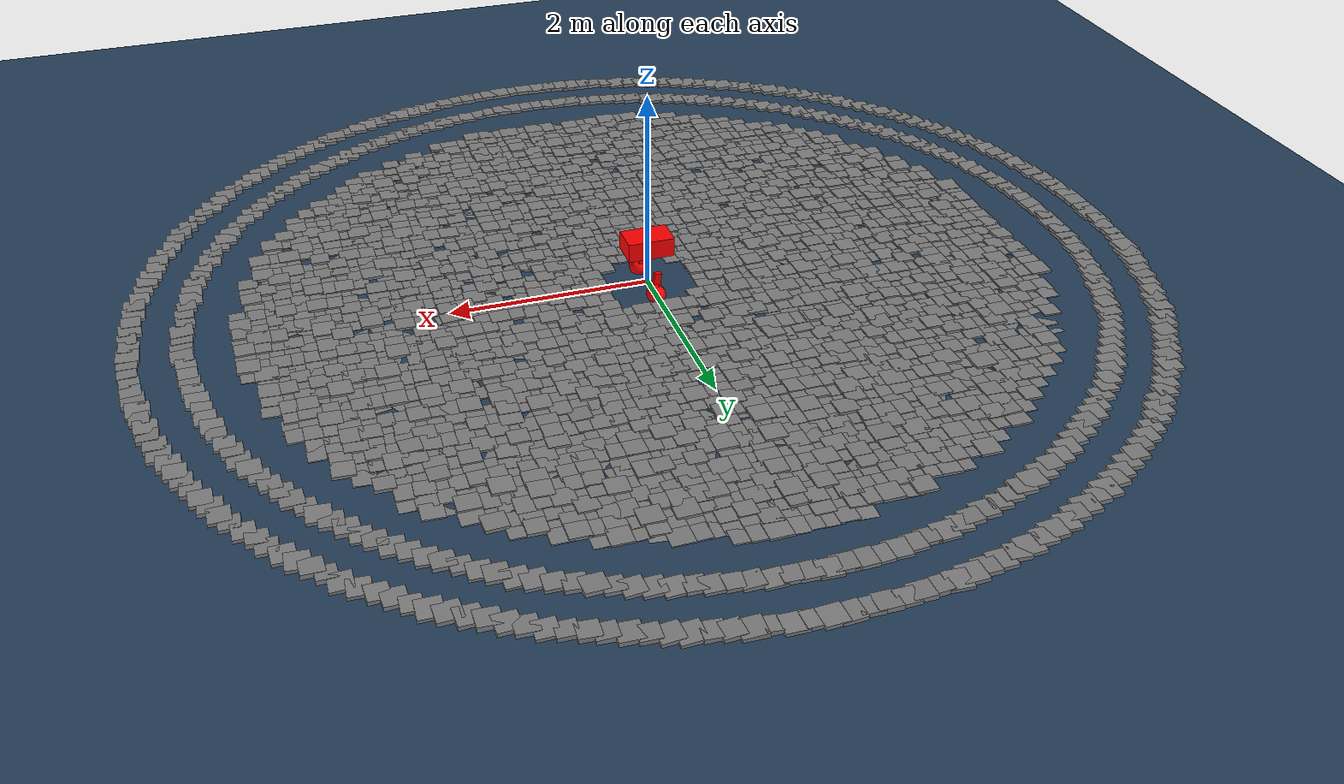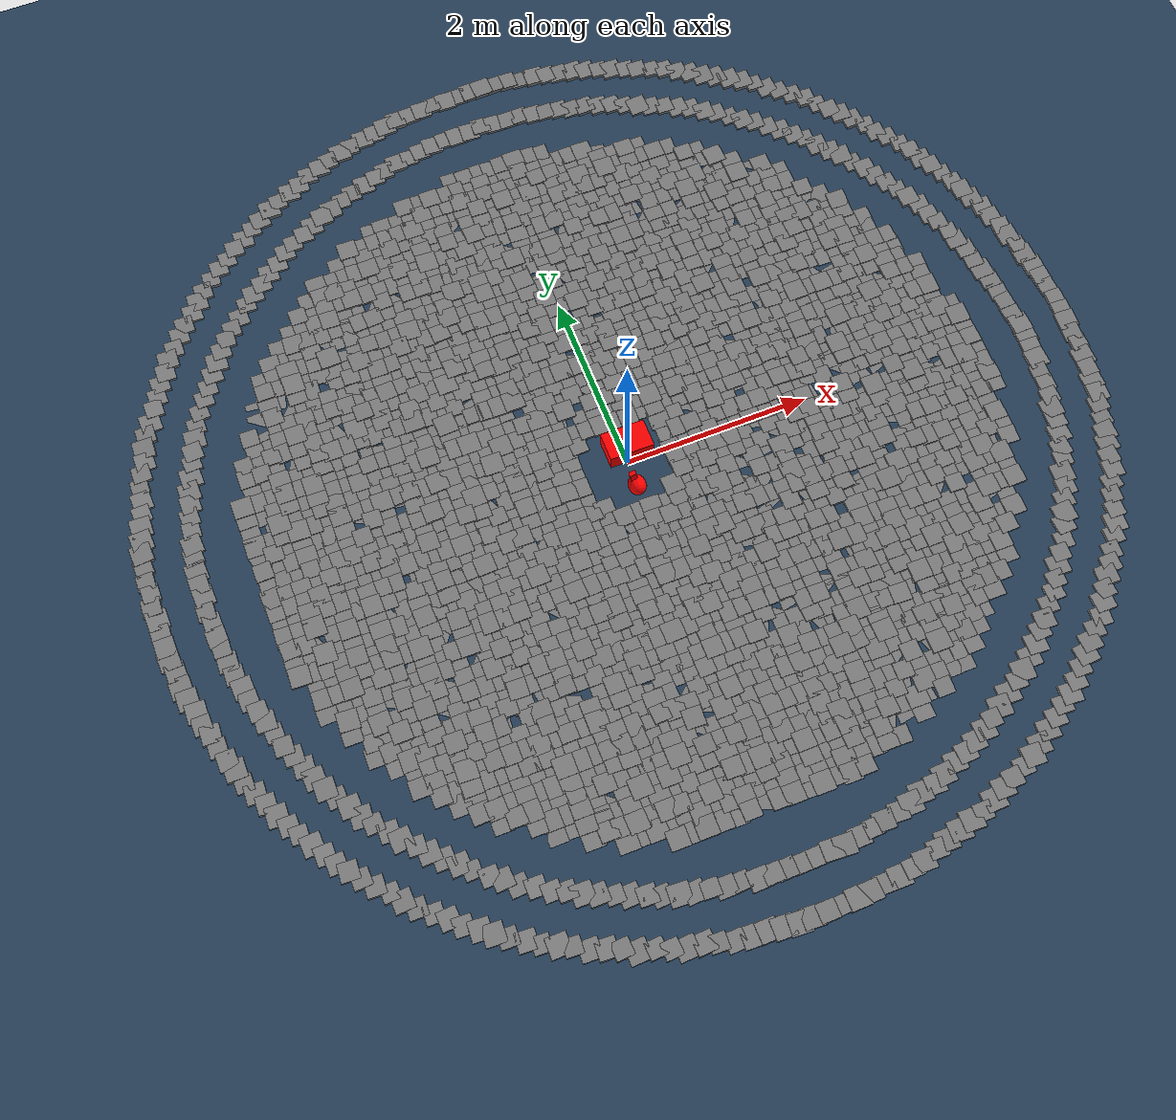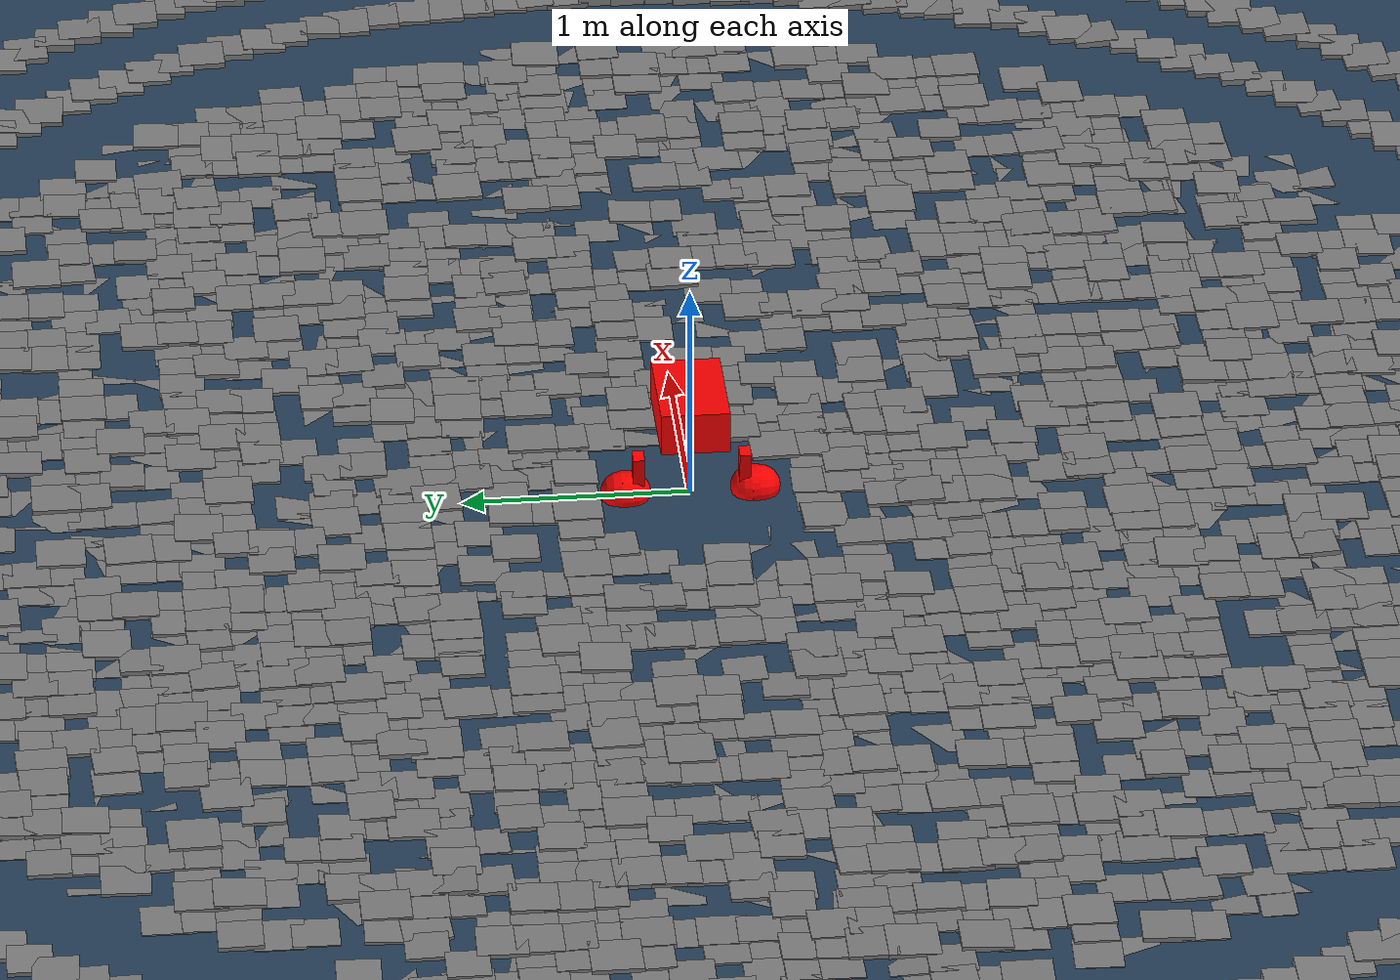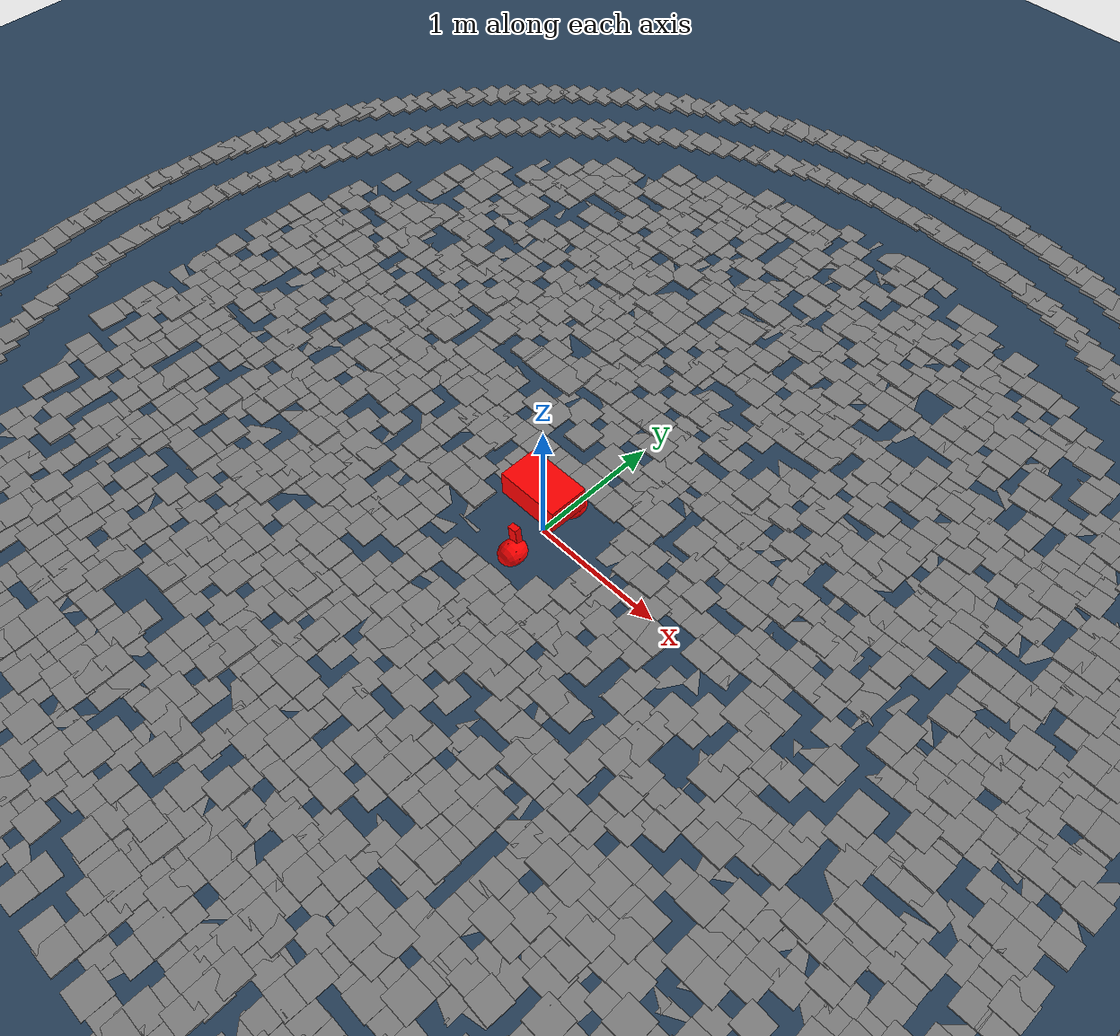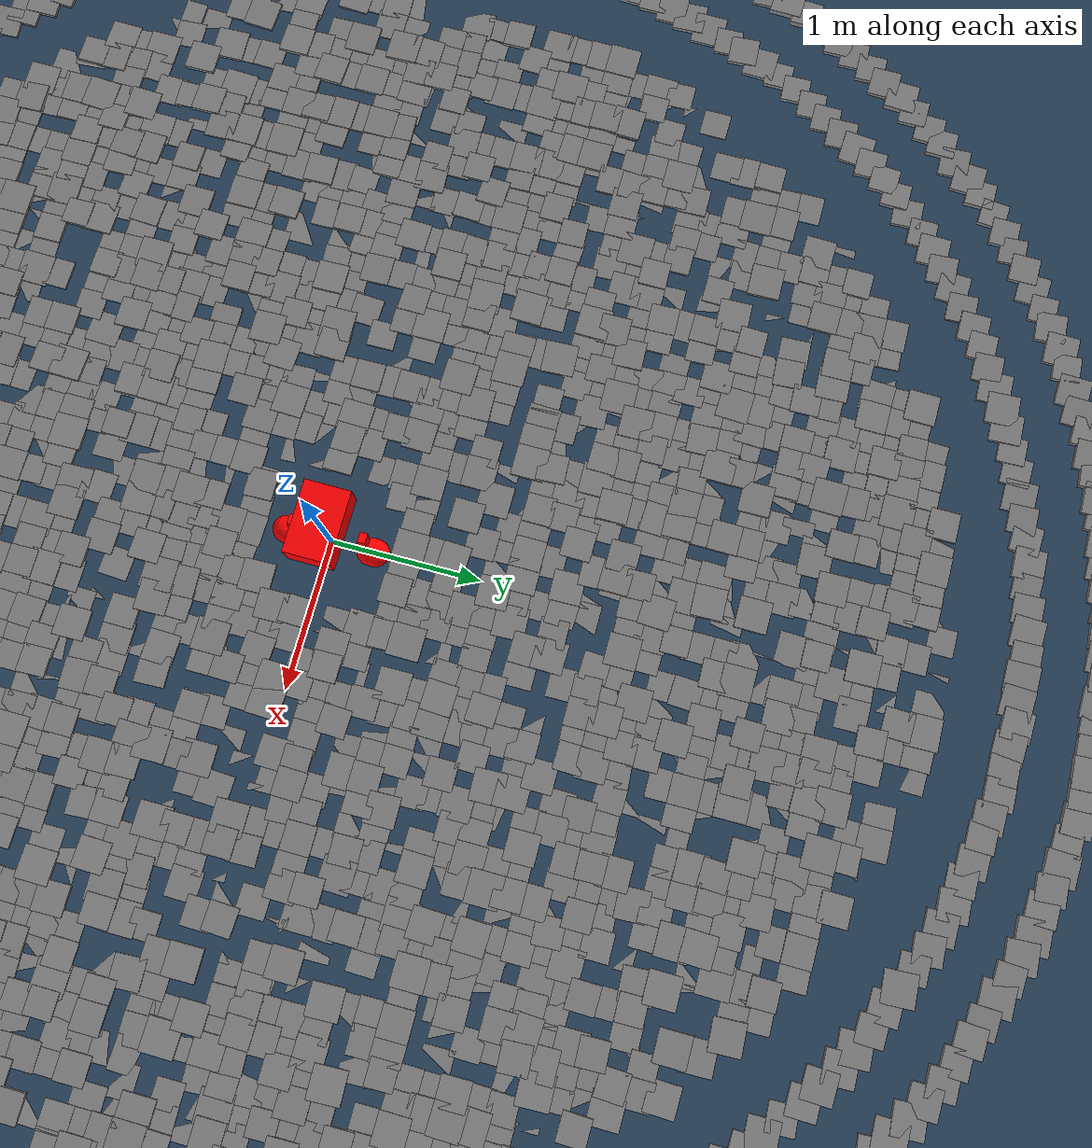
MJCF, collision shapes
<mujoco model="tita rough scene">
  <include file="tita.xml"/>

  <statistic center="0 0 0.5" extent="5.5"/>

  <visual>
    <headlight diffuse="0.6 0.6 0.6" ambient="0.1 0.1 0.1" specular="0.9 0.9 0.9"/>
    <rgba haze="0.15 0.25 0.35 1"/>
    <global azimuth="140" elevation="-20"/>
  </visual>

  <asset>
    <texture type="skybox" builtin="gradient" rgb1="0.3 0.5 0.7" rgb2="0 0 0" width="512" height="3072"/>
    <texture type="2d" name="groundplane" builtin="checker" mark="edge" rgb1="0.2 0.3 0.4" rgb2="0.1 0.2 0.3"
      markrgb="0.8 0.8 0.8" width="300" height="300"/>
    <material name="groundplane" texture="groundplane" texuniform="true" texrepeat="5 5" reflectance="0.2"/>
  </asset>

  <worldbody>
    <geom name="floor" size="0 0 0.05" type="plane" material="groundplane"/>

    <!-- Circular cobblestone field: annulus 0.5 m <= r <= 4.0 m,
         flat clearance disc of radius 0.5 m at the center. -->
    <geom pos="-3.8500 -1.0000 -0.25" type="box" size="0.1069 0.1069 0.2577" quat="0.9997 -0.0125 0.0068 -0.0187" friction="1.0 0.02 0.001"/>
    <geom pos="-3.8500 -0.8500 -0.25" type="box" size="0.0961 0.0961 0.2493" quat="0.9999 -0.0005 -0.0131 -0.0076" friction="1.0 0.02 0.001"/>
    <geom pos="-3.8500 -0.7000 -0.25" type="box" size="0.0956 0.0956 0.2577" quat="0.9997 -0.0054 -0.0050 0.0232" friction="1.0 0.02 0.001"/>
    <geom pos="-3.8500 -0.5500 -0.25" type="box" size="0.1080 0.1080 0.2443" quat="0.9998 -0.0119 -0.0021 -0.0166" friction="1.0 0.02 0.001"/>
    <geom pos="-3.8500 -0.4000 -0.25" type="box" size="0.0994 0.0994 0.2380" quat="0.9999 -0.0069 0.0030 0.0122" friction="1.0 0.02 0.001"/>
    <geom pos="-3.8500 -0.2500 -0.25" type="box" size="0.1073 0.1073 0.2428" quat="1.0000 -0.0003 0.0001 -0.0003" friction="1.0 0.02 0.001"/>
    <geom pos="-3.8500 -0.1000 -0.25" type="box" size="0.1044 0.1044 0.2470" quat="0.9997 0.0093 -0.0182 0.0161" friction="1.0 0.02 0.001"/>
    <geom pos="-3.8500 0.0500 -0.25" type="box" size="0.0949 0.0949 0.2448" quat="0.9999 0.0002 0.0117 -0.0124" friction="1.0 0.02 0.001"/>
    <geom pos="-3.8500 0.2000 -0.25" type="box" size="0.0948 0.0948 0.2640" quat="0.9999 0.0041 -0.0118 0.0088" friction="1.0 0.02 0.001"/>
    <geom pos="-3.8500 0.3500 -0.25" type="box" size="0.1087 0.1087 0.2383" quat="0.9999 0.0043 -0.0150 -0.0050" friction="1.0 0.02 0.001"/>
    <geom pos="-3.8500 0.5000 -0.25" type="box" size="0.1063 0.1063 0.2512" quat="0.9998 0.0144 -0.0033 -0.0101" friction="1.0 0.02 0.001"/>
    <geom pos="-3.8500 0.6500 -0.25" type="box" size="0.0977 0.0977 0.2523" quat="1.0000 -0.0037 -0.0011 0.0041" friction="1.0 0.02 0.001"/>
    <geom pos="-3.8500 0.8000 -0.25" type="box" size="0.1023 0.1023 0.2547" quat="0.9996 -0.0267 0.0040 0.0061" friction="1.0 0.02 0.001"/>
    <geom pos="-3.8500 0.9500 -0.25" type="box" size="0.1068 0.1068 0.2619" quat="0.9999 -0.0100 0.0054 -0.0028" friction="1.0 0.02 0.001"/>
    <geom pos="-3.7000 -1.4500 -0.25" type="box" size="0.1041 0.1041 0.2433" quat="0.9996 0.0095 -0.0232 0.0136" friction="1.0 0.02 0.001"/>
    <geom pos="-3.7000 -1.3000 -0.25" type="box" size="0.1016 0.1016 0.2485" quat="0.9996 -0.0065 -0.0143 -0.0226" friction="1.0 0.02 0.001"/>
    <geom pos="-3.7000 -1.1500 -0.25" type="box" size="0.1059 0.1059 0.2375" quat="1.0000 -0.0036 -0.0031 -0.0055" friction="1.0 0.02 0.001"/>
    <geom pos="-3.7000 -1.0000 -0.25" type="box" size="0.1046 0.1046 0.2385" quat="1.0000 -0.0062 0.0014 0.0077" friction="1.0 0.02 0.001"/>
    <geom pos="-3.7000 -0.8500 -0.25" type="box" size="0.1063 0.1063 0.2380" quat="0.9996 0.0129 0.0169 0.0172" friction="1.0 0.02 0.001"/>
    <geom pos="-3.7000 -0.7000 -0.25" type="box" size="0.1007 0.1007 0.2554" quat="0.9998 0.0045 0.0174 0.0029" friction="1.0 0.02 0.001"/>
    <geom pos="-3.7000 -0.5500 -0.25" type="box" size="0.1015 0.1015 0.2467" quat="0.9996 -0.0197 0.0209 0.0021" friction="1.0 0.02 0.001"/>
    <geom pos="-3.7000 -0.4000 -0.25" type="box" size="0.0937 0.0937 0.2387" quat="0.9996 0.0007 0.0069 0.0272" friction="1.0 0.02 0.001"/>
    <geom pos="-3.7000 -0.2500 -0.25" type="box" size="0.0905 0.0905 0.2478" quat="0.9999 0.0080 0.0059 0.0034" friction="1.0 0.02 0.001"/>
    <geom pos="-3.7000 -0.1000 -0.25" type="box" size="0.0936 0.0936 0.2501" quat="0.9996 0.0282 0.0089 0.0022" friction="1.0 0.02 0.001"/>
    <geom pos="-3.7000 0.0500 -0.25" type="box" size="0.0940 0.0940 0.2458" quat="0.9998 -0.0022 -0.0193 0.0054" friction="1.0 0.02 0.001"/>
    <geom pos="-3.7000 0.2000 -0.25" type="box" size="0.1093 0.1093 0.2367" quat="0.9999 -0.0016 -0.0045 -0.0091" friction="1.0 0.02 0.001"/>
    <geom pos="-3.7000 0.3500 -0.25" type="box" size="0.0950 0.0950 0.2529" quat="0.9999 -0.0083 0.0032 -0.0146" friction="1.0 0.02 0.001"/>
    <geom pos="-3.7000 0.5000 -0.25" type="box" size="0.1002 0.1002 0.2443" quat="1.0000 0.0007 -0.0047 0.0059" friction="1.0 0.02 0.001"/>
    <geom pos="-3.7000 0.6500 -0.25" type="box" size="0.1012 0.1012 0.2354" quat="1.0000 -0.0003 -0.0055 0.0047" friction="1.0 0.02 0.001"/>
    <geom pos="-3.7000 0.8000 -0.25" type="box" size="0.1091 0.1091 0.2456" quat="0.9996 0.0067 -0.0065 0.0268" friction="1.0 0.02 0.001"/>
    <geom pos="-3.7000 0.9500 -0.25" type="box" size="0.1027 0.1027 0.2536" quat="1.0000 -0.0000 -0.0000 -0.0000" friction="1.0 0.02 0.001"/>
    <geom pos="-3.7000 1.1000 -0.25" type="box" size="0.0938 0.0938 0.2450" quat="0.9999 0.0053 0.0007 0.0100" friction="1.0 0.02 0.001"/>
    <geom pos="-3.7000 1.2500 -0.25" type="box" size="0.1075 0.1075 0.2520" quat="0.9998 -0.0163 0.0097 -0.0058" friction="1.0 0.02 0.001"/>
    <geom pos="-3.7000 1.4000 -0.25" type="box" size="0.0909 0.0909 0.2484" quat="0.9999 -0.0136 -0.0005 0.0080" friction="1.0 0.02 0.001"/>
    <geom pos="-3.5500 -1.7500 -0.25" type="box" size="0.0997 0.0997 0.2518" quat="0.9999 0.0004 -0.0129 -0.0054" friction="1.0 0.02 0.001"/>
    <geom pos="-3.5500 -1.6000 -0.25" type="box" size="0.1062 0.1062 0.2613" quat="0.9996 0.0014 0.0114 -0.0277" friction="1.0 0.02 0.001"/>
    <geom pos="-3.5500 -1.4500 -0.25" type="box" size="0.1027 0.1027 0.2375" quat="1.0000 -0.0013 -0.0086 -0.0037" friction="1.0 0.02 0.001"/>
    <geom pos="-3.5500 -1.3000 -0.25" type="box" size="0.0943 0.0943 0.2565" quat="0.9999 0.0067 0.0144 0.0002" friction="1.0 0.02 0.001"/>
    <geom pos="-3.5500 -1.1500 -0.25" type="box" size="0.0920 0.0920 0.2386" quat="1.0000 -0.0017 -0.0023 -0.0007" friction="1.0 0.02 0.001"/>
    <geom pos="-3.5500 -1.0000 -0.25" type="box" size="0.1071 0.1071 0.2469" quat="0.9999 0.0130 0.0033 0.0019" friction="1.0 0.02 0.001"/>
    <geom pos="-3.5500 -0.8500 -0.25" type="box" size="0.1058 0.1058 0.2608" quat="0.9997 0.0160 0.0178 -0.0106" friction="1.0 0.02 0.001"/>
    <geom pos="-3.5500 -0.7000 -0.25" type="box" size="0.0956 0.0956 0.2356" quat="0.9999 -0.0074 0.0145 0.0038" friction="1.0 0.02 0.001"/>
    <geom pos="-3.5500 -0.5500 -0.25" type="box" size="0.1089 0.1089 0.2632" quat="0.9998 0.0166 -0.0105 -0.0006" friction="1.0 0.02 0.001"/>
    <geom pos="-3.5500 -0.4000 -0.25" type="box" size="0.1042 0.1042 0.2621" quat="0.9999 -0.0137 -0.0054 -0.0066" friction="1.0 0.02 0.001"/>
    <geom pos="-3.5500 -0.2500 -0.25" type="box" size="0.0942 0.0942 0.2526" quat="0.9998 0.0117 0.0007 -0.0181" friction="1.0 0.02 0.001"/>
    <geom pos="-3.5500 -0.1000 -0.25" type="box" size="0.0968 0.0968 0.2536" quat="0.9996 0.0274 0.0104 0.0027" friction="1.0 0.02 0.001"/>
    <geom pos="-3.5500 0.0500 -0.25" type="box" size="0.0958 0.0958 0.2468" quat="1.0000 -0.0010 -0.0003 -0.0010" friction="1.0 0.02 0.001"/>
    <geom pos="-3.5500 0.2000 -0.25" type="box" size="0.0936 0.0936 0.2507" quat="1.0000 0.0010 0.0089 0.0042" friction="1.0 0.02 0.001"/>
    <geom pos="-3.5500 0.3500 -0.25" type="box" size="0.0983 0.0983 0.2380" quat="0.9999 0.0053 -0.0034 0.0082" friction="1.0 0.02 0.001"/>
    <geom pos="-3.5500 0.5000 -0.25" type="box" size="0.0996 0.0996 0.2560" quat="0.9998 -0.0207 -0.0068 0.0034" friction="1.0 0.02 0.001"/>
    <geom pos="-3.5500 0.6500 -0.25" type="box" size="0.1079 0.1079 0.2626" quat="1.0000 -0.0008 -0.0008 0.0016" friction="1.0 0.02 0.001"/>
    <geom pos="-3.5500 0.8000 -0.25" type="box" size="0.0917 0.0917 0.2575" quat="0.9999 -0.0103 0.0053 0.0021" friction="1.0 0.02 0.001"/>
    <geom pos="-3.5500 0.9500 -0.25" type="box" size="0.1004 0.1004 0.2485" quat="0.9999 -0.0104 0.0007 -0.0036" friction="1.0 0.02 0.001"/>
    <geom pos="-3.5500 1.1000 -0.25" type="box" size="0.1098 0.1098 0.2428" quat="0.9999 -0.0072 0.0014 -0.0079" friction="1.0 0.02 0.001"/>
    <geom pos="-3.5500 1.2500 -0.25" type="box" size="0.0913 0.0913 0.2609" quat="1.0000 -0.0009 -0.0028 -0.0020" friction="1.0 0.02 0.001"/>
    <geom pos="-3.5500 1.4000 -0.25" type="box" size="0.0980 0.0980 0.2412" quat="1.0000 0.0012 0.0061 0.0017" friction="1.0 0.02 0.001"/>
    <geom pos="-3.5500 1.5500 -0.25" type="box" size="0.0929 0.0929 0.2409" quat="0.9996 -0.0124 0.0120 0.0239" friction="1.0 0.02 0.001"/>
    <geom pos="-3.5500 1.7000 -0.25" type="box" size="0.0930 0.0930 0.2472" quat="0.9999 0.0114 -0.0041 -0.0087" friction="1.0 0.02 0.001"/>
    <geom pos="-3.4000 -2.0500 -0.25" type="box" size="0.1083 0.1083 0.2447" quat="0.9998 -0.0176 0.0002 -0.0049" friction="1.0 0.02 0.001"/>
    <geom pos="-3.4000 -1.9000 -0.25" type="box" size="0.0944 0.0944 0.2452" quat="0.9997 -0.0065 0.0230 -0.0055" friction="1.0 0.02 0.001"/>
    <geom pos="-3.4000 -1.7500 -0.25" type="box" size="0.0907 0.0907 0.2395" quat="0.9998 -0.0009 0.0199 0.0082" friction="1.0 0.02 0.001"/>
    <geom pos="-3.4000 -1.6000 -0.25" type="box" size="0.1061 0.1061 0.2370" quat="1.0000 -0.0006 0.0009 0.0005" friction="1.0 0.02 0.001"/>
    <geom pos="-3.4000 -1.4500 -0.25" type="box" size="0.0945 0.0945 0.2362" quat="1.0000 0.0044 0.0004 -0.0007" friction="1.0 0.02 0.001"/>
    <geom pos="-3.4000 -1.3000 -0.25" type="box" size="0.1031 0.1031 0.2641" quat="0.9999 0.0035 -0.0146 -0.0005" friction="1.0 0.02 0.001"/>
    <geom pos="-3.4000 -1.1500 -0.25" type="box" size="0.1015 0.1015 0.2554" quat="0.9996 0.0066 -0.0182 0.0190" friction="1.0 0.02 0.001"/>
    <geom pos="-3.4000 -1.0000 -0.25" type="box" size="0.0941 0.0941 0.2511" quat="0.9999 -0.0008 -0.0118 -0.0084" friction="1.0 0.02 0.001"/>
    <geom pos="-3.4000 -0.8500 -0.25" type="box" size="0.1058 0.1058 0.2467" quat="1.0000 -0.0000 -0.0000 0.0000" friction="1.0 0.02 0.001"/>
    <geom pos="-3.4000 -0.7000 -0.25" type="box" size="0.0936 0.0936 0.2502" quat="0.9997 -0.0249 -0.0002 0.0066" friction="1.0 0.02 0.001"/>
    <geom pos="-3.4000 -0.5500 -0.25" type="box" size="0.1089 0.1089 0.2441" quat="1.0000 -0.0026 0.0017 0.0022" friction="1.0 0.02 0.001"/>
    <geom pos="-3.4000 -0.4000 -0.25" type="box" size="0.0957 0.0957 0.2599" quat="0.9999 0.0112 0.0052 0.0019" friction="1.0 0.02 0.001"/>
    <geom pos="-3.4000 -0.2500 -0.25" type="box" size="0.0998 0.0998 0.2609" quat="0.9999 -0.0017 -0.0080 0.0093" friction="1.0 0.02 0.001"/>
    <geom pos="-3.4000 -0.1000 -0.25" type="box" size="0.1022 0.1022 0.2466" quat="1.0000 0.0041 0.0019 0.0006" friction="1.0 0.02 0.001"/>
    <geom pos="-3.4000 0.0500 -0.25" type="box" size="0.0906 0.0906 0.2535" quat="0.9999 -0.0037 -0.0040 -0.0101" friction="1.0 0.02 0.001"/>
    <geom pos="-3.4000 0.2000 -0.25" type="box" size="0.1055 0.1055 0.2497" quat="0.9999 -0.0028 0.0101 -0.0093" friction="1.0 0.02 0.001"/>
    <geom pos="-3.4000 0.3500 -0.25" type="box" size="0.1026 0.1026 0.2451" quat="1.0000 0.0021 0.0021 -0.0024" friction="1.0 0.02 0.001"/>
    <geom pos="-3.4000 0.5000 -0.25" type="box" size="0.1082 0.1082 0.2590" quat="0.9998 -0.0105 0.0152 -0.0087" friction="1.0 0.02 0.001"/>
    <geom pos="-3.4000 0.6500 -0.25" type="box" size="0.1062 0.1062 0.2506" quat="0.9997 0.0048 -0.0210 0.0072" friction="1.0 0.02 0.001"/>
    <geom pos="-3.4000 0.8000 -0.25" type="box" size="0.0991 0.0991 0.2587" quat="0.9996 -0.0270 0.0068 0.0035" friction="1.0 0.02 0.001"/>
    <geom pos="-3.4000 0.9500 -0.25" type="box" size="0.0997 0.0997 0.2620" quat="1.0000 0.0024 -0.0009 -0.0011" friction="1.0 0.02 0.001"/>
    <geom pos="-3.4000 1.1000 -0.25" type="box" size="0.1064 0.1064 0.2617" quat="0.9999 -0.0024 0.0023 -0.0122" friction="1.0 0.02 0.001"/>
    <geom pos="-3.4000 1.2500 -0.25" type="box" size="0.0961 0.0961 0.2384" quat="0.9999 -0.0059 0.0030 0.0106" friction="1.0 0.02 0.001"/>
    <geom pos="-3.4000 1.4000 -0.25" type="box" size="0.0920 0.0920 0.2582" quat="0.9999 -0.0131 -0.0003 -0.0030" friction="1.0 0.02 0.001"/>
    <geom pos="-3.4000 1.5500 -0.25" type="box" size="0.1037 0.1037 0.2359" quat="1.0000 0.0018 -0.0010 -0.0001" friction="1.0 0.02 0.001"/>
    <geom pos="-3.4000 1.7000 -0.25" type="box" size="0.0972 0.0972 0.2359" quat="0.9996 -0.0275 -0.0056 0.0080" friction="1.0 0.02 0.001"/>
    <geom pos="-3.4000 1.8500 -0.25" type="box" size="0.1064 0.1064 0.2371" quat="0.9996 0.0188 -0.0149 0.0147" friction="1.0 0.02 0.001"/>
    <geom pos="-3.4000 2.0000 -0.25" type="box" size="0.0925 0.0925 0.2352" quat="0.9998 0.0179 -0.0019 0.0020" friction="1.0 0.02 0.001"/>
    <geom pos="-3.2500 -2.2000 -0.25" type="box" size="0.1072 0.1072 0.2406" quat="0.9996 0.0193 0.0164 0.0141" friction="1.0 0.02 0.001"/>
    <geom pos="-3.2500 -2.0500 -0.25" type="box" size="0.0972 0.0972 0.2492" quat="0.9996 -0.0016 -0.0076 0.0277" friction="1.0 0.02 0.001"/>
    <geom pos="-3.2500 -1.9000 -0.25" type="box" size="0.1027 0.1027 0.2405" quat="0.9996 0.0181 -0.0008 -0.0199" friction="1.0 0.02 0.001"/>
    <geom pos="-3.2500 -1.7500 -0.25" type="box" size="0.1089 0.1089 0.2591" quat="0.9997 -0.0080 -0.0085 0.0194" friction="1.0 0.02 0.001"/>
    <geom pos="-3.2500 -1.6000 -0.25" type="box" size="0.0958 0.0958 0.2476" quat="1.0000 0.0017 0.0005 0.0013" friction="1.0 0.02 0.001"/>
    <geom pos="-3.2500 -1.4500 -0.25" type="box" size="0.0984 0.0984 0.2515" quat="0.9999 0.0012 -0.0007 -0.0126" friction="1.0 0.02 0.001"/>
    <geom pos="-3.2500 -1.3000 -0.25" type="box" size="0.1027 0.1027 0.2375" quat="0.9999 -0.0109 0.0039 0.0040" friction="1.0 0.02 0.001"/>
    <geom pos="-3.2500 -1.1500 -0.25" type="box" size="0.0983 0.0983 0.2568" quat="1.0000 -0.0014 -0.0037 0.0078" friction="1.0 0.02 0.001"/>
    <geom pos="-3.2500 -1.0000 -0.25" type="box" size="0.0994 0.0994 0.2635" quat="0.9997 0.0034 -0.0112 -0.0208" friction="1.0 0.02 0.001"/>
    <geom pos="-3.2500 -0.8500 -0.25" type="box" size="0.0989 0.0989 0.2470" quat="1.0000 -0.0034 0.0007 -0.0066" friction="1.0 0.02 0.001"/>
    <geom pos="-3.2500 -0.7000 -0.25" type="box" size="0.0991 0.0991 0.2631" quat="1.0000 0.0032 0.0040 -0.0034" friction="1.0 0.02 0.001"/>
    <geom pos="-3.2500 -0.5500 -0.25" type="box" size="0.0900 0.0900 0.2560" quat="1.0000 -0.0089 -0.0009 -0.0009" friction="1.0 0.02 0.001"/>
    <geom pos="-3.2500 -0.4000 -0.25" type="box" size="0.1054 0.1054 0.2539" quat="0.9998 -0.0173 -0.0050 -0.0095" friction="1.0 0.02 0.001"/>
    <geom pos="-3.2500 -0.2500 -0.25" type="box" size="0.1052 0.1052 0.2420" quat="0.9996 -0.0237 0.0013 -0.0176" friction="1.0 0.02 0.001"/>
    <geom pos="-3.2500 -0.1000 -0.25" type="box" size="0.0924 0.0924 0.2615" quat="0.9999 0.0059 0.0015 -0.0102" friction="1.0 0.02 0.001"/>
    <geom pos="-3.2500 0.0500 -0.25" type="box" size="0.0920 0.0920 0.2426" quat="0.9996 -0.0035 -0.0056 0.0264" friction="1.0 0.02 0.001"/>
    <geom pos="-3.2500 0.2000 -0.25" type="box" size="0.1019 0.1019 0.2361" quat="1.0000 0.0016 -0.0057 -0.0046" friction="1.0 0.02 0.001"/>
    <geom pos="-3.2500 0.3500 -0.25" type="box" size="0.1084 0.1084 0.2399" quat="0.9999 0.0122 -0.0084 0.0050" friction="1.0 0.02 0.001"/>
    <geom pos="-3.2500 0.5000 -0.25" type="box" size="0.1015 0.1015 0.2538" quat="0.9997 -0.0192 -0.0038 -0.0128" friction="1.0 0.02 0.001"/>
    <geom pos="-3.2500 0.6500 -0.25" type="box" size="0.1058 0.1058 0.2438" quat="1.0000 -0.0022 -0.0029 0.0030" friction="1.0 0.02 0.001"/>
    <geom pos="-3.2500 0.8000 -0.25" type="box" size="0.1039 0.1039 0.2464" quat="0.9999 -0.0091 -0.0059 -0.0091" friction="1.0 0.02 0.001"/>
    <geom pos="-3.2500 0.9500 -0.25" type="box" size="0.0983 0.0983 0.2493" quat="0.9998 -0.0133 -0.0049 -0.0135" friction="1.0 0.02 0.001"/>
    <geom pos="-3.2500 1.1000 -0.25" type="box" size="0.0912 0.0912 0.2440" quat="0.9999 -0.0004 -0.0126 -0.0063" friction="1.0 0.02 0.001"/>
    <geom pos="-3.2500 1.2500 -0.25" type="box" size="0.1078 0.1078 0.2353" quat="0.9997 -0.0101 -0.0236 -0.0040" friction="1.0 0.02 0.001"/>
    <geom pos="-3.2500 1.4000 -0.25" type="box" size="0.1037 0.1037 0.2573" quat="0.9996 -0.0012 -0.0022 0.0299" friction="1.0 0.02 0.001"/>
    <geom pos="-3.2500 1.5500 -0.25" type="box" size="0.1075 0.1075 0.2560" quat="0.9997 0.0100 -0.0029 -0.0200" friction="1.0 0.02 0.001"/>
    <geom pos="-3.2500 1.7000 -0.25" type="box" size="0.0958 0.0958 0.2382" quat="0.9996 -0.0226 0.0057 0.0134" friction="1.0 0.02 0.001"/>
    <geom pos="-3.2500 1.8500 -0.25" type="box" size="0.0987 0.0987 0.2484" quat="1.0000 0.0023 -0.0008 -0.0030" friction="1.0 0.02 0.001"/>
    <geom pos="-3.2500 2.0000 -0.25" type="box" size="0.1082 0.1082 0.2483" quat="1.0000 0.0015 -0.0060 0.0022" friction="1.0 0.02 0.001"/>
    <geom pos="-3.2500 2.1500 -0.25" type="box" size="0.0939 0.0939 0.2632" quat="0.9999 -0.0110 -0.0032 -0.0020" friction="1.0 0.02 0.001"/>
    <geom pos="-3.2500 2.3000 -0.25" type="box" size="0.0947 0.0947 0.2375" quat="0.9998 0.0046 0.0110 -0.0139" friction="1.0 0.02 0.001"/>
    <geom pos="-3.1000 -2.5000 -0.25" type="box" size="0.1023 0.1023 0.2561" quat="0.9997 -0.0131 -0.0227 -0.0017" friction="1.0 0.02 0.001"/>
    <geom pos="-3.1000 -2.3500 -0.25" type="box" size="0.0971 0.0971 0.2487" quat="0.9996 -0.0085 -0.0092 0.0249" friction="1.0 0.02 0.001"/>
    <geom pos="-3.1000 -2.2000 -0.25" type="box" size="0.1087 0.1087 0.2524" quat="1.0000 -0.0026 -0.0059 0.0004" friction="1.0 0.02 0.001"/>
    <geom pos="-3.1000 -2.0500 -0.25" type="box" size="0.0953 0.0953 0.2363" quat="0.9997 0.0034 0.0055 -0.0227" friction="1.0 0.02 0.001"/>
    <geom pos="-3.1000 -1.9000 -0.25" type="box" size="0.1036 0.1036 0.2641" quat="0.9999 -0.0027 -0.0106 0.0081" friction="1.0 0.02 0.001"/>
    <geom pos="-3.1000 -1.7500 -0.25" type="box" size="0.0968 0.0968 0.2381" quat="1.0000 0.0070 -0.0063 -0.0026" friction="1.0 0.02 0.001"/>
    <geom pos="-3.1000 -1.6000 -0.25" type="box" size="0.0906 0.0906 0.2363" quat="0.9999 0.0129 -0.0061 0.0066" friction="1.0 0.02 0.001"/>
    <geom pos="-3.1000 -1.4500 -0.25" type="box" size="0.0938 0.0938 0.2410" quat="1.0000 -0.0032 -0.0061 -0.0032" friction="1.0 0.02 0.001"/>
    <geom pos="-3.1000 -1.3000 -0.25" type="box" size="0.0969 0.0969 0.2564" quat="1.0000 0.0013 0.0016 0.0005" friction="1.0 0.02 0.001"/>
    <geom pos="-3.1000 -1.1500 -0.25" type="box" size="0.0992 0.0992 0.2567" quat="1.0000 0.0029 0.0009 0.0018" friction="1.0 0.02 0.001"/>
    <geom pos="-3.1000 -1.0000 -0.25" type="box" size="0.0916 0.0916 0.2380" quat="0.9996 -0.0039 0.0026 -0.0272" friction="1.0 0.02 0.001"/>
    <geom pos="-3.1000 -0.8500 -0.25" type="box" size="0.0988 0.0988 0.2373" quat="1.0000 -0.0048 0.0024 0.0004" friction="1.0 0.02 0.001"/>
    <geom pos="-3.1000 -0.7000 -0.25" type="box" size="0.0998 0.0998 0.2388" quat="1.0000 -0.0010 0.0066 -0.0069" friction="1.0 0.02 0.001"/>
    <geom pos="-3.1000 -0.5500 -0.25" type="box" size="0.0987 0.0987 0.2517" quat="0.9999 -0.0029 0.0127 0.0026" friction="1.0 0.02 0.001"/>
    <geom pos="-3.1000 -0.4000 -0.25" type="box" size="0.1021 0.1021 0.2511" quat="1.0000 0.0026 -0.0002 0.0024" friction="1.0 0.02 0.001"/>
    <geom pos="-3.1000 -0.2500 -0.25" type="box" size="0.1057 0.1057 0.2380" quat="0.9998 -0.0019 -0.0178 -0.0083" friction="1.0 0.02 0.001"/>
    <geom pos="-3.1000 -0.1000 -0.25" type="box" size="0.1048 0.1048 0.2505" quat="0.9998 0.0184 0.0037 -0.0046" friction="1.0 0.02 0.001"/>
    <geom pos="-3.1000 0.0500 -0.25" type="box" size="0.0924 0.0924 0.2571" quat="1.0000 -0.0040 0.0050 -0.0018" friction="1.0 0.02 0.001"/>
    <geom pos="-3.1000 0.2000 -0.25" type="box" size="0.1066 0.1066 0.2422" quat="1.0000 -0.0048 -0.0051 -0.0006" friction="1.0 0.02 0.001"/>
    <geom pos="-3.1000 0.3500 -0.25" type="box" size="0.1026 0.1026 0.2436" quat="0.9998 0.0076 0.0140 -0.0074" friction="1.0 0.02 0.001"/>
    <geom pos="-3.1000 0.5000 -0.25" type="box" size="0.0905 0.0905 0.2389" quat="0.9999 -0.0016 -0.0121 0.0093" friction="1.0 0.02 0.001"/>
    <geom pos="-3.1000 0.6500 -0.25" type="box" size="0.0915 0.0915 0.2580" quat="1.0000 0.0010 -0.0049 -0.0040" friction="1.0 0.02 0.001"/>
    <geom pos="-3.1000 0.8000 -0.25" type="box" size="0.1047 0.1047 0.2595" quat="0.9998 -0.0102 0.0009 -0.0145" friction="1.0 0.02 0.001"/>
    <geom pos="-3.1000 0.9500 -0.25" type="box" size="0.1026 0.1026 0.2620" quat="0.9999 0.0096 0.0077 -0.0060" friction="1.0 0.02 0.001"/>
    <geom pos="-3.1000 1.1000 -0.25" type="box" size="0.0903 0.0903 0.2416" quat="0.9999 -0.0016 -0.0085 -0.0121" friction="1.0 0.02 0.001"/>
    <geom pos="-3.1000 1.2500 -0.25" type="box" size="0.1091 0.1091 0.2494" quat="0.9998 -0.0082 0.0194 -0.0009" friction="1.0 0.02 0.001"/>
    <geom pos="-3.1000 1.4000 -0.25" type="box" size="0.1064 0.1064 0.2586" quat="1.0000 0.0011 -0.0002 0.0002" friction="1.0 0.02 0.001"/>
    <geom pos="-3.1000 1.5500 -0.25" type="box" size="0.1045 0.1045 0.2639" quat="1.0000 -0.0042 0.0064 -0.0016" friction="1.0 0.02 0.001"/>
    <geom pos="-3.1000 1.7000 -0.25" type="box" size="0.1034 0.1034 0.2441" quat="0.9998 -0.0167 -0.0089 0.0112" friction="1.0 0.02 0.001"/>
    <geom pos="-3.1000 1.8500 -0.25" type="box" size="0.0930 0.0930 0.2357" quat="0.9998 -0.0042 -0.0044 0.0187" friction="1.0 0.02 0.001"/>
    <geom pos="-3.1000 2.0000 -0.25" type="box" size="0.0913 0.0913 0.2369" quat="0.9996 0.0050 0.0259 -0.0046" friction="1.0 0.02 0.001"/>
    <geom pos="-3.1000 2.1500 -0.25" type="box" size="0.0943 0.0943 0.2481" quat="0.9997 -0.0057 0.0071 -0.0205" friction="1.0 0.02 0.001"/>
    <geom pos="-3.1000 2.3000 -0.25" type="box" size="0.0977 0.0977 0.2473" quat="0.9998 0.0199 -0.0008 0.0094" friction="1.0 0.02 0.001"/>
    <geom pos="-3.1000 2.4500 -0.25" type="box" size="0.1037 0.1037 0.2489" quat="1.0000 0.0001 0.0000 -0.0000" friction="1.0 0.02 0.001"/>
    <geom pos="-2.9500 -2.6500 -0.25" type="box" size="0.0928 0.0928 0.2611" quat="1.0000 0.0014 -0.0042 -0.0004" friction="1.0 0.02 0.001"/>
    <geom pos="-2.9500 -2.5000 -0.25" type="box" size="0.0966 0.0966 0.2602" quat="1.0000 0.0008 -0.0018 0.0047" friction="1.0 0.02 0.001"/>
    <geom pos="-2.9500 -2.3500 -0.25" type="box" size="0.1058 0.1058 0.2555" quat="0.9996 0.0146 0.0116 0.0206" friction="1.0 0.02 0.001"/>
    <geom pos="-2.9500 -2.2000 -0.25" type="box" size="0.1020 0.1020 0.2536" quat="0.9997 -0.0159 0.0043 -0.0177" friction="1.0 0.02 0.001"/>
    <geom pos="-2.9500 -2.0500 -0.25" type="box" size="0.1047 0.1047 0.2358" quat="1.0000 -0.0023 0.0013 -0.0006" friction="1.0 0.02 0.001"/>
    <geom pos="-2.9500 -1.9000 -0.25" type="box" size="0.0959 0.0959 0.2395" quat="1.0000 0.0007 0.0080 -0.0008" friction="1.0 0.02 0.001"/>
    <geom pos="-2.9500 -1.7500 -0.25" type="box" size="0.0998 0.0998 0.2468" quat="0.9999 -0.0070 -0.0056 0.0139" friction="1.0 0.02 0.001"/>
    <geom pos="-2.9500 -1.6000 -0.25" type="box" size="0.1095 0.1095 0.2582" quat="0.9998 -0.0172 -0.0081 -0.0104" friction="1.0 0.02 0.001"/>
    <geom pos="-2.9500 -1.4500 -0.25" type="box" size="0.0981 0.0981 0.2499" quat="1.0000 -0.0005 0.0009 0.0001" friction="1.0 0.02 0.001"/>
    <geom pos="-2.9500 -1.3000 -0.25" type="box" size="0.1036 0.1036 0.2525" quat="0.9999 0.0025 -0.0149 -0.0049" friction="1.0 0.02 0.001"/>
    <geom pos="-2.9500 -1.1500 -0.25" type="box" size="0.0968 0.0968 0.2644" quat="0.9999 -0.0115 0.0123 -0.0022" friction="1.0 0.02 0.001"/>
    <geom pos="-2.9500 -1.0000 -0.25" type="box" size="0.0966 0.0966 0.2641" quat="0.9999 0.0092 -0.0047 -0.0022" friction="1.0 0.02 0.001"/>
    <geom pos="-2.9500 -0.8500 -0.25" type="box" size="0.1083 0.1083 0.2620" quat="1.0000 -0.0002 -0.0001 0.0002" friction="1.0 0.02 0.001"/>
    <geom pos="-2.9500 -0.7000 -0.25" type="box" size="0.1063 0.1063 0.2519" quat="0.9997 0.0188 -0.0058 -0.0129" friction="1.0 0.02 0.001"/>
    <geom pos="-2.9500 -0.5500 -0.25" type="box" size="0.1020 0.1020 0.2646" quat="1.0000 -0.0010 0.0009 0.0000" friction="1.0 0.02 0.001"/>
    <geom pos="-2.9500 -0.4000 -0.25" type="box" size="0.0925 0.0925 0.2629" quat="0.9997 0.0121 -0.0041 0.0195" friction="1.0 0.02 0.001"/>
    <geom pos="-2.9500 -0.2500 -0.25" type="box" size="0.1049 0.1049 0.2406" quat="0.9996 -0.0143 -0.0235 -0.0075" friction="1.0 0.02 0.001"/>
    <geom pos="-2.9500 -0.1000 -0.25" type="box" size="0.0935 0.0935 0.2401" quat="0.9997 -0.0070 -0.0108 0.0201" friction="1.0 0.02 0.001"/>
    <geom pos="-2.9500 0.0500 -0.25" type="box" size="0.1021 0.1021 0.2576" quat="0.9999 0.0087 -0.0009 0.0094" friction="1.0 0.02 0.001"/>
    <geom pos="-2.9500 0.2000 -0.25" type="box" size="0.1098 0.1098 0.2565" quat="1.0000 0.0021 -0.0008 -0.0052" friction="1.0 0.02 0.001"/>
    <geom pos="-2.9500 0.3500 -0.25" type="box" size="0.1057 0.1057 0.2587" quat="1.0000 -0.0024 0.0022 -0.0033" friction="1.0 0.02 0.001"/>
    <geom pos="-2.9500 0.5000 -0.25" type="box" size="0.1032 0.1032 0.2627" quat="0.9999 -0.0070 -0.0029 0.0098" friction="1.0 0.02 0.001"/>
    <geom pos="-2.9500 0.6500 -0.25" type="box" size="0.1023 0.1023 0.2591" quat="0.9999 -0.0145 0.0009 0.0064" friction="1.0 0.02 0.001"/>
    <geom pos="-2.9500 0.8000 -0.25" type="box" size="0.1088 0.1088 0.2554" quat="1.0000 -0.0033 -0.0036 -0.0056" friction="1.0 0.02 0.001"/>
    <geom pos="-2.9500 0.9500 -0.25" type="box" size="0.1078 0.1078 0.2432" quat="1.0000 0.0000 0.0022 -0.0008" friction="1.0 0.02 0.001"/>
    <geom pos="-2.9500 1.1000 -0.25" type="box" size="0.0990 0.0990 0.2573" quat="0.9996 -0.0248 0.0081 0.0120" friction="1.0 0.02 0.001"/>
    <geom pos="-2.9500 1.2500 -0.25" type="box" size="0.0933 0.0933 0.2627" quat="0.9996 -0.0203 0.0177 -0.0086" friction="1.0 0.02 0.001"/>
    <geom pos="-2.9500 1.4000 -0.25" type="box" size="0.0951 0.0951 0.2615" quat="1.0000 0.0000 -0.0003 0.0000" friction="1.0 0.02 0.001"/>
    <geom pos="-2.9500 1.5500 -0.25" type="box" size="0.0950 0.0950 0.2579" quat="0.9998 0.0014 -0.0142 0.0122" friction="1.0 0.02 0.001"/>
    <geom pos="-2.9500 1.7000 -0.25" type="box" size="0.0978 0.0978 0.2614" quat="0.9998 0.0202 0.0050 0.0047" friction="1.0 0.02 0.001"/>
    <geom pos="-2.9500 1.8500 -0.25" type="box" size="0.0966 0.0966 0.2357" quat="1.0000 -0.0004 -0.0012 0.0002" friction="1.0 0.02 0.001"/>
    <geom pos="-2.9500 2.0000 -0.25" type="box" size="0.1013 0.1013 0.2454" quat="1.0000 0.0007 0.0000 0.0011" friction="1.0 0.02 0.001"/>
    <geom pos="-2.9500 2.1500 -0.25" type="box" size="0.1086 0.1086 0.2604" quat="0.9996 0.0184 0.0188 -0.0067" friction="1.0 0.02 0.001"/>
    <geom pos="-2.9500 2.3000 -0.25" type="box" size="0.1097 0.1097 0.2579" quat="1.0000 -0.0013 0.0079 -0.0045" friction="1.0 0.02 0.001"/>
    <geom pos="-2.9500 2.4500 -0.25" type="box" size="0.0912 0.0912 0.2388" quat="0.9998 -0.0086 0.0115 0.0128" friction="1.0 0.02 0.001"/>
    <geom pos="-2.9500 2.6000 -0.25" type="box" size="0.1053 0.1053 0.2364" quat="0.9998 0.0016 -0.0032 -0.0186" friction="1.0 0.02 0.001"/>
    <geom pos="-2.8000 -2.8000 -0.25" type="box" size="0.1090 0.1090 0.2453" quat="0.9999 -0.0135 -0.0086 -0.0052" friction="1.0 0.02 0.001"/>
    <geom pos="-2.8000 -2.6500 -0.25" type="box" size="0.1063 0.1063 0.2410" quat="0.9996 -0.0019 0.0280 -0.0003" friction="1.0 0.02 0.001"/>
    <geom pos="-2.8000 -2.5000 -0.25" type="box" size="0.1100 0.1100 0.2397" quat="1.0000 0.0006 0.0008 -0.0006" friction="1.0 0.02 0.001"/>
    <geom pos="-2.8000 -2.3500 -0.25" type="box" size="0.1017 0.1017 0.2542" quat="0.9998 0.0189 0.0041 0.0018" friction="1.0 0.02 0.001"/>
    <geom pos="-2.8000 -2.2000 -0.25" type="box" size="0.0991 0.0991 0.2422" quat="0.9999 -0.0051 -0.0083 0.0022" friction="1.0 0.02 0.001"/>
    <geom pos="-2.8000 -2.0500 -0.25" type="box" size="0.1031 0.1031 0.2493" quat="0.9997 -0.0218 -0.0080 0.0073" friction="1.0 0.02 0.001"/>
    <geom pos="-2.8000 -1.9000 -0.25" type="box" size="0.0916 0.0916 0.2478" quat="0.9997 -0.0151 -0.0120 0.0160" friction="1.0 0.02 0.001"/>
    <geom pos="-2.8000 -1.7500 -0.25" type="box" size="0.1002 0.1002 0.2646" quat="0.9998 0.0140 -0.0166 -0.0038" friction="1.0 0.02 0.001"/>
    <geom pos="-2.8000 -1.6000 -0.25" type="box" size="0.0904 0.0904 0.2616" quat="1.0000 0.0003 0.0006 0.0017" friction="1.0 0.02 0.001"/>
    <geom pos="-2.8000 -1.4500 -0.25" type="box" size="0.0962 0.0962 0.2467" quat="0.9997 0.0235 0.0080 -0.0033" friction="1.0 0.02 0.001"/>
    <geom pos="-2.8000 -1.3000 -0.25" type="box" size="0.0915 0.0915 0.2366" quat="0.9997 -0.0089 -0.0128 0.0165" friction="1.0 0.02 0.001"/>
    <geom pos="-2.8000 -1.1500 -0.25" type="box" size="0.1034 0.1034 0.2519" quat="1.0000 0.0010 -0.0027 0.0049" friction="1.0 0.02 0.001"/>
    <geom pos="-2.8000 -1.0000 -0.25" type="box" size="0.0978 0.0978 0.2457" quat="1.0000 0.0018 0.0036 0.0035" friction="1.0 0.02 0.001"/>
    <geom pos="-2.8000 -0.8500 -0.25" type="box" size="0.1023 0.1023 0.2546" quat="0.9999 0.0074 0.0006 -0.0129" friction="1.0 0.02 0.001"/>
    <geom pos="-2.8000 -0.7000 -0.25" type="box" size="0.0916 0.0916 0.2366" quat="0.9997 -0.0092 0.0156 -0.0183" friction="1.0 0.02 0.001"/>
    <geom pos="-2.8000 -0.5500 -0.25" type="box" size="0.0952 0.0952 0.2544" quat="0.9999 0.0097 0.0067 -0.0079" friction="1.0 0.02 0.001"/>
    <geom pos="-2.8000 -0.4000 -0.25" type="box" size="0.0907 0.0907 0.2623" quat="1.0000 0.0010 -0.0003 -0.0003" friction="1.0 0.02 0.001"/>
    <geom pos="-2.8000 -0.2500 -0.25" type="box" size="0.0975 0.0975 0.2397" quat="0.9998 -0.0088 -0.0028 0.0168" friction="1.0 0.02 0.001"/>
    <geom pos="-2.8000 -0.1000 -0.25" type="box" size="0.0949 0.0949 0.2614" quat="0.9999 0.0093 -0.0079 -0.0079" friction="1.0 0.02 0.001"/>
    <geom pos="-2.8000 0.0500 -0.25" type="box" size="0.1078 0.1078 0.2554" quat="1.0000 0.0068 0.0019 -0.0011" friction="1.0 0.02 0.001"/>
    <geom pos="-2.8000 0.2000 -0.25" type="box" size="0.0945 0.0945 0.2614" quat="1.0000 0.0012 -0.0039 0.0009" friction="1.0 0.02 0.001"/>
    <geom pos="-2.8000 0.3500 -0.25" type="box" size="0.1013 0.1013 0.2354" quat="0.9996 0.0021 -0.0010 -0.0299" friction="1.0 0.02 0.001"/>
    <geom pos="-2.8000 0.5000 -0.25" type="box" size="0.0904 0.0904 0.2597" quat="0.9997 0.0227 -0.0055 -0.0003" friction="1.0 0.02 0.001"/>
    <geom pos="-2.8000 0.6500 -0.25" type="box" size="0.0922 0.0922 0.2533" quat="0.9999 0.0023 -0.0128 -0.0015" friction="1.0 0.02 0.001"/>
    <geom pos="-2.8000 0.8000 -0.25" type="box" size="0.1083 0.1083 0.2450" quat="0.9999 0.0043 0.0002 0.0147" friction="1.0 0.02 0.001"/>
    <geom pos="-2.8000 0.9500 -0.25" type="box" size="0.1007 0.1007 0.2372" quat="0.9999 -0.0089 0.0058 0.0076" friction="1.0 0.02 0.001"/>
    <geom pos="-2.8000 1.1000 -0.25" type="box" size="0.0994 0.0994 0.2418" quat="0.9999 -0.0018 -0.0093 0.0072" friction="1.0 0.02 0.001"/>
    <geom pos="-2.8000 1.2500 -0.25" type="box" size="0.1016 0.1016 0.2601" quat="0.9998 0.0183 -0.0002 -0.0013" friction="1.0 0.02 0.001"/>
    <geom pos="-2.8000 1.4000 -0.25" type="box" size="0.0995 0.0995 0.2421" quat="0.9997 0.0040 0.0228 0.0059" friction="1.0 0.02 0.001"/>
    <geom pos="-2.8000 1.5500 -0.25" type="box" size="0.1093 0.1093 0.2382" quat="0.9999 0.0090 -0.0087 -0.0021" friction="1.0 0.02 0.001"/>
    <geom pos="-2.8000 1.7000 -0.25" type="box" size="0.1074 0.1074 0.2468" quat="0.9998 -0.0026 0.0160 -0.0082" friction="1.0 0.02 0.001"/>
    <geom pos="-2.8000 1.8500 -0.25" type="box" size="0.0932 0.0932 0.2452" quat="0.9999 -0.0109 0.0068 0.0079" friction="1.0 0.02 0.001"/>
    <geom pos="-2.8000 2.0000 -0.25" type="box" size="0.1087 0.1087 0.2454" quat="0.9998 -0.0002 -0.0131 -0.0137" friction="1.0 0.02 0.001"/>
    <geom pos="-2.8000 2.1500 -0.25" type="box" size="0.1051 0.1051 0.2409" quat="0.9998 0.0120 -0.0033 -0.0144" friction="1.0 0.02 0.001"/>
    <geom pos="-2.8000 2.3000 -0.25" type="box" size="0.0958 0.0958 0.2479" quat="0.9998 -0.0102 -0.0080 -0.0176" friction="1.0 0.02 0.001"/>
    <geom pos="-2.8000 2.4500 -0.25" type="box" size="0.0969 0.0969 0.2390" quat="1.0000 -0.0010 -0.0008 -0.0019" friction="1.0 0.02 0.001"/>
    <geom pos="-2.8000 2.6000 -0.25" type="box" size="0.1042 0.1042 0.2554" quat="0.9999 0.0053 0.0027 -0.0155" friction="1.0 0.02 0.001"/>
    <geom pos="-2.8000 2.7500 -0.25" type="box" size="0.0934 0.0934 0.2412" quat="0.9997 0.0034 0.0249 0.0081" friction="1.0 0.02 0.001"/>
    <geom pos="-2.6500 -2.9500 -0.25" type="box" size="0.1047 0.1047 0.2565" quat="0.9996 -0.0249 -0.0075 0.0126" friction="1.0 0.02 0.001"/>
    <geom pos="-2.6500 -2.8000 -0.25" type="box" size="0.1071 0.1071 0.2473" quat="1.0000 0.0062 -0.0072 -0.0029" friction="1.0 0.02 0.001"/>
    <geom pos="-2.6500 -2.6500 -0.25" type="box" size="0.1039 0.1039 0.2624" quat="1.0000 0.0047 0.0078 -0.0008" friction="1.0 0.02 0.001"/>
    <geom pos="-2.6500 -2.5000 -0.25" type="box" size="0.1076 0.1076 0.2648" quat="0.9996 -0.0117 0.0169 -0.0217" friction="1.0 0.02 0.001"/>
    <geom pos="-2.6500 -2.3500 -0.25" type="box" size="0.1063 0.1063 0.2555" quat="0.9998 -0.0158 0.0047 0.0069" friction="1.0 0.02 0.001"/>
    <geom pos="-2.6500 -2.2000 -0.25" type="box" size="0.1041 0.1041 0.2631" quat="0.9998 -0.0186 -0.0020 -0.0049" friction="1.0 0.02 0.001"/>
    <geom pos="-2.6500 -2.0500 -0.25" type="box" size="0.1096 0.1096 0.2383" quat="0.9999 -0.0041 -0.0040 -0.0097" friction="1.0 0.02 0.001"/>
    <geom pos="-2.6500 -1.9000 -0.25" type="box" size="0.1059 0.1059 0.2353" quat="0.9999 0.0103 -0.0082 -0.0034" friction="1.0 0.02 0.001"/>
    <geom pos="-2.6500 -1.7500 -0.25" type="box" size="0.1017 0.1017 0.2426" quat="0.9996 0.0009 -0.0276 0.0023" friction="1.0 0.02 0.001"/>
    <geom pos="-2.6500 -1.6000 -0.25" type="box" size="0.1012 0.1012 0.2598" quat="0.9997 0.0211 0.0113 0.0065" friction="1.0 0.02 0.001"/>
    <geom pos="-2.6500 -1.4500 -0.25" type="box" size="0.1070 0.1070 0.2614" quat="1.0000 -0.0013 -0.0061 -0.0007" friction="1.0 0.02 0.001"/>
    <geom pos="-2.6500 -1.3000 -0.25" type="box" size="0.1042 0.1042 0.2472" quat="0.9999 0.0054 0.0007 -0.0161" friction="1.0 0.02 0.001"/>
    <geom pos="-2.6500 -1.1500 -0.25" type="box" size="0.1083 0.1083 0.2629" quat="0.9999 0.0071 0.0060 0.0037" friction="1.0 0.02 0.001"/>
    <geom pos="-2.6500 -1.0000 -0.25" type="box" size="0.1001 0.1001 0.2487" quat="0.9998 -0.0120 0.0015 0.0151" friction="1.0 0.02 0.001"/>
    <geom pos="-2.6500 -0.8500 -0.25" type="box" size="0.0995 0.0995 0.2404" quat="0.9997 -0.0221 -0.0125 -0.0033" friction="1.0 0.02 0.001"/>
    <geom pos="-2.6500 -0.7000 -0.25" type="box" size="0.1066 0.1066 0.2393" quat="0.9999 0.0029 0.0013 -0.0164" friction="1.0 0.02 0.001"/>
    <geom pos="-2.6500 -0.5500 -0.25" type="box" size="0.0953 0.0953 0.2419" quat="0.9997 0.0229 0.0063 0.0053" friction="1.0 0.02 0.001"/>
    <geom pos="-2.6500 -0.4000 -0.25" type="box" size="0.0928 0.0928 0.2609" quat="0.9997 0.0112 -0.0227 -0.0052" friction="1.0 0.02 0.001"/>
    <geom pos="-2.6500 -0.2500 -0.25" type="box" size="0.1012 0.1012 0.2577" quat="0.9996 -0.0008 -0.0279 0.0017" friction="1.0 0.02 0.001"/>
    <geom pos="-2.6500 -0.1000 -0.25" type="box" size="0.1012 0.1012 0.2612" quat="0.9997 -0.0074 0.0112 0.0213" friction="1.0 0.02 0.001"/>
    <geom pos="-2.6500 0.0500 -0.25" type="box" size="0.0962 0.0962 0.2417" quat="0.9999 0.0001 -0.0153 0.0004" friction="1.0 0.02 0.001"/>
    <geom pos="-2.6500 0.2000 -0.25" type="box" size="0.0968 0.0968 0.2373" quat="0.9997 -0.0150 -0.0075 -0.0154" friction="1.0 0.02 0.001"/>
    <geom pos="-2.6500 0.3500 -0.25" type="box" size="0.0946 0.0946 0.2631" quat="0.9997 0.0141 -0.0011 -0.0223" friction="1.0 0.02 0.001"/>
    <geom pos="-2.6500 0.5000 -0.25" type="box" size="0.0972 0.0972 0.2465" quat="0.9999 0.0085 0.0090 -0.0068" friction="1.0 0.02 0.001"/>
    <geom pos="-2.6500 0.6500 -0.25" type="box" size="0.1031 0.1031 0.2462" quat="0.9999 0.0058 0.0078 -0.0046" friction="1.0 0.02 0.001"/>
    <geom pos="-2.6500 0.8000 -0.25" type="box" size="0.0980 0.0980 0.2580" quat="0.9999 0.0124 -0.0005 -0.0051" friction="1.0 0.02 0.001"/>
    <geom pos="-2.6500 0.9500 -0.25" type="box" size="0.0969 0.0969 0.2423" quat="0.9999 0.0006 0.0058 0.0138" friction="1.0 0.02 0.001"/>
    <geom pos="-2.6500 1.1000 -0.25" type="box" size="0.0922 0.0922 0.2465" quat="0.9999 -0.0052 0.0044 0.0155" friction="1.0 0.02 0.001"/>
    <geom pos="-2.6500 1.2500 -0.25" type="box" size="0.1024 0.1024 0.2553" quat="1.0000 -0.0027 -0.0090 -0.0001" friction="1.0 0.02 0.001"/>
    <geom pos="-2.6500 1.4000 -0.25" type="box" size="0.1037 0.1037 0.2378" quat="0.9996 -0.0119 0.0265 0.0051" friction="1.0 0.02 0.001"/>
    <geom pos="-2.6500 1.5500 -0.25" type="box" size="0.1015 0.1015 0.2362" quat="1.0000 0.0095 0.0020 0.0014" friction="1.0 0.02 0.001"/>
    <geom pos="-2.6500 1.7000 -0.25" type="box" size="0.0923 0.0923 0.2589" quat="1.0000 -0.0001 0.0001 0.0001" friction="1.0 0.02 0.001"/>
    <geom pos="-2.6500 1.8500 -0.25" type="box" size="0.0923 0.0923 0.2531" quat="0.9998 0.0082 0.0189 -0.0082" friction="1.0 0.02 0.001"/>
    <geom pos="-2.6500 2.0000 -0.25" type="box" size="0.0940 0.0940 0.2350" quat="1.0000 0.0054 -0.0041 0.0020" friction="1.0 0.02 0.001"/>
    <geom pos="-2.6500 2.1500 -0.25" type="box" size="0.1086 0.1086 0.2465" quat="0.9999 0.0026 0.0039 -0.0104" friction="1.0 0.02 0.001"/>
    <geom pos="-2.6500 2.3000 -0.25" type="box" size="0.1053 0.1053 0.2535" quat="0.9998 -0.0023 0.0187 -0.0076" friction="1.0 0.02 0.001"/>
    <geom pos="-2.6500 2.4500 -0.25" type="box" size="0.1028 0.1028 0.2529" quat="0.9998 -0.0128 0.0144 0.0094" friction="1.0 0.02 0.001"/>
    <geom pos="-2.6500 2.6000 -0.25" type="box" size="0.0955 0.0955 0.2558" quat="0.9998 -0.0121 -0.0115 -0.0107" friction="1.0 0.02 0.001"/>
    <geom pos="-2.6500 2.7500 -0.25" type="box" size="0.0940 0.0940 0.2502" quat="0.9996 0.0242 0.0092 0.0087" friction="1.0 0.02 0.001"/>
    <geom pos="-2.6500 2.9000 -0.25" type="box" size="0.0925 0.0925 0.2618" quat="0.9999 -0.0099 0.0019 -0.0051" friction="1.0 0.02 0.001"/>
    <geom pos="-2.5000 -3.1000 -0.25" type="box" size="0.1013 0.1013 0.2451" quat="1.0000 0.0057 0.0021 -0.0043" friction="1.0 0.02 0.001"/>
    <geom pos="-2.5000 -2.9500 -0.25" type="box" size="0.0996 0.0996 0.2631" quat="0.9997 0.0191 0.0029 0.0123" friction="1.0 0.02 0.001"/>
    <geom pos="-2.5000 -2.8000 -0.25" type="box" size="0.0989 0.0989 0.2479" quat="1.0000 0.0002 -0.0001 0.0068" friction="1.0 0.02 0.001"/>
    <geom pos="-2.5000 -2.6500 -0.25" type="box" size="0.0957 0.0957 0.2546" quat="1.0000 -0.0019 -0.0014 0.0012" friction="1.0 0.02 0.001"/>
    <geom pos="-2.5000 -2.5000 -0.25" type="box" size="0.0960 0.0960 0.2505" quat="1.0000 -0.0005 -0.0021 -0.0041" friction="1.0 0.02 0.001"/>
    <geom pos="-2.5000 -2.3500 -0.25" type="box" size="0.0907 0.0907 0.2611" quat="0.9999 0.0032 -0.0088 -0.0081" friction="1.0 0.02 0.001"/>
    <geom pos="-2.5000 -2.2000 -0.25" type="box" size="0.0938 0.0938 0.2467" quat="0.9996 0.0047 0.0066 -0.0277" friction="1.0 0.02 0.001"/>
    <geom pos="-2.5000 -2.0500 -0.25" type="box" size="0.1078 0.1078 0.2555" quat="0.9998 -0.0184 -0.0024 0.0107" friction="1.0 0.02 0.001"/>
    <geom pos="-2.5000 -1.9000 -0.25" type="box" size="0.1019 0.1019 0.2480" quat="0.9996 0.0224 -0.0100 -0.0112" friction="1.0 0.02 0.001"/>
    <geom pos="-2.5000 -1.7500 -0.25" type="box" size="0.1014 0.1014 0.2414" quat="0.9999 -0.0066 0.0025 0.0151" friction="1.0 0.02 0.001"/>
    <geom pos="-2.5000 -1.6000 -0.25" type="box" size="0.0939 0.0939 0.2363" quat="0.9998 -0.0143 0.0095 0.0107" friction="1.0 0.02 0.001"/>
    <geom pos="-2.5000 -1.4500 -0.25" type="box" size="0.0945 0.0945 0.2555" quat="0.9996 0.0152 -0.0180 -0.0180" friction="1.0 0.02 0.001"/>
    <geom pos="-2.5000 -1.3000 -0.25" type="box" size="0.1077 0.1077 0.2451" quat="0.9999 0.0123 -0.0045 -0.0104" friction="1.0 0.02 0.001"/>
    <geom pos="-2.5000 -1.1500 -0.25" type="box" size="0.0971 0.0971 0.2481" quat="1.0000 -0.0037 0.0015 0.0017" friction="1.0 0.02 0.001"/>
    <geom pos="-2.5000 -1.0000 -0.25" type="box" size="0.1051 0.1051 0.2575" quat="0.9999 -0.0095 0.0098 -0.0029" friction="1.0 0.02 0.001"/>
    <geom pos="-2.5000 -0.8500 -0.25" type="box" size="0.1008 0.1008 0.2618" quat="0.9998 -0.0018 -0.0062 0.0163" friction="1.0 0.02 0.001"/>
    <geom pos="-2.5000 -0.7000 -0.25" type="box" size="0.1075 0.1075 0.2473" quat="0.9996 0.0298 0.0004 0.0014" friction="1.0 0.02 0.001"/>
    <geom pos="-2.5000 -0.5500 -0.25" type="box" size="0.0927 0.0927 0.2543" quat="0.9996 -0.0269 0.0017 -0.0108" friction="1.0 0.02 0.001"/>
    <geom pos="-2.5000 -0.4000 -0.25" type="box" size="0.0999 0.0999 0.2355" quat="1.0000 -0.0005 -0.0082 0.0045" friction="1.0 0.02 0.001"/>
    <geom pos="-2.5000 -0.2500 -0.25" type="box" size="0.1049 0.1049 0.2580" quat="0.9999 0.0008 0.0123 0.0092" friction="1.0 0.02 0.001"/>
    <geom pos="-2.5000 -0.1000 -0.25" type="box" size="0.0931 0.0931 0.2428" quat="0.9997 0.0099 -0.0192 -0.0128" friction="1.0 0.02 0.001"/>
    <geom pos="-2.5000 0.0500 -0.25" type="box" size="0.0944 0.0944 0.2465" quat="1.0000 -0.0025 -0.0001 0.0010" friction="1.0 0.02 0.001"/>
    <geom pos="-2.5000 0.2000 -0.25" type="box" size="0.0931 0.0931 0.2538" quat="0.9996 -0.0265 -0.0126 -0.0053" friction="1.0 0.02 0.001"/>
    <geom pos="-2.5000 0.3500 -0.25" type="box" size="0.0996 0.0996 0.2446" quat="0.9996 -0.0006 -0.0046 -0.0285" friction="1.0 0.02 0.001"/>
    <geom pos="-2.5000 0.5000 -0.25" type="box" size="0.1052 0.1052 0.2616" quat="1.0000 0.0005 0.0006 0.0006" friction="1.0 0.02 0.001"/>
    <geom pos="-2.5000 0.6500 -0.25" type="box" size="0.0954 0.0954 0.2465" quat="0.9997 -0.0134 0.0201 0.0053" friction="1.0 0.02 0.001"/>
    <geom pos="-2.5000 0.8000 -0.25" type="box" size="0.1008 0.1008 0.2452" quat="0.9999 -0.0107 -0.0098 -0.0033" friction="1.0 0.02 0.001"/>
    <geom pos="-2.5000 0.9500 -0.25" type="box" size="0.0904 0.0904 0.2609" quat="0.9999 -0.0034 0.0061 0.0104" friction="1.0 0.02 0.001"/>
    <geom pos="-2.5000 1.1000 -0.25" type="box" size="0.1058 0.1058 0.2370" quat="0.9997 -0.0009 -0.0233 -0.0111" friction="1.0 0.02 0.001"/>
    <geom pos="-2.5000 1.2500 -0.25" type="box" size="0.1017 0.1017 0.2496" quat="0.9998 -0.0194 -0.0025 -0.0082" friction="1.0 0.02 0.001"/>
    <geom pos="-2.5000 1.4000 -0.25" type="box" size="0.1099 0.1099 0.2558" quat="0.9998 0.0131 0.0123 -0.0030" friction="1.0 0.02 0.001"/>
    <geom pos="-2.5000 1.5500 -0.25" type="box" size="0.1049 0.1049 0.2455" quat="0.9997 -0.0023 0.0186 -0.0174" friction="1.0 0.02 0.001"/>
    <geom pos="-2.5000 1.7000 -0.25" type="box" size="0.0943 0.0943 0.2598" quat="0.9998 0.0194 0.0044 -0.0005" friction="1.0 0.02 0.001"/>
    <geom pos="-2.5000 1.8500 -0.25" type="box" size="0.1054 0.1054 0.2375" quat="1.0000 0.0004 -0.0008 -0.0006" friction="1.0 0.02 0.001"/>
    <geom pos="-2.5000 2.0000 -0.25" type="box" size="0.1022 0.1022 0.2438" quat="0.9996 -0.0244 0.0123 0.0108" friction="1.0 0.02 0.001"/>
    <geom pos="-2.5000 2.1500 -0.25" type="box" size="0.1003 0.1003 0.2454" quat="1.0000 -0.0016 0.0005 -0.0017" friction="1.0 0.02 0.001"/>
    <geom pos="-2.5000 2.3000 -0.25" type="box" size="0.1096 0.1096 0.2649" quat="0.9999 -0.0035 0.0058 0.0112" friction="1.0 0.02 0.001"/>
    <geom pos="-2.5000 2.4500 -0.25" type="box" size="0.1040 0.1040 0.2359" quat="0.9998 0.0100 -0.0168 -0.0034" friction="1.0 0.02 0.001"/>
    <geom pos="-2.5000 2.6000 -0.25" type="box" size="0.0963 0.0963 0.2514" quat="0.9998 0.0210 0.0033 -0.0004" friction="1.0 0.02 0.001"/>
    <geom pos="-2.5000 2.7500 -0.25" type="box" size="0.1070 0.1070 0.2558" quat="0.9998 0.0110 0.0133 0.0030" friction="1.0 0.02 0.001"/>
    <geom pos="-2.5000 2.9000 -0.25" type="box" size="0.0951 0.0951 0.2444" quat="0.9999 -0.0089 0.0036 -0.0095" friction="1.0 0.02 0.001"/>
    <geom pos="-2.5000 3.0500 -0.25" type="box" size="0.0925 0.0925 0.2462" quat="1.0000 -0.0064 -0.0008 0.0031" friction="1.0 0.02 0.001"/>
    <geom pos="-2.3500 -3.1000 -0.25" type="box" size="0.0962 0.0962 0.2597" quat="1.0000 -0.0002 0.0004 -0.0002" friction="1.0 0.02 0.001"/>
    <geom pos="-2.3500 -2.9500 -0.25" type="box" size="0.1051 0.1051 0.2508" quat="0.9999 0.0097 0.0096 -0.0036" friction="1.0 0.02 0.001"/>
    <geom pos="-2.3500 -2.8000 -0.25" type="box" size="0.1087 0.1087 0.2368" quat="0.9999 0.0049 -0.0024 -0.0092" friction="1.0 0.02 0.001"/>
    <geom pos="-2.3500 -2.6500 -0.25" type="box" size="0.0950 0.0950 0.2416" quat="1.0000 -0.0002 0.0005 -0.0006" friction="1.0 0.02 0.001"/>
    <geom pos="-2.3500 -2.5000 -0.25" type="box" size="0.0947 0.0947 0.2596" quat="0.9996 -0.0033 -0.0244 0.0139" friction="1.0 0.02 0.001"/>
    <geom pos="-2.3500 -2.3500 -0.25" type="box" size="0.0949 0.0949 0.2518" quat="0.9996 0.0209 -0.0194 0.0080" friction="1.0 0.02 0.001"/>
    <geom pos="-2.3500 -2.2000 -0.25" type="box" size="0.0960 0.0960 0.2610" quat="0.9998 0.0080 0.0056 -0.0193" friction="1.0 0.02 0.001"/>
    <geom pos="-2.3500 -2.0500 -0.25" type="box" size="0.1058 0.1058 0.2604" quat="0.9999 0.0098 0.0040 -0.0120" friction="1.0 0.02 0.001"/>
    <geom pos="-2.3500 -1.9000 -0.25" type="box" size="0.0999 0.0999 0.2388" quat="0.9997 -0.0038 0.0210 0.0126" friction="1.0 0.02 0.001"/>
    <geom pos="-2.3500 -1.7500 -0.25" type="box" size="0.0916 0.0916 0.2638" quat="0.9999 0.0112 -0.0011 -0.0052" friction="1.0 0.02 0.001"/>
    <geom pos="-2.3500 -1.6000 -0.25" type="box" size="0.0969 0.0969 0.2469" quat="1.0000 0.0005 -0.0007 -0.0046" friction="1.0 0.02 0.001"/>
    <geom pos="-2.3500 -1.4500 -0.25" type="box" size="0.0949 0.0949 0.2413" quat="0.9999 0.0126 0.0037 -0.0025" friction="1.0 0.02 0.001"/>
    <geom pos="-2.3500 -1.3000 -0.25" type="box" size="0.0990 0.0990 0.2583" quat="0.9998 -0.0009 0.0013 -0.0187" friction="1.0 0.02 0.001"/>
    <geom pos="-2.3500 -1.1500 -0.25" type="box" size="0.1002 0.1002 0.2354" quat="0.9999 0.0059 0.0078 -0.0114" friction="1.0 0.02 0.001"/>
    <geom pos="-2.3500 -1.0000 -0.25" type="box" size="0.1038 0.1038 0.2390" quat="0.9997 0.0190 -0.0161 0.0021" friction="1.0 0.02 0.001"/>
    <geom pos="-2.3500 -0.8500 -0.25" type="box" size="0.0940 0.0940 0.2469" quat="0.9997 -0.0190 0.0032 -0.0148" friction="1.0 0.02 0.001"/>
    <geom pos="-2.3500 -0.7000 -0.25" type="box" size="0.1083 0.1083 0.2455" quat="0.9998 0.0023 -0.0111 -0.0131" friction="1.0 0.02 0.001"/>
    <geom pos="-2.3500 -0.5500 -0.25" type="box" size="0.1039 0.1039 0.2500" quat="1.0000 -0.0029 -0.0056 0.0014" friction="1.0 0.02 0.001"/>
    <geom pos="-2.3500 -0.4000 -0.25" type="box" size="0.1003 0.1003 0.2503" quat="0.9996 -0.0110 0.0087 -0.0230" friction="1.0 0.02 0.001"/>
    <geom pos="-2.3500 -0.2500 -0.25" type="box" size="0.1056 0.1056 0.2502" quat="0.9999 0.0056 -0.0108 -0.0062" friction="1.0 0.02 0.001"/>
    <geom pos="-2.3500 -0.1000 -0.25" type="box" size="0.1030 0.1030 0.2366" quat="0.9999 0.0044 -0.0017 -0.0129" friction="1.0 0.02 0.001"/>
    <geom pos="-2.3500 0.0500 -0.25" type="box" size="0.0914 0.0914 0.2410" quat="0.9997 0.0209 0.0158 0.0004" friction="1.0 0.02 0.001"/>
    <geom pos="-2.3500 0.2000 -0.25" type="box" size="0.1088 0.1088 0.2406" quat="0.9999 -0.0002 0.0050 0.0096" friction="1.0 0.02 0.001"/>
    <geom pos="-2.3500 0.3500 -0.25" type="box" size="0.1062 0.1062 0.2353" quat="0.9997 0.0025 -0.0001 -0.0248" friction="1.0 0.02 0.001"/>
    <geom pos="-2.3500 0.5000 -0.25" type="box" size="0.0962 0.0962 0.2597" quat="0.9999 -0.0084 -0.0054 0.0043" friction="1.0 0.02 0.001"/>
    <geom pos="-2.3500 0.6500 -0.25" type="box" size="0.0971 0.0971 0.2525" quat="0.9999 0.0032 -0.0156 0.0002" friction="1.0 0.02 0.001"/>
    <geom pos="-2.3500 0.8000 -0.25" type="box" size="0.0971 0.0971 0.2413" quat="1.0000 -0.0014 0.0047 -0.0026" friction="1.0 0.02 0.001"/>
    <geom pos="-2.3500 0.9500 -0.25" type="box" size="0.0936 0.0936 0.2547" quat="0.9997 -0.0100 -0.0084 -0.0223" friction="1.0 0.02 0.001"/>
    <geom pos="-2.3500 1.1000 -0.25" type="box" size="0.1081 0.1081 0.2366" quat="0.9998 -0.0190 0.0031 -0.0023" friction="1.0 0.02 0.001"/>
    <geom pos="-2.3500 1.2500 -0.25" type="box" size="0.1086 0.1086 0.2501" quat="0.9998 -0.0067 0.0037 0.0169" friction="1.0 0.02 0.001"/>
    <geom pos="-2.3500 1.4000 -0.25" type="box" size="0.1043 0.1043 0.2452" quat="0.9998 -0.0075 0.0118 0.0139" friction="1.0 0.02 0.001"/>
    <geom pos="-2.3500 1.5500 -0.25" type="box" size="0.0955 0.0955 0.2643" quat="0.9997 -0.0176 -0.0144 0.0081" friction="1.0 0.02 0.001"/>
    <geom pos="-2.3500 1.7000 -0.25" type="box" size="0.0932 0.0932 0.2382" quat="0.9998 -0.0028 -0.0010 0.0180" friction="1.0 0.02 0.001"/>
    <geom pos="-2.3500 1.8500 -0.25" type="box" size="0.0984 0.0984 0.2398" quat="0.9997 0.0190 -0.0099 -0.0090" friction="1.0 0.02 0.001"/>
    <geom pos="-2.3500 2.0000 -0.25" type="box" size="0.0922 0.0922 0.2582" quat="0.9999 -0.0103 0.0054 -0.0086" friction="1.0 0.02 0.001"/>
    <geom pos="-2.3500 2.1500 -0.25" type="box" size="0.1037 0.1037 0.2380" quat="0.9999 0.0013 -0.0141 0.0057" friction="1.0 0.02 0.001"/>
    <geom pos="-2.3500 2.3000 -0.25" type="box" size="0.1007 0.1007 0.2372" quat="0.9997 -0.0231 0.0028 0.0007" friction="1.0 0.02 0.001"/>
    <geom pos="-2.3500 2.4500 -0.25" type="box" size="0.0928 0.0928 0.2387" quat="0.9997 -0.0180 0.0158 0.0057" friction="1.0 0.02 0.001"/>
    <geom pos="-2.3500 2.6000 -0.25" type="box" size="0.0917 0.0917 0.2468" quat="1.0000 -0.0003 -0.0013 -0.0007" friction="1.0 0.02 0.001"/>
    <geom pos="-2.3500 2.7500 -0.25" type="box" size="0.0982 0.0982 0.2626" quat="0.9998 0.0165 0.0029 -0.0128" friction="1.0 0.02 0.001"/>
    <geom pos="-2.3500 2.9000 -0.25" type="box" size="0.0981 0.0981 0.2618" quat="1.0000 0.0004 0.0015 -0.0004" friction="1.0 0.02 0.001"/>
    <geom pos="-2.3500 3.0500 -0.25" type="box" size="0.1067 0.1067 0.2614" quat="0.9996 0.0172 0.0223 0.0056" friction="1.0 0.02 0.001"/>
    <geom pos="-2.3500 3.2000 -0.25" type="box" size="0.1066 0.1066 0.2523" quat="0.9999 0.0065 -0.0024 0.0099" friction="1.0 0.02 0.001"/>
    <geom pos="-2.2000 -3.2500 -0.25" type="box" size="0.0902 0.0902 0.2541" quat="1.0000 0.0081 0.0027 0.0006" friction="1.0 0.02 0.001"/>
    <geom pos="-2.2000 -3.1000 -0.25" type="box" size="0.1055 0.1055 0.2600" quat="1.0000 0.0001 -0.0034 -0.0002" friction="1.0 0.02 0.001"/>
    <geom pos="-2.2000 -2.9500 -0.25" type="box" size="0.0966 0.0966 0.2572" quat="0.9999 -0.0043 0.0087 -0.0055" friction="1.0 0.02 0.001"/>
    <geom pos="-2.2000 -2.8000 -0.25" type="box" size="0.0951 0.0951 0.2450" quat="1.0000 -0.0003 -0.0025 0.0002" friction="1.0 0.02 0.001"/>
    <geom pos="-2.2000 -2.6500 -0.25" type="box" size="0.0963 0.0963 0.2465" quat="1.0000 -0.0052 0.0036 -0.0019" friction="1.0 0.02 0.001"/>
    <geom pos="-2.2000 -2.5000 -0.25" type="box" size="0.1029 0.1029 0.2599" quat="1.0000 0.0006 -0.0020 -0.0001" friction="1.0 0.02 0.001"/>
    <geom pos="-2.2000 -2.3500 -0.25" type="box" size="0.0931 0.0931 0.2465" quat="0.9999 -0.0073 -0.0032 -0.0069" friction="1.0 0.02 0.001"/>
    <geom pos="-2.2000 -2.2000 -0.25" type="box" size="0.1033 0.1033 0.2568" quat="0.9998 -0.0024 -0.0181 0.0128" friction="1.0 0.02 0.001"/>
    <geom pos="-2.2000 -2.0500 -0.25" type="box" size="0.1081 0.1081 0.2490" quat="0.9996 -0.0145 0.0212 0.0142" friction="1.0 0.02 0.001"/>
    <geom pos="-2.2000 -1.9000 -0.25" type="box" size="0.0968 0.0968 0.2504" quat="1.0000 0.0017 0.0000 0.0029" friction="1.0 0.02 0.001"/>
    <geom pos="-2.2000 -1.7500 -0.25" type="box" size="0.0987 0.0987 0.2536" quat="0.9999 -0.0102 -0.0030 0.0019" friction="1.0 0.02 0.001"/>
    <geom pos="-2.2000 -1.6000 -0.25" type="box" size="0.1088 0.1088 0.2404" quat="0.9996 0.0044 -0.0033 0.0269" friction="1.0 0.02 0.001"/>
    <geom pos="-2.2000 -1.4500 -0.25" type="box" size="0.1089 0.1089 0.2350" quat="0.9996 -0.0099 -0.0132 -0.0209" friction="1.0 0.02 0.001"/>
    <geom pos="-2.2000 -1.3000 -0.25" type="box" size="0.1037 0.1037 0.2604" quat="1.0000 -0.0012 0.0001 -0.0005" friction="1.0 0.02 0.001"/>
    <geom pos="-2.2000 -1.1500 -0.25" type="box" size="0.1048 0.1048 0.2508" quat="0.9997 0.0183 -0.0002 -0.0189" friction="1.0 0.02 0.001"/>
    <geom pos="-2.2000 -1.0000 -0.25" type="box" size="0.0997 0.0997 0.2624" quat="0.9998 0.0026 -0.0047 -0.0172" friction="1.0 0.02 0.001"/>
    <geom pos="-2.2000 -0.8500 -0.25" type="box" size="0.1095 0.1095 0.2402" quat="0.9997 -0.0173 0.0067 0.0181" friction="1.0 0.02 0.001"/>
    <geom pos="-2.2000 -0.7000 -0.25" type="box" size="0.1026 0.1026 0.2504" quat="1.0000 -0.0016 -0.0068 0.0055" friction="1.0 0.02 0.001"/>
    <geom pos="-2.2000 -0.5500 -0.25" type="box" size="0.0942 0.0942 0.2639" quat="1.0000 -0.0052 -0.0012 0.0048" friction="1.0 0.02 0.001"/>
    <geom pos="-2.2000 -0.4000 -0.25" type="box" size="0.0968 0.0968 0.2540" quat="0.9997 -0.0215 -0.0033 0.0068" friction="1.0 0.02 0.001"/>
    <geom pos="-2.2000 -0.2500 -0.25" type="box" size="0.1010 0.1010 0.2511" quat="0.9998 -0.0022 -0.0088 0.0186" friction="1.0 0.02 0.001"/>
    <geom pos="-2.2000 -0.1000 -0.25" type="box" size="0.1020 0.1020 0.2532" quat="0.9999 -0.0116 -0.0023 -0.0090" friction="1.0 0.02 0.001"/>
    <geom pos="-2.2000 0.0500 -0.25" type="box" size="0.0942 0.0942 0.2467" quat="1.0000 -0.0007 -0.0001 -0.0011" friction="1.0 0.02 0.001"/>
    <geom pos="-2.2000 0.2000 -0.25" type="box" size="0.1091 0.1091 0.2531" quat="1.0000 0.0014 0.0010 0.0017" friction="1.0 0.02 0.001"/>
    <geom pos="-2.2000 0.3500 -0.25" type="box" size="0.1000 0.1000 0.2557" quat="0.9997 -0.0144 0.0079 -0.0204" friction="1.0 0.02 0.001"/>
    <geom pos="-2.2000 0.5000 -0.25" type="box" size="0.0977 0.0977 0.2609" quat="0.9996 -0.0291 0.0037 0.0032" friction="1.0 0.02 0.001"/>
    <geom pos="-2.2000 0.6500 -0.25" type="box" size="0.1053 0.1053 0.2534" quat="0.9999 -0.0065 -0.0025 0.0127" friction="1.0 0.02 0.001"/>
    <geom pos="-2.2000 0.8000 -0.25" type="box" size="0.0944 0.0944 0.2553" quat="0.9997 -0.0079 -0.0033 -0.0221" friction="1.0 0.02 0.001"/>
    <geom pos="-2.2000 0.9500 -0.25" type="box" size="0.0918 0.0918 0.2647" quat="0.9998 0.0094 -0.0122 -0.0092" friction="1.0 0.02 0.001"/>
    <geom pos="-2.2000 1.1000 -0.25" type="box" size="0.0919 0.0919 0.2519" quat="0.9997 0.0155 0.0191 0.0024" friction="1.0 0.02 0.001"/>
    <geom pos="-2.2000 1.2500 -0.25" type="box" size="0.1046 0.1046 0.2377" quat="0.9996 -0.0136 -0.0084 0.0233" friction="1.0 0.02 0.001"/>
    <geom pos="-2.2000 1.4000 -0.25" type="box" size="0.1084 0.1084 0.2509" quat="1.0000 0.0081 0.0023 -0.0027" friction="1.0 0.02 0.001"/>
    <geom pos="-2.2000 1.5500 -0.25" type="box" size="0.1082 0.1082 0.2527" quat="1.0000 0.0013 0.0086 0.0026" friction="1.0 0.02 0.001"/>
    <geom pos="-2.2000 1.7000 -0.25" type="box" size="0.1047 0.1047 0.2431" quat="0.9998 0.0095 0.0154 0.0083" friction="1.0 0.02 0.001"/>
    <geom pos="-2.2000 1.8500 -0.25" type="box" size="0.1095 0.1095 0.2405" quat="1.0000 0.0004 -0.0005 -0.0037" friction="1.0 0.02 0.001"/>
    <geom pos="-2.2000 2.0000 -0.25" type="box" size="0.1063 0.1063 0.2431" quat="0.9997 -0.0044 0.0202 -0.0150" friction="1.0 0.02 0.001"/>
    <geom pos="-2.2000 2.1500 -0.25" type="box" size="0.1073 0.1073 0.2588" quat="0.9998 -0.0003 -0.0036 0.0169" friction="1.0 0.02 0.001"/>
    <geom pos="-2.2000 2.3000 -0.25" type="box" size="0.0901 0.0901 0.2388" quat="1.0000 0.0084 -0.0045 0.0004" friction="1.0 0.02 0.001"/>
    <geom pos="-2.2000 2.4500 -0.25" type="box" size="0.0944 0.0944 0.2402" quat="0.9998 -0.0089 0.0201 0.0018" friction="1.0 0.02 0.001"/>
    <geom pos="-2.2000 2.6000 -0.25" type="box" size="0.1035 0.1035 0.2407" quat="0.9999 0.0141 -0.0046 0.0063" friction="1.0 0.02 0.001"/>
    <geom pos="-2.2000 2.7500 -0.25" type="box" size="0.1094 0.1094 0.2415" quat="0.9996 -0.0053 -0.0018 -0.0267" friction="1.0 0.02 0.001"/>
    <geom pos="-2.2000 2.9000 -0.25" type="box" size="0.0919 0.0919 0.2606" quat="0.9999 0.0085 -0.0023 -0.0106" friction="1.0 0.02 0.001"/>
    <geom pos="-2.2000 3.0500 -0.25" type="box" size="0.0985 0.0985 0.2619" quat="0.9999 -0.0128 -0.0030 0.0013" friction="1.0 0.02 0.001"/>
    <geom pos="-2.2000 3.2000 -0.25" type="box" size="0.0965 0.0965 0.2504" quat="0.9998 0.0037 -0.0122 0.0180" friction="1.0 0.02 0.001"/>
    <geom pos="-2.0500 -3.4000 -0.25" type="box" size="0.0977 0.0977 0.2388" quat="0.9998 -0.0046 -0.0178 0.0023" friction="1.0 0.02 0.001"/>
    <geom pos="-2.0500 -3.2500 -0.25" type="box" size="0.1003 0.1003 0.2523" quat="0.9999 0.0022 -0.0100 0.0058" friction="1.0 0.02 0.001"/>
    <geom pos="-2.0500 -3.1000 -0.25" type="box" size="0.0918 0.0918 0.2511" quat="1.0000 0.0044 0.0042 -0.0000" friction="1.0 0.02 0.001"/>
    <geom pos="-2.0500 -2.9500 -0.25" type="box" size="0.0948 0.0948 0.2530" quat="0.9999 -0.0046 -0.0131 0.0088" friction="1.0 0.02 0.001"/>
    <geom pos="-2.0500 -2.8000 -0.25" type="box" size="0.1005 0.1005 0.2416" quat="1.0000 0.0048 0.0031 0.0011" friction="1.0 0.02 0.001"/>
    <geom pos="-2.0500 -2.6500 -0.25" type="box" size="0.1015 0.1015 0.2542" quat="0.9998 0.0057 -0.0167 0.0077" friction="1.0 0.02 0.001"/>
    <geom pos="-2.0500 -2.5000 -0.25" type="box" size="0.0952 0.0952 0.2590" quat="0.9997 -0.0122 -0.0148 0.0128" friction="1.0 0.02 0.001"/>
    <geom pos="-2.0500 -2.3500 -0.25" type="box" size="0.0941 0.0941 0.2543" quat="0.9999 0.0024 0.0152 -0.0024" friction="1.0 0.02 0.001"/>
    <geom pos="-2.0500 -2.2000 -0.25" type="box" size="0.0942 0.0942 0.2352" quat="1.0000 0.0004 0.0052 -0.0070" friction="1.0 0.02 0.001"/>
    <geom pos="-2.0500 -2.0500 -0.25" type="box" size="0.0966 0.0966 0.2566" quat="0.9997 -0.0155 -0.0109 -0.0182" friction="1.0 0.02 0.001"/>
    <geom pos="-2.0500 -1.9000 -0.25" type="box" size="0.0918 0.0918 0.2387" quat="1.0000 -0.0039 0.0001 -0.0012" friction="1.0 0.02 0.001"/>
    <geom pos="-2.0500 -1.7500 -0.25" type="box" size="0.1084 0.1084 0.2422" quat="0.9999 -0.0092 0.0125 0.0014" friction="1.0 0.02 0.001"/>
    <geom pos="-2.0500 -1.6000 -0.25" type="box" size="0.1027 0.1027 0.2572" quat="0.9999 0.0057 0.0074 -0.0054" friction="1.0 0.02 0.001"/>
    <geom pos="-2.0500 -1.4500 -0.25" type="box" size="0.1062 0.1062 0.2407" quat="0.9999 0.0098 0.0082 -0.0003" friction="1.0 0.02 0.001"/>
    <geom pos="-2.0500 -1.3000 -0.25" type="box" size="0.1045 0.1045 0.2464" quat="0.9999 0.0147 0.0033 -0.0048" friction="1.0 0.02 0.001"/>
    <geom pos="-2.0500 -1.1500 -0.25" type="box" size="0.1066 0.1066 0.2497" quat="0.9999 0.0160 0.0035 0.0052" friction="1.0 0.02 0.001"/>
    <geom pos="-2.0500 -1.0000 -0.25" type="box" size="0.0953 0.0953 0.2413" quat="0.9996 0.0119 -0.0046 0.0250" friction="1.0 0.02 0.001"/>
    <geom pos="-2.0500 -0.8500 -0.25" type="box" size="0.1068 0.1068 0.2440" quat="0.9999 -0.0091 -0.0061 0.0011" friction="1.0 0.02 0.001"/>
    <geom pos="-2.0500 -0.7000 -0.25" type="box" size="0.1085 0.1085 0.2380" quat="0.9998 0.0001 0.0051 0.0169" friction="1.0 0.02 0.001"/>
    <geom pos="-2.0500 -0.5500 -0.25" type="box" size="0.0993 0.0993 0.2428" quat="0.9997 -0.0142 -0.0164 -0.0098" friction="1.0 0.02 0.001"/>
    <geom pos="-2.0500 -0.4000 -0.25" type="box" size="0.0932 0.0932 0.2538" quat="0.9996 -0.0123 -0.0256 -0.0036" friction="1.0 0.02 0.001"/>
    <geom pos="-2.0500 -0.2500 -0.25" type="box" size="0.1030 0.1030 0.2538" quat="0.9998 -0.0163 0.0076 0.0006" friction="1.0 0.02 0.001"/>
    <geom pos="-2.0500 -0.1000 -0.25" type="box" size="0.1053 0.1053 0.2393" quat="0.9998 -0.0117 -0.0136 0.0048" friction="1.0 0.02 0.001"/>
    <geom pos="-2.0500 0.0500 -0.25" type="box" size="0.0914 0.0914 0.2434" quat="0.9997 -0.0200 -0.0015 0.0121" friction="1.0 0.02 0.001"/>
    <geom pos="-2.0500 0.2000 -0.25" type="box" size="0.1016 0.1016 0.2648" quat="1.0000 -0.0022 -0.0082 0.0053" friction="1.0 0.02 0.001"/>
    <geom pos="-2.0500 0.3500 -0.25" type="box" size="0.1027 0.1027 0.2467" quat="1.0000 -0.0004 0.0072 0.0010" friction="1.0 0.02 0.001"/>
    <geom pos="-2.0500 0.5000 -0.25" type="box" size="0.1055 0.1055 0.2528" quat="0.9997 0.0161 0.0205 0.0026" friction="1.0 0.02 0.001"/>
    <geom pos="-2.0500 0.6500 -0.25" type="box" size="0.1053 0.1053 0.2476" quat="0.9998 0.0063 -0.0202 -0.0025" friction="1.0 0.02 0.001"/>
    <geom pos="-2.0500 0.8000 -0.25" type="box" size="0.1043 0.1043 0.2547" quat="0.9998 0.0188 -0.0014 -0.0027" friction="1.0 0.02 0.001"/>
    <geom pos="-2.0500 0.9500 -0.25" type="box" size="0.0947 0.0947 0.2544" quat="0.9999 0.0085 0.0058 -0.0040" friction="1.0 0.02 0.001"/>
    <geom pos="-2.0500 1.1000 -0.25" type="box" size="0.0990 0.0990 0.2466" quat="0.9998 -0.0107 -0.0135 0.0072" friction="1.0 0.02 0.001"/>
    <geom pos="-2.0500 1.2500 -0.25" type="box" size="0.0985 0.0985 0.2533" quat="1.0000 -0.0027 -0.0036 -0.0017" friction="1.0 0.02 0.001"/>
    <geom pos="-2.0500 1.4000 -0.25" type="box" size="0.0902 0.0902 0.2382" quat="0.9999 -0.0066 0.0058 -0.0127" friction="1.0 0.02 0.001"/>
    <geom pos="-2.0500 1.5500 -0.25" type="box" size="0.0927 0.0927 0.2499" quat="1.0000 0.0001 0.0004 -0.0001" friction="1.0 0.02 0.001"/>
    <geom pos="-2.0500 1.7000 -0.25" type="box" size="0.0968 0.0968 0.2563" quat="0.9998 0.0059 -0.0071 0.0162" friction="1.0 0.02 0.001"/>
    <geom pos="-2.0500 1.8500 -0.25" type="box" size="0.1084 0.1084 0.2449" quat="0.9998 0.0059 0.0034 -0.0180" friction="1.0 0.02 0.001"/>
    <geom pos="-2.0500 2.0000 -0.25" type="box" size="0.0950 0.0950 0.2578" quat="0.9997 0.0206 -0.0127 -0.0080" friction="1.0 0.02 0.001"/>
    <geom pos="-2.0500 2.1500 -0.25" type="box" size="0.0982 0.0982 0.2525" quat="0.9999 -0.0076 0.0112 -0.0010" friction="1.0 0.02 0.001"/>
    <geom pos="-2.0500 2.3000 -0.25" type="box" size="0.0919 0.0919 0.2635" quat="0.9998 -0.0182 -0.0029 -0.0049" friction="1.0 0.02 0.001"/>
    <geom pos="-2.0500 2.4500 -0.25" type="box" size="0.0919 0.0919 0.2367" quat="1.0000 -0.0037 0.0045 -0.0069" friction="1.0 0.02 0.001"/>
    <geom pos="-2.0500 2.6000 -0.25" type="box" size="0.1005 0.1005 0.2517" quat="0.9997 -0.0006 -0.0012 0.0225" friction="1.0 0.02 0.001"/>
    <geom pos="-2.0500 2.7500 -0.25" type="box" size="0.0990 0.0990 0.2410" quat="0.9999 0.0032 -0.0095 0.0096" friction="1.0 0.02 0.001"/>
    <geom pos="-2.0500 2.9000 -0.25" type="box" size="0.1009 0.1009 0.2631" quat="1.0000 -0.0026 0.0019 0.0088" friction="1.0 0.02 0.001"/>
    <geom pos="-2.0500 3.0500 -0.25" type="box" size="0.0923 0.0923 0.2583" quat="0.9998 0.0168 0.0060 -0.0050" friction="1.0 0.02 0.001"/>
    <geom pos="-2.0500 3.2000 -0.25" type="box" size="0.1048 0.1048 0.2424" quat="1.0000 0.0038 -0.0062 -0.0027" friction="1.0 0.02 0.001"/>
    <geom pos="-2.0500 3.3500 -0.25" type="box" size="0.1066 0.1066 0.2400" quat="0.9999 0.0026 -0.0047 -0.0159" friction="1.0 0.02 0.001"/>
    <geom pos="-1.9000 -3.4000 -0.25" type="box" size="0.0903 0.0903 0.2387" quat="0.9999 -0.0039 0.0099 -0.0043" friction="1.0 0.02 0.001"/>
    <geom pos="-1.9000 -3.2500 -0.25" type="box" size="0.0993 0.0993 0.2528" quat="0.9999 0.0061 -0.0104 -0.0041" friction="1.0 0.02 0.001"/>
    <geom pos="-1.9000 -3.1000 -0.25" type="box" size="0.1061 0.1061 0.2527" quat="0.9999 0.0137 -0.0026 -0.0026" friction="1.0 0.02 0.001"/>
    <geom pos="-1.9000 -2.9500 -0.25" type="box" size="0.1071 0.1071 0.2571" quat="1.0000 0.0045 0.0045 -0.0042" friction="1.0 0.02 0.001"/>
    <geom pos="-1.9000 -2.8000 -0.25" type="box" size="0.0955 0.0955 0.2399" quat="0.9999 0.0103 -0.0098 -0.0006" friction="1.0 0.02 0.001"/>
    <geom pos="-1.9000 -2.6500 -0.25" type="box" size="0.1058 0.1058 0.2561" quat="1.0000 0.0021 -0.0010 -0.0020" friction="1.0 0.02 0.001"/>
    <geom pos="-1.9000 -2.5000 -0.25" type="box" size="0.1046 0.1046 0.2596" quat="0.9999 0.0056 0.0123 0.0095" friction="1.0 0.02 0.001"/>
    <geom pos="-1.9000 -2.3500 -0.25" type="box" size="0.0907 0.0907 0.2474" quat="0.9999 -0.0022 -0.0128 0.0027" friction="1.0 0.02 0.001"/>
    <geom pos="-1.9000 -2.2000 -0.25" type="box" size="0.0902 0.0902 0.2520" quat="0.9998 0.0182 0.0083 -0.0055" friction="1.0 0.02 0.001"/>
    <geom pos="-1.9000 -2.0500 -0.25" type="box" size="0.1088 0.1088 0.2471" quat="1.0000 -0.0007 -0.0000 0.0002" friction="1.0 0.02 0.001"/>
    <geom pos="-1.9000 -1.9000 -0.25" type="box" size="0.0995 0.0995 0.2573" quat="0.9997 -0.0001 -0.0014 -0.0260" friction="1.0 0.02 0.001"/>
    <geom pos="-1.9000 -1.7500 -0.25" type="box" size="0.1054 0.1054 0.2476" quat="1.0000 -0.0012 -0.0004 -0.0014" friction="1.0 0.02 0.001"/>
    <geom pos="-1.9000 -1.6000 -0.25" type="box" size="0.0908 0.0908 0.2454" quat="0.9997 -0.0099 -0.0124 -0.0168" friction="1.0 0.02 0.001"/>
    <geom pos="-1.9000 -1.4500 -0.25" type="box" size="0.0957 0.0957 0.2642" quat="0.9998 -0.0131 -0.0130 -0.0046" friction="1.0 0.02 0.001"/>
    <geom pos="-1.9000 -1.3000 -0.25" type="box" size="0.1035 0.1035 0.2396" quat="0.9996 -0.0075 -0.0147 0.0241" friction="1.0 0.02 0.001"/>
    <geom pos="-1.9000 -1.1500 -0.25" type="box" size="0.1098 0.1098 0.2600" quat="0.9999 -0.0031 -0.0118 -0.0071" friction="1.0 0.02 0.001"/>
    <geom pos="-1.9000 -1.0000 -0.25" type="box" size="0.0974 0.0974 0.2476" quat="0.9999 0.0112 -0.0068 0.0012" friction="1.0 0.02 0.001"/>
    <geom pos="-1.9000 -0.8500 -0.25" type="box" size="0.0988 0.0988 0.2370" quat="0.9999 0.0029 0.0016 0.0108" friction="1.0 0.02 0.001"/>
    <geom pos="-1.9000 -0.7000 -0.25" type="box" size="0.1025 0.1025 0.2397" quat="0.9996 0.0116 -0.0240 0.0095" friction="1.0 0.02 0.001"/>
    <geom pos="-1.9000 -0.5500 -0.25" type="box" size="0.0906 0.0906 0.2545" quat="0.9996 0.0039 0.0127 0.0265" friction="1.0 0.02 0.001"/>
    <geom pos="-1.9000 -0.4000 -0.25" type="box" size="0.1084 0.1084 0.2481" quat="1.0000 -0.0003 0.0002 -0.0011" friction="1.0 0.02 0.001"/>
    <geom pos="-1.9000 -0.2500 -0.25" type="box" size="0.0996 0.0996 0.2619" quat="0.9997 0.0215 0.0091 0.0072" friction="1.0 0.02 0.001"/>
    <geom pos="-1.9000 -0.1000 -0.25" type="box" size="0.0957 0.0957 0.2589" quat="0.9999 -0.0025 0.0073 0.0115" friction="1.0 0.02 0.001"/>
    <geom pos="-1.9000 0.0500 -0.25" type="box" size="0.0912 0.0912 0.2545" quat="0.9996 -0.0212 0.0087 -0.0161" friction="1.0 0.02 0.001"/>
    <geom pos="-1.9000 0.2000 -0.25" type="box" size="0.1027 0.1027 0.2514" quat="0.9996 0.0075 0.0265 -0.0035" friction="1.0 0.02 0.001"/>
    <geom pos="-1.9000 0.3500 -0.25" type="box" size="0.0974 0.0974 0.2438" quat="1.0000 0.0006 0.0011 0.0004" friction="1.0 0.02 0.001"/>
    <geom pos="-1.9000 0.5000 -0.25" type="box" size="0.1075 0.1075 0.2610" quat="0.9999 -0.0042 0.0008 0.0163" friction="1.0 0.02 0.001"/>
    <geom pos="-1.9000 0.6500 -0.25" type="box" size="0.1059 0.1059 0.2373" quat="1.0000 0.0025 0.0022 0.0009" friction="1.0 0.02 0.001"/>
    <geom pos="-1.9000 0.8000 -0.25" type="box" size="0.1064 0.1064 0.2630" quat="0.9999 -0.0125 0.0056 -0.0061" friction="1.0 0.02 0.001"/>
    <geom pos="-1.9000 0.9500 -0.25" type="box" size="0.1078 0.1078 0.2512" quat="0.9997 -0.0189 0.0111 0.0131" friction="1.0 0.02 0.001"/>
    <geom pos="-1.9000 1.1000 -0.25" type="box" size="0.1002 0.1002 0.2374" quat="0.9998 -0.0096 -0.0004 0.0197" friction="1.0 0.02 0.001"/>
    <geom pos="-1.9000 1.2500 -0.25" type="box" size="0.1099 0.1099 0.2619" quat="0.9998 -0.0106 -0.0178 -0.0032" friction="1.0 0.02 0.001"/>
    <geom pos="-1.9000 1.4000 -0.25" type="box" size="0.1009 0.1009 0.2623" quat="0.9997 0.0011 0.0218 0.0083" friction="1.0 0.02 0.001"/>
    <geom pos="-1.9000 1.5500 -0.25" type="box" size="0.0973 0.0973 0.2435" quat="1.0000 0.0002 -0.0001 0.0001" friction="1.0 0.02 0.001"/>
    <geom pos="-1.9000 1.7000 -0.25" type="box" size="0.0929 0.0929 0.2572" quat="0.9999 -0.0050 -0.0134 0.0032" friction="1.0 0.02 0.001"/>
    <geom pos="-1.9000 1.8500 -0.25" type="box" size="0.0997 0.0997 0.2388" quat="0.9997 0.0052 0.0250 -0.0055" friction="1.0 0.02 0.001"/>
    <geom pos="-1.9000 2.0000 -0.25" type="box" size="0.0934 0.0934 0.2547" quat="0.9997 0.0082 -0.0196 0.0107" friction="1.0 0.02 0.001"/>
    <geom pos="-1.9000 2.1500 -0.25" type="box" size="0.0929 0.0929 0.2425" quat="0.9998 -0.0017 0.0074 0.0186" friction="1.0 0.02 0.001"/>
    <geom pos="-1.9000 2.3000 -0.25" type="box" size="0.0949 0.0949 0.2590" quat="0.9999 0.0020 -0.0163 0.0031" friction="1.0 0.02 0.001"/>
    <geom pos="-1.9000 2.4500 -0.25" type="box" size="0.0906 0.0906 0.2450" quat="0.9999 -0.0095 -0.0065 0.0051" friction="1.0 0.02 0.001"/>
    <geom pos="-1.9000 2.6000 -0.25" type="box" size="0.0954 0.0954 0.2590" quat="0.9996 0.0050 -0.0028 0.0293" friction="1.0 0.02 0.001"/>
    <geom pos="-1.9000 2.7500 -0.25" type="box" size="0.1030 0.1030 0.2352" quat="0.9996 -0.0076 -0.0125 -0.0258" friction="1.0 0.02 0.001"/>
    <geom pos="-1.9000 2.9000 -0.25" type="box" size="0.1086 0.1086 0.2608" quat="0.9998 -0.0020 -0.0077 0.0173" friction="1.0 0.02 0.001"/>
    <geom pos="-1.9000 3.0500 -0.25" type="box" size="0.0934 0.0934 0.2410" quat="0.9999 -0.0064 -0.0095 -0.0043" friction="1.0 0.02 0.001"/>
    <geom pos="-1.9000 3.2000 -0.25" type="box" size="0.1063 0.1063 0.2554" quat="0.9996 -0.0004 0.0089 -0.0252" friction="1.0 0.02 0.001"/>
    <geom pos="-1.9000 3.3500 -0.25" type="box" size="0.0947 0.0947 0.2515" quat="0.9998 -0.0040 0.0061 0.0179" friction="1.0 0.02 0.001"/>
    <geom pos="-1.9000 3.5000 -0.25" type="box" size="0.1051 0.1051 0.2617" quat="0.9999 -0.0066 0.0020 -0.0073" friction="1.0 0.02 0.001"/>
    <geom pos="-1.7500 -3.5500 -0.25" type="box" size="0.1064 0.1064 0.2460" quat="0.9999 0.0100 0.0006 -0.0042" friction="1.0 0.02 0.001"/>
    <geom pos="-1.7500 -3.4000 -0.25" type="box" size="0.0996 0.0996 0.2620" quat="0.9998 -0.0028 -0.0162 -0.0142" friction="1.0 0.02 0.001"/>
    <geom pos="-1.7500 -3.2500 -0.25" type="box" size="0.1026 0.1026 0.2626" quat="0.9997 -0.0259 0.0002 -0.0027" friction="1.0 0.02 0.001"/>
    <geom pos="-1.7500 -3.1000 -0.25" type="box" size="0.0938 0.0938 0.2575" quat="0.9996 -0.0220 0.0133 0.0155" friction="1.0 0.02 0.001"/>
    <geom pos="-1.7500 -2.9500 -0.25" type="box" size="0.1065 0.1065 0.2571" quat="1.0000 0.0015 -0.0007 -0.0009" friction="1.0 0.02 0.001"/>
    <geom pos="-1.7500 -2.8000 -0.25" type="box" size="0.1087 0.1087 0.2623" quat="1.0000 0.0046 0.0001 -0.0000" friction="1.0 0.02 0.001"/>
    <geom pos="-1.7500 -2.6500 -0.25" type="box" size="0.0935 0.0935 0.2427" quat="0.9999 -0.0065 0.0121 -0.0085" friction="1.0 0.02 0.001"/>
    <geom pos="-1.7500 -2.5000 -0.25" type="box" size="0.0985 0.0985 0.2489" quat="0.9998 -0.0001 0.0182 -0.0003" friction="1.0 0.02 0.001"/>
    <geom pos="-1.7500 -2.3500 -0.25" type="box" size="0.0905 0.0905 0.2631" quat="0.9999 0.0072 -0.0104 -0.0009" friction="1.0 0.02 0.001"/>
    <geom pos="-1.7500 -2.2000 -0.25" type="box" size="0.1046 0.1046 0.2578" quat="0.9997 -0.0041 -0.0234 -0.0033" friction="1.0 0.02 0.001"/>
    <geom pos="-1.7500 -2.0500 -0.25" type="box" size="0.1042 0.1042 0.2358" quat="0.9996 0.0034 -0.0282 0.0013" friction="1.0 0.02 0.001"/>
    <geom pos="-1.7500 -1.9000 -0.25" type="box" size="0.0970 0.0970 0.2492" quat="1.0000 -0.0051 0.0018 -0.0011" friction="1.0 0.02 0.001"/>
    <geom pos="-1.7500 -1.7500 -0.25" type="box" size="0.1017 0.1017 0.2357" quat="1.0000 -0.0016 -0.0008 0.0010" friction="1.0 0.02 0.001"/>
    <geom pos="-1.7500 -1.6000 -0.25" type="box" size="0.0919 0.0919 0.2586" quat="0.9999 -0.0070 0.0021 0.0110" friction="1.0 0.02 0.001"/>
    <geom pos="-1.7500 -1.4500 -0.25" type="box" size="0.1039 0.1039 0.2396" quat="0.9999 -0.0026 0.0029 -0.0142" friction="1.0 0.02 0.001"/>
    <geom pos="-1.7500 -1.3000 -0.25" type="box" size="0.1042 0.1042 0.2567" quat="0.9999 0.0108 -0.0006 -0.0048" friction="1.0 0.02 0.001"/>
    <geom pos="-1.7500 -1.1500 -0.25" type="box" size="0.1007 0.1007 0.2619" quat="0.9999 0.0060 0.0114 0.0079" friction="1.0 0.02 0.001"/>
    <geom pos="-1.7500 -1.0000 -0.25" type="box" size="0.0929 0.0929 0.2630" quat="1.0000 0.0001 0.0003 -0.0015" friction="1.0 0.02 0.001"/>
    <geom pos="-1.7500 -0.8500 -0.25" type="box" size="0.1026 0.1026 0.2519" quat="0.9999 0.0054 -0.0085 -0.0036" friction="1.0 0.02 0.001"/>
    <geom pos="-1.7500 -0.7000 -0.25" type="box" size="0.0926 0.0926 0.2490" quat="1.0000 -0.0015 0.0016 0.0025" friction="1.0 0.02 0.001"/>
    <geom pos="-1.7500 -0.5500 -0.25" type="box" size="0.1031 0.1031 0.2649" quat="0.9998 -0.0095 -0.0114 0.0129" friction="1.0 0.02 0.001"/>
    <geom pos="-1.7500 -0.4000 -0.25" type="box" size="0.0995 0.0995 0.2471" quat="0.9998 0.0045 0.0194 -0.0023" friction="1.0 0.02 0.001"/>
    <geom pos="-1.7500 -0.2500 -0.25" type="box" size="0.1077 0.1077 0.2394" quat="0.9998 0.0106 0.0057 -0.0145" friction="1.0 0.02 0.001"/>
    <geom pos="-1.7500 -0.1000 -0.25" type="box" size="0.0938 0.0938 0.2372" quat="0.9999 0.0059 0.0069 -0.0048" friction="1.0 0.02 0.001"/>
    <geom pos="-1.7500 0.0500 -0.25" type="box" size="0.0932 0.0932 0.2643" quat="0.9999 0.0104 -0.0030 -0.0102" friction="1.0 0.02 0.001"/>
    <geom pos="-1.7500 0.2000 -0.25" type="box" size="0.0919 0.0919 0.2526" quat="1.0000 -0.0059 0.0021 0.0053" friction="1.0 0.02 0.001"/>
    <geom pos="-1.7500 0.3500 -0.25" type="box" size="0.0971 0.0971 0.2564" quat="0.9997 0.0096 0.0153 0.0138" friction="1.0 0.02 0.001"/>
    <geom pos="-1.7500 0.5000 -0.25" type="box" size="0.0962 0.0962 0.2607" quat="1.0000 0.0020 -0.0023 -0.0040" friction="1.0 0.02 0.001"/>
    <geom pos="-1.7500 0.6500 -0.25" type="box" size="0.1012 0.1012 0.2493" quat="0.9996 -0.0158 0.0013 0.0217" friction="1.0 0.02 0.001"/>
    <geom pos="-1.7500 0.8000 -0.25" type="box" size="0.1079 0.1079 0.2382" quat="0.9998 -0.0044 0.0042 -0.0203" friction="1.0 0.02 0.001"/>
    <geom pos="-1.7500 0.9500 -0.25" type="box" size="0.0912 0.0912 0.2384" quat="0.9998 0.0031 -0.0121 -0.0133" friction="1.0 0.02 0.001"/>
    <geom pos="-1.7500 1.1000 -0.25" type="box" size="0.0919 0.0919 0.2375" quat="0.9997 -0.0217 -0.0120 -0.0004" friction="1.0 0.02 0.001"/>
    <geom pos="-1.7500 1.2500 -0.25" type="box" size="0.1080 0.1080 0.2509" quat="0.9998 -0.0084 -0.0049 -0.0161" friction="1.0 0.02 0.001"/>
    <geom pos="-1.7500 1.4000 -0.25" type="box" size="0.1029 0.1029 0.2471" quat="1.0000 0.0029 -0.0024 0.0051" friction="1.0 0.02 0.001"/>
    <geom pos="-1.7500 1.5500 -0.25" type="box" size="0.1004 0.1004 0.2620" quat="0.9997 0.0167 -0.0125 0.0156" friction="1.0 0.02 0.001"/>
    <geom pos="-1.7500 1.7000 -0.25" type="box" size="0.1032 0.1032 0.2377" quat="1.0000 -0.0014 -0.0001 0.0009" friction="1.0 0.02 0.001"/>
    <geom pos="-1.7500 1.8500 -0.25" type="box" size="0.0970 0.0970 0.2500" quat="0.9996 -0.0012 0.0248 -0.0118" friction="1.0 0.02 0.001"/>
    <geom pos="-1.7500 2.0000 -0.25" type="box" size="0.0988 0.0988 0.2380" quat="0.9999 0.0001 -0.0118 0.0114" friction="1.0 0.02 0.001"/>
    <geom pos="-1.7500 2.1500 -0.25" type="box" size="0.1032 0.1032 0.2608" quat="0.9999 0.0052 -0.0114 -0.0072" friction="1.0 0.02 0.001"/>
    <geom pos="-1.7500 2.3000 -0.25" type="box" size="0.1001 0.1001 0.2549" quat="1.0000 -0.0004 0.0034 -0.0041" friction="1.0 0.02 0.001"/>
    <geom pos="-1.7500 2.4500 -0.25" type="box" size="0.0939 0.0939 0.2515" quat="1.0000 -0.0039 0.0017 -0.0030" friction="1.0 0.02 0.001"/>
    <geom pos="-1.7500 2.6000 -0.25" type="box" size="0.0910 0.0910 0.2509" quat="0.9997 -0.0180 -0.0032 -0.0186" friction="1.0 0.02 0.001"/>
    <geom pos="-1.7500 2.7500 -0.25" type="box" size="0.0963 0.0963 0.2589" quat="0.9999 -0.0063 0.0020 0.0133" friction="1.0 0.02 0.001"/>
    <geom pos="-1.7500 2.9000 -0.25" type="box" size="0.1004 0.1004 0.2571" quat="0.9999 0.0166 0.0027 0.0002" friction="1.0 0.02 0.001"/>
    <geom pos="-1.7500 3.0500 -0.25" type="box" size="0.0904 0.0904 0.2391" quat="0.9996 -0.0040 0.0186 -0.0195" friction="1.0 0.02 0.001"/>
    <geom pos="-1.7500 3.2000 -0.25" type="box" size="0.1033 0.1033 0.2580" quat="0.9999 -0.0048 -0.0095 -0.0015" friction="1.0 0.02 0.001"/>
    <geom pos="-1.7500 3.3500 -0.25" type="box" size="0.0977 0.0977 0.2545" quat="0.9999 -0.0090 -0.0063 -0.0012" friction="1.0 0.02 0.001"/>
    <geom pos="-1.7500 3.5000 -0.25" type="box" size="0.0984 0.0984 0.2468" quat="0.9998 0.0140 0.0036 -0.0167" friction="1.0 0.02 0.001"/>
    <geom pos="-1.6000 -3.5500 -0.25" type="box" size="0.0983 0.0983 0.2583" quat="0.9996 -0.0146 0.0219 0.0092" friction="1.0 0.02 0.001"/>
    <geom pos="-1.6000 -3.4000 -0.25" type="box" size="0.1078 0.1078 0.2445" quat="0.9999 -0.0018 0.0094 0.0079" friction="1.0 0.02 0.001"/>
    <geom pos="-1.6000 -3.2500 -0.25" type="box" size="0.0966 0.0966 0.2430" quat="0.9999 -0.0077 0.0096 -0.0102" friction="1.0 0.02 0.001"/>
    <geom pos="-1.6000 -3.1000 -0.25" type="box" size="0.0980 0.0980 0.2451" quat="1.0000 -0.0052 0.0036 -0.0009" friction="1.0 0.02 0.001"/>
    <geom pos="-1.6000 -2.9500 -0.25" type="box" size="0.1082 0.1082 0.2490" quat="0.9998 0.0182 -0.0038 0.0121" friction="1.0 0.02 0.001"/>
    <geom pos="-1.6000 -2.8000 -0.25" type="box" size="0.1071 0.1071 0.2594" quat="1.0000 0.0026 0.0027 -0.0035" friction="1.0 0.02 0.001"/>
    <geom pos="-1.6000 -2.6500 -0.25" type="box" size="0.1088 0.1088 0.2408" quat="0.9997 0.0101 0.0157 -0.0169" friction="1.0 0.02 0.001"/>
    <geom pos="-1.6000 -2.5000 -0.25" type="box" size="0.0933 0.0933 0.2606" quat="1.0000 -0.0013 -0.0021 0.0049" friction="1.0 0.02 0.001"/>
    <geom pos="-1.6000 -2.3500 -0.25" type="box" size="0.1069 0.1069 0.2366" quat="1.0000 -0.0007 0.0025 0.0006" friction="1.0 0.02 0.001"/>
    <geom pos="-1.6000 -2.2000 -0.25" type="box" size="0.1049 0.1049 0.2378" quat="0.9999 0.0039 -0.0015 -0.0102" friction="1.0 0.02 0.001"/>
    <geom pos="-1.6000 -2.0500 -0.25" type="box" size="0.0919 0.0919 0.2496" quat="1.0000 -0.0016 -0.0030 0.0051" friction="1.0 0.02 0.001"/>
    <geom pos="-1.6000 -1.9000 -0.25" type="box" size="0.0945 0.0945 0.2529" quat="1.0000 -0.0015 0.0006 0.0024" friction="1.0 0.02 0.001"/>
    <geom pos="-1.6000 -1.7500 -0.25" type="box" size="0.1081 0.1081 0.2632" quat="1.0000 0.0043 0.0046 0.0049" friction="1.0 0.02 0.001"/>
    <geom pos="-1.6000 -1.6000 -0.25" type="box" size="0.1058 0.1058 0.2447" quat="0.9999 -0.0078 0.0028 -0.0085" friction="1.0 0.02 0.001"/>
    <geom pos="-1.6000 -1.4500 -0.25" type="box" size="0.0912 0.0912 0.2453" quat="0.9996 -0.0072 0.0201 -0.0178" friction="1.0 0.02 0.001"/>
    <geom pos="-1.6000 -1.3000 -0.25" type="box" size="0.1018 0.1018 0.2448" quat="1.0000 -0.0018 0.0002 0.0001" friction="1.0 0.02 0.001"/>
    <geom pos="-1.6000 -1.1500 -0.25" type="box" size="0.0966 0.0966 0.2643" quat="1.0000 0.0001 -0.0001 -0.0001" friction="1.0 0.02 0.001"/>
    <geom pos="-1.6000 -1.0000 -0.25" type="box" size="0.1062 0.1062 0.2538" quat="0.9998 0.0121 -0.0153 0.0109" friction="1.0 0.02 0.001"/>
    <geom pos="-1.6000 -0.8500 -0.25" type="box" size="0.1069 0.1069 0.2558" quat="1.0000 -0.0000 0.0021 -0.0079" friction="1.0 0.02 0.001"/>
    <geom pos="-1.6000 -0.7000 -0.25" type="box" size="0.0957 0.0957 0.2471" quat="0.9997 0.0242 0.0036 0.0022" friction="1.0 0.02 0.001"/>
    <geom pos="-1.6000 -0.5500 -0.25" type="box" size="0.0966 0.0966 0.2532" quat="0.9998 -0.0076 -0.0166 0.0011" friction="1.0 0.02 0.001"/>
    <geom pos="-1.6000 -0.4000 -0.25" type="box" size="0.1081 0.1081 0.2474" quat="1.0000 0.0035 0.0006 0.0031" friction="1.0 0.02 0.001"/>
    <geom pos="-1.6000 -0.2500 -0.25" type="box" size="0.0984 0.0984 0.2577" quat="0.9996 -0.0072 0.0175 -0.0202" friction="1.0 0.02 0.001"/>
    <geom pos="-1.6000 -0.1000 -0.25" type="box" size="0.1028 0.1028 0.2392" quat="0.9999 -0.0080 0.0044 0.0057" friction="1.0 0.02 0.001"/>
    <geom pos="-1.6000 0.0500 -0.25" type="box" size="0.1018 0.1018 0.2594" quat="0.9999 0.0138 0.0033 0.0022" friction="1.0 0.02 0.001"/>
    <geom pos="-1.6000 0.2000 -0.25" type="box" size="0.1081 0.1081 0.2641" quat="1.0000 -0.0042 -0.0061 0.0030" friction="1.0 0.02 0.001"/>
    <geom pos="-1.6000 0.3500 -0.25" type="box" size="0.1018 0.1018 0.2483" quat="1.0000 -0.0004 -0.0011 -0.0001" friction="1.0 0.02 0.001"/>
    <geom pos="-1.6000 0.5000 -0.25" type="box" size="0.1075 0.1075 0.2480" quat="0.9999 0.0088 -0.0129 -0.0007" friction="1.0 0.02 0.001"/>
    <geom pos="-1.6000 0.6500 -0.25" type="box" size="0.1019 0.1019 0.2469" quat="0.9999 -0.0050 -0.0020 -0.0085" friction="1.0 0.02 0.001"/>
    <geom pos="-1.6000 0.8000 -0.25" type="box" size="0.1091 0.1091 0.2519" quat="0.9997 -0.0064 0.0229 -0.0048" friction="1.0 0.02 0.001"/>
    <geom pos="-1.6000 0.9500 -0.25" type="box" size="0.1089 0.1089 0.2456" quat="1.0000 -0.0053 -0.0040 0.0039" friction="1.0 0.02 0.001"/>
    <geom pos="-1.6000 1.1000 -0.25" type="box" size="0.1100 0.1100 0.2598" quat="0.9997 0.0022 -0.0024 0.0245" friction="1.0 0.02 0.001"/>
    <geom pos="-1.6000 1.2500 -0.25" type="box" size="0.1085 0.1085 0.2474" quat="0.9999 -0.0063 0.0131 0.0069" friction="1.0 0.02 0.001"/>
    <geom pos="-1.6000 1.4000 -0.25" type="box" size="0.0943 0.0943 0.2573" quat="0.9997 0.0232 -0.0022 0.0069" friction="1.0 0.02 0.001"/>
    <geom pos="-1.6000 1.5500 -0.25" type="box" size="0.0932 0.0932 0.2532" quat="0.9999 -0.0083 -0.0079 -0.0064" friction="1.0 0.02 0.001"/>
    <geom pos="-1.6000 1.7000 -0.25" type="box" size="0.0952 0.0952 0.2511" quat="0.9999 -0.0042 0.0002 0.0142" friction="1.0 0.02 0.001"/>
    <geom pos="-1.6000 1.8500 -0.25" type="box" size="0.1032 0.1032 0.2506" quat="1.0000 0.0002 -0.0023 -0.0012" friction="1.0 0.02 0.001"/>
    <geom pos="-1.6000 2.0000 -0.25" type="box" size="0.0975 0.0975 0.2514" quat="0.9996 0.0060 -0.0231 -0.0122" friction="1.0 0.02 0.001"/>
    <geom pos="-1.6000 2.1500 -0.25" type="box" size="0.1058 0.1058 0.2524" quat="1.0000 -0.0015 0.0015 0.0001" friction="1.0 0.02 0.001"/>
    <geom pos="-1.6000 2.3000 -0.25" type="box" size="0.1093 0.1093 0.2598" quat="0.9998 -0.0058 0.0085 -0.0191" friction="1.0 0.02 0.001"/>
    <geom pos="-1.6000 2.4500 -0.25" type="box" size="0.1067 0.1067 0.2529" quat="1.0000 -0.0066 0.0010 -0.0021" friction="1.0 0.02 0.001"/>
    <geom pos="-1.6000 2.6000 -0.25" type="box" size="0.0986 0.0986 0.2490" quat="0.9998 0.0036 -0.0087 -0.0170" friction="1.0 0.02 0.001"/>
    <geom pos="-1.6000 2.7500 -0.25" type="box" size="0.0903 0.0903 0.2363" quat="0.9998 -0.0086 0.0132 0.0085" friction="1.0 0.02 0.001"/>
    <geom pos="-1.6000 2.9000 -0.25" type="box" size="0.1047 0.1047 0.2545" quat="1.0000 0.0032 0.0026 -0.0030" friction="1.0 0.02 0.001"/>
    <geom pos="-1.6000 3.0500 -0.25" type="box" size="0.0976 0.0976 0.2551" quat="0.9996 0.0189 -0.0138 -0.0147" friction="1.0 0.02 0.001"/>
    <geom pos="-1.6000 3.2000 -0.25" type="box" size="0.1062 0.1062 0.2529" quat="0.9997 -0.0065 -0.0134 -0.0202" friction="1.0 0.02 0.001"/>
    <geom pos="-1.6000 3.3500 -0.25" type="box" size="0.0940 0.0940 0.2487" quat="1.0000 -0.0002 0.0004 0.0010" friction="1.0 0.02 0.001"/>
    <geom pos="-1.6000 3.5000 -0.25" type="box" size="0.0924 0.0924 0.2577" quat="0.9999 -0.0043 0.0079 0.0086" friction="1.0 0.02 0.001"/>
    <geom pos="-1.6000 3.6500 -0.25" type="box" size="0.0911 0.0911 0.2465" quat="0.9996 0.0153 0.0088 -0.0233" friction="1.0 0.02 0.001"/>
    <geom pos="-1.4500 -3.7000 -0.25" type="box" size="0.1071 0.1071 0.2499" quat="0.9999 0.0040 -0.0146 -0.0072" friction="1.0 0.02 0.001"/>
    <geom pos="-1.4500 -3.5500 -0.25" type="box" size="0.0989 0.0989 0.2537" quat="0.9998 0.0044 0.0073 -0.0173" friction="1.0 0.02 0.001"/>
    <geom pos="-1.4500 -3.4000 -0.25" type="box" size="0.1005 0.1005 0.2415" quat="1.0000 -0.0036 0.0026 -0.0010" friction="1.0 0.02 0.001"/>
    <geom pos="-1.4500 -3.2500 -0.25" type="box" size="0.0933 0.0933 0.2358" quat="0.9998 -0.0127 0.0108 0.0094" friction="1.0 0.02 0.001"/>
    <geom pos="-1.4500 -3.1000 -0.25" type="box" size="0.1006 0.1006 0.2587" quat="1.0000 -0.0013 -0.0004 0.0002" friction="1.0 0.02 0.001"/>
    <geom pos="-1.4500 -2.9500 -0.25" type="box" size="0.0943 0.0943 0.2483" quat="0.9997 -0.0124 -0.0172 -0.0148" friction="1.0 0.02 0.001"/>
    <geom pos="-1.4500 -2.8000 -0.25" type="box" size="0.1055 0.1055 0.2575" quat="1.0000 -0.0044 -0.0028 -0.0061" friction="1.0 0.02 0.001"/>
    <geom pos="-1.4500 -2.6500 -0.25" type="box" size="0.0974 0.0974 0.2438" quat="0.9999 -0.0070 0.0082 -0.0002" friction="1.0 0.02 0.001"/>
    <geom pos="-1.4500 -2.5000 -0.25" type="box" size="0.0939 0.0939 0.2452" quat="0.9999 0.0009 0.0157 0.0031" friction="1.0 0.02 0.001"/>
    <geom pos="-1.4500 -2.3500 -0.25" type="box" size="0.0950 0.0950 0.2401" quat="1.0000 0.0003 0.0007 -0.0002" friction="1.0 0.02 0.001"/>
    <geom pos="-1.4500 -2.2000 -0.25" type="box" size="0.1007 0.1007 0.2363" quat="1.0000 -0.0075 0.0033 0.0038" friction="1.0 0.02 0.001"/>
    <geom pos="-1.4500 -2.0500 -0.25" type="box" size="0.0917 0.0917 0.2640" quat="0.9999 -0.0086 -0.0142 -0.0000" friction="1.0 0.02 0.001"/>
    <geom pos="-1.4500 -1.9000 -0.25" type="box" size="0.0936 0.0936 0.2589" quat="0.9999 -0.0034 0.0142 -0.0004" friction="1.0 0.02 0.001"/>
    <geom pos="-1.4500 -1.7500 -0.25" type="box" size="0.0959 0.0959 0.2632" quat="0.9998 -0.0115 0.0100 -0.0140" friction="1.0 0.02 0.001"/>
    <geom pos="-1.4500 -1.6000 -0.25" type="box" size="0.0916 0.0916 0.2590" quat="1.0000 -0.0012 0.0015 -0.0024" friction="1.0 0.02 0.001"/>
    <geom pos="-1.4500 -1.4500 -0.25" type="box" size="0.1097 0.1097 0.2489" quat="1.0000 0.0016 -0.0007 -0.0007" friction="1.0 0.02 0.001"/>
    <geom pos="-1.4500 -1.3000 -0.25" type="box" size="0.1053 0.1053 0.2470" quat="1.0000 -0.0014 0.0002 -0.0002" friction="1.0 0.02 0.001"/>
    <geom pos="-1.4500 -1.1500 -0.25" type="box" size="0.1038 0.1038 0.2370" quat="1.0000 0.0027 -0.0017 -0.0011" friction="1.0 0.02 0.001"/>
    <geom pos="-1.4500 -1.0000 -0.25" type="box" size="0.0979 0.0979 0.2438" quat="0.9996 0.0161 0.0129 0.0209" friction="1.0 0.02 0.001"/>
    <geom pos="-1.4500 -0.8500 -0.25" type="box" size="0.1082 0.1082 0.2520" quat="0.9999 -0.0072 -0.0115 0.0079" friction="1.0 0.02 0.001"/>
    <geom pos="-1.4500 -0.7000 -0.25" type="box" size="0.0945 0.0945 0.2583" quat="1.0000 0.0018 0.0029 0.0027" friction="1.0 0.02 0.001"/>
    <geom pos="-1.4500 -0.5500 -0.25" type="box" size="0.0972 0.0972 0.2503" quat="0.9998 -0.0101 -0.0135 0.0062" friction="1.0 0.02 0.001"/>
    <geom pos="-1.4500 -0.4000 -0.25" type="box" size="0.1076 0.1076 0.2642" quat="0.9999 0.0060 0.0131 0.0055" friction="1.0 0.02 0.001"/>
    <geom pos="-1.4500 -0.2500 -0.25" type="box" size="0.1021 0.1021 0.2424" quat="0.9996 0.0011 -0.0028 -0.0289" friction="1.0 0.02 0.001"/>
    <geom pos="-1.4500 -0.1000 -0.25" type="box" size="0.0921 0.0921 0.2555" quat="0.9997 -0.0235 -0.0034 0.0115" friction="1.0 0.02 0.001"/>
    <geom pos="-1.4500 0.0500 -0.25" type="box" size="0.0918 0.0918 0.2362" quat="0.9998 -0.0084 0.0174 -0.0089" friction="1.0 0.02 0.001"/>
    <geom pos="-1.4500 0.2000 -0.25" type="box" size="0.0944 0.0944 0.2526" quat="0.9997 -0.0129 0.0203 -0.0011" friction="1.0 0.02 0.001"/>
    <geom pos="-1.4500 0.3500 -0.25" type="box" size="0.0990 0.0990 0.2388" quat="0.9998 -0.0190 -0.0045 -0.0084" friction="1.0 0.02 0.001"/>
    <geom pos="-1.4500 0.5000 -0.25" type="box" size="0.1098 0.1098 0.2450" quat="0.9999 -0.0094 0.0035 -0.0035" friction="1.0 0.02 0.001"/>
    <geom pos="-1.4500 0.6500 -0.25" type="box" size="0.0972 0.0972 0.2458" quat="1.0000 0.0003 0.0004 -0.0001" friction="1.0 0.02 0.001"/>
    <geom pos="-1.4500 0.8000 -0.25" type="box" size="0.1093 0.1093 0.2524" quat="1.0000 -0.0009 0.0022 0.0026" friction="1.0 0.02 0.001"/>
    <geom pos="-1.4500 0.9500 -0.25" type="box" size="0.0905 0.0905 0.2393" quat="0.9996 0.0176 0.0107 -0.0181" friction="1.0 0.02 0.001"/>
    <geom pos="-1.4500 1.1000 -0.25" type="box" size="0.0958 0.0958 0.2409" quat="0.9998 -0.0049 -0.0071 -0.0181" friction="1.0 0.02 0.001"/>
    <geom pos="-1.4500 1.2500 -0.25" type="box" size="0.0963 0.0963 0.2540" quat="0.9999 -0.0132 -0.0028 -0.0029" friction="1.0 0.02 0.001"/>
    <geom pos="-1.4500 1.4000 -0.25" type="box" size="0.1027 0.1027 0.2464" quat="1.0000 0.0020 0.0031 0.0034" friction="1.0 0.02 0.001"/>
    <geom pos="-1.4500 1.5500 -0.25" type="box" size="0.1098 0.1098 0.2623" quat="0.9998 0.0016 0.0167 0.0109" friction="1.0 0.02 0.001"/>
    <geom pos="-1.4500 1.7000 -0.25" type="box" size="0.1073 0.1073 0.2499" quat="0.9996 -0.0112 0.0273 -0.0018" friction="1.0 0.02 0.001"/>
    <geom pos="-1.4500 1.8500 -0.25" type="box" size="0.1054 0.1054 0.2499" quat="0.9997 -0.0182 0.0157 -0.0079" friction="1.0 0.02 0.001"/>
    <geom pos="-1.4500 2.0000 -0.25" type="box" size="0.0910 0.0910 0.2389" quat="0.9999 0.0038 0.0158 0.0041" friction="1.0 0.02 0.001"/>
    <geom pos="-1.4500 2.1500 -0.25" type="box" size="0.1018 0.1018 0.2568" quat="0.9999 0.0027 -0.0099 -0.0087" friction="1.0 0.02 0.001"/>
    <geom pos="-1.4500 2.3000 -0.25" type="box" size="0.0903 0.0903 0.2535" quat="1.0000 -0.0028 -0.0032 0.0046" friction="1.0 0.02 0.001"/>
    <geom pos="-1.4500 2.4500 -0.25" type="box" size="0.1022 0.1022 0.2516" quat="0.9997 -0.0061 -0.0102 -0.0194" friction="1.0 0.02 0.001"/>
    <geom pos="-1.4500 2.6000 -0.25" type="box" size="0.0992 0.0992 0.2520" quat="0.9997 0.0148 -0.0075 -0.0182" friction="1.0 0.02 0.001"/>
    <geom pos="-1.4500 2.7500 -0.25" type="box" size="0.1015 0.1015 0.2642" quat="0.9999 -0.0103 0.0086 -0.0020" friction="1.0 0.02 0.001"/>
    <geom pos="-1.4500 2.9000 -0.25" type="box" size="0.0921 0.0921 0.2526" quat="0.9998 -0.0080 0.0199 -0.0059" friction="1.0 0.02 0.001"/>
    <geom pos="-1.4500 3.0500 -0.25" type="box" size="0.1062 0.1062 0.2602" quat="0.9998 -0.0161 0.0073 -0.0002" friction="1.0 0.02 0.001"/>
    <geom pos="-1.4500 3.2000 -0.25" type="box" size="0.1011 0.1011 0.2521" quat="0.9999 -0.0064 -0.0113 0.0047" friction="1.0 0.02 0.001"/>
    <geom pos="-1.4500 3.3500 -0.25" type="box" size="0.1003 0.1003 0.2622" quat="0.9997 0.0034 -0.0255 0.0001" friction="1.0 0.02 0.001"/>
    <geom pos="-1.4500 3.5000 -0.25" type="box" size="0.1003 0.1003 0.2585" quat="0.9999 -0.0012 0.0134 -0.0049" friction="1.0 0.02 0.001"/>
    <geom pos="-1.4500 3.6500 -0.25" type="box" size="0.0966 0.0966 0.2578" quat="0.9998 0.0076 -0.0145 -0.0075" friction="1.0 0.02 0.001"/>
    <geom pos="-1.3000 -3.7000 -0.25" type="box" size="0.0959 0.0959 0.2453" quat="0.9998 0.0157 0.0101 -0.0014" friction="1.0 0.02 0.001"/>
    <geom pos="-1.3000 -3.5500 -0.25" type="box" size="0.1037 0.1037 0.2575" quat="0.9996 0.0239 0.0029 0.0162" friction="1.0 0.02 0.001"/>
    <geom pos="-1.3000 -3.4000 -0.25" type="box" size="0.0993 0.0993 0.2493" quat="1.0000 0.0065 0.0037 0.0008" friction="1.0 0.02 0.001"/>
    <geom pos="-1.3000 -3.2500 -0.25" type="box" size="0.1093 0.1093 0.2450" quat="1.0000 0.0010 0.0048 0.0018" friction="1.0 0.02 0.001"/>
    <geom pos="-1.3000 -3.1000 -0.25" type="box" size="0.0957 0.0957 0.2493" quat="0.9998 -0.0090 -0.0023 0.0164" friction="1.0 0.02 0.001"/>
    <geom pos="-1.3000 -2.9500 -0.25" type="box" size="0.0915 0.0915 0.2595" quat="0.9997 -0.0097 0.0110 -0.0202" friction="1.0 0.02 0.001"/>
    <geom pos="-1.3000 -2.8000 -0.25" type="box" size="0.0935 0.0935 0.2620" quat="0.9999 -0.0023 0.0080 0.0062" friction="1.0 0.02 0.001"/>
    <geom pos="-1.3000 -2.6500 -0.25" type="box" size="0.0947 0.0947 0.2612" quat="0.9999 0.0001 0.0109 0.0034" friction="1.0 0.02 0.001"/>
    <geom pos="-1.3000 -2.5000 -0.25" type="box" size="0.1073 0.1073 0.2601" quat="0.9998 -0.0085 0.0168 -0.0092" friction="1.0 0.02 0.001"/>
    <geom pos="-1.3000 -2.3500 -0.25" type="box" size="0.0993 0.0993 0.2559" quat="1.0000 0.0012 -0.0006 -0.0078" friction="1.0 0.02 0.001"/>
    <geom pos="-1.3000 -2.2000 -0.25" type="box" size="0.0927 0.0927 0.2353" quat="1.0000 -0.0018 0.0009 0.0005" friction="1.0 0.02 0.001"/>
    <geom pos="-1.3000 -2.0500 -0.25" type="box" size="0.0996 0.0996 0.2452" quat="0.9999 -0.0143 -0.0031 0.0053" friction="1.0 0.02 0.001"/>
    <geom pos="-1.3000 -1.9000 -0.25" type="box" size="0.0988 0.0988 0.2562" quat="1.0000 -0.0009 -0.0020 0.0057" friction="1.0 0.02 0.001"/>
    <geom pos="-1.3000 -1.7500 -0.25" type="box" size="0.1048 0.1048 0.2518" quat="0.9996 0.0116 0.0263 0.0050" friction="1.0 0.02 0.001"/>
    <geom pos="-1.3000 -1.6000 -0.25" type="box" size="0.0930 0.0930 0.2565" quat="1.0000 -0.0036 -0.0018 -0.0032" friction="1.0 0.02 0.001"/>
    <geom pos="-1.3000 -1.4500 -0.25" type="box" size="0.0972 0.0972 0.2553" quat="0.9998 0.0049 0.0106 -0.0147" friction="1.0 0.02 0.001"/>
    <geom pos="-1.3000 -1.3000 -0.25" type="box" size="0.0946 0.0946 0.2352" quat="0.9996 0.0176 -0.0218 0.0084" friction="1.0 0.02 0.001"/>
    <geom pos="-1.3000 -1.1500 -0.25" type="box" size="0.0966 0.0966 0.2519" quat="0.9996 -0.0028 0.0277 0.0034" friction="1.0 0.02 0.001"/>
    <geom pos="-1.3000 -1.0000 -0.25" type="box" size="0.1089 0.1089 0.2396" quat="1.0000 0.0055 0.0066 -0.0011" friction="1.0 0.02 0.001"/>
    <geom pos="-1.3000 -0.8500 -0.25" type="box" size="0.1056 0.1056 0.2579" quat="0.9999 0.0005 0.0009 0.0110" friction="1.0 0.02 0.001"/>
    <geom pos="-1.3000 -0.7000 -0.25" type="box" size="0.1054 0.1054 0.2453" quat="1.0000 0.0055 -0.0005 -0.0009" friction="1.0 0.02 0.001"/>
    <geom pos="-1.3000 -0.5500 -0.25" type="box" size="0.1089 0.1089 0.2523" quat="0.9999 0.0056 0.0045 -0.0140" friction="1.0 0.02 0.001"/>
    <geom pos="-1.3000 -0.4000 -0.25" type="box" size="0.1020 0.1020 0.2632" quat="0.9998 -0.0182 -0.0006 -0.0044" friction="1.0 0.02 0.001"/>
    <geom pos="-1.3000 -0.2500 -0.25" type="box" size="0.0919 0.0919 0.2400" quat="1.0000 0.0047 -0.0001 0.0030" friction="1.0 0.02 0.001"/>
    <geom pos="-1.3000 -0.1000 -0.25" type="box" size="0.0984 0.0984 0.2379" quat="1.0000 0.0014 0.0019 0.0006" friction="1.0 0.02 0.001"/>
    <geom pos="-1.3000 0.0500 -0.25" type="box" size="0.1059 0.1059 0.2430" quat="0.9999 0.0058 -0.0057 -0.0093" friction="1.0 0.02 0.001"/>
    <geom pos="-1.3000 0.2000 -0.25" type="box" size="0.0941 0.0941 0.2397" quat="1.0000 -0.0063 0.0016 -0.0035" friction="1.0 0.02 0.001"/>
    <geom pos="-1.3000 0.3500 -0.25" type="box" size="0.0900 0.0900 0.2391" quat="0.9999 -0.0066 -0.0146 0.0057" friction="1.0 0.02 0.001"/>
    <geom pos="-1.3000 0.5000 -0.25" type="box" size="0.1096 0.1096 0.2602" quat="0.9997 0.0236 -0.0006 -0.0112" friction="1.0 0.02 0.001"/>
    <geom pos="-1.3000 0.6500 -0.25" type="box" size="0.1023 0.1023 0.2471" quat="0.9999 -0.0068 0.0123 -0.0046" friction="1.0 0.02 0.001"/>
    <geom pos="-1.3000 0.8000 -0.25" type="box" size="0.0985 0.0985 0.2471" quat="1.0000 -0.0020 0.0014 0.0027" friction="1.0 0.02 0.001"/>
    <geom pos="-1.3000 0.9500 -0.25" type="box" size="0.1025 0.1025 0.2398" quat="1.0000 0.0035 0.0010 -0.0011" friction="1.0 0.02 0.001"/>
    <geom pos="-1.3000 1.1000 -0.25" type="box" size="0.0904 0.0904 0.2621" quat="1.0000 0.0012 -0.0047 0.0044" friction="1.0 0.02 0.001"/>
    <geom pos="-1.3000 1.2500 -0.25" type="box" size="0.1014 0.1014 0.2359" quat="0.9999 -0.0084 -0.0025 -0.0070" friction="1.0 0.02 0.001"/>
    <geom pos="-1.3000 1.4000 -0.25" type="box" size="0.1073 0.1073 0.2537" quat="0.9998 0.0061 -0.0016 0.0172" friction="1.0 0.02 0.001"/>
    <geom pos="-1.3000 1.5500 -0.25" type="box" size="0.0927 0.0927 0.2426" quat="0.9999 0.0010 0.0157 -0.0054" friction="1.0 0.02 0.001"/>
    <geom pos="-1.3000 1.7000 -0.25" type="box" size="0.1054 0.1054 0.2620" quat="0.9999 -0.0082 0.0068 0.0097" friction="1.0 0.02 0.001"/>
    <geom pos="-1.3000 1.8500 -0.25" type="box" size="0.1079 0.1079 0.2597" quat="1.0000 -0.0031 -0.0026 0.0005" friction="1.0 0.02 0.001"/>
    <geom pos="-1.3000 2.0000 -0.25" type="box" size="0.1049 0.1049 0.2469" quat="0.9999 0.0068 -0.0128 0.0038" friction="1.0 0.02 0.001"/>
    <geom pos="-1.3000 2.1500 -0.25" type="box" size="0.0979 0.0979 0.2649" quat="0.9997 -0.0092 0.0013 0.0224" friction="1.0 0.02 0.001"/>
    <geom pos="-1.3000 2.3000 -0.25" type="box" size="0.1089 0.1089 0.2558" quat="0.9998 -0.0166 0.0004 0.0148" friction="1.0 0.02 0.001"/>
    <geom pos="-1.3000 2.4500 -0.25" type="box" size="0.0940 0.0940 0.2438" quat="1.0000 0.0060 0.0036 -0.0041" friction="1.0 0.02 0.001"/>
    <geom pos="-1.3000 2.6000 -0.25" type="box" size="0.0930 0.0930 0.2413" quat="1.0000 0.0023 0.0024 0.0034" friction="1.0 0.02 0.001"/>
    <geom pos="-1.3000 2.7500 -0.25" type="box" size="0.0921 0.0921 0.2649" quat="1.0000 -0.0042 -0.0001 0.0036" friction="1.0 0.02 0.001"/>
    <geom pos="-1.3000 2.9000 -0.25" type="box" size="0.0956 0.0956 0.2633" quat="0.9999 -0.0091 0.0095 -0.0087" friction="1.0 0.02 0.001"/>
    <geom pos="-1.3000 3.0500 -0.25" type="box" size="0.0952 0.0952 0.2382" quat="1.0000 0.0011 -0.0012 -0.0004" friction="1.0 0.02 0.001"/>
    <geom pos="-1.3000 3.2000 -0.25" type="box" size="0.0968 0.0968 0.2477" quat="1.0000 -0.0025 0.0003 -0.0025" friction="1.0 0.02 0.001"/>
    <geom pos="-1.3000 3.3500 -0.25" type="box" size="0.0984 0.0984 0.2550" quat="0.9997 -0.0160 -0.0172 -0.0113" friction="1.0 0.02 0.001"/>
    <geom pos="-1.3000 3.5000 -0.25" type="box" size="0.1009 0.1009 0.2616" quat="0.9999 0.0019 -0.0051 0.0095" friction="1.0 0.02 0.001"/>
    <geom pos="-1.3000 3.6500 -0.25" type="box" size="0.0906 0.0906 0.2593" quat="0.9997 0.0005 -0.0249 -0.0026" friction="1.0 0.02 0.001"/>
    <geom pos="-1.1500 -3.7000 -0.25" type="box" size="0.1062 0.1062 0.2470" quat="1.0000 0.0050 -0.0019 0.0034" friction="1.0 0.02 0.001"/>
    <geom pos="-1.1500 -3.5500 -0.25" type="box" size="0.1028 0.1028 0.2471" quat="0.9996 0.0094 0.0251 0.0066" friction="1.0 0.02 0.001"/>
    <geom pos="-1.1500 -3.4000 -0.25" type="box" size="0.1027 0.1027 0.2412" quat="1.0000 -0.0022 0.0014 0.0009" friction="1.0 0.02 0.001"/>
    <geom pos="-1.1500 -3.2500 -0.25" type="box" size="0.1087 0.1087 0.2576" quat="0.9998 0.0104 0.0109 0.0127" friction="1.0 0.02 0.001"/>
    <geom pos="-1.1500 -3.1000 -0.25" type="box" size="0.1095 0.1095 0.2415" quat="0.9999 0.0090 -0.0127 0.0014" friction="1.0 0.02 0.001"/>
    <geom pos="-1.1500 -2.9500 -0.25" type="box" size="0.0984 0.0984 0.2586" quat="0.9997 -0.0056 0.0212 -0.0053" friction="1.0 0.02 0.001"/>
    <geom pos="-1.1500 -2.8000 -0.25" type="box" size="0.0973 0.0973 0.2614" quat="1.0000 0.0040 -0.0045 -0.0020" friction="1.0 0.02 0.001"/>
    <geom pos="-1.1500 -2.6500 -0.25" type="box" size="0.0910 0.0910 0.2622" quat="1.0000 -0.0002 0.0024 0.0019" friction="1.0 0.02 0.001"/>
    <geom pos="-1.1500 -2.5000 -0.25" type="box" size="0.0907 0.0907 0.2448" quat="0.9997 0.0132 0.0115 0.0159" friction="1.0 0.02 0.001"/>
    <geom pos="-1.1500 -2.3500 -0.25" type="box" size="0.1058 0.1058 0.2369" quat="1.0000 -0.0006 -0.0076 0.0061" friction="1.0 0.02 0.001"/>
    <geom pos="-1.1500 -2.2000 -0.25" type="box" size="0.0926 0.0926 0.2391" quat="0.9999 -0.0007 -0.0032 -0.0123" friction="1.0 0.02 0.001"/>
    <geom pos="-1.1500 -2.0500 -0.25" type="box" size="0.0950 0.0950 0.2537" quat="1.0000 0.0025 0.0070 0.0049" friction="1.0 0.02 0.001"/>
    <geom pos="-1.1500 -1.9000 -0.25" type="box" size="0.0990 0.0990 0.2411" quat="0.9998 -0.0047 -0.0065 -0.0184" friction="1.0 0.02 0.001"/>
    <geom pos="-1.1500 -1.7500 -0.25" type="box" size="0.1021 0.1021 0.2600" quat="0.9999 0.0026 -0.0094 0.0065" friction="1.0 0.02 0.001"/>
    <geom pos="-1.1500 -1.6000 -0.25" type="box" size="0.0926 0.0926 0.2529" quat="0.9997 -0.0239 0.0015 -0.0096" friction="1.0 0.02 0.001"/>
    <geom pos="-1.1500 -1.4500 -0.25" type="box" size="0.0955 0.0955 0.2442" quat="1.0000 -0.0013 0.0042 -0.0045" friction="1.0 0.02 0.001"/>
    <geom pos="-1.1500 -1.3000 -0.25" type="box" size="0.0945 0.0945 0.2524" quat="1.0000 0.0006 0.0001 -0.0005" friction="1.0 0.02 0.001"/>
    <geom pos="-1.1500 -1.1500 -0.25" type="box" size="0.1059 0.1059 0.2515" quat="0.9999 0.0112 0.0048 0.0007" friction="1.0 0.02 0.001"/>
    <geom pos="-1.1500 -1.0000 -0.25" type="box" size="0.1025 0.1025 0.2486" quat="0.9997 -0.0139 -0.0176 -0.0081" friction="1.0 0.02 0.001"/>
    <geom pos="-1.1500 -0.8500 -0.25" type="box" size="0.0909 0.0909 0.2452" quat="0.9998 0.0088 0.0168 0.0070" friction="1.0 0.02 0.001"/>
    <geom pos="-1.1500 -0.7000 -0.25" type="box" size="0.1033 0.1033 0.2536" quat="0.9997 -0.0001 -0.0043 -0.0247" friction="1.0 0.02 0.001"/>
    <geom pos="-1.1500 -0.5500 -0.25" type="box" size="0.1051 0.1051 0.2360" quat="1.0000 -0.0059 -0.0050 -0.0032" friction="1.0 0.02 0.001"/>
    <geom pos="-1.1500 -0.4000 -0.25" type="box" size="0.0922 0.0922 0.2386" quat="1.0000 0.0021 0.0031 -0.0068" friction="1.0 0.02 0.001"/>
    <geom pos="-1.1500 -0.2500 -0.25" type="box" size="0.0941 0.0941 0.2507" quat="1.0000 0.0024 -0.0064 0.0005" friction="1.0 0.02 0.001"/>
    <geom pos="-1.1500 -0.1000 -0.25" type="box" size="0.0979 0.0979 0.2630" quat="1.0000 -0.0013 0.0003 0.0045" friction="1.0 0.02 0.001"/>
    <geom pos="-1.1500 0.0500 -0.25" type="box" size="0.1074 0.1074 0.2497" quat="0.9999 -0.0134 -0.0004 0.0096" friction="1.0 0.02 0.001"/>
    <geom pos="-1.1500 0.2000 -0.25" type="box" size="0.1010 0.1010 0.2559" quat="1.0000 -0.0011 0.0009 -0.0001" friction="1.0 0.02 0.001"/>
    <geom pos="-1.1500 0.3500 -0.25" type="box" size="0.0961 0.0961 0.2525" quat="0.9997 -0.0193 -0.0072 -0.0124" friction="1.0 0.02 0.001"/>
    <geom pos="-1.1500 0.5000 -0.25" type="box" size="0.0966 0.0966 0.2542" quat="1.0000 -0.0068 -0.0014 -0.0014" friction="1.0 0.02 0.001"/>
    <geom pos="-1.1500 0.6500 -0.25" type="box" size="0.1085 0.1085 0.2639" quat="0.9999 0.0066 -0.0037 0.0106" friction="1.0 0.02 0.001"/>
    <geom pos="-1.1500 0.8000 -0.25" type="box" size="0.0958 0.0958 0.2464" quat="1.0000 -0.0004 -0.0086 0.0028" friction="1.0 0.02 0.001"/>
    <geom pos="-1.1500 0.9500 -0.25" type="box" size="0.0939 0.0939 0.2423" quat="1.0000 -0.0060 0.0020 -0.0008" friction="1.0 0.02 0.001"/>
    <geom pos="-1.1500 1.1000 -0.25" type="box" size="0.1059 0.1059 0.2610" quat="0.9998 0.0004 0.0119 -0.0129" friction="1.0 0.02 0.001"/>
    <geom pos="-1.1500 1.2500 -0.25" type="box" size="0.0995 0.0995 0.2554" quat="0.9997 0.0176 0.0166 -0.0016" friction="1.0 0.02 0.001"/>
    <geom pos="-1.1500 1.4000 -0.25" type="box" size="0.1062 0.1062 0.2429" quat="0.9999 -0.0041 0.0034 -0.0113" friction="1.0 0.02 0.001"/>
    <geom pos="-1.1500 1.5500 -0.25" type="box" size="0.0967 0.0967 0.2478" quat="0.9996 -0.0268 -0.0013 -0.0071" friction="1.0 0.02 0.001"/>
    <geom pos="-1.1500 1.7000 -0.25" type="box" size="0.1032 0.1032 0.2522" quat="0.9999 0.0078 0.0007 0.0148" friction="1.0 0.02 0.001"/>
    <geom pos="-1.1500 1.8500 -0.25" type="box" size="0.0933 0.0933 0.2608" quat="1.0000 0.0079 -0.0019 0.0033" friction="1.0 0.02 0.001"/>
    <geom pos="-1.1500 2.0000 -0.25" type="box" size="0.1050 0.1050 0.2496" quat="1.0000 -0.0002 -0.0002 -0.0002" friction="1.0 0.02 0.001"/>
    <geom pos="-1.1500 2.1500 -0.25" type="box" size="0.1043 0.1043 0.2483" quat="0.9999 -0.0044 -0.0034 0.0100" friction="1.0 0.02 0.001"/>
    <geom pos="-1.1500 2.3000 -0.25" type="box" size="0.1062 0.1062 0.2641" quat="0.9999 -0.0067 -0.0094 -0.0032" friction="1.0 0.02 0.001"/>
    <geom pos="-1.1500 2.4500 -0.25" type="box" size="0.0918 0.0918 0.2609" quat="0.9999 -0.0010 0.0136 0.0023" friction="1.0 0.02 0.001"/>
    <geom pos="-1.1500 2.6000 -0.25" type="box" size="0.1002 0.1002 0.2428" quat="0.9997 -0.0125 0.0122 -0.0180" friction="1.0 0.02 0.001"/>
    <geom pos="-1.1500 2.7500 -0.25" type="box" size="0.1026 0.1026 0.2608" quat="0.9998 0.0053 -0.0180 -0.0018" friction="1.0 0.02 0.001"/>
    <geom pos="-1.1500 2.9000 -0.25" type="box" size="0.1042 0.1042 0.2570" quat="1.0000 -0.0016 -0.0006 -0.0005" friction="1.0 0.02 0.001"/>
    <geom pos="-1.1500 3.0500 -0.25" type="box" size="0.1091 0.1091 0.2647" quat="0.9996 0.0175 0.0181 -0.0137" friction="1.0 0.02 0.001"/>
    <geom pos="-1.1500 3.2000 -0.25" type="box" size="0.1020 0.1020 0.2601" quat="0.9999 0.0039 0.0092 0.0084" friction="1.0 0.02 0.001"/>
    <geom pos="-1.1500 3.3500 -0.25" type="box" size="0.0935 0.0935 0.2564" quat="0.9997 0.0050 0.0098 0.0196" friction="1.0 0.02 0.001"/>
    <geom pos="-1.1500 3.5000 -0.25" type="box" size="0.1082 0.1082 0.2628" quat="1.0000 0.0006 -0.0006 -0.0013" friction="1.0 0.02 0.001"/>
    <geom pos="-1.1500 3.6500 -0.25" type="box" size="0.0946 0.0946 0.2522" quat="0.9997 -0.0100 0.0140 -0.0172" friction="1.0 0.02 0.001"/>
    <geom pos="-1.1500 3.8000 -0.25" type="box" size="0.0991 0.0991 0.2636" quat="1.0000 -0.0026 -0.0022 -0.0020" friction="1.0 0.02 0.001"/>
    <geom pos="-1.0000 -3.8500 -0.25" type="box" size="0.1029 0.1029 0.2511" quat="1.0000 0.0041 0.0010 -0.0019" friction="1.0 0.02 0.001"/>
    <geom pos="-1.0000 -3.7000 -0.25" type="box" size="0.0968 0.0968 0.2415" quat="0.9998 -0.0001 0.0175 -0.0136" friction="1.0 0.02 0.001"/>
    <geom pos="-1.0000 -3.5500 -0.25" type="box" size="0.1004 0.1004 0.2617" quat="0.9998 0.0108 0.0154 0.0064" friction="1.0 0.02 0.001"/>
    <geom pos="-1.0000 -3.4000 -0.25" type="box" size="0.1086 0.1086 0.2523" quat="0.9999 -0.0031 -0.0124 0.0047" friction="1.0 0.02 0.001"/>
    <geom pos="-1.0000 -3.2500 -0.25" type="box" size="0.1025 0.1025 0.2465" quat="0.9996 0.0029 0.0114 0.0262" friction="1.0 0.02 0.001"/>
    <geom pos="-1.0000 -3.1000 -0.25" type="box" size="0.0969 0.0969 0.2434" quat="1.0000 0.0055 0.0067 -0.0037" friction="1.0 0.02 0.001"/>
    <geom pos="-1.0000 -2.9500 -0.25" type="box" size="0.1060 0.1060 0.2407" quat="0.9996 -0.0091 -0.0134 -0.0229" friction="1.0 0.02 0.001"/>
    <geom pos="-1.0000 -2.8000 -0.25" type="box" size="0.1067 0.1067 0.2483" quat="0.9998 -0.0030 -0.0175 0.0122" friction="1.0 0.02 0.001"/>
    <geom pos="-1.0000 -2.6500 -0.25" type="box" size="0.1085 0.1085 0.2517" quat="0.9998 0.0129 -0.0016 0.0163" friction="1.0 0.02 0.001"/>
    <geom pos="-1.0000 -2.5000 -0.25" type="box" size="0.0957 0.0957 0.2389" quat="1.0000 0.0004 0.0011 0.0003" friction="1.0 0.02 0.001"/>
    <geom pos="-1.0000 -2.3500 -0.25" type="box" size="0.0987 0.0987 0.2557" quat="1.0000 0.0025 0.0019 0.0001" friction="1.0 0.02 0.001"/>
    <geom pos="-1.0000 -2.2000 -0.25" type="box" size="0.0984 0.0984 0.2612" quat="1.0000 -0.0003 0.0026 -0.0009" friction="1.0 0.02 0.001"/>
    <geom pos="-1.0000 -2.0500 -0.25" type="box" size="0.0943 0.0943 0.2363" quat="1.0000 0.0022 -0.0063 0.0050" friction="1.0 0.02 0.001"/>
    <geom pos="-1.0000 -1.9000 -0.25" type="box" size="0.1098 0.1098 0.2501" quat="0.9997 0.0006 -0.0149 -0.0182" friction="1.0 0.02 0.001"/>
    <geom pos="-1.0000 -1.7500 -0.25" type="box" size="0.0941 0.0941 0.2398" quat="1.0000 -0.0017 0.0007 0.0015" friction="1.0 0.02 0.001"/>
    <geom pos="-1.0000 -1.6000 -0.25" type="box" size="0.0946 0.0946 0.2469" quat="0.9996 -0.0036 -0.0038 -0.0262" friction="1.0 0.02 0.001"/>
    <geom pos="-1.0000 -1.4500 -0.25" type="box" size="0.1031 0.1031 0.2520" quat="0.9998 -0.0134 -0.0038 0.0121" friction="1.0 0.02 0.001"/>
    <geom pos="-1.0000 -1.3000 -0.25" type="box" size="0.1061 0.1061 0.2455" quat="1.0000 -0.0015 -0.0026 -0.0007" friction="1.0 0.02 0.001"/>
    <geom pos="-1.0000 -1.1500 -0.25" type="box" size="0.1032 0.1032 0.2607" quat="0.9997 -0.0029 -0.0085 0.0214" friction="1.0 0.02 0.001"/>
    <geom pos="-1.0000 -1.0000 -0.25" type="box" size="0.0914 0.0914 0.2551" quat="0.9998 -0.0147 0.0063 0.0125" friction="1.0 0.02 0.001"/>
    <geom pos="-1.0000 -0.8500 -0.25" type="box" size="0.0981 0.0981 0.2492" quat="0.9999 0.0080 0.0072 0.0115" friction="1.0 0.02 0.001"/>
    <geom pos="-1.0000 -0.7000 -0.25" type="box" size="0.0915 0.0915 0.2474" quat="0.9997 0.0166 -0.0160 -0.0012" friction="1.0 0.02 0.001"/>
    <geom pos="-1.0000 -0.5500 -0.25" type="box" size="0.1022 0.1022 0.2487" quat="0.9997 -0.0079 0.0079 0.0211" friction="1.0 0.02 0.001"/>
    <geom pos="-1.0000 -0.4000 -0.25" type="box" size="0.0910 0.0910 0.2425" quat="0.9998 -0.0027 0.0101 -0.0143" friction="1.0 0.02 0.001"/>
    <geom pos="-1.0000 -0.2500 -0.25" type="box" size="0.1031 0.1031 0.2498" quat="0.9998 -0.0160 -0.0126 0.0023" friction="1.0 0.02 0.001"/>
    <geom pos="-1.0000 -0.1000 -0.25" type="box" size="0.0973 0.0973 0.2494" quat="0.9999 0.0126 0.0059 0.0007" friction="1.0 0.02 0.001"/>
    <geom pos="-1.0000 0.0500 -0.25" type="box" size="0.0988 0.0988 0.2393" quat="1.0000 -0.0015 -0.0004 -0.0011" friction="1.0 0.02 0.001"/>
    <geom pos="-1.0000 0.2000 -0.25" type="box" size="0.1030 0.1030 0.2413" quat="0.9998 0.0144 0.0164 -0.0014" friction="1.0 0.02 0.001"/>
    <geom pos="-1.0000 0.3500 -0.25" type="box" size="0.1075 0.1075 0.2525" quat="0.9999 0.0041 0.0017 -0.0155" friction="1.0 0.02 0.001"/>
    <geom pos="-1.0000 0.5000 -0.25" type="box" size="0.0991 0.0991 0.2517" quat="0.9999 -0.0001 0.0008 -0.0105" friction="1.0 0.02 0.001"/>
    <geom pos="-1.0000 0.6500 -0.25" type="box" size="0.0987 0.0987 0.2560" quat="0.9997 -0.0211 0.0093 0.0019" friction="1.0 0.02 0.001"/>
    <geom pos="-1.0000 0.8000 -0.25" type="box" size="0.1030 0.1030 0.2364" quat="1.0000 -0.0022 0.0022 0.0041" friction="1.0 0.02 0.001"/>
    <geom pos="-1.0000 0.9500 -0.25" type="box" size="0.1021 0.1021 0.2370" quat="0.9997 0.0216 -0.0001 0.0076" friction="1.0 0.02 0.001"/>
    <geom pos="-1.0000 1.1000 -0.25" type="box" size="0.1096 0.1096 0.2618" quat="1.0000 0.0003 0.0014 0.0012" friction="1.0 0.02 0.001"/>
    <geom pos="-1.0000 1.2500 -0.25" type="box" size="0.0990 0.0990 0.2450" quat="0.9998 -0.0181 -0.0049 -0.0064" friction="1.0 0.02 0.001"/>
    <geom pos="-1.0000 1.4000 -0.25" type="box" size="0.0910 0.0910 0.2367" quat="1.0000 0.0000 0.0003 0.0000" friction="1.0 0.02 0.001"/>
    <geom pos="-1.0000 1.5500 -0.25" type="box" size="0.0952 0.0952 0.2630" quat="0.9998 -0.0193 -0.0095 -0.0035" friction="1.0 0.02 0.001"/>
    <geom pos="-1.0000 1.7000 -0.25" type="box" size="0.1026 0.1026 0.2604" quat="0.9998 0.0168 -0.0021 -0.0078" friction="1.0 0.02 0.001"/>
    <geom pos="-1.0000 1.8500 -0.25" type="box" size="0.0942 0.0942 0.2504" quat="1.0000 -0.0051 -0.0006 0.0020" friction="1.0 0.02 0.001"/>
    <geom pos="-1.0000 2.0000 -0.25" type="box" size="0.0913 0.0913 0.2436" quat="0.9996 0.0191 -0.0187 -0.0107" friction="1.0 0.02 0.001"/>
    <geom pos="-1.0000 2.1500 -0.25" type="box" size="0.0924 0.0924 0.2640" quat="0.9996 -0.0077 0.0106 0.0250" friction="1.0 0.02 0.001"/>
    <geom pos="-1.0000 2.3000 -0.25" type="box" size="0.0906 0.0906 0.2432" quat="0.9997 -0.0121 -0.0190 -0.0016" friction="1.0 0.02 0.001"/>
    <geom pos="-1.0000 2.4500 -0.25" type="box" size="0.0911 0.0911 0.2360" quat="1.0000 -0.0014 0.0003 0.0030" friction="1.0 0.02 0.001"/>
    <geom pos="-1.0000 2.6000 -0.25" type="box" size="0.1047 0.1047 0.2633" quat="0.9997 0.0225 -0.0041 -0.0007" friction="1.0 0.02 0.001"/>
    <geom pos="-1.0000 2.7500 -0.25" type="box" size="0.0985 0.0985 0.2429" quat="0.9996 0.0073 0.0231 -0.0164" friction="1.0 0.02 0.001"/>
    <geom pos="-1.0000 2.9000 -0.25" type="box" size="0.1036 0.1036 0.2383" quat="0.9996 0.0073 0.0083 -0.0252" friction="1.0 0.02 0.001"/>
    <geom pos="-1.0000 3.0500 -0.25" type="box" size="0.0911 0.0911 0.2473" quat="1.0000 0.0050 0.0063 -0.0024" friction="1.0 0.02 0.001"/>
    <geom pos="-1.0000 3.2000 -0.25" type="box" size="0.1079 0.1079 0.2391" quat="1.0000 -0.0006 0.0010 -0.0019" friction="1.0 0.02 0.001"/>
    <geom pos="-1.0000 3.3500 -0.25" type="box" size="0.0935 0.0935 0.2536" quat="0.9996 0.0228 0.0093 -0.0147" friction="1.0 0.02 0.001"/>
    <geom pos="-1.0000 3.5000 -0.25" type="box" size="0.1000 0.1000 0.2582" quat="0.9996 0.0162 0.0062 -0.0231" friction="1.0 0.02 0.001"/>
    <geom pos="-1.0000 3.6500 -0.25" type="box" size="0.1001 0.1001 0.2624" quat="0.9999 0.0015 0.0102 -0.0021" friction="1.0 0.02 0.001"/>
    <geom pos="-1.0000 3.8000 -0.25" type="box" size="0.1074 0.1074 0.2444" quat="0.9997 -0.0031 -0.0156 -0.0177" friction="1.0 0.02 0.001"/>
    <geom pos="-0.8500 -3.8500 -0.25" type="box" size="0.1063 0.1063 0.2477" quat="1.0000 -0.0059 0.0056 -0.0049" friction="1.0 0.02 0.001"/>
    <geom pos="-0.8500 -3.7000 -0.25" type="box" size="0.0984 0.0984 0.2422" quat="0.9999 0.0080 -0.0109 -0.0099" friction="1.0 0.02 0.001"/>
    <geom pos="-0.8500 -3.5500 -0.25" type="box" size="0.0956 0.0956 0.2596" quat="1.0000 0.0008 -0.0009 -0.0017" friction="1.0 0.02 0.001"/>
    <geom pos="-0.8500 -3.4000 -0.25" type="box" size="0.0975 0.0975 0.2412" quat="1.0000 0.0006 0.0015 0.0010" friction="1.0 0.02 0.001"/>
    <geom pos="-0.8500 -3.2500 -0.25" type="box" size="0.1070 0.1070 0.2586" quat="1.0000 -0.0043 -0.0016 -0.0005" friction="1.0 0.02 0.001"/>
    <geom pos="-0.8500 -3.1000 -0.25" type="box" size="0.0972 0.0972 0.2475" quat="1.0000 -0.0014 0.0042 0.0027" friction="1.0 0.02 0.001"/>
    <geom pos="-0.8500 -2.9500 -0.25" type="box" size="0.0990 0.0990 0.2391" quat="0.9996 -0.0060 -0.0281 0.0065" friction="1.0 0.02 0.001"/>
    <geom pos="-0.8500 -2.8000 -0.25" type="box" size="0.0970 0.0970 0.2387" quat="1.0000 0.0054 -0.0025 -0.0011" friction="1.0 0.02 0.001"/>
    <geom pos="-0.8500 -2.6500 -0.25" type="box" size="0.1042 0.1042 0.2437" quat="0.9999 -0.0116 -0.0046 -0.0041" friction="1.0 0.02 0.001"/>
    <geom pos="-0.8500 -2.5000 -0.25" type="box" size="0.1027 0.1027 0.2515" quat="1.0000 -0.0013 -0.0016 -0.0010" friction="1.0 0.02 0.001"/>
    <geom pos="-0.8500 -2.3500 -0.25" type="box" size="0.0941 0.0941 0.2544" quat="0.9999 0.0008 0.0030 -0.0102" friction="1.0 0.02 0.001"/>
    <geom pos="-0.8500 -2.2000 -0.25" type="box" size="0.0901 0.0901 0.2558" quat="0.9999 0.0015 -0.0020 -0.0121" friction="1.0 0.02 0.001"/>
    <geom pos="-0.8500 -2.0500 -0.25" type="box" size="0.1047 0.1047 0.2480" quat="0.9998 -0.0074 -0.0175 -0.0056" friction="1.0 0.02 0.001"/>
    <geom pos="-0.8500 -1.9000 -0.25" type="box" size="0.0995 0.0995 0.2511" quat="0.9998 -0.0019 -0.0025 0.0210" friction="1.0 0.02 0.001"/>
    <geom pos="-0.8500 -1.7500 -0.25" type="box" size="0.1090 0.1090 0.2508" quat="1.0000 0.0002 -0.0014 -0.0026" friction="1.0 0.02 0.001"/>
    <geom pos="-0.8500 -1.6000 -0.25" type="box" size="0.0925 0.0925 0.2493" quat="0.9999 -0.0071 -0.0032 -0.0139" friction="1.0 0.02 0.001"/>
    <geom pos="-0.8500 -1.4500 -0.25" type="box" size="0.1015 0.1015 0.2628" quat="1.0000 0.0041 -0.0028 -0.0019" friction="1.0 0.02 0.001"/>
    <geom pos="-0.8500 -1.3000 -0.25" type="box" size="0.0938 0.0938 0.2502" quat="0.9997 0.0206 0.0060 0.0131" friction="1.0 0.02 0.001"/>
    <geom pos="-0.8500 -1.1500 -0.25" type="box" size="0.1050 0.1050 0.2594" quat="0.9998 -0.0086 -0.0092 0.0150" friction="1.0 0.02 0.001"/>
    <geom pos="-0.8500 -1.0000 -0.25" type="box" size="0.0920 0.0920 0.2401" quat="0.9999 -0.0056 -0.0104 0.0082" friction="1.0 0.02 0.001"/>
    <geom pos="-0.8500 -0.8500 -0.25" type="box" size="0.0985 0.0985 0.2579" quat="0.9996 0.0211 0.0180 -0.0033" friction="1.0 0.02 0.001"/>
    <geom pos="-0.8500 -0.7000 -0.25" type="box" size="0.1047 0.1047 0.2465" quat="0.9996 0.0013 0.0142 -0.0255" friction="1.0 0.02 0.001"/>
    <geom pos="-0.8500 -0.5500 -0.25" type="box" size="0.1056 0.1056 0.2613" quat="0.9999 -0.0046 -0.0055 -0.0143" friction="1.0 0.02 0.001"/>
    <geom pos="-0.8500 -0.4000 -0.25" type="box" size="0.1040 0.1040 0.2481" quat="1.0000 0.0054 -0.0029 0.0021" friction="1.0 0.02 0.001"/>
    <geom pos="-0.8500 -0.2500 -0.25" type="box" size="0.1023 0.1023 0.2461" quat="0.9998 -0.0002 -0.0162 0.0123" friction="1.0 0.02 0.001"/>
    <geom pos="-0.8500 -0.1000 -0.25" type="box" size="0.1071 0.1071 0.2592" quat="0.9999 -0.0032 0.0002 -0.0105" friction="1.0 0.02 0.001"/>
    <geom pos="-0.8500 0.0500 -0.25" type="box" size="0.1068 0.1068 0.2470" quat="0.9998 0.0089 0.0075 -0.0165" friction="1.0 0.02 0.001"/>
    <geom pos="-0.8500 0.2000 -0.25" type="box" size="0.0901 0.0901 0.2628" quat="0.9999 -0.0018 0.0020 0.0123" friction="1.0 0.02 0.001"/>
    <geom pos="-0.8500 0.3500 -0.25" type="box" size="0.1017 0.1017 0.2645" quat="0.9998 0.0024 0.0200 -0.0087" friction="1.0 0.02 0.001"/>
    <geom pos="-0.8500 0.5000 -0.25" type="box" size="0.1029 0.1029 0.2476" quat="0.9996 0.0200 0.0178 -0.0081" friction="1.0 0.02 0.001"/>
    <geom pos="-0.8500 0.6500 -0.25" type="box" size="0.0941 0.0941 0.2421" quat="0.9998 0.0046 -0.0062 -0.0175" friction="1.0 0.02 0.001"/>
    <geom pos="-0.8500 0.8000 -0.25" type="box" size="0.0959 0.0959 0.2595" quat="0.9999 0.0053 0.0079 -0.0110" friction="1.0 0.02 0.001"/>
    <geom pos="-0.8500 0.9500 -0.25" type="box" size="0.1024 0.1024 0.2351" quat="1.0000 0.0002 0.0033 -0.0049" friction="1.0 0.02 0.001"/>
    <geom pos="-0.8500 1.1000 -0.25" type="box" size="0.1089 0.1089 0.2647" quat="1.0000 -0.0035 -0.0037 0.0023" friction="1.0 0.02 0.001"/>
    <geom pos="-0.8500 1.2500 -0.25" type="box" size="0.0965 0.0965 0.2640" quat="0.9997 -0.0013 -0.0072 0.0244" friction="1.0 0.02 0.001"/>
    <geom pos="-0.8500 1.4000 -0.25" type="box" size="0.0935 0.0935 0.2486" quat="1.0000 -0.0001 0.0013 0.0013" friction="1.0 0.02 0.001"/>
    <geom pos="-0.8500 1.5500 -0.25" type="box" size="0.1079 0.1079 0.2607" quat="0.9999 -0.0094 -0.0063 0.0096" friction="1.0 0.02 0.001"/>
    <geom pos="-0.8500 1.7000 -0.25" type="box" size="0.1028 0.1028 0.2482" quat="0.9998 0.0178 0.0080 -0.0005" friction="1.0 0.02 0.001"/>
    <geom pos="-0.8500 1.8500 -0.25" type="box" size="0.0959 0.0959 0.2481" quat="0.9999 -0.0088 -0.0057 0.0087" friction="1.0 0.02 0.001"/>
    <geom pos="-0.8500 2.0000 -0.25" type="box" size="0.0922 0.0922 0.2554" quat="0.9998 0.0122 -0.0020 0.0146" friction="1.0 0.02 0.001"/>
    <geom pos="-0.8500 2.1500 -0.25" type="box" size="0.0971 0.0971 0.2620" quat="0.9999 0.0034 0.0140 -0.0045" friction="1.0 0.02 0.001"/>
    <geom pos="-0.8500 2.3000 -0.25" type="box" size="0.0985 0.0985 0.2555" quat="0.9999 0.0146 0.0057 0.0037" friction="1.0 0.02 0.001"/>
    <geom pos="-0.8500 2.4500 -0.25" type="box" size="0.0943 0.0943 0.2384" quat="1.0000 -0.0035 -0.0058 0.0040" friction="1.0 0.02 0.001"/>
    <geom pos="-0.8500 2.6000 -0.25" type="box" size="0.0968 0.0968 0.2485" quat="0.9996 -0.0017 -0.0129 -0.0262" friction="1.0 0.02 0.001"/>
    <geom pos="-0.8500 2.7500 -0.25" type="box" size="0.1021 0.1021 0.2472" quat="0.9999 -0.0073 -0.0141 0.0016" friction="1.0 0.02 0.001"/>
    <geom pos="-0.8500 2.9000 -0.25" type="box" size="0.1035 0.1035 0.2438" quat="0.9996 0.0006 0.0258 0.0143" friction="1.0 0.02 0.001"/>
    <geom pos="-0.8500 3.0500 -0.25" type="box" size="0.1099 0.1099 0.2431" quat="0.9998 -0.0054 -0.0117 0.0172" friction="1.0 0.02 0.001"/>
    <geom pos="-0.8500 3.2000 -0.25" type="box" size="0.0930 0.0930 0.2586" quat="0.9999 0.0032 0.0085 -0.0069" friction="1.0 0.02 0.001"/>
    <geom pos="-0.8500 3.3500 -0.25" type="box" size="0.0933 0.0933 0.2557" quat="1.0000 -0.0006 -0.0021 -0.0019" friction="1.0 0.02 0.001"/>
    <geom pos="-0.8500 3.5000 -0.25" type="box" size="0.1097 0.1097 0.2442" quat="0.9999 0.0111 0.0020 0.0095" friction="1.0 0.02 0.001"/>
    <geom pos="-0.8500 3.6500 -0.25" type="box" size="0.0955 0.0955 0.2553" quat="1.0000 -0.0004 -0.0023 0.0023" friction="1.0 0.02 0.001"/>
    <geom pos="-0.8500 3.8000 -0.25" type="box" size="0.1025 0.1025 0.2646" quat="0.9999 -0.0097 0.0104 0.0009" friction="1.0 0.02 0.001"/>
    <geom pos="-0.7000 -3.8500 -0.25" type="box" size="0.1071 0.1071 0.2614" quat="0.9999 -0.0047 -0.0151 -0.0026" friction="1.0 0.02 0.001"/>
    <geom pos="-0.7000 -3.7000 -0.25" type="box" size="0.1036 0.1036 0.2593" quat="1.0000 0.0012 0.0006 0.0064" friction="1.0 0.02 0.001"/>
    <geom pos="-0.7000 -3.5500 -0.25" type="box" size="0.1001 0.1001 0.2457" quat="0.9997 0.0140 -0.0168 0.0140" friction="1.0 0.02 0.001"/>
    <geom pos="-0.7000 -3.4000 -0.25" type="box" size="0.0921 0.0921 0.2572" quat="0.9999 -0.0100 -0.0002 -0.0128" friction="1.0 0.02 0.001"/>
    <geom pos="-0.7000 -3.2500 -0.25" type="box" size="0.0982 0.0982 0.2474" quat="1.0000 0.0018 -0.0063 0.0032" friction="1.0 0.02 0.001"/>
    <geom pos="-0.7000 -3.1000 -0.25" type="box" size="0.1095 0.1095 0.2608" quat="1.0000 -0.0023 0.0039 -0.0025" friction="1.0 0.02 0.001"/>
    <geom pos="-0.7000 -2.9500 -0.25" type="box" size="0.1029 0.1029 0.2550" quat="0.9999 -0.0086 -0.0095 -0.0058" friction="1.0 0.02 0.001"/>
    <geom pos="-0.7000 -2.8000 -0.25" type="box" size="0.1096 0.1096 0.2379" quat="0.9999 0.0085 -0.0075 0.0112" friction="1.0 0.02 0.001"/>
    <geom pos="-0.7000 -2.6500 -0.25" type="box" size="0.0910 0.0910 0.2637" quat="0.9996 -0.0152 0.0108 0.0233" friction="1.0 0.02 0.001"/>
    <geom pos="-0.7000 -2.5000 -0.25" type="box" size="0.1077 0.1077 0.2541" quat="0.9998 0.0094 0.0133 -0.0126" friction="1.0 0.02 0.001"/>
    <geom pos="-0.7000 -2.3500 -0.25" type="box" size="0.0932 0.0932 0.2361" quat="0.9999 -0.0092 0.0015 -0.0039" friction="1.0 0.02 0.001"/>
    <geom pos="-0.7000 -2.2000 -0.25" type="box" size="0.0970 0.0970 0.2627" quat="0.9998 0.0047 -0.0078 -0.0148" friction="1.0 0.02 0.001"/>
    <geom pos="-0.7000 -2.0500 -0.25" type="box" size="0.1078 0.1078 0.2640" quat="0.9996 0.0055 -0.0228 -0.0169" friction="1.0 0.02 0.001"/>
    <geom pos="-0.7000 -1.9000 -0.25" type="box" size="0.0906 0.0906 0.2512" quat="1.0000 0.0056 0.0051 0.0048" friction="1.0 0.02 0.001"/>
    <geom pos="-0.7000 -1.7500 -0.25" type="box" size="0.1080 0.1080 0.2381" quat="0.9997 -0.0202 0.0028 -0.0113" friction="1.0 0.02 0.001"/>
    <geom pos="-0.7000 -1.6000 -0.25" type="box" size="0.1053 0.1053 0.2587" quat="0.9997 -0.0116 -0.0190 0.0110" friction="1.0 0.02 0.001"/>
    <geom pos="-0.7000 -1.4500 -0.25" type="box" size="0.1025 0.1025 0.2603" quat="0.9996 -0.0268 -0.0067 -0.0016" friction="1.0 0.02 0.001"/>
    <geom pos="-0.7000 -1.3000 -0.25" type="box" size="0.1013 0.1013 0.2484" quat="0.9999 -0.0123 0.0034 0.0017" friction="1.0 0.02 0.001"/>
    <geom pos="-0.7000 -1.1500 -0.25" type="box" size="0.0938 0.0938 0.2494" quat="0.9997 -0.0240 0.0014 -0.0082" friction="1.0 0.02 0.001"/>
    <geom pos="-0.7000 -1.0000 -0.25" type="box" size="0.0932 0.0932 0.2399" quat="1.0000 0.0012 0.0050 -0.0024" friction="1.0 0.02 0.001"/>
    <geom pos="-0.7000 -0.8500 -0.25" type="box" size="0.1081 0.1081 0.2398" quat="0.9999 -0.0087 0.0027 0.0043" friction="1.0 0.02 0.001"/>
    <geom pos="-0.7000 -0.7000 -0.25" type="box" size="0.1052 0.1052 0.2553" quat="0.9999 0.0113 0.0045 -0.0117" friction="1.0 0.02 0.001"/>
    <geom pos="-0.7000 -0.5500 -0.25" type="box" size="0.1044 0.1044 0.2536" quat="1.0000 -0.0002 0.0076 0.0005" friction="1.0 0.02 0.001"/>
    <geom pos="-0.7000 -0.4000 -0.25" type="box" size="0.0992 0.0992 0.2507" quat="0.9999 0.0106 -0.0015 -0.0131" friction="1.0 0.02 0.001"/>
    <geom pos="-0.7000 -0.2500 -0.25" type="box" size="0.0945 0.0945 0.2433" quat="0.9999 -0.0104 0.0072 0.0078" friction="1.0 0.02 0.001"/>
    <geom pos="-0.7000 -0.1000 -0.25" type="box" size="0.0966 0.0966 0.2625" quat="0.9999 0.0021 0.0063 -0.0092" friction="1.0 0.02 0.001"/>
    <geom pos="-0.7000 0.0500 -0.25" type="box" size="0.1018 0.1018 0.2533" quat="1.0000 -0.0012 0.0008 0.0001" friction="1.0 0.02 0.001"/>
    <geom pos="-0.7000 0.2000 -0.25" type="box" size="0.0907 0.0907 0.2413" quat="0.9999 0.0063 -0.0040 0.0086" friction="1.0 0.02 0.001"/>
    <geom pos="-0.7000 0.3500 -0.25" type="box" size="0.1033 0.1033 0.2412" quat="0.9999 0.0101 -0.0012 -0.0030" friction="1.0 0.02 0.001"/>
    <geom pos="-0.7000 0.5000 -0.25" type="box" size="0.0985 0.0985 0.2534" quat="0.9999 0.0032 0.0004 0.0128" friction="1.0 0.02 0.001"/>
    <geom pos="-0.7000 0.6500 -0.25" type="box" size="0.1039 0.1039 0.2484" quat="0.9996 0.0214 0.0179 0.0008" friction="1.0 0.02 0.001"/>
    <geom pos="-0.7000 0.8000 -0.25" type="box" size="0.1067 0.1067 0.2575" quat="0.9999 -0.0047 0.0107 -0.0003" friction="1.0 0.02 0.001"/>
    <geom pos="-0.7000 0.9500 -0.25" type="box" size="0.1039 0.1039 0.2423" quat="0.9998 0.0053 0.0179 -0.0013" friction="1.0 0.02 0.001"/>
    <geom pos="-0.7000 1.1000 -0.25" type="box" size="0.0921 0.0921 0.2377" quat="0.9998 0.0051 -0.0155 0.0095" friction="1.0 0.02 0.001"/>
    <geom pos="-0.7000 1.2500 -0.25" type="box" size="0.1061 0.1061 0.2482" quat="0.9998 0.0051 -0.0163 0.0044" friction="1.0 0.02 0.001"/>
    <geom pos="-0.7000 1.4000 -0.25" type="box" size="0.1054 0.1054 0.2515" quat="0.9998 -0.0074 -0.0195 0.0037" friction="1.0 0.02 0.001"/>
    <geom pos="-0.7000 1.5500 -0.25" type="box" size="0.1043 0.1043 0.2480" quat="0.9996 -0.0178 -0.0073 0.0207" friction="1.0 0.02 0.001"/>
    <geom pos="-0.7000 1.7000 -0.25" type="box" size="0.1037 0.1037 0.2627" quat="0.9997 -0.0142 -0.0170 0.0104" friction="1.0 0.02 0.001"/>
    <geom pos="-0.7000 1.8500 -0.25" type="box" size="0.1009 0.1009 0.2500" quat="1.0000 -0.0020 0.0007 -0.0014" friction="1.0 0.02 0.001"/>
    <geom pos="-0.7000 2.0000 -0.25" type="box" size="0.1052 0.1052 0.2595" quat="0.9997 -0.0132 -0.0004 -0.0209" friction="1.0 0.02 0.001"/>
    <geom pos="-0.7000 2.1500 -0.25" type="box" size="0.0999 0.0999 0.2609" quat="0.9999 0.0059 -0.0096 0.0049" friction="1.0 0.02 0.001"/>
    <geom pos="-0.7000 2.3000 -0.25" type="box" size="0.1060 0.1060 0.2533" quat="0.9998 0.0167 -0.0101 -0.0092" friction="1.0 0.02 0.001"/>
    <geom pos="-0.7000 2.4500 -0.25" type="box" size="0.1009 0.1009 0.2610" quat="1.0000 -0.0046 0.0044 -0.0024" friction="1.0 0.02 0.001"/>
    <geom pos="-0.7000 2.6000 -0.25" type="box" size="0.1000 0.1000 0.2542" quat="1.0000 0.0007 0.0002 -0.0010" friction="1.0 0.02 0.001"/>
    <geom pos="-0.7000 2.7500 -0.25" type="box" size="0.0964 0.0964 0.2445" quat="0.9996 -0.0237 0.0093 0.0153" friction="1.0 0.02 0.001"/>
    <geom pos="-0.7000 2.9000 -0.25" type="box" size="0.0998 0.0998 0.2372" quat="0.9999 0.0025 -0.0109 0.0046" friction="1.0 0.02 0.001"/>
    <geom pos="-0.7000 3.0500 -0.25" type="box" size="0.1064 0.1064 0.2522" quat="0.9999 -0.0057 0.0057 0.0118" friction="1.0 0.02 0.001"/>
    <geom pos="-0.7000 3.2000 -0.25" type="box" size="0.1040 0.1040 0.2412" quat="0.9999 -0.0024 0.0093 -0.0044" friction="1.0 0.02 0.001"/>
    <geom pos="-0.7000 3.3500 -0.25" type="box" size="0.1033 0.1033 0.2355" quat="0.9996 0.0221 0.0162 0.0026" friction="1.0 0.02 0.001"/>
    <geom pos="-0.7000 3.5000 -0.25" type="box" size="0.0909 0.0909 0.2376" quat="1.0000 0.0023 -0.0000 0.0008" friction="1.0 0.02 0.001"/>
    <geom pos="-0.7000 3.6500 -0.25" type="box" size="0.0945 0.0945 0.2526" quat="0.9996 0.0024 0.0275 0.0061" friction="1.0 0.02 0.001"/>
    <geom pos="-0.7000 3.8000 -0.25" type="box" size="0.0967 0.0967 0.2599" quat="0.9998 -0.0029 -0.0023 0.0217" friction="1.0 0.02 0.001"/>
    <geom pos="-0.5500 -3.8500 -0.25" type="box" size="0.1046 0.1046 0.2471" quat="0.9999 -0.0106 0.0006 -0.0008" friction="1.0 0.02 0.001"/>
    <geom pos="-0.5500 -3.7000 -0.25" type="box" size="0.1066 0.1066 0.2401" quat="0.9997 0.0013 0.0034 0.0228" friction="1.0 0.02 0.001"/>
    <geom pos="-0.5500 -3.5500 -0.25" type="box" size="0.1009 0.1009 0.2603" quat="0.9998 0.0028 0.0124 0.0175" friction="1.0 0.02 0.001"/>
    <geom pos="-0.5500 -3.4000 -0.25" type="box" size="0.1064 0.1064 0.2427" quat="1.0000 0.0044 0.0005 -0.0000" friction="1.0 0.02 0.001"/>
    <geom pos="-0.5500 -3.2500 -0.25" type="box" size="0.0945 0.0945 0.2534" quat="0.9999 -0.0110 0.0016 -0.0037" friction="1.0 0.02 0.001"/>
    <geom pos="-0.5500 -3.1000 -0.25" type="box" size="0.1039 0.1039 0.2373" quat="1.0000 -0.0057 0.0008 0.0068" friction="1.0 0.02 0.001"/>
    <geom pos="-0.5500 -2.9500 -0.25" type="box" size="0.1079 0.1079 0.2520" quat="0.9999 0.0036 0.0016 0.0152" friction="1.0 0.02 0.001"/>
    <geom pos="-0.5500 -2.8000 -0.25" type="box" size="0.1098 0.1098 0.2432" quat="0.9998 -0.0090 0.0086 0.0150" friction="1.0 0.02 0.001"/>
    <geom pos="-0.5500 -2.6500 -0.25" type="box" size="0.1037 0.1037 0.2597" quat="0.9999 0.0040 0.0048 -0.0092" friction="1.0 0.02 0.001"/>
    <geom pos="-0.5500 -2.5000 -0.25" type="box" size="0.1089 0.1089 0.2507" quat="0.9997 -0.0122 -0.0159 0.0117" friction="1.0 0.02 0.001"/>
    <geom pos="-0.5500 -2.3500 -0.25" type="box" size="0.0989 0.0989 0.2453" quat="1.0000 -0.0030 -0.0007 -0.0088" friction="1.0 0.02 0.001"/>
    <geom pos="-0.5500 -2.2000 -0.25" type="box" size="0.1018 0.1018 0.2382" quat="0.9997 0.0036 -0.0021 0.0232" friction="1.0 0.02 0.001"/>
    <geom pos="-0.5500 -2.0500 -0.25" type="box" size="0.1087 0.1087 0.2477" quat="1.0000 0.0013 0.0022 -0.0009" friction="1.0 0.02 0.001"/>
    <geom pos="-0.5500 -1.9000 -0.25" type="box" size="0.0959 0.0959 0.2499" quat="0.9997 0.0053 -0.0049 -0.0250" friction="1.0 0.02 0.001"/>
    <geom pos="-0.5500 -1.7500 -0.25" type="box" size="0.0974 0.0974 0.2492" quat="0.9998 -0.0080 -0.0089 -0.0149" friction="1.0 0.02 0.001"/>
    <geom pos="-0.5500 -1.6000 -0.25" type="box" size="0.0990 0.0990 0.2422" quat="0.9999 0.0000 0.0112 -0.0030" friction="1.0 0.02 0.001"/>
    <geom pos="-0.5500 -1.4500 -0.25" type="box" size="0.1093 0.1093 0.2454" quat="0.9999 -0.0069 -0.0087 -0.0056" friction="1.0 0.02 0.001"/>
    <geom pos="-0.5500 -1.3000 -0.25" type="box" size="0.0946 0.0946 0.2462" quat="1.0000 0.0015 -0.0028 0.0071" friction="1.0 0.02 0.001"/>
    <geom pos="-0.5500 -1.1500 -0.25" type="box" size="0.0926 0.0926 0.2562" quat="1.0000 -0.0007 0.0085 0.0020" friction="1.0 0.02 0.001"/>
    <geom pos="-0.5500 -1.0000 -0.25" type="box" size="0.0948 0.0948 0.2488" quat="0.9999 0.0140 -0.0043 -0.0035" friction="1.0 0.02 0.001"/>
    <geom pos="-0.5500 -0.8500 -0.25" type="box" size="0.0901 0.0901 0.2416" quat="0.9999 0.0031 -0.0105 -0.0026" friction="1.0 0.02 0.001"/>
    <geom pos="-0.5500 -0.7000 -0.25" type="box" size="0.0967 0.0967 0.2443" quat="1.0000 0.0036 -0.0041 0.0055" friction="1.0 0.02 0.001"/>
    <geom pos="-0.5500 -0.5500 -0.25" type="box" size="0.0977 0.0977 0.2375" quat="0.9998 -0.0063 0.0153 0.0058" friction="1.0 0.02 0.001"/>
    <geom pos="-0.5500 -0.4000 -0.25" type="box" size="0.1064 0.1064 0.2418" quat="0.9996 -0.0183 -0.0073 0.0202" friction="1.0 0.02 0.001"/>
    <geom pos="-0.5500 -0.2500 -0.25" type="box" size="0.1084 0.1084 0.2402" quat="0.9996 0.0144 -0.0224 -0.0131" friction="1.0 0.02 0.001"/>
    <geom pos="-0.5500 -0.1000 -0.25" type="box" size="0.0999 0.0999 0.2616" quat="0.9998 0.0118 -0.0140 -0.0091" friction="1.0 0.02 0.001"/>
    <geom pos="-0.5500 0.0500 -0.25" type="box" size="0.0924 0.0924 0.2413" quat="0.9999 -0.0149 0.0007 0.0040" friction="1.0 0.02 0.001"/>
    <geom pos="-0.5500 0.2000 -0.25" type="box" size="0.0961 0.0961 0.2439" quat="0.9999 -0.0021 0.0032 -0.0149" friction="1.0 0.02 0.001"/>
    <geom pos="-0.5500 0.3500 -0.25" type="box" size="0.1053 0.1053 0.2467" quat="1.0000 0.0027 0.0088 -0.0005" friction="1.0 0.02 0.001"/>
    <geom pos="-0.5500 0.5000 -0.25" type="box" size="0.1036 0.1036 0.2560" quat="1.0000 -0.0052 0.0051 0.0024" friction="1.0 0.02 0.001"/>
    <geom pos="-0.5500 0.6500 -0.25" type="box" size="0.1004 0.1004 0.2365" quat="0.9999 0.0069 -0.0102 0.0012" friction="1.0 0.02 0.001"/>
    <geom pos="-0.5500 0.8000 -0.25" type="box" size="0.1019 0.1019 0.2402" quat="1.0000 0.0055 0.0005 0.0060" friction="1.0 0.02 0.001"/>
    <geom pos="-0.5500 0.9500 -0.25" type="box" size="0.1093 0.1093 0.2563" quat="0.9999 0.0117 0.0019 -0.0027" friction="1.0 0.02 0.001"/>
    <geom pos="-0.5500 1.1000 -0.25" type="box" size="0.0966 0.0966 0.2412" quat="0.9997 0.0202 -0.0109 0.0091" friction="1.0 0.02 0.001"/>
    <geom pos="-0.5500 1.2500 -0.25" type="box" size="0.0977 0.0977 0.2597" quat="0.9997 0.0142 -0.0194 -0.0043" friction="1.0 0.02 0.001"/>
    <geom pos="-0.5500 1.4000 -0.25" type="box" size="0.0920 0.0920 0.2583" quat="0.9999 -0.0147 0.0045 0.0044" friction="1.0 0.02 0.001"/>
    <geom pos="-0.5500 1.5500 -0.25" type="box" size="0.1031 0.1031 0.2452" quat="0.9999 0.0027 -0.0042 -0.0088" friction="1.0 0.02 0.001"/>
    <geom pos="-0.5500 1.7000 -0.25" type="box" size="0.0914 0.0914 0.2459" quat="1.0000 0.0031 0.0003 -0.0022" friction="1.0 0.02 0.001"/>
    <geom pos="-0.5500 1.8500 -0.25" type="box" size="0.1082 0.1082 0.2399" quat="0.9997 -0.0131 -0.0121 0.0188" friction="1.0 0.02 0.001"/>
    <geom pos="-0.5500 2.0000 -0.25" type="box" size="0.1051 0.1051 0.2527" quat="0.9999 0.0105 -0.0014 0.0035" friction="1.0 0.02 0.001"/>
    <geom pos="-0.5500 2.1500 -0.25" type="box" size="0.0979 0.0979 0.2499" quat="0.9998 0.0138 0.0069 -0.0144" friction="1.0 0.02 0.001"/>
    <geom pos="-0.5500 2.3000 -0.25" type="box" size="0.1088 0.1088 0.2386" quat="1.0000 -0.0011 -0.0078 -0.0052" friction="1.0 0.02 0.001"/>
    <geom pos="-0.5500 2.4500 -0.25" type="box" size="0.0920 0.0920 0.2395" quat="1.0000 -0.0037 0.0020 -0.0034" friction="1.0 0.02 0.001"/>
    <geom pos="-0.5500 2.6000 -0.25" type="box" size="0.0992 0.0992 0.2508" quat="0.9999 -0.0041 0.0005 0.0094" friction="1.0 0.02 0.001"/>
    <geom pos="-0.5500 2.7500 -0.25" type="box" size="0.1055 0.1055 0.2443" quat="1.0000 0.0067 0.0017 -0.0068" friction="1.0 0.02 0.001"/>
    <geom pos="-0.5500 2.9000 -0.25" type="box" size="0.0961 0.0961 0.2471" quat="0.9998 0.0129 0.0064 0.0103" friction="1.0 0.02 0.001"/>
    <geom pos="-0.5500 3.0500 -0.25" type="box" size="0.1057 0.1057 0.2378" quat="1.0000 -0.0019 -0.0001 -0.0042" friction="1.0 0.02 0.001"/>
    <geom pos="-0.5500 3.2000 -0.25" type="box" size="0.1013 0.1013 0.2591" quat="0.9999 0.0003 0.0059 0.0099" friction="1.0 0.02 0.001"/>
    <geom pos="-0.5500 3.3500 -0.25" type="box" size="0.1067 0.1067 0.2493" quat="0.9998 0.0121 0.0015 -0.0171" friction="1.0 0.02 0.001"/>
    <geom pos="-0.5500 3.5000 -0.25" type="box" size="0.1095 0.1095 0.2474" quat="0.9997 0.0135 -0.0159 0.0152" friction="1.0 0.02 0.001"/>
    <geom pos="-0.5500 3.6500 -0.25" type="box" size="0.1066 0.1066 0.2574" quat="0.9997 0.0036 0.0168 -0.0156" friction="1.0 0.02 0.001"/>
    <geom pos="-0.5500 3.8000 -0.25" type="box" size="0.1077 0.1077 0.2530" quat="0.9996 0.0072 -0.0226 -0.0126" friction="1.0 0.02 0.001"/>
    <geom pos="-0.5500 3.9500 -0.25" type="box" size="0.0943 0.0943 0.2412" quat="0.9997 -0.0143 -0.0148 -0.0133" friction="1.0 0.02 0.001"/>
    <geom pos="-0.4000 -3.8500 -0.25" type="box" size="0.1063 0.1063 0.2397" quat="0.9997 -0.0022 0.0251 -0.0027" friction="1.0 0.02 0.001"/>
    <geom pos="-0.4000 -3.7000 -0.25" type="box" size="0.1036 0.1036 0.2438" quat="0.9996 -0.0247 0.0104 -0.0094" friction="1.0 0.02 0.001"/>
    <geom pos="-0.4000 -3.5500 -0.25" type="box" size="0.1029 0.1029 0.2408" quat="1.0000 0.0023 -0.0029 0.0022" friction="1.0 0.02 0.001"/>
    <geom pos="-0.4000 -3.4000 -0.25" type="box" size="0.0915 0.0915 0.2390" quat="0.9998 -0.0113 -0.0132 -0.0024" friction="1.0 0.02 0.001"/>
    <geom pos="-0.4000 -3.2500 -0.25" type="box" size="0.0989 0.0989 0.2565" quat="0.9997 -0.0243 -0.0061 0.0045" friction="1.0 0.02 0.001"/>
    <geom pos="-0.4000 -3.1000 -0.25" type="box" size="0.0948 0.0948 0.2641" quat="0.9996 -0.0089 -0.0268 0.0074" friction="1.0 0.02 0.001"/>
    <geom pos="-0.4000 -2.9500 -0.25" type="box" size="0.1011 0.1011 0.2363" quat="0.9996 0.0203 -0.0162 -0.0147" friction="1.0 0.02 0.001"/>
    <geom pos="-0.4000 -2.8000 -0.25" type="box" size="0.1028 0.1028 0.2621" quat="0.9997 0.0042 -0.0189 -0.0177" friction="1.0 0.02 0.001"/>
    <geom pos="-0.4000 -2.6500 -0.25" type="box" size="0.1092 0.1092 0.2578" quat="0.9996 0.0269 -0.0082 -0.0026" friction="1.0 0.02 0.001"/>
    <geom pos="-0.4000 -2.5000 -0.25" type="box" size="0.1096 0.1096 0.2351" quat="0.9998 -0.0130 -0.0125 -0.0074" friction="1.0 0.02 0.001"/>
    <geom pos="-0.4000 -2.3500 -0.25" type="box" size="0.0938 0.0938 0.2396" quat="1.0000 -0.0011 0.0019 -0.0015" friction="1.0 0.02 0.001"/>
    <geom pos="-0.4000 -2.2000 -0.25" type="box" size="0.1029 0.1029 0.2466" quat="0.9996 0.0253 -0.0158 -0.0011" friction="1.0 0.02 0.001"/>
    <geom pos="-0.4000 -2.0500 -0.25" type="box" size="0.0959 0.0959 0.2563" quat="1.0000 0.0011 -0.0033 -0.0038" friction="1.0 0.02 0.001"/>
    <geom pos="-0.4000 -1.9000 -0.25" type="box" size="0.1031 0.1031 0.2576" quat="1.0000 0.0011 -0.0015 -0.0021" friction="1.0 0.02 0.001"/>
    <geom pos="-0.4000 -1.7500 -0.25" type="box" size="0.0983 0.0983 0.2499" quat="1.0000 0.0036 -0.0007 -0.0039" friction="1.0 0.02 0.001"/>
    <geom pos="-0.4000 -1.6000 -0.25" type="box" size="0.0900 0.0900 0.2617" quat="1.0000 -0.0039 0.0022 -0.0010" friction="1.0 0.02 0.001"/>
    <geom pos="-0.4000 -1.4500 -0.25" type="box" size="0.1076 0.1076 0.2521" quat="0.9999 0.0107 0.0064 0.0026" friction="1.0 0.02 0.001"/>
    <geom pos="-0.4000 -1.3000 -0.25" type="box" size="0.1048 0.1048 0.2468" quat="0.9999 -0.0110 0.0123 0.0003" friction="1.0 0.02 0.001"/>
    <geom pos="-0.4000 -1.1500 -0.25" type="box" size="0.1038 0.1038 0.2475" quat="0.9999 -0.0038 0.0083 0.0116" friction="1.0 0.02 0.001"/>
    <geom pos="-0.4000 -1.0000 -0.25" type="box" size="0.0926 0.0926 0.2548" quat="0.9998 -0.0075 0.0043 0.0167" friction="1.0 0.02 0.001"/>
    <geom pos="-0.4000 -0.8500 -0.25" type="box" size="0.0945 0.0945 0.2564" quat="0.9998 -0.0204 -0.0005 0.0071" friction="1.0 0.02 0.001"/>
    <geom pos="-0.4000 -0.7000 -0.25" type="box" size="0.1024 0.1024 0.2573" quat="0.9998 -0.0170 0.0087 -0.0070" friction="1.0 0.02 0.001"/>
    <geom pos="-0.4000 -0.5500 -0.25" type="box" size="0.0901 0.0901 0.2415" quat="0.9996 -0.0014 -0.0254 0.0077" friction="1.0 0.02 0.001"/>
    <geom pos="-0.4000 -0.4000 -0.25" type="box" size="0.1008 0.1008 0.2414" quat="1.0000 0.0091 -0.0010 0.0037" friction="1.0 0.02 0.001"/>
    <geom pos="-0.4000 0.3500 -0.25" type="box" size="0.0910 0.0910 0.2546" quat="0.9997 -0.0169 -0.0033 0.0192" friction="1.0 0.02 0.001"/>
    <geom pos="-0.4000 0.5000 -0.25" type="box" size="0.1093 0.1093 0.2442" quat="0.9998 0.0053 -0.0197 0.0076" friction="1.0 0.02 0.001"/>
    <geom pos="-0.4000 0.6500 -0.25" type="box" size="0.1002 0.1002 0.2354" quat="0.9997 0.0002 0.0018 -0.0264" friction="1.0 0.02 0.001"/>
    <geom pos="-0.4000 0.8000 -0.25" type="box" size="0.1021 0.1021 0.2638" quat="0.9999 0.0064 0.0084 -0.0052" friction="1.0 0.02 0.001"/>
    <geom pos="-0.4000 0.9500 -0.25" type="box" size="0.0963 0.0963 0.2400" quat="1.0000 -0.0060 -0.0020 0.0015" friction="1.0 0.02 0.001"/>
    <geom pos="-0.4000 1.1000 -0.25" type="box" size="0.0952 0.0952 0.2485" quat="1.0000 0.0001 0.0066 -0.0047" friction="1.0 0.02 0.001"/>
    <geom pos="-0.4000 1.2500 -0.25" type="box" size="0.1036 0.1036 0.2517" quat="0.9999 0.0057 -0.0041 -0.0104" friction="1.0 0.02 0.001"/>
    <geom pos="-0.4000 1.4000 -0.25" type="box" size="0.0984 0.0984 0.2410" quat="0.9998 0.0048 -0.0010 -0.0189" friction="1.0 0.02 0.001"/>
    <geom pos="-0.4000 1.5500 -0.25" type="box" size="0.1013 0.1013 0.2614" quat="0.9999 0.0071 -0.0086 -0.0049" friction="1.0 0.02 0.001"/>
    <geom pos="-0.4000 1.7000 -0.25" type="box" size="0.0940 0.0940 0.2411" quat="0.9998 -0.0112 -0.0171 0.0073" friction="1.0 0.02 0.001"/>
    <geom pos="-0.4000 1.8500 -0.25" type="box" size="0.0998 0.0998 0.2612" quat="1.0000 -0.0006 0.0043 0.0016" friction="1.0 0.02 0.001"/>
    <geom pos="-0.4000 2.0000 -0.25" type="box" size="0.0925 0.0925 0.2371" quat="0.9999 -0.0012 0.0105 0.0028" friction="1.0 0.02 0.001"/>
    <geom pos="-0.4000 2.1500 -0.25" type="box" size="0.0993 0.0993 0.2481" quat="0.9999 0.0027 -0.0080 -0.0078" friction="1.0 0.02 0.001"/>
    <geom pos="-0.4000 2.3000 -0.25" type="box" size="0.1032 0.1032 0.2487" quat="1.0000 0.0058 -0.0045 -0.0021" friction="1.0 0.02 0.001"/>
    <geom pos="-0.4000 2.4500 -0.25" type="box" size="0.1089 0.1089 0.2527" quat="0.9998 -0.0080 -0.0092 -0.0124" friction="1.0 0.02 0.001"/>
    <geom pos="-0.4000 2.6000 -0.25" type="box" size="0.1008 0.1008 0.2427" quat="1.0000 -0.0086 -0.0021 -0.0030" friction="1.0 0.02 0.001"/>
    <geom pos="-0.4000 2.7500 -0.25" type="box" size="0.0961 0.0961 0.2480" quat="1.0000 0.0002 0.0000 0.0003" friction="1.0 0.02 0.001"/>
    <geom pos="-0.4000 2.9000 -0.25" type="box" size="0.1021 0.1021 0.2505" quat="0.9999 -0.0071 0.0068 0.0047" friction="1.0 0.02 0.001"/>
    <geom pos="-0.4000 3.0500 -0.25" type="box" size="0.0976 0.0976 0.2460" quat="0.9996 -0.0203 -0.0164 0.0065" friction="1.0 0.02 0.001"/>
    <geom pos="-0.4000 3.2000 -0.25" type="box" size="0.0912 0.0912 0.2537" quat="0.9999 -0.0035 -0.0037 -0.0114" friction="1.0 0.02 0.001"/>
    <geom pos="-0.4000 3.3500 -0.25" type="box" size="0.0983 0.0983 0.2538" quat="0.9999 -0.0054 0.0085 -0.0012" friction="1.0 0.02 0.001"/>
    <geom pos="-0.4000 3.5000 -0.25" type="box" size="0.0951 0.0951 0.2650" quat="1.0000 0.0022 0.0060 -0.0051" friction="1.0 0.02 0.001"/>
    <geom pos="-0.4000 3.6500 -0.25" type="box" size="0.0956 0.0956 0.2396" quat="1.0000 -0.0027 -0.0016 0.0075" friction="1.0 0.02 0.001"/>
    <geom pos="-0.4000 3.8000 -0.25" type="box" size="0.1025 0.1025 0.2389" quat="1.0000 0.0076 -0.0007 0.0031" friction="1.0 0.02 0.001"/>
    <geom pos="-0.4000 3.9500 -0.25" type="box" size="0.0902 0.0902 0.2459" quat="1.0000 0.0013 -0.0005 0.0011" friction="1.0 0.02 0.001"/>
    <geom pos="-0.2500 -3.8500 -0.25" type="box" size="0.0931 0.0931 0.2496" quat="1.0000 -0.0049 0.0009 0.0061" friction="1.0 0.02 0.001"/>
    <geom pos="-0.2500 -3.7000 -0.25" type="box" size="0.0994 0.0994 0.2476" quat="1.0000 -0.0000 -0.0035 -0.0006" friction="1.0 0.02 0.001"/>
    <geom pos="-0.2500 -3.5500 -0.25" type="box" size="0.0981 0.0981 0.2376" quat="1.0000 -0.0006 -0.0083 -0.0023" friction="1.0 0.02 0.001"/>
    <geom pos="-0.2500 -3.4000 -0.25" type="box" size="0.1004 0.1004 0.2644" quat="0.9999 0.0045 0.0077 -0.0068" friction="1.0 0.02 0.001"/>
    <geom pos="-0.2500 -3.2500 -0.25" type="box" size="0.1084 0.1084 0.2614" quat="1.0000 0.0059 0.0024 -0.0044" friction="1.0 0.02 0.001"/>
    <geom pos="-0.2500 -3.1000 -0.25" type="box" size="0.0920 0.0920 0.2584" quat="0.9997 -0.0197 0.0142 0.0068" friction="1.0 0.02 0.001"/>
    <geom pos="-0.2500 -2.9500 -0.25" type="box" size="0.1012 0.1012 0.2400" quat="1.0000 0.0018 0.0029 0.0072" friction="1.0 0.02 0.001"/>
    <geom pos="-0.2500 -2.8000 -0.25" type="box" size="0.0927 0.0927 0.2352" quat="0.9998 0.0171 -0.0049 -0.0112" friction="1.0 0.02 0.001"/>
    <geom pos="-0.2500 -2.6500 -0.25" type="box" size="0.1078 0.1078 0.2449" quat="1.0000 -0.0088 -0.0008 -0.0012" friction="1.0 0.02 0.001"/>
    <geom pos="-0.2500 -2.5000 -0.25" type="box" size="0.0905 0.0905 0.2483" quat="0.9999 0.0081 -0.0102 -0.0057" friction="1.0 0.02 0.001"/>
    <geom pos="-0.2500 -2.3500 -0.25" type="box" size="0.0916 0.0916 0.2489" quat="1.0000 -0.0035 -0.0003 -0.0015" friction="1.0 0.02 0.001"/>
    <geom pos="-0.2500 -2.2000 -0.25" type="box" size="0.1097 0.1097 0.2484" quat="0.9999 -0.0096 -0.0129 -0.0017" friction="1.0 0.02 0.001"/>
    <geom pos="-0.2500 -2.0500 -0.25" type="box" size="0.0999 0.0999 0.2485" quat="1.0000 -0.0026 -0.0021 -0.0009" friction="1.0 0.02 0.001"/>
    <geom pos="-0.2500 -1.9000 -0.25" type="box" size="0.1093 0.1093 0.2621" quat="0.9998 -0.0057 -0.0139 0.0121" friction="1.0 0.02 0.001"/>
    <geom pos="-0.2500 -1.7500 -0.25" type="box" size="0.1085 0.1085 0.2403" quat="0.9999 -0.0036 0.0012 -0.0117" friction="1.0 0.02 0.001"/>
    <geom pos="-0.2500 -1.6000 -0.25" type="box" size="0.1012 0.1012 0.2449" quat="1.0000 0.0026 -0.0012 0.0001" friction="1.0 0.02 0.001"/>
    <geom pos="-0.2500 -1.4500 -0.25" type="box" size="0.0932 0.0932 0.2379" quat="1.0000 0.0008 -0.0002 -0.0007" friction="1.0 0.02 0.001"/>
    <geom pos="-0.2500 -1.3000 -0.25" type="box" size="0.1038 0.1038 0.2440" quat="0.9996 0.0077 -0.0192 -0.0184" friction="1.0 0.02 0.001"/>
    <geom pos="-0.2500 -1.1500 -0.25" type="box" size="0.0979 0.0979 0.2564" quat="0.9996 -0.0186 0.0221 0.0028" friction="1.0 0.02 0.001"/>
    <geom pos="-0.2500 -1.0000 -0.25" type="box" size="0.1014 0.1014 0.2439" quat="1.0000 -0.0063 -0.0016 -0.0020" friction="1.0 0.02 0.001"/>
    <geom pos="-0.2500 -0.8500 -0.25" type="box" size="0.0995 0.0995 0.2422" quat="0.9999 0.0125 0.0025 0.0003" friction="1.0 0.02 0.001"/>
    <geom pos="-0.2500 -0.7000 -0.25" type="box" size="0.0960 0.0960 0.2362" quat="0.9998 0.0051 -0.0114 -0.0182" friction="1.0 0.02 0.001"/>
    <geom pos="-0.2500 -0.5500 -0.25" type="box" size="0.0986 0.0986 0.2580" quat="0.9997 0.0208 -0.0007 0.0125" friction="1.0 0.02 0.001"/>
    <geom pos="-0.2500 0.5000 -0.25" type="box" size="0.0962 0.0962 0.2591" quat="1.0000 -0.0036 0.0015 0.0012" friction="1.0 0.02 0.001"/>
    <geom pos="-0.2500 0.6500 -0.25" type="box" size="0.1013 0.1013 0.2389" quat="1.0000 0.0033 0.0071 -0.0027" friction="1.0 0.02 0.001"/>
    <geom pos="-0.2500 0.8000 -0.25" type="box" size="0.0963 0.0963 0.2351" quat="1.0000 0.0055 -0.0002 -0.0058" friction="1.0 0.02 0.001"/>
    <geom pos="-0.2500 0.9500 -0.25" type="box" size="0.1030 0.1030 0.2478" quat="0.9998 0.0205 0.0038 0.0036" friction="1.0 0.02 0.001"/>
    <geom pos="-0.2500 1.1000 -0.25" type="box" size="0.0946 0.0946 0.2444" quat="1.0000 0.0005 0.0010 0.0026" friction="1.0 0.02 0.001"/>
    <geom pos="-0.2500 1.2500 -0.25" type="box" size="0.1037 0.1037 0.2615" quat="0.9999 0.0037 -0.0147 0.0004" friction="1.0 0.02 0.001"/>
    <geom pos="-0.2500 1.4000 -0.25" type="box" size="0.1043 0.1043 0.2540" quat="0.9998 0.0098 0.0154 0.0101" friction="1.0 0.02 0.001"/>
    <geom pos="-0.2500 1.5500 -0.25" type="box" size="0.1016 0.1016 0.2400" quat="1.0000 -0.0004 -0.0012 0.0010" friction="1.0 0.02 0.001"/>
    <geom pos="-0.2500 1.7000 -0.25" type="box" size="0.1053 0.1053 0.2536" quat="0.9996 -0.0212 -0.0098 0.0161" friction="1.0 0.02 0.001"/>
    <geom pos="-0.2500 1.8500 -0.25" type="box" size="0.1002 0.1002 0.2605" quat="0.9997 0.0215 -0.0048 -0.0109" friction="1.0 0.02 0.001"/>
    <geom pos="-0.2500 2.0000 -0.25" type="box" size="0.0934 0.0934 0.2633" quat="0.9998 0.0091 0.0144 0.0072" friction="1.0 0.02 0.001"/>
    <geom pos="-0.2500 2.1500 -0.25" type="box" size="0.1033 0.1033 0.2437" quat="0.9999 -0.0080 -0.0105 0.0071" friction="1.0 0.02 0.001"/>
    <geom pos="-0.2500 2.3000 -0.25" type="box" size="0.1088 0.1088 0.2567" quat="1.0000 0.0069 0.0041 -0.0054" friction="1.0 0.02 0.001"/>
    <geom pos="-0.2500 2.4500 -0.25" type="box" size="0.1055 0.1055 0.2623" quat="0.9998 -0.0108 -0.0084 0.0166" friction="1.0 0.02 0.001"/>
    <geom pos="-0.2500 2.6000 -0.25" type="box" size="0.1052 0.1052 0.2435" quat="0.9998 -0.0145 -0.0073 0.0134" friction="1.0 0.02 0.001"/>
    <geom pos="-0.2500 2.7500 -0.25" type="box" size="0.1065 0.1065 0.2617" quat="1.0000 0.0014 -0.0001 -0.0025" friction="1.0 0.02 0.001"/>
    <geom pos="-0.2500 2.9000 -0.25" type="box" size="0.1014 0.1014 0.2360" quat="0.9998 -0.0184 0.0077 -0.0095" friction="1.0 0.02 0.001"/>
    <geom pos="-0.2500 3.0500 -0.25" type="box" size="0.1033 0.1033 0.2375" quat="0.9998 -0.0021 0.0151 0.0163" friction="1.0 0.02 0.001"/>
    <geom pos="-0.2500 3.2000 -0.25" type="box" size="0.1082 0.1082 0.2455" quat="1.0000 0.0006 0.0023 -0.0012" friction="1.0 0.02 0.001"/>
    <geom pos="-0.2500 3.3500 -0.25" type="box" size="0.1061 0.1061 0.2417" quat="1.0000 0.0009 0.0044 -0.0014" friction="1.0 0.02 0.001"/>
    <geom pos="-0.2500 3.5000 -0.25" type="box" size="0.1021 0.1021 0.2425" quat="0.9996 0.0121 0.0104 -0.0218" friction="1.0 0.02 0.001"/>
    <geom pos="-0.2500 3.6500 -0.25" type="box" size="0.0943 0.0943 0.2598" quat="0.9997 -0.0018 -0.0215 0.0065" friction="1.0 0.02 0.001"/>
    <geom pos="-0.2500 3.8000 -0.25" type="box" size="0.0977 0.0977 0.2518" quat="1.0000 0.0038 0.0001 -0.0011" friction="1.0 0.02 0.001"/>
    <geom pos="-0.2500 3.9500 -0.25" type="box" size="0.1005 0.1005 0.2416" quat="1.0000 -0.0003 -0.0014 -0.0047" friction="1.0 0.02 0.001"/>
    <geom pos="-0.1000 -3.8500 -0.25" type="box" size="0.0974 0.0974 0.2371" quat="0.9998 0.0165 -0.0066 0.0050" friction="1.0 0.02 0.001"/>
    <geom pos="-0.1000 -3.7000 -0.25" type="box" size="0.0960 0.0960 0.2397" quat="0.9998 0.0122 0.0087 -0.0147" friction="1.0 0.02 0.001"/>
    <geom pos="-0.1000 -3.5500 -0.25" type="box" size="0.0979 0.0979 0.2422" quat="1.0000 0.0021 -0.0024 -0.0025" friction="1.0 0.02 0.001"/>
    <geom pos="-0.1000 -3.4000 -0.25" type="box" size="0.1095 0.1095 0.2576" quat="0.9997 0.0184 0.0076 -0.0154" friction="1.0 0.02 0.001"/>
    <geom pos="-0.1000 -3.2500 -0.25" type="box" size="0.0964 0.0964 0.2452" quat="0.9997 -0.0121 -0.0212 -0.0041" friction="1.0 0.02 0.001"/>
    <geom pos="-0.1000 -3.1000 -0.25" type="box" size="0.0927 0.0927 0.2633" quat="1.0000 -0.0032 -0.0015 -0.0052" friction="1.0 0.02 0.001"/>
    <geom pos="-0.1000 -2.9500 -0.25" type="box" size="0.0992 0.0992 0.2477" quat="0.9998 -0.0174 -0.0032 0.0053" friction="1.0 0.02 0.001"/>
    <geom pos="-0.1000 -2.8000 -0.25" type="box" size="0.1063 0.1063 0.2564" quat="1.0000 -0.0013 -0.0011 -0.0008" friction="1.0 0.02 0.001"/>
    <geom pos="-0.1000 -2.6500 -0.25" type="box" size="0.1066 0.1066 0.2411" quat="0.9999 -0.0083 -0.0038 0.0134" friction="1.0 0.02 0.001"/>
    <geom pos="-0.1000 -2.5000 -0.25" type="box" size="0.0952 0.0952 0.2365" quat="1.0000 0.0000 0.0002 -0.0016" friction="1.0 0.02 0.001"/>
    <geom pos="-0.1000 -2.3500 -0.25" type="box" size="0.0927 0.0927 0.2561" quat="0.9998 0.0179 -0.0017 0.0082" friction="1.0 0.02 0.001"/>
    <geom pos="-0.1000 -2.2000 -0.25" type="box" size="0.0917 0.0917 0.2526" quat="1.0000 -0.0003 -0.0002 -0.0025" friction="1.0 0.02 0.001"/>
    <geom pos="-0.1000 -2.0500 -0.25" type="box" size="0.0983 0.0983 0.2431" quat="0.9999 0.0108 0.0096 0.0079" friction="1.0 0.02 0.001"/>
    <geom pos="-0.1000 -1.9000 -0.25" type="box" size="0.0946 0.0946 0.2598" quat="0.9999 -0.0071 -0.0110 0.0011" friction="1.0 0.02 0.001"/>
    <geom pos="-0.1000 -1.7500 -0.25" type="box" size="0.0900 0.0900 0.2418" quat="0.9999 -0.0037 -0.0030 -0.0107" friction="1.0 0.02 0.001"/>
    <geom pos="-0.1000 -1.6000 -0.25" type="box" size="0.0906 0.0906 0.2369" quat="1.0000 0.0003 0.0010 -0.0026" friction="1.0 0.02 0.001"/>
    <geom pos="-0.1000 -1.4500 -0.25" type="box" size="0.0941 0.0941 0.2446" quat="0.9999 0.0083 0.0030 -0.0112" friction="1.0 0.02 0.001"/>
    <geom pos="-0.1000 -1.3000 -0.25" type="box" size="0.1009 0.1009 0.2591" quat="1.0000 -0.0000 0.0014 -0.0026" friction="1.0 0.02 0.001"/>
    <geom pos="-0.1000 -1.1500 -0.25" type="box" size="0.1080 0.1080 0.2581" quat="1.0000 0.0001 0.0000 0.0001" friction="1.0 0.02 0.001"/>
    <geom pos="-0.1000 -1.0000 -0.25" type="box" size="0.1013 0.1013 0.2649" quat="0.9998 -0.0159 0.0154 -0.0016" friction="1.0 0.02 0.001"/>
    <geom pos="-0.1000 -0.8500 -0.25" type="box" size="0.0937 0.0937 0.2596" quat="1.0000 -0.0029 -0.0025 -0.0015" friction="1.0 0.02 0.001"/>
    <geom pos="-0.1000 -0.7000 -0.25" type="box" size="0.0954 0.0954 0.2406" quat="1.0000 -0.0023 0.0007 0.0007" friction="1.0 0.02 0.001"/>
    <geom pos="-0.1000 -0.5500 -0.25" type="box" size="0.0990 0.0990 0.2454" quat="1.0000 0.0006 0.0000 -0.0001" friction="1.0 0.02 0.001"/>
    <geom pos="-0.1000 0.5000 -0.25" type="box" size="0.1071 0.1071 0.2625" quat="0.9999 -0.0037 0.0098 0.0023" friction="1.0 0.02 0.001"/>
    <geom pos="-0.1000 0.6500 -0.25" type="box" size="0.1016 0.1016 0.2538" quat="0.9997 0.0174 -0.0039 -0.0178" friction="1.0 0.02 0.001"/>
    <geom pos="-0.1000 0.8000 -0.25" type="box" size="0.0939 0.0939 0.2623" quat="0.9998 0.0094 -0.0102 -0.0165" friction="1.0 0.02 0.001"/>
    <geom pos="-0.1000 0.9500 -0.25" type="box" size="0.0939 0.0939 0.2363" quat="0.9998 0.0080 -0.0090 0.0126" friction="1.0 0.02 0.001"/>
    <geom pos="-0.1000 1.1000 -0.25" type="box" size="0.1077 0.1077 0.2441" quat="0.9996 -0.0125 -0.0180 0.0162" friction="1.0 0.02 0.001"/>
    <geom pos="-0.1000 1.2500 -0.25" type="box" size="0.1057 0.1057 0.2626" quat="1.0000 -0.0040 -0.0013 0.0081" friction="1.0 0.02 0.001"/>
    <geom pos="-0.1000 1.4000 -0.25" type="box" size="0.1033 0.1033 0.2356" quat="0.9999 -0.0148 0.0073 -0.0036" friction="1.0 0.02 0.001"/>
    <geom pos="-0.1000 1.5500 -0.25" type="box" size="0.1037 0.1037 0.2597" quat="0.9997 -0.0048 -0.0175 0.0131" friction="1.0 0.02 0.001"/>
    <geom pos="-0.1000 1.7000 -0.25" type="box" size="0.1001 0.1001 0.2426" quat="0.9999 -0.0051 -0.0147 -0.0012" friction="1.0 0.02 0.001"/>
    <geom pos="-0.1000 1.8500 -0.25" type="box" size="0.0942 0.0942 0.2429" quat="0.9999 0.0003 0.0090 -0.0069" friction="1.0 0.02 0.001"/>
    <geom pos="-0.1000 2.0000 -0.25" type="box" size="0.0964 0.0964 0.2549" quat="0.9998 0.0108 -0.0133 0.0091" friction="1.0 0.02 0.001"/>
    <geom pos="-0.1000 2.1500 -0.25" type="box" size="0.1040 0.1040 0.2641" quat="0.9996 0.0064 -0.0094 -0.0242" friction="1.0 0.02 0.001"/>
    <geom pos="-0.1000 2.3000 -0.25" type="box" size="0.1008 0.1008 0.2514" quat="1.0000 0.0021 0.0025 0.0014" friction="1.0 0.02 0.001"/>
    <geom pos="-0.1000 2.4500 -0.25" type="box" size="0.0965 0.0965 0.2355" quat="1.0000 -0.0008 -0.0000 -0.0072" friction="1.0 0.02 0.001"/>
    <geom pos="-0.1000 2.6000 -0.25" type="box" size="0.1033 0.1033 0.2429" quat="0.9999 0.0030 0.0159 0.0006" friction="1.0 0.02 0.001"/>
    <geom pos="-0.1000 2.7500 -0.25" type="box" size="0.1077 0.1077 0.2431" quat="1.0000 -0.0000 0.0000 -0.0001" friction="1.0 0.02 0.001"/>
    <geom pos="-0.1000 2.9000 -0.25" type="box" size="0.1016 0.1016 0.2422" quat="0.9999 -0.0006 -0.0056 -0.0134" friction="1.0 0.02 0.001"/>
    <geom pos="-0.1000 3.0500 -0.25" type="box" size="0.1075 0.1075 0.2466" quat="0.9998 0.0030 0.0145 -0.0139" friction="1.0 0.02 0.001"/>
    <geom pos="-0.1000 3.2000 -0.25" type="box" size="0.0914 0.0914 0.2589" quat="1.0000 -0.0061 0.0013 0.0015" friction="1.0 0.02 0.001"/>
    <geom pos="-0.1000 3.3500 -0.25" type="box" size="0.0935 0.0935 0.2408" quat="0.9998 0.0051 0.0159 0.0105" friction="1.0 0.02 0.001"/>
    <geom pos="-0.1000 3.5000 -0.25" type="box" size="0.1056 0.1056 0.2647" quat="1.0000 -0.0021 -0.0008 0.0054" friction="1.0 0.02 0.001"/>
    <geom pos="-0.1000 3.6500 -0.25" type="box" size="0.0939 0.0939 0.2589" quat="0.9998 0.0158 0.0086 0.0107" friction="1.0 0.02 0.001"/>
    <geom pos="-0.1000 3.8000 -0.25" type="box" size="0.0996 0.0996 0.2371" quat="0.9998 -0.0082 -0.0088 0.0129" friction="1.0 0.02 0.001"/>
    <geom pos="-0.1000 3.9500 -0.25" type="box" size="0.0961 0.0961 0.2402" quat="0.9997 0.0049 0.0195 -0.0121" friction="1.0 0.02 0.001"/>
    <geom pos="0.0500 -3.8500 -0.25" type="box" size="0.1041 0.1041 0.2540" quat="0.9997 -0.0201 0.0121 -0.0002" friction="1.0 0.02 0.001"/>
    <geom pos="0.0500 -3.7000 -0.25" type="box" size="0.0980 0.0980 0.2392" quat="1.0000 -0.0035 0.0039 -0.0034" friction="1.0 0.02 0.001"/>
    <geom pos="0.0500 -3.5500 -0.25" type="box" size="0.0972 0.0972 0.2575" quat="0.9996 -0.0027 -0.0248 0.0142" friction="1.0 0.02 0.001"/>
    <geom pos="0.0500 -3.4000 -0.25" type="box" size="0.1087 0.1087 0.2608" quat="1.0000 -0.0009 0.0001 0.0004" friction="1.0 0.02 0.001"/>
    <geom pos="0.0500 -3.2500 -0.25" type="box" size="0.0969 0.0969 0.2518" quat="0.9996 0.0143 -0.0241 0.0026" friction="1.0 0.02 0.001"/>
    <geom pos="0.0500 -3.1000 -0.25" type="box" size="0.1077 0.1077 0.2617" quat="0.9996 0.0040 -0.0209 -0.0161" friction="1.0 0.02 0.001"/>
    <geom pos="0.0500 -2.9500 -0.25" type="box" size="0.0969 0.0969 0.2529" quat="1.0000 -0.0025 0.0012 -0.0024" friction="1.0 0.02 0.001"/>
    <geom pos="0.0500 -2.8000 -0.25" type="box" size="0.0971 0.0971 0.2431" quat="0.9997 -0.0143 0.0194 0.0074" friction="1.0 0.02 0.001"/>
    <geom pos="0.0500 -2.6500 -0.25" type="box" size="0.1001 0.1001 0.2629" quat="0.9999 -0.0073 -0.0003 0.0153" friction="1.0 0.02 0.001"/>
    <geom pos="0.0500 -2.5000 -0.25" type="box" size="0.0922 0.0922 0.2492" quat="0.9998 -0.0072 0.0169 0.0036" friction="1.0 0.02 0.001"/>
    <geom pos="0.0500 -2.3500 -0.25" type="box" size="0.1011 0.1011 0.2514" quat="0.9999 -0.0050 0.0051 0.0122" friction="1.0 0.02 0.001"/>
    <geom pos="0.0500 -2.2000 -0.25" type="box" size="0.1012 0.1012 0.2629" quat="1.0000 0.0004 -0.0000 -0.0009" friction="1.0 0.02 0.001"/>
    <geom pos="0.0500 -2.0500 -0.25" type="box" size="0.0933 0.0933 0.2561" quat="0.9998 -0.0006 -0.0073 0.0172" friction="1.0 0.02 0.001"/>
    <geom pos="0.0500 -1.9000 -0.25" type="box" size="0.0981 0.0981 0.2527" quat="1.0000 -0.0018 0.0039 -0.0028" friction="1.0 0.02 0.001"/>
    <geom pos="0.0500 -1.7500 -0.25" type="box" size="0.1070 0.1070 0.2583" quat="0.9997 -0.0066 0.0193 0.0140" friction="1.0 0.02 0.001"/>
    <geom pos="0.0500 -1.6000 -0.25" type="box" size="0.1065 0.1065 0.2537" quat="0.9997 -0.0213 -0.0052 -0.0090" friction="1.0 0.02 0.001"/>
    <geom pos="0.0500 -1.4500 -0.25" type="box" size="0.0989 0.0989 0.2383" quat="0.9999 0.0109 0.0040 -0.0064" friction="1.0 0.02 0.001"/>
    <geom pos="0.0500 -1.3000 -0.25" type="box" size="0.1032 0.1032 0.2591" quat="0.9999 -0.0041 -0.0050 0.0135" friction="1.0 0.02 0.001"/>
    <geom pos="0.0500 -1.1500 -0.25" type="box" size="0.0988 0.0988 0.2579" quat="0.9996 0.0212 -0.0011 -0.0203" friction="1.0 0.02 0.001"/>
    <geom pos="0.0500 -1.0000 -0.25" type="box" size="0.1066 0.1066 0.2538" quat="0.9999 0.0095 0.0099 -0.0096" friction="1.0 0.02 0.001"/>
    <geom pos="0.0500 -0.8500 -0.25" type="box" size="0.0944 0.0944 0.2517" quat="0.9996 -0.0017 -0.0277 0.0053" friction="1.0 0.02 0.001"/>
    <geom pos="0.0500 -0.7000 -0.25" type="box" size="0.1097 0.1097 0.2509" quat="1.0000 -0.0001 0.0006 0.0010" friction="1.0 0.02 0.001"/>
    <geom pos="0.0500 -0.5500 -0.25" type="box" size="0.1044 0.1044 0.2493" quat="0.9999 0.0008 0.0060 -0.0128" friction="1.0 0.02 0.001"/>
    <geom pos="0.0500 0.5000 -0.25" type="box" size="0.0996 0.0996 0.2509" quat="1.0000 -0.0005 -0.0008 0.0006" friction="1.0 0.02 0.001"/>
    <geom pos="0.0500 0.6500 -0.25" type="box" size="0.1094 0.1094 0.2376" quat="0.9997 -0.0061 0.0093 0.0226" friction="1.0 0.02 0.001"/>
    <geom pos="0.0500 0.8000 -0.25" type="box" size="0.0963 0.0963 0.2547" quat="1.0000 0.0004 -0.0006 0.0001" friction="1.0 0.02 0.001"/>
    <geom pos="0.0500 0.9500 -0.25" type="box" size="0.0973 0.0973 0.2404" quat="0.9998 0.0193 -0.0047 0.0033" friction="1.0 0.02 0.001"/>
    <geom pos="0.0500 1.1000 -0.25" type="box" size="0.1038 0.1038 0.2592" quat="0.9998 -0.0048 -0.0033 0.0200" friction="1.0 0.02 0.001"/>
    <geom pos="0.0500 1.2500 -0.25" type="box" size="0.1032 0.1032 0.2496" quat="0.9996 0.0214 -0.0082 0.0164" friction="1.0 0.02 0.001"/>
    <geom pos="0.0500 1.4000 -0.25" type="box" size="0.0950 0.0950 0.2453" quat="0.9999 -0.0037 0.0081 -0.0045" friction="1.0 0.02 0.001"/>
    <geom pos="0.0500 1.5500 -0.25" type="box" size="0.0965 0.0965 0.2573" quat="0.9997 -0.0212 0.0062 -0.0143" friction="1.0 0.02 0.001"/>
    <geom pos="0.0500 1.7000 -0.25" type="box" size="0.1030 0.1030 0.2441" quat="1.0000 0.0028 0.0079 -0.0037" friction="1.0 0.02 0.001"/>
    <geom pos="0.0500 1.8500 -0.25" type="box" size="0.1032 0.1032 0.2353" quat="1.0000 -0.0000 0.0000 -0.0000" friction="1.0 0.02 0.001"/>
    <geom pos="0.0500 2.0000 -0.25" type="box" size="0.0912 0.0912 0.2530" quat="0.9999 0.0005 0.0091 0.0125" friction="1.0 0.02 0.001"/>
    <geom pos="0.0500 2.1500 -0.25" type="box" size="0.1075 0.1075 0.2525" quat="1.0000 -0.0007 -0.0003 0.0016" friction="1.0 0.02 0.001"/>
    <geom pos="0.0500 2.3000 -0.25" type="box" size="0.0914 0.0914 0.2619" quat="0.9996 -0.0266 -0.0088 0.0060" friction="1.0 0.02 0.001"/>
    <geom pos="0.0500 2.4500 -0.25" type="box" size="0.0969 0.0969 0.2538" quat="1.0000 -0.0002 0.0001 -0.0000" friction="1.0 0.02 0.001"/>
    <geom pos="0.0500 2.6000 -0.25" type="box" size="0.1009 0.1009 0.2478" quat="0.9999 -0.0093 0.0070 -0.0064" friction="1.0 0.02 0.001"/>
    <geom pos="0.0500 2.7500 -0.25" type="box" size="0.1036 0.1036 0.2458" quat="0.9999 -0.0122 -0.0101 0.0006" friction="1.0 0.02 0.001"/>
    <geom pos="0.0500 2.9000 -0.25" type="box" size="0.1081 0.1081 0.2380" quat="0.9999 -0.0031 -0.0031 0.0113" friction="1.0 0.02 0.001"/>
    <geom pos="0.0500 3.0500 -0.25" type="box" size="0.1091 0.1091 0.2367" quat="0.9997 -0.0160 -0.0135 -0.0111" friction="1.0 0.02 0.001"/>
    <geom pos="0.0500 3.2000 -0.25" type="box" size="0.1099 0.1099 0.2437" quat="1.0000 -0.0022 -0.0020 -0.0007" friction="1.0 0.02 0.001"/>
    <geom pos="0.0500 3.3500 -0.25" type="box" size="0.1089 0.1089 0.2498" quat="1.0000 0.0033 -0.0022 -0.0070" friction="1.0 0.02 0.001"/>
    <geom pos="0.0500 3.5000 -0.25" type="box" size="0.0939 0.0939 0.2462" quat="0.9996 -0.0114 -0.0094 0.0257" friction="1.0 0.02 0.001"/>
    <geom pos="0.0500 3.6500 -0.25" type="box" size="0.1070 0.1070 0.2401" quat="0.9996 0.0214 -0.0179 0.0100" friction="1.0 0.02 0.001"/>
    <geom pos="0.0500 3.8000 -0.25" type="box" size="0.1023 0.1023 0.2403" quat="0.9999 0.0070 -0.0048 0.0059" friction="1.0 0.02 0.001"/>
    <geom pos="0.0500 3.9500 -0.25" type="box" size="0.1021 0.1021 0.2463" quat="0.9998 -0.0132 -0.0137 -0.0101" friction="1.0 0.02 0.001"/>
    <geom pos="0.2000 -3.8500 -0.25" type="box" size="0.1016 0.1016 0.2566" quat="1.0000 0.0019 -0.0054 0.0025" friction="1.0 0.02 0.001"/>
    <geom pos="0.2000 -3.7000 -0.25" type="box" size="0.1032 0.1032 0.2571" quat="0.9997 0.0202 -0.0051 0.0084" friction="1.0 0.02 0.001"/>
    <geom pos="0.2000 -3.5500 -0.25" type="box" size="0.1095 0.1095 0.2576" quat="1.0000 0.0031 -0.0032 0.0000" friction="1.0 0.02 0.001"/>
    <geom pos="0.2000 -3.4000 -0.25" type="box" size="0.0954 0.0954 0.2585" quat="1.0000 0.0002 0.0009 0.0009" friction="1.0 0.02 0.001"/>
    <geom pos="0.2000 -3.2500 -0.25" type="box" size="0.1014 0.1014 0.2523" quat="1.0000 -0.0023 -0.0000 -0.0073" friction="1.0 0.02 0.001"/>
    <geom pos="0.2000 -3.1000 -0.25" type="box" size="0.0974 0.0974 0.2442" quat="0.9999 0.0047 -0.0115 0.0095" friction="1.0 0.02 0.001"/>
    <geom pos="0.2000 -2.9500 -0.25" type="box" size="0.1092 0.1092 0.2491" quat="0.9996 -0.0035 0.0099 -0.0280" friction="1.0 0.02 0.001"/>
    <geom pos="0.2000 -2.8000 -0.25" type="box" size="0.1015 0.1015 0.2495" quat="0.9999 0.0094 -0.0035 0.0030" friction="1.0 0.02 0.001"/>
    <geom pos="0.2000 -2.6500 -0.25" type="box" size="0.1062 0.1062 0.2453" quat="0.9999 -0.0081 -0.0042 0.0103" friction="1.0 0.02 0.001"/>
    <geom pos="0.2000 -2.5000 -0.25" type="box" size="0.0950 0.0950 0.2399" quat="0.9996 -0.0098 0.0242 -0.0097" friction="1.0 0.02 0.001"/>
    <geom pos="0.2000 -2.3500 -0.25" type="box" size="0.0908 0.0908 0.2516" quat="1.0000 -0.0065 -0.0047 -0.0009" friction="1.0 0.02 0.001"/>
    <geom pos="0.2000 -2.2000 -0.25" type="box" size="0.1079 0.1079 0.2527" quat="0.9997 -0.0180 0.0185 0.0001" friction="1.0 0.02 0.001"/>
    <geom pos="0.2000 -2.0500 -0.25" type="box" size="0.0920 0.0920 0.2408" quat="1.0000 -0.0020 -0.0006 -0.0071" friction="1.0 0.02 0.001"/>
    <geom pos="0.2000 -1.9000 -0.25" type="box" size="0.1070 0.1070 0.2380" quat="0.9997 0.0195 0.0050 -0.0149" friction="1.0 0.02 0.001"/>
    <geom pos="0.2000 -1.7500 -0.25" type="box" size="0.1031 0.1031 0.2574" quat="1.0000 -0.0005 -0.0001 0.0002" friction="1.0 0.02 0.001"/>
    <geom pos="0.2000 -1.6000 -0.25" type="box" size="0.0950 0.0950 0.2376" quat="0.9996 0.0231 -0.0124 0.0039" friction="1.0 0.02 0.001"/>
    <geom pos="0.2000 -1.4500 -0.25" type="box" size="0.0908 0.0908 0.2579" quat="1.0000 0.0018 -0.0018 0.0000" friction="1.0 0.02 0.001"/>
    <geom pos="0.2000 -1.3000 -0.25" type="box" size="0.1065 0.1065 0.2543" quat="1.0000 0.0001 0.0027 -0.0018" friction="1.0 0.02 0.001"/>
    <geom pos="0.2000 -1.1500 -0.25" type="box" size="0.1028 0.1028 0.2445" quat="0.9999 -0.0090 -0.0091 0.0092" friction="1.0 0.02 0.001"/>
    <geom pos="0.2000 -1.0000 -0.25" type="box" size="0.1021 0.1021 0.2480" quat="0.9999 -0.0078 -0.0062 -0.0005" friction="1.0 0.02 0.001"/>
    <geom pos="0.2000 -0.8500 -0.25" type="box" size="0.0954 0.0954 0.2465" quat="0.9999 0.0025 0.0020 0.0098" friction="1.0 0.02 0.001"/>
    <geom pos="0.2000 -0.7000 -0.25" type="box" size="0.0959 0.0959 0.2572" quat="1.0000 -0.0054 0.0006 -0.0005" friction="1.0 0.02 0.001"/>
    <geom pos="0.2000 -0.5500 -0.25" type="box" size="0.0920 0.0920 0.2458" quat="0.9999 0.0019 -0.0033 -0.0167" friction="1.0 0.02 0.001"/>
    <geom pos="0.2000 0.5000 -0.25" type="box" size="0.0963 0.0963 0.2610" quat="0.9996 0.0262 0.0001 -0.0042" friction="1.0 0.02 0.001"/>
    <geom pos="0.2000 0.6500 -0.25" type="box" size="0.1084 0.1084 0.2500" quat="0.9997 -0.0128 -0.0133 -0.0140" friction="1.0 0.02 0.001"/>
    <geom pos="0.2000 0.8000 -0.25" type="box" size="0.0990 0.0990 0.2513" quat="0.9999 0.0105 0.0053 0.0062" friction="1.0 0.02 0.001"/>
    <geom pos="0.2000 0.9500 -0.25" type="box" size="0.1078 0.1078 0.2533" quat="0.9996 -0.0176 0.0222 0.0014" friction="1.0 0.02 0.001"/>
    <geom pos="0.2000 1.1000 -0.25" type="box" size="0.0903 0.0903 0.2523" quat="1.0000 0.0054 0.0007 -0.0050" friction="1.0 0.02 0.001"/>
    <geom pos="0.2000 1.2500 -0.25" type="box" size="0.1074 0.1074 0.2532" quat="0.9996 -0.0178 0.0103 0.0214" friction="1.0 0.02 0.001"/>
    <geom pos="0.2000 1.4000 -0.25" type="box" size="0.1034 0.1034 0.2382" quat="1.0000 -0.0003 -0.0004 0.0000" friction="1.0 0.02 0.001"/>
    <geom pos="0.2000 1.5500 -0.25" type="box" size="0.0931 0.0931 0.2544" quat="0.9997 0.0206 0.0070 0.0098" friction="1.0 0.02 0.001"/>
    <geom pos="0.2000 1.7000 -0.25" type="box" size="0.1028 0.1028 0.2411" quat="1.0000 0.0028 -0.0052 -0.0021" friction="1.0 0.02 0.001"/>
    <geom pos="0.2000 1.8500 -0.25" type="box" size="0.0913 0.0913 0.2396" quat="0.9998 0.0032 -0.0170 0.0123" friction="1.0 0.02 0.001"/>
    <geom pos="0.2000 2.0000 -0.25" type="box" size="0.1061 0.1061 0.2585" quat="1.0000 -0.0002 -0.0000 -0.0001" friction="1.0 0.02 0.001"/>
    <geom pos="0.2000 2.1500 -0.25" type="box" size="0.0992 0.0992 0.2470" quat="1.0000 0.0008 -0.0039 -0.0035" friction="1.0 0.02 0.001"/>
    <geom pos="0.2000 2.3000 -0.25" type="box" size="0.1072 0.1072 0.2372" quat="0.9997 0.0141 -0.0203 0.0046" friction="1.0 0.02 0.001"/>
    <geom pos="0.2000 2.4500 -0.25" type="box" size="0.0977 0.0977 0.2385" quat="0.9998 -0.0036 -0.0086 0.0201" friction="1.0 0.02 0.001"/>
    <geom pos="0.2000 2.6000 -0.25" type="box" size="0.0962 0.0962 0.2636" quat="0.9998 -0.0145 -0.0113 0.0069" friction="1.0 0.02 0.001"/>
    <geom pos="0.2000 2.7500 -0.25" type="box" size="0.1065 0.1065 0.2631" quat="1.0000 -0.0002 0.0001 0.0002" friction="1.0 0.02 0.001"/>
    <geom pos="0.2000 2.9000 -0.25" type="box" size="0.1008 0.1008 0.2439" quat="0.9999 0.0111 -0.0077 0.0063" friction="1.0 0.02 0.001"/>
    <geom pos="0.2000 3.0500 -0.25" type="box" size="0.1062 0.1062 0.2493" quat="1.0000 -0.0018 -0.0001 -0.0091" friction="1.0 0.02 0.001"/>
    <geom pos="0.2000 3.2000 -0.25" type="box" size="0.1076 0.1076 0.2479" quat="1.0000 0.0068 -0.0004 0.0025" friction="1.0 0.02 0.001"/>
    <geom pos="0.2000 3.3500 -0.25" type="box" size="0.1022 0.1022 0.2411" quat="1.0000 0.0010 -0.0002 -0.0013" friction="1.0 0.02 0.001"/>
    <geom pos="0.2000 3.5000 -0.25" type="box" size="0.1032 0.1032 0.2492" quat="0.9998 0.0009 0.0178 0.0051" friction="1.0 0.02 0.001"/>
    <geom pos="0.2000 3.6500 -0.25" type="box" size="0.1037 0.1037 0.2418" quat="0.9998 0.0095 0.0050 -0.0189" friction="1.0 0.02 0.001"/>
    <geom pos="0.2000 3.8000 -0.25" type="box" size="0.0961 0.0961 0.2598" quat="0.9996 0.0204 -0.0138 -0.0158" friction="1.0 0.02 0.001"/>
    <geom pos="0.2000 3.9500 -0.25" type="box" size="0.1082 0.1082 0.2589" quat="0.9999 -0.0129 -0.0062 0.0079" friction="1.0 0.02 0.001"/>
    <geom pos="0.3500 -3.8500 -0.25" type="box" size="0.0983 0.0983 0.2424" quat="1.0000 0.0019 -0.0016 -0.0033" friction="1.0 0.02 0.001"/>
    <geom pos="0.3500 -3.7000 -0.25" type="box" size="0.0955 0.0955 0.2458" quat="1.0000 -0.0000 0.0005 0.0001" friction="1.0 0.02 0.001"/>
    <geom pos="0.3500 -3.5500 -0.25" type="box" size="0.1021 0.1021 0.2373" quat="1.0000 0.0005 -0.0001 0.0008" friction="1.0 0.02 0.001"/>
    <geom pos="0.3500 -3.4000 -0.25" type="box" size="0.0976 0.0976 0.2482" quat="1.0000 -0.0054 0.0055 0.0012" friction="1.0 0.02 0.001"/>
    <geom pos="0.3500 -3.2500 -0.25" type="box" size="0.1008 0.1008 0.2604" quat="0.9998 -0.0195 -0.0054 0.0086" friction="1.0 0.02 0.001"/>
    <geom pos="0.3500 -3.1000 -0.25" type="box" size="0.0901 0.0901 0.2565" quat="0.9999 -0.0092 0.0091 0.0062" friction="1.0 0.02 0.001"/>
    <geom pos="0.3500 -2.9500 -0.25" type="box" size="0.0973 0.0973 0.2589" quat="1.0000 -0.0045 0.0032 0.0049" friction="1.0 0.02 0.001"/>
    <geom pos="0.3500 -2.8000 -0.25" type="box" size="0.0921 0.0921 0.2578" quat="0.9998 0.0132 -0.0119 0.0025" friction="1.0 0.02 0.001"/>
    <geom pos="0.3500 -2.6500 -0.25" type="box" size="0.0952 0.0952 0.2441" quat="0.9998 0.0070 -0.0164 -0.0020" friction="1.0 0.02 0.001"/>
    <geom pos="0.3500 -2.5000 -0.25" type="box" size="0.1093 0.1093 0.2450" quat="0.9999 0.0036 -0.0144 0.0017" friction="1.0 0.02 0.001"/>
    <geom pos="0.3500 -2.3500 -0.25" type="box" size="0.0941 0.0941 0.2468" quat="0.9999 0.0046 0.0100 0.0028" friction="1.0 0.02 0.001"/>
    <geom pos="0.3500 -2.2000 -0.25" type="box" size="0.0993 0.0993 0.2593" quat="0.9999 -0.0080 -0.0101 0.0079" friction="1.0 0.02 0.001"/>
    <geom pos="0.3500 -2.0500 -0.25" type="box" size="0.1076 0.1076 0.2488" quat="1.0000 0.0002 -0.0034 0.0019" friction="1.0 0.02 0.001"/>
    <geom pos="0.3500 -1.9000 -0.25" type="box" size="0.1060 0.1060 0.2497" quat="1.0000 0.0001 0.0000 0.0000" friction="1.0 0.02 0.001"/>
    <geom pos="0.3500 -1.7500 -0.25" type="box" size="0.1009 0.1009 0.2447" quat="0.9999 0.0044 0.0123 0.0054" friction="1.0 0.02 0.001"/>
    <geom pos="0.3500 -1.6000 -0.25" type="box" size="0.0914 0.0914 0.2410" quat="0.9996 -0.0004 -0.0092 0.0265" friction="1.0 0.02 0.001"/>
    <geom pos="0.3500 -1.4500 -0.25" type="box" size="0.1028 0.1028 0.2578" quat="0.9998 0.0084 0.0150 -0.0075" friction="1.0 0.02 0.001"/>
    <geom pos="0.3500 -1.3000 -0.25" type="box" size="0.1095 0.1095 0.2368" quat="1.0000 0.0007 -0.0008 0.0008" friction="1.0 0.02 0.001"/>
    <geom pos="0.3500 -1.1500 -0.25" type="box" size="0.1003 0.1003 0.2629" quat="0.9998 -0.0111 -0.0162 -0.0054" friction="1.0 0.02 0.001"/>
    <geom pos="0.3500 -1.0000 -0.25" type="box" size="0.1011 0.1011 0.2516" quat="0.9997 0.0004 0.0058 0.0218" friction="1.0 0.02 0.001"/>
    <geom pos="0.3500 -0.8500 -0.25" type="box" size="0.1080 0.1080 0.2486" quat="0.9996 0.0046 0.0024 0.0288" friction="1.0 0.02 0.001"/>
    <geom pos="0.3500 -0.7000 -0.25" type="box" size="0.1074 0.1074 0.2569" quat="1.0000 -0.0018 -0.0037 -0.0059" friction="1.0 0.02 0.001"/>
    <geom pos="0.3500 -0.5500 -0.25" type="box" size="0.0913 0.0913 0.2570" quat="1.0000 -0.0039 -0.0077 0.0008" friction="1.0 0.02 0.001"/>
    <geom pos="0.3500 -0.4000 -0.25" type="box" size="0.1042 0.1042 0.2609" quat="0.9999 -0.0038 -0.0029 0.0132" friction="1.0 0.02 0.001"/>
    <geom pos="0.3500 0.5000 -0.25" type="box" size="0.0918 0.0918 0.2469" quat="0.9998 -0.0104 0.0146 -0.0116" friction="1.0 0.02 0.001"/>
    <geom pos="0.3500 0.6500 -0.25" type="box" size="0.0990 0.0990 0.2499" quat="0.9997 -0.0036 0.0229 0.0099" friction="1.0 0.02 0.001"/>
    <geom pos="0.3500 0.8000 -0.25" type="box" size="0.0951 0.0951 0.2504" quat="1.0000 0.0023 0.0021 -0.0006" friction="1.0 0.02 0.001"/>
    <geom pos="0.3500 0.9500 -0.25" type="box" size="0.0982 0.0982 0.2463" quat="1.0000 0.0058 -0.0055 0.0006" friction="1.0 0.02 0.001"/>
    <geom pos="0.3500 1.1000 -0.25" type="box" size="0.0953 0.0953 0.2484" quat="0.9999 -0.0084 -0.0078 0.0050" friction="1.0 0.02 0.001"/>
    <geom pos="0.3500 1.2500 -0.25" type="box" size="0.1077 0.1077 0.2381" quat="0.9999 0.0087 0.0119 0.0078" friction="1.0 0.02 0.001"/>
    <geom pos="0.3500 1.4000 -0.25" type="box" size="0.1016 0.1016 0.2593" quat="0.9999 -0.0083 0.0047 -0.0073" friction="1.0 0.02 0.001"/>
    <geom pos="0.3500 1.5500 -0.25" type="box" size="0.1045 0.1045 0.2558" quat="0.9998 -0.0168 -0.0028 -0.0113" friction="1.0 0.02 0.001"/>
    <geom pos="0.3500 1.7000 -0.25" type="box" size="0.1083 0.1083 0.2359" quat="1.0000 -0.0057 0.0000 0.0024" friction="1.0 0.02 0.001"/>
    <geom pos="0.3500 1.8500 -0.25" type="box" size="0.0908 0.0908 0.2544" quat="0.9997 -0.0131 -0.0080 -0.0184" friction="1.0 0.02 0.001"/>
    <geom pos="0.3500 2.0000 -0.25" type="box" size="0.1039 0.1039 0.2498" quat="0.9998 -0.0022 -0.0067 -0.0166" friction="1.0 0.02 0.001"/>
    <geom pos="0.3500 2.1500 -0.25" type="box" size="0.0972 0.0972 0.2403" quat="0.9999 -0.0115 0.0016 -0.0116" friction="1.0 0.02 0.001"/>
    <geom pos="0.3500 2.3000 -0.25" type="box" size="0.0935 0.0935 0.2468" quat="1.0000 0.0032 -0.0051 0.0008" friction="1.0 0.02 0.001"/>
    <geom pos="0.3500 2.4500 -0.25" type="box" size="0.0974 0.0974 0.2626" quat="0.9996 -0.0092 0.0107 -0.0246" friction="1.0 0.02 0.001"/>
    <geom pos="0.3500 2.6000 -0.25" type="box" size="0.0957 0.0957 0.2531" quat="0.9997 -0.0154 -0.0012 -0.0165" friction="1.0 0.02 0.001"/>
    <geom pos="0.3500 2.7500 -0.25" type="box" size="0.0978 0.0978 0.2545" quat="0.9999 -0.0129 0.0102 -0.0048" friction="1.0 0.02 0.001"/>
    <geom pos="0.3500 2.9000 -0.25" type="box" size="0.1005 0.1005 0.2356" quat="1.0000 -0.0017 -0.0033 -0.0064" friction="1.0 0.02 0.001"/>
    <geom pos="0.3500 3.0500 -0.25" type="box" size="0.1007 0.1007 0.2546" quat="0.9999 -0.0106 -0.0099 0.0035" friction="1.0 0.02 0.001"/>
    <geom pos="0.3500 3.2000 -0.25" type="box" size="0.0955 0.0955 0.2529" quat="1.0000 0.0076 0.0006 0.0003" friction="1.0 0.02 0.001"/>
    <geom pos="0.3500 3.3500 -0.25" type="box" size="0.1070 0.1070 0.2382" quat="0.9999 -0.0135 -0.0027 -0.0053" friction="1.0 0.02 0.001"/>
    <geom pos="0.3500 3.5000 -0.25" type="box" size="0.0982 0.0982 0.2386" quat="1.0000 -0.0002 -0.0008 0.0011" friction="1.0 0.02 0.001"/>
    <geom pos="0.3500 3.6500 -0.25" type="box" size="0.0931 0.0931 0.2605" quat="0.9999 0.0034 -0.0045 0.0134" friction="1.0 0.02 0.001"/>
    <geom pos="0.3500 3.8000 -0.25" type="box" size="0.0935 0.0935 0.2499" quat="1.0000 -0.0040 0.0041 0.0006" friction="1.0 0.02 0.001"/>
    <geom pos="0.3500 3.9500 -0.25" type="box" size="0.0966 0.0966 0.2527" quat="1.0000 -0.0027 -0.0039 -0.0065" friction="1.0 0.02 0.001"/>
    <geom pos="0.5000 -3.8500 -0.25" type="box" size="0.1072 0.1072 0.2507" quat="1.0000 0.0010 -0.0013 -0.0018" friction="1.0 0.02 0.001"/>
    <geom pos="0.5000 -3.7000 -0.25" type="box" size="0.1066 0.1066 0.2429" quat="1.0000 0.0005 0.0019 -0.0019" friction="1.0 0.02 0.001"/>
    <geom pos="0.5000 -3.5500 -0.25" type="box" size="0.1025 0.1025 0.2494" quat="1.0000 0.0021 -0.0000 -0.0007" friction="1.0 0.02 0.001"/>
    <geom pos="0.5000 -3.4000 -0.25" type="box" size="0.1030 0.1030 0.2648" quat="1.0000 0.0010 0.0008 0.0029" friction="1.0 0.02 0.001"/>
    <geom pos="0.5000 -3.2500 -0.25" type="box" size="0.1043 0.1043 0.2463" quat="1.0000 0.0033 -0.0052 -0.0012" friction="1.0 0.02 0.001"/>
    <geom pos="0.5000 -3.1000 -0.25" type="box" size="0.1070 0.1070 0.2371" quat="1.0000 -0.0020 0.0020 -0.0019" friction="1.0 0.02 0.001"/>
    <geom pos="0.5000 -2.9500 -0.25" type="box" size="0.0942 0.0942 0.2569" quat="0.9998 -0.0003 -0.0069 0.0166" friction="1.0 0.02 0.001"/>
    <geom pos="0.5000 -2.8000 -0.25" type="box" size="0.1039 0.1039 0.2440" quat="0.9997 -0.0207 0.0121 0.0017" friction="1.0 0.02 0.001"/>
    <geom pos="0.5000 -2.6500 -0.25" type="box" size="0.1072 0.1072 0.2404" quat="0.9997 0.0107 0.0086 -0.0194" friction="1.0 0.02 0.001"/>
    <geom pos="0.5000 -2.5000 -0.25" type="box" size="0.1038 0.1038 0.2489" quat="1.0000 -0.0044 0.0035 0.0008" friction="1.0 0.02 0.001"/>
    <geom pos="0.5000 -2.3500 -0.25" type="box" size="0.1086 0.1086 0.2380" quat="0.9996 0.0151 0.0229 -0.0096" friction="1.0 0.02 0.001"/>
    <geom pos="0.5000 -2.2000 -0.25" type="box" size="0.1044 0.1044 0.2634" quat="1.0000 0.0005 0.0000 -0.0007" friction="1.0 0.02 0.001"/>
    <geom pos="0.5000 -2.0500 -0.25" type="box" size="0.1074 0.1074 0.2391" quat="0.9996 -0.0133 0.0151 0.0177" friction="1.0 0.02 0.001"/>
    <geom pos="0.5000 -1.9000 -0.25" type="box" size="0.0943 0.0943 0.2537" quat="1.0000 0.0018 -0.0013 -0.0010" friction="1.0 0.02 0.001"/>
    <geom pos="0.5000 -1.7500 -0.25" type="box" size="0.1031 0.1031 0.2475" quat="1.0000 -0.0072 -0.0013 -0.0060" friction="1.0 0.02 0.001"/>
    <geom pos="0.5000 -1.6000 -0.25" type="box" size="0.1014 0.1014 0.2580" quat="0.9996 0.0226 -0.0153 0.0049" friction="1.0 0.02 0.001"/>
    <geom pos="0.5000 -1.4500 -0.25" type="box" size="0.1019 0.1019 0.2373" quat="0.9998 0.0160 0.0009 0.0140" friction="1.0 0.02 0.001"/>
    <geom pos="0.5000 -1.3000 -0.25" type="box" size="0.0987 0.0987 0.2473" quat="0.9997 0.0010 -0.0037 -0.0239" friction="1.0 0.02 0.001"/>
    <geom pos="0.5000 -1.1500 -0.25" type="box" size="0.1060 0.1060 0.2381" quat="1.0000 0.0013 0.0001 0.0001" friction="1.0 0.02 0.001"/>
    <geom pos="0.5000 -1.0000 -0.25" type="box" size="0.1092 0.1092 0.2633" quat="0.9997 0.0238 -0.0065 0.0053" friction="1.0 0.02 0.001"/>
    <geom pos="0.5000 -0.8500 -0.25" type="box" size="0.1015 0.1015 0.2640" quat="0.9997 0.0101 0.0059 0.0203" friction="1.0 0.02 0.001"/>
    <geom pos="0.5000 -0.7000 -0.25" type="box" size="0.0914 0.0914 0.2548" quat="0.9997 0.0048 0.0236 0.0090" friction="1.0 0.02 0.001"/>
    <geom pos="0.5000 -0.5500 -0.25" type="box" size="0.1008 0.1008 0.2561" quat="0.9998 -0.0149 -0.0061 0.0086" friction="1.0 0.02 0.001"/>
    <geom pos="0.5000 -0.4000 -0.25" type="box" size="0.0987 0.0987 0.2464" quat="0.9997 -0.0239 0.0025 0.0005" friction="1.0 0.02 0.001"/>
    <geom pos="0.5000 -0.2500 -0.25" type="box" size="0.0980 0.0980 0.2643" quat="0.9999 -0.0008 0.0100 0.0107" friction="1.0 0.02 0.001"/>
    <geom pos="0.5000 -0.1000 -0.25" type="box" size="0.0953 0.0953 0.2627" quat="0.9997 -0.0223 -0.0091 -0.0105" friction="1.0 0.02 0.001"/>
    <geom pos="0.5000 0.0500 -0.25" type="box" size="0.0983 0.0983 0.2403" quat="0.9996 0.0071 -0.0150 -0.0217" friction="1.0 0.02 0.001"/>
    <geom pos="0.5000 0.2000 -0.25" type="box" size="0.1035 0.1035 0.2445" quat="0.9997 0.0077 0.0215 0.0035" friction="1.0 0.02 0.001"/>
    <geom pos="0.5000 0.3500 -0.25" type="box" size="0.1071 0.1071 0.2518" quat="0.9998 -0.0033 -0.0152 -0.0159" friction="1.0 0.02 0.001"/>
    <geom pos="0.5000 0.5000 -0.25" type="box" size="0.0960 0.0960 0.2590" quat="0.9998 -0.0116 -0.0071 0.0114" friction="1.0 0.02 0.001"/>
    <geom pos="0.5000 0.6500 -0.25" type="box" size="0.1094 0.1094 0.2623" quat="1.0000 -0.0031 0.0064 -0.0020" friction="1.0 0.02 0.001"/>
    <geom pos="0.5000 0.8000 -0.25" type="box" size="0.1035 0.1035 0.2410" quat="0.9996 0.0130 -0.0112 0.0225" friction="1.0 0.02 0.001"/>
    <geom pos="0.5000 0.9500 -0.25" type="box" size="0.0975 0.0975 0.2425" quat="0.9996 -0.0295 -0.0022 -0.0023" friction="1.0 0.02 0.001"/>
    <geom pos="0.5000 1.1000 -0.25" type="box" size="0.0955 0.0955 0.2482" quat="0.9998 -0.0028 0.0169 0.0051" friction="1.0 0.02 0.001"/>
    <geom pos="0.5000 1.2500 -0.25" type="box" size="0.1089 0.1089 0.2386" quat="1.0000 -0.0014 0.0009 0.0004" friction="1.0 0.02 0.001"/>
    <geom pos="0.5000 1.4000 -0.25" type="box" size="0.1012 0.1012 0.2451" quat="1.0000 0.0015 -0.0017 0.0047" friction="1.0 0.02 0.001"/>
    <geom pos="0.5000 1.5500 -0.25" type="box" size="0.1054 0.1054 0.2390" quat="1.0000 0.0048 -0.0067 -0.0012" friction="1.0 0.02 0.001"/>
    <geom pos="0.5000 1.7000 -0.25" type="box" size="0.1040 0.1040 0.2511" quat="1.0000 0.0067 0.0001 0.0038" friction="1.0 0.02 0.001"/>
    <geom pos="0.5000 1.8500 -0.25" type="box" size="0.0903 0.0903 0.2586" quat="0.9996 0.0234 -0.0017 0.0180" friction="1.0 0.02 0.001"/>
    <geom pos="0.5000 2.0000 -0.25" type="box" size="0.0928 0.0928 0.2447" quat="0.9998 -0.0161 -0.0065 0.0062" friction="1.0 0.02 0.001"/>
    <geom pos="0.5000 2.1500 -0.25" type="box" size="0.1061 0.1061 0.2550" quat="1.0000 0.0004 -0.0001 0.0002" friction="1.0 0.02 0.001"/>
    <geom pos="0.5000 2.3000 -0.25" type="box" size="0.1069 0.1069 0.2442" quat="0.9998 -0.0062 -0.0100 -0.0141" friction="1.0 0.02 0.001"/>
    <geom pos="0.5000 2.4500 -0.25" type="box" size="0.1006 0.1006 0.2384" quat="1.0000 0.0049 0.0036 -0.0067" friction="1.0 0.02 0.001"/>
    <geom pos="0.5000 2.6000 -0.25" type="box" size="0.0995 0.0995 0.2616" quat="1.0000 -0.0006 -0.0018 0.0025" friction="1.0 0.02 0.001"/>
    <geom pos="0.5000 2.7500 -0.25" type="box" size="0.0989 0.0989 0.2400" quat="1.0000 -0.0048 -0.0025 -0.0019" friction="1.0 0.02 0.001"/>
    <geom pos="0.5000 2.9000 -0.25" type="box" size="0.0932 0.0932 0.2628" quat="0.9997 0.0173 0.0114 -0.0117" friction="1.0 0.02 0.001"/>
    <geom pos="0.5000 3.0500 -0.25" type="box" size="0.0998 0.0998 0.2501" quat="0.9999 0.0110 0.0065 0.0017" friction="1.0 0.02 0.001"/>
    <geom pos="0.5000 3.2000 -0.25" type="box" size="0.1011 0.1011 0.2526" quat="1.0000 -0.0013 0.0063 0.0033" friction="1.0 0.02 0.001"/>
    <geom pos="0.5000 3.3500 -0.25" type="box" size="0.1029 0.1029 0.2643" quat="0.9999 0.0123 0.0003 0.0018" friction="1.0 0.02 0.001"/>
    <geom pos="0.5000 3.5000 -0.25" type="box" size="0.0917 0.0917 0.2509" quat="0.9998 0.0142 -0.0045 0.0153" friction="1.0 0.02 0.001"/>
    <geom pos="0.5000 3.6500 -0.25" type="box" size="0.1076 0.1076 0.2484" quat="1.0000 0.0015 0.0046 0.0004" friction="1.0 0.02 0.001"/>
    <geom pos="0.5000 3.8000 -0.25" type="box" size="0.0999 0.0999 0.2414" quat="0.9999 -0.0082 0.0110 0.0055" friction="1.0 0.02 0.001"/>
    <geom pos="0.5000 3.9500 -0.25" type="box" size="0.0937 0.0937 0.2448" quat="0.9997 0.0209 -0.0050 -0.0119" friction="1.0 0.02 0.001"/>
    <geom pos="0.6500 -3.8500 -0.25" type="box" size="0.0915 0.0915 0.2481" quat="0.9999 -0.0158 -0.0035 -0.0005" friction="1.0 0.02 0.001"/>
    <geom pos="0.6500 -3.7000 -0.25" type="box" size="0.1037 0.1037 0.2382" quat="0.9996 -0.0178 -0.0037 0.0211" friction="1.0 0.02 0.001"/>
    <geom pos="0.6500 -3.5500 -0.25" type="box" size="0.1000 0.1000 0.2407" quat="1.0000 0.0003 0.0008 0.0033" friction="1.0 0.02 0.001"/>
    <geom pos="0.6500 -3.4000 -0.25" type="box" size="0.0932 0.0932 0.2449" quat="1.0000 0.0014 -0.0010 0.0029" friction="1.0 0.02 0.001"/>
    <geom pos="0.6500 -3.2500 -0.25" type="box" size="0.1009 0.1009 0.2453" quat="0.9997 -0.0157 -0.0159 0.0060" friction="1.0 0.02 0.001"/>
    <geom pos="0.6500 -3.1000 -0.25" type="box" size="0.0950 0.0950 0.2436" quat="0.9997 0.0161 0.0170 0.0006" friction="1.0 0.02 0.001"/>
    <geom pos="0.6500 -2.9500 -0.25" type="box" size="0.1024 0.1024 0.2542" quat="0.9999 0.0036 0.0129 0.0018" friction="1.0 0.02 0.001"/>
    <geom pos="0.6500 -2.8000 -0.25" type="box" size="0.0981 0.0981 0.2503" quat="0.9996 -0.0011 0.0070 -0.0283" friction="1.0 0.02 0.001"/>
    <geom pos="0.6500 -2.6500 -0.25" type="box" size="0.1034 0.1034 0.2554" quat="0.9998 -0.0172 0.0018 -0.0129" friction="1.0 0.02 0.001"/>
    <geom pos="0.6500 -2.5000 -0.25" type="box" size="0.0916 0.0916 0.2455" quat="0.9997 0.0047 0.0219 0.0129" friction="1.0 0.02 0.001"/>
    <geom pos="0.6500 -2.3500 -0.25" type="box" size="0.0983 0.0983 0.2453" quat="1.0000 0.0028 -0.0082 -0.0016" friction="1.0 0.02 0.001"/>
    <geom pos="0.6500 -2.2000 -0.25" type="box" size="0.1045 0.1045 0.2353" quat="0.9999 0.0040 0.0110 0.0117" friction="1.0 0.02 0.001"/>
    <geom pos="0.6500 -2.0500 -0.25" type="box" size="0.0965 0.0965 0.2531" quat="0.9997 -0.0133 0.0092 -0.0200" friction="1.0 0.02 0.001"/>
    <geom pos="0.6500 -1.9000 -0.25" type="box" size="0.0935 0.0935 0.2610" quat="1.0000 0.0046 -0.0006 0.0049" friction="1.0 0.02 0.001"/>
    <geom pos="0.6500 -1.7500 -0.25" type="box" size="0.1056 0.1056 0.2585" quat="1.0000 0.0005 -0.0028 -0.0024" friction="1.0 0.02 0.001"/>
    <geom pos="0.6500 -1.6000 -0.25" type="box" size="0.1067 0.1067 0.2482" quat="1.0000 0.0002 -0.0001 -0.0001" friction="1.0 0.02 0.001"/>
    <geom pos="0.6500 -1.4500 -0.25" type="box" size="0.0962 0.0962 0.2419" quat="1.0000 0.0019 -0.0030 -0.0018" friction="1.0 0.02 0.001"/>
    <geom pos="0.6500 -1.3000 -0.25" type="box" size="0.1079 0.1079 0.2402" quat="0.9998 -0.0081 -0.0150 0.0077" friction="1.0 0.02 0.001"/>
    <geom pos="0.6500 -1.1500 -0.25" type="box" size="0.1006 0.1006 0.2362" quat="1.0000 0.0036 0.0074 -0.0016" friction="1.0 0.02 0.001"/>
    <geom pos="0.6500 -1.0000 -0.25" type="box" size="0.1054 0.1054 0.2641" quat="1.0000 -0.0055 0.0023 0.0067" friction="1.0 0.02 0.001"/>
    <geom pos="0.6500 -0.8500 -0.25" type="box" size="0.1008 0.1008 0.2551" quat="1.0000 -0.0028 -0.0049 -0.0079" friction="1.0 0.02 0.001"/>
    <geom pos="0.6500 -0.7000 -0.25" type="box" size="0.1022 0.1022 0.2372" quat="0.9996 -0.0083 -0.0266 0.0026" friction="1.0 0.02 0.001"/>
    <geom pos="0.6500 -0.5500 -0.25" type="box" size="0.1043 0.1043 0.2539" quat="0.9997 -0.0223 0.0091 0.0025" friction="1.0 0.02 0.001"/>
    <geom pos="0.6500 -0.4000 -0.25" type="box" size="0.1009 0.1009 0.2514" quat="1.0000 0.0011 -0.0010 -0.0007" friction="1.0 0.02 0.001"/>
    <geom pos="0.6500 -0.2500 -0.25" type="box" size="0.1021 0.1021 0.2473" quat="0.9998 0.0120 -0.0082 -0.0101" friction="1.0 0.02 0.001"/>
    <geom pos="0.6500 -0.1000 -0.25" type="box" size="0.1098 0.1098 0.2498" quat="1.0000 0.0050 0.0030 -0.0060" friction="1.0 0.02 0.001"/>
    <geom pos="0.6500 0.0500 -0.25" type="box" size="0.1024 0.1024 0.2389" quat="0.9996 -0.0044 0.0202 0.0217" friction="1.0 0.02 0.001"/>
    <geom pos="0.6500 0.2000 -0.25" type="box" size="0.1010 0.1010 0.2559" quat="1.0000 0.0029 -0.0022 0.0022" friction="1.0 0.02 0.001"/>
    <geom pos="0.6500 0.3500 -0.25" type="box" size="0.1087 0.1087 0.2487" quat="0.9999 0.0086 0.0063 0.0040" friction="1.0 0.02 0.001"/>
    <geom pos="0.6500 0.5000 -0.25" type="box" size="0.1083 0.1083 0.2402" quat="0.9999 0.0024 0.0010 -0.0107" friction="1.0 0.02 0.001"/>
    <geom pos="0.6500 0.6500 -0.25" type="box" size="0.1088 0.1088 0.2358" quat="1.0000 0.0018 0.0009 -0.0022" friction="1.0 0.02 0.001"/>
    <geom pos="0.6500 0.8000 -0.25" type="box" size="0.1009 0.1009 0.2379" quat="0.9998 0.0023 -0.0193 0.0024" friction="1.0 0.02 0.001"/>
    <geom pos="0.6500 0.9500 -0.25" type="box" size="0.0932 0.0932 0.2508" quat="0.9996 0.0125 -0.0075 -0.0226" friction="1.0 0.02 0.001"/>
    <geom pos="0.6500 1.1000 -0.25" type="box" size="0.0912 0.0912 0.2490" quat="0.9999 0.0000 0.0146 -0.0004" friction="1.0 0.02 0.001"/>
    <geom pos="0.6500 1.2500 -0.25" type="box" size="0.0914 0.0914 0.2466" quat="1.0000 0.0028 -0.0019 0.0083" friction="1.0 0.02 0.001"/>
    <geom pos="0.6500 1.4000 -0.25" type="box" size="0.0960 0.0960 0.2386" quat="0.9997 -0.0170 -0.0027 -0.0143" friction="1.0 0.02 0.001"/>
    <geom pos="0.6500 1.5500 -0.25" type="box" size="0.0976 0.0976 0.2392" quat="1.0000 0.0017 -0.0001 0.0066" friction="1.0 0.02 0.001"/>
    <geom pos="0.6500 1.7000 -0.25" type="box" size="0.0917 0.0917 0.2394" quat="1.0000 0.0002 -0.0008 -0.0014" friction="1.0 0.02 0.001"/>
    <geom pos="0.6500 1.8500 -0.25" type="box" size="0.0956 0.0956 0.2580" quat="0.9999 0.0139 0.0069 0.0029" friction="1.0 0.02 0.001"/>
    <geom pos="0.6500 2.0000 -0.25" type="box" size="0.1009 0.1009 0.2594" quat="1.0000 -0.0005 -0.0026 -0.0022" friction="1.0 0.02 0.001"/>
    <geom pos="0.6500 2.1500 -0.25" type="box" size="0.0913 0.0913 0.2474" quat="0.9999 -0.0093 -0.0077 0.0001" friction="1.0 0.02 0.001"/>
    <geom pos="0.6500 2.3000 -0.25" type="box" size="0.1017 0.1017 0.2467" quat="0.9999 -0.0025 0.0109 0.0003" friction="1.0 0.02 0.001"/>
    <geom pos="0.6500 2.4500 -0.25" type="box" size="0.1042 0.1042 0.2635" quat="1.0000 0.0034 -0.0036 -0.0075" friction="1.0 0.02 0.001"/>
    <geom pos="0.6500 2.6000 -0.25" type="box" size="0.1090 0.1090 0.2518" quat="1.0000 0.0021 0.0044 0.0030" friction="1.0 0.02 0.001"/>
    <geom pos="0.6500 2.7500 -0.25" type="box" size="0.1092 0.1092 0.2484" quat="1.0000 -0.0017 0.0010 0.0021" friction="1.0 0.02 0.001"/>
    <geom pos="0.6500 2.9000 -0.25" type="box" size="0.1058 0.1058 0.2466" quat="0.9999 0.0002 0.0061 -0.0117" friction="1.0 0.02 0.001"/>
    <geom pos="0.6500 3.0500 -0.25" type="box" size="0.1084 0.1084 0.2591" quat="0.9997 0.0024 0.0069 0.0223" friction="1.0 0.02 0.001"/>
    <geom pos="0.6500 3.2000 -0.25" type="box" size="0.0985 0.0985 0.2609" quat="0.9999 0.0091 -0.0135 -0.0023" friction="1.0 0.02 0.001"/>
    <geom pos="0.6500 3.3500 -0.25" type="box" size="0.1075 0.1075 0.2628" quat="0.9998 -0.0122 0.0093 -0.0153" friction="1.0 0.02 0.001"/>
    <geom pos="0.6500 3.5000 -0.25" type="box" size="0.0915 0.0915 0.2528" quat="1.0000 0.0011 0.0014 0.0010" friction="1.0 0.02 0.001"/>
    <geom pos="0.6500 3.6500 -0.25" type="box" size="0.0967 0.0967 0.2371" quat="0.9999 -0.0100 0.0060 -0.0100" friction="1.0 0.02 0.001"/>
    <geom pos="0.6500 3.8000 -0.25" type="box" size="0.1017 0.1017 0.2367" quat="1.0000 0.0038 -0.0015 0.0040" friction="1.0 0.02 0.001"/>
    <geom pos="0.8000 -3.8500 -0.25" type="box" size="0.0987 0.0987 0.2550" quat="0.9996 0.0222 -0.0147 -0.0082" friction="1.0 0.02 0.001"/>
    <geom pos="0.8000 -3.7000 -0.25" type="box" size="0.1084 0.1084 0.2542" quat="0.9998 0.0156 -0.0123 -0.0064" friction="1.0 0.02 0.001"/>
    <geom pos="0.8000 -3.5500 -0.25" type="box" size="0.0955 0.0955 0.2447" quat="1.0000 0.0022 0.0038 0.0005" friction="1.0 0.02 0.001"/>
    <geom pos="0.8000 -3.4000 -0.25" type="box" size="0.1034 0.1034 0.2564" quat="0.9999 -0.0006 -0.0065 0.0087" friction="1.0 0.02 0.001"/>
    <geom pos="0.8000 -3.2500 -0.25" type="box" size="0.0913 0.0913 0.2521" quat="0.9996 -0.0171 0.0235 -0.0055" friction="1.0 0.02 0.001"/>
    <geom pos="0.8000 -3.1000 -0.25" type="box" size="0.1048 0.1048 0.2561" quat="0.9997 0.0139 -0.0005 -0.0209" friction="1.0 0.02 0.001"/>
    <geom pos="0.8000 -2.9500 -0.25" type="box" size="0.0926 0.0926 0.2569" quat="0.9998 -0.0109 0.0105 0.0124" friction="1.0 0.02 0.001"/>
    <geom pos="0.8000 -2.8000 -0.25" type="box" size="0.1092 0.1092 0.2477" quat="0.9999 -0.0055 0.0108 0.0017" friction="1.0 0.02 0.001"/>
    <geom pos="0.8000 -2.6500 -0.25" type="box" size="0.1021 0.1021 0.2600" quat="0.9999 0.0021 -0.0096 0.0076" friction="1.0 0.02 0.001"/>
    <geom pos="0.8000 -2.5000 -0.25" type="box" size="0.1026 0.1026 0.2570" quat="1.0000 0.0068 -0.0032 -0.0065" friction="1.0 0.02 0.001"/>
    <geom pos="0.8000 -2.3500 -0.25" type="box" size="0.1026 0.1026 0.2637" quat="0.9998 0.0202 0.0002 -0.0040" friction="1.0 0.02 0.001"/>
    <geom pos="0.8000 -2.2000 -0.25" type="box" size="0.0946 0.0946 0.2416" quat="0.9998 0.0078 -0.0052 -0.0171" friction="1.0 0.02 0.001"/>
    <geom pos="0.8000 -2.0500 -0.25" type="box" size="0.1077 0.1077 0.2355" quat="0.9999 -0.0072 0.0055 0.0059" friction="1.0 0.02 0.001"/>
    <geom pos="0.8000 -1.9000 -0.25" type="box" size="0.1021 0.1021 0.2525" quat="0.9996 -0.0124 0.0179 0.0177" friction="1.0 0.02 0.001"/>
    <geom pos="0.8000 -1.7500 -0.25" type="box" size="0.1052 0.1052 0.2450" quat="1.0000 -0.0013 0.0022 0.0051" friction="1.0 0.02 0.001"/>
    <geom pos="0.8000 -1.6000 -0.25" type="box" size="0.0990 0.0990 0.2399" quat="0.9997 0.0226 -0.0036 -0.0070" friction="1.0 0.02 0.001"/>
    <geom pos="0.8000 -1.4500 -0.25" type="box" size="0.0911 0.0911 0.2442" quat="0.9999 0.0080 0.0130 -0.0079" friction="1.0 0.02 0.001"/>
    <geom pos="0.8000 -1.3000 -0.25" type="box" size="0.0965 0.0965 0.2362" quat="0.9996 0.0275 -0.0049 0.0099" friction="1.0 0.02 0.001"/>
    <geom pos="0.8000 -1.1500 -0.25" type="box" size="0.0996 0.0996 0.2599" quat="0.9997 0.0140 -0.0195 -0.0039" friction="1.0 0.02 0.001"/>
    <geom pos="0.8000 -1.0000 -0.25" type="box" size="0.0948 0.0948 0.2431" quat="1.0000 0.0000 -0.0000 -0.0000" friction="1.0 0.02 0.001"/>
    <geom pos="0.8000 -0.8500 -0.25" type="box" size="0.1026 0.1026 0.2498" quat="1.0000 -0.0028 -0.0045 0.0003" friction="1.0 0.02 0.001"/>
    <geom pos="0.8000 -0.7000 -0.25" type="box" size="0.0972 0.0972 0.2498" quat="0.9999 0.0001 -0.0114 -0.0041" friction="1.0 0.02 0.001"/>
    <geom pos="0.8000 -0.5500 -0.25" type="box" size="0.1087 0.1087 0.2585" quat="0.9996 0.0289 -0.0070 -0.0014" friction="1.0 0.02 0.001"/>
    <geom pos="0.8000 -0.4000 -0.25" type="box" size="0.0974 0.0974 0.2399" quat="0.9997 -0.0183 0.0133 -0.0126" friction="1.0 0.02 0.001"/>
    <geom pos="0.8000 -0.2500 -0.25" type="box" size="0.0993 0.0993 0.2602" quat="0.9997 0.0039 0.0021 -0.0246" friction="1.0 0.02 0.001"/>
    <geom pos="0.8000 -0.1000 -0.25" type="box" size="0.0923 0.0923 0.2396" quat="0.9999 0.0101 -0.0071 -0.0117" friction="1.0 0.02 0.001"/>
    <geom pos="0.8000 0.0500 -0.25" type="box" size="0.0925 0.0925 0.2480" quat="1.0000 -0.0004 0.0006 -0.0017" friction="1.0 0.02 0.001"/>
    <geom pos="0.8000 0.2000 -0.25" type="box" size="0.0925 0.0925 0.2642" quat="0.9999 0.0006 -0.0156 0.0042" friction="1.0 0.02 0.001"/>
    <geom pos="0.8000 0.3500 -0.25" type="box" size="0.1019 0.1019 0.2355" quat="1.0000 0.0029 -0.0014 -0.0007" friction="1.0 0.02 0.001"/>
    <geom pos="0.8000 0.5000 -0.25" type="box" size="0.1001 0.1001 0.2419" quat="0.9998 -0.0199 0.0000 0.0019" friction="1.0 0.02 0.001"/>
    <geom pos="0.8000 0.6500 -0.25" type="box" size="0.1054 0.1054 0.2622" quat="1.0000 0.0010 -0.0079 0.0051" friction="1.0 0.02 0.001"/>
    <geom pos="0.8000 0.8000 -0.25" type="box" size="0.0964 0.0964 0.2526" quat="0.9999 -0.0039 0.0135 0.0044" friction="1.0 0.02 0.001"/>
    <geom pos="0.8000 0.9500 -0.25" type="box" size="0.1016 0.1016 0.2630" quat="0.9996 -0.0066 -0.0154 -0.0221" friction="1.0 0.02 0.001"/>
    <geom pos="0.8000 1.1000 -0.25" type="box" size="0.1028 0.1028 0.2454" quat="1.0000 0.0025 0.0034 -0.0029" friction="1.0 0.02 0.001"/>
    <geom pos="0.8000 1.2500 -0.25" type="box" size="0.0956 0.0956 0.2637" quat="0.9996 0.0145 -0.0143 -0.0193" friction="1.0 0.02 0.001"/>
    <geom pos="0.8000 1.4000 -0.25" type="box" size="0.1025 0.1025 0.2569" quat="0.9996 -0.0062 0.0247 -0.0114" friction="1.0 0.02 0.001"/>
    <geom pos="0.8000 1.5500 -0.25" type="box" size="0.0930 0.0930 0.2428" quat="0.9997 0.0176 -0.0185 0.0024" friction="1.0 0.02 0.001"/>
    <geom pos="0.8000 1.7000 -0.25" type="box" size="0.0995 0.0995 0.2380" quat="0.9998 -0.0165 -0.0011 -0.0078" friction="1.0 0.02 0.001"/>
    <geom pos="0.8000 1.8500 -0.25" type="box" size="0.1012 0.1012 0.2467" quat="0.9997 -0.0073 -0.0109 0.0217" friction="1.0 0.02 0.001"/>
    <geom pos="0.8000 2.0000 -0.25" type="box" size="0.0957 0.0957 0.2518" quat="0.9999 0.0077 0.0075 0.0084" friction="1.0 0.02 0.001"/>
    <geom pos="0.8000 2.1500 -0.25" type="box" size="0.0977 0.0977 0.2629" quat="0.9996 0.0122 -0.0230 0.0075" friction="1.0 0.02 0.001"/>
    <geom pos="0.8000 2.3000 -0.25" type="box" size="0.0964 0.0964 0.2626" quat="0.9999 -0.0070 -0.0067 0.0039" friction="1.0 0.02 0.001"/>
    <geom pos="0.8000 2.4500 -0.25" type="box" size="0.0994 0.0994 0.2425" quat="1.0000 0.0053 0.0048 0.0067" friction="1.0 0.02 0.001"/>
    <geom pos="0.8000 2.6000 -0.25" type="box" size="0.0915 0.0915 0.2522" quat="1.0000 0.0006 0.0017 -0.0026" friction="1.0 0.02 0.001"/>
    <geom pos="0.8000 2.7500 -0.25" type="box" size="0.0950 0.0950 0.2439" quat="0.9998 -0.0078 0.0189 -0.0040" friction="1.0 0.02 0.001"/>
    <geom pos="0.8000 2.9000 -0.25" type="box" size="0.0945 0.0945 0.2647" quat="0.9999 0.0014 0.0151 0.0022" friction="1.0 0.02 0.001"/>
    <geom pos="0.8000 3.0500 -0.25" type="box" size="0.0953 0.0953 0.2396" quat="1.0000 0.0008 0.0026 0.0061" friction="1.0 0.02 0.001"/>
    <geom pos="0.8000 3.2000 -0.25" type="box" size="0.0913 0.0913 0.2498" quat="0.9997 0.0168 0.0138 0.0147" friction="1.0 0.02 0.001"/>
    <geom pos="0.8000 3.3500 -0.25" type="box" size="0.1073 0.1073 0.2635" quat="0.9998 -0.0091 -0.0122 -0.0101" friction="1.0 0.02 0.001"/>
    <geom pos="0.8000 3.5000 -0.25" type="box" size="0.1092 0.1092 0.2626" quat="1.0000 0.0009 0.0064 -0.0005" friction="1.0 0.02 0.001"/>
    <geom pos="0.8000 3.6500 -0.25" type="box" size="0.1092 0.1092 0.2372" quat="1.0000 -0.0015 0.0086 0.0024" friction="1.0 0.02 0.001"/>
    <geom pos="0.8000 3.8000 -0.25" type="box" size="0.0993 0.0993 0.2465" quat="0.9997 -0.0002 0.0083 0.0229" friction="1.0 0.02 0.001"/>
    <geom pos="0.9500 -3.8500 -0.25" type="box" size="0.0911 0.0911 0.2595" quat="1.0000 -0.0034 0.0056 0.0031" friction="1.0 0.02 0.001"/>
    <geom pos="0.9500 -3.7000 -0.25" type="box" size="0.1039 0.1039 0.2547" quat="1.0000 -0.0009 0.0005 -0.0003" friction="1.0 0.02 0.001"/>
    <geom pos="0.9500 -3.5500 -0.25" type="box" size="0.0935 0.0935 0.2640" quat="1.0000 -0.0022 -0.0025 -0.0011" friction="1.0 0.02 0.001"/>
    <geom pos="0.9500 -3.4000 -0.25" type="box" size="0.1019 0.1019 0.2624" quat="0.9999 -0.0092 0.0096 0.0049" friction="1.0 0.02 0.001"/>
    <geom pos="0.9500 -3.2500 -0.25" type="box" size="0.1021 0.1021 0.2634" quat="0.9997 0.0117 -0.0177 -0.0082" friction="1.0 0.02 0.001"/>
    <geom pos="0.9500 -3.1000 -0.25" type="box" size="0.0944 0.0944 0.2474" quat="0.9997 0.0083 0.0106 0.0194" friction="1.0 0.02 0.001"/>
    <geom pos="0.9500 -2.9500 -0.25" type="box" size="0.0903 0.0903 0.2561" quat="0.9996 0.0109 -0.0243 0.0103" friction="1.0 0.02 0.001"/>
    <geom pos="0.9500 -2.8000 -0.25" type="box" size="0.0977 0.0977 0.2420" quat="1.0000 -0.0046 0.0013 0.0011" friction="1.0 0.02 0.001"/>
    <geom pos="0.9500 -2.6500 -0.25" type="box" size="0.0975 0.0975 0.2521" quat="0.9999 0.0097 0.0075 0.0006" friction="1.0 0.02 0.001"/>
    <geom pos="0.9500 -2.5000 -0.25" type="box" size="0.0954 0.0954 0.2637" quat="0.9999 -0.0029 0.0022 -0.0159" friction="1.0 0.02 0.001"/>
    <geom pos="0.9500 -2.3500 -0.25" type="box" size="0.0918 0.0918 0.2456" quat="0.9999 0.0014 -0.0049 -0.0142" friction="1.0 0.02 0.001"/>
    <geom pos="0.9500 -2.2000 -0.25" type="box" size="0.1036 0.1036 0.2472" quat="0.9999 0.0109 0.0091 0.0058" friction="1.0 0.02 0.001"/>
    <geom pos="0.9500 -2.0500 -0.25" type="box" size="0.1024 0.1024 0.2361" quat="0.9999 0.0113 0.0020 0.0046" friction="1.0 0.02 0.001"/>
    <geom pos="0.9500 -1.9000 -0.25" type="box" size="0.0920 0.0920 0.2600" quat="0.9997 -0.0113 0.0046 -0.0208" friction="1.0 0.02 0.001"/>
    <geom pos="0.9500 -1.7500 -0.25" type="box" size="0.0999 0.0999 0.2600" quat="0.9998 0.0023 0.0046 -0.0166" friction="1.0 0.02 0.001"/>
    <geom pos="0.9500 -1.6000 -0.25" type="box" size="0.0946 0.0946 0.2468" quat="0.9997 -0.0051 0.0180 0.0172" friction="1.0 0.02 0.001"/>
    <geom pos="0.9500 -1.4500 -0.25" type="box" size="0.1030 0.1030 0.2640" quat="0.9999 -0.0073 -0.0077 0.0034" friction="1.0 0.02 0.001"/>
    <geom pos="0.9500 -1.3000 -0.25" type="box" size="0.0919 0.0919 0.2394" quat="0.9999 -0.0099 -0.0056 -0.0068" friction="1.0 0.02 0.001"/>
    <geom pos="0.9500 -1.1500 -0.25" type="box" size="0.1058 0.1058 0.2554" quat="1.0000 0.0020 0.0068 0.0026" friction="1.0 0.02 0.001"/>
    <geom pos="0.9500 -1.0000 -0.25" type="box" size="0.1009 0.1009 0.2421" quat="0.9997 0.0114 -0.0189 -0.0094" friction="1.0 0.02 0.001"/>
    <geom pos="0.9500 -0.8500 -0.25" type="box" size="0.1032 0.1032 0.2579" quat="0.9999 -0.0047 0.0004 -0.0136" friction="1.0 0.02 0.001"/>
    <geom pos="0.9500 -0.7000 -0.25" type="box" size="0.1084 0.1084 0.2405" quat="1.0000 0.0050 0.0043 0.0009" friction="1.0 0.02 0.001"/>
    <geom pos="0.9500 -0.5500 -0.25" type="box" size="0.1069 0.1069 0.2512" quat="0.9997 -0.0054 -0.0247 0.0019" friction="1.0 0.02 0.001"/>
    <geom pos="0.9500 -0.4000 -0.25" type="box" size="0.0948 0.0948 0.2629" quat="0.9999 0.0105 0.0042 -0.0116" friction="1.0 0.02 0.001"/>
    <geom pos="0.9500 -0.2500 -0.25" type="box" size="0.1002 0.1002 0.2565" quat="1.0000 -0.0010 -0.0013 -0.0019" friction="1.0 0.02 0.001"/>
    <geom pos="0.9500 -0.1000 -0.25" type="box" size="0.1058 0.1058 0.2614" quat="0.9999 -0.0086 0.0031 -0.0124" friction="1.0 0.02 0.001"/>
    <geom pos="0.9500 0.0500 -0.25" type="box" size="0.0925 0.0925 0.2550" quat="0.9998 -0.0176 -0.0105 -0.0088" friction="1.0 0.02 0.001"/>
    <geom pos="0.9500 0.2000 -0.25" type="box" size="0.1090 0.1090 0.2449" quat="0.9998 -0.0076 -0.0031 0.0156" friction="1.0 0.02 0.001"/>
    <geom pos="0.9500 0.3500 -0.25" type="box" size="0.0913 0.0913 0.2444" quat="1.0000 -0.0019 0.0018 -0.0015" friction="1.0 0.02 0.001"/>
    <geom pos="0.9500 0.5000 -0.25" type="box" size="0.0995 0.0995 0.2633" quat="1.0000 -0.0009 0.0006 0.0027" friction="1.0 0.02 0.001"/>
    <geom pos="0.9500 0.6500 -0.25" type="box" size="0.1002 0.1002 0.2505" quat="0.9996 0.0066 0.0166 0.0209" friction="1.0 0.02 0.001"/>
    <geom pos="0.9500 0.8000 -0.25" type="box" size="0.0953 0.0953 0.2573" quat="0.9996 -0.0256 0.0012 -0.0088" friction="1.0 0.02 0.001"/>
    <geom pos="0.9500 0.9500 -0.25" type="box" size="0.1045 0.1045 0.2573" quat="0.9999 0.0017 0.0043 -0.0138" friction="1.0 0.02 0.001"/>
    <geom pos="0.9500 1.1000 -0.25" type="box" size="0.1089 0.1089 0.2458" quat="0.9997 -0.0212 -0.0073 0.0021" friction="1.0 0.02 0.001"/>
    <geom pos="0.9500 1.2500 -0.25" type="box" size="0.1098 0.1098 0.2448" quat="1.0000 0.0013 -0.0011 0.0012" friction="1.0 0.02 0.001"/>
    <geom pos="0.9500 1.4000 -0.25" type="box" size="0.0985 0.0985 0.2570" quat="1.0000 0.0003 0.0068 0.0038" friction="1.0 0.02 0.001"/>
    <geom pos="0.9500 1.5500 -0.25" type="box" size="0.0969 0.0969 0.2591" quat="0.9999 0.0120 -0.0120 -0.0009" friction="1.0 0.02 0.001"/>
    <geom pos="0.9500 1.7000 -0.25" type="box" size="0.1069 0.1069 0.2395" quat="1.0000 -0.0006 0.0001 -0.0001" friction="1.0 0.02 0.001"/>
    <geom pos="0.9500 1.8500 -0.25" type="box" size="0.0945 0.0945 0.2589" quat="0.9997 -0.0054 -0.0206 -0.0120" friction="1.0 0.02 0.001"/>
    <geom pos="0.9500 2.0000 -0.25" type="box" size="0.0987 0.0987 0.2607" quat="1.0000 0.0055 -0.0019 0.0037" friction="1.0 0.02 0.001"/>
    <geom pos="0.9500 2.1500 -0.25" type="box" size="0.0956 0.0956 0.2577" quat="0.9996 0.0024 -0.0020 0.0290" friction="1.0 0.02 0.001"/>
    <geom pos="0.9500 2.3000 -0.25" type="box" size="0.1035 0.1035 0.2391" quat="0.9998 -0.0144 0.0164 -0.0050" friction="1.0 0.02 0.001"/>
    <geom pos="0.9500 2.4500 -0.25" type="box" size="0.1002 0.1002 0.2553" quat="0.9999 -0.0086 -0.0043 0.0068" friction="1.0 0.02 0.001"/>
    <geom pos="0.9500 2.6000 -0.25" type="box" size="0.0992 0.0992 0.2598" quat="1.0000 0.0045 -0.0013 0.0040" friction="1.0 0.02 0.001"/>
    <geom pos="0.9500 2.7500 -0.25" type="box" size="0.1011 0.1011 0.2471" quat="1.0000 0.0024 -0.0005 -0.0083" friction="1.0 0.02 0.001"/>
    <geom pos="0.9500 2.9000 -0.25" type="box" size="0.1079 0.1079 0.2598" quat="0.9999 -0.0014 -0.0112 0.0062" friction="1.0 0.02 0.001"/>
    <geom pos="0.9500 3.0500 -0.25" type="box" size="0.1057 0.1057 0.2451" quat="0.9999 -0.0111 -0.0048 -0.0030" friction="1.0 0.02 0.001"/>
    <geom pos="0.9500 3.2000 -0.25" type="box" size="0.1044 0.1044 0.2420" quat="0.9997 0.0122 0.0178 -0.0064" friction="1.0 0.02 0.001"/>
    <geom pos="0.9500 3.3500 -0.25" type="box" size="0.0980 0.0980 0.2619" quat="1.0000 -0.0047 -0.0020 -0.0062" friction="1.0 0.02 0.001"/>
    <geom pos="0.9500 3.5000 -0.25" type="box" size="0.0942 0.0942 0.2418" quat="1.0000 0.0003 -0.0009 0.0010" friction="1.0 0.02 0.001"/>
    <geom pos="0.9500 3.6500 -0.25" type="box" size="0.1023 0.1023 0.2444" quat="1.0000 -0.0026 0.0001 -0.0026" friction="1.0 0.02 0.001"/>
    <geom pos="0.9500 3.8000 -0.25" type="box" size="0.1048 0.1048 0.2453" quat="1.0000 0.0021 0.0051 0.0035" friction="1.0 0.02 0.001"/>
    <geom pos="1.1000 -3.7000 -0.25" type="box" size="0.1045 0.1045 0.2529" quat="1.0000 0.0023 0.0006 0.0015" friction="1.0 0.02 0.001"/>
    <geom pos="1.1000 -3.5500 -0.25" type="box" size="0.1039 0.1039 0.2408" quat="1.0000 -0.0019 -0.0072 0.0017" friction="1.0 0.02 0.001"/>
    <geom pos="1.1000 -3.4000 -0.25" type="box" size="0.1065 0.1065 0.2387" quat="0.9999 -0.0170 0.0023 0.0006" friction="1.0 0.02 0.001"/>
    <geom pos="1.1000 -3.2500 -0.25" type="box" size="0.1094 0.1094 0.2369" quat="1.0000 -0.0049 -0.0023 0.0038" friction="1.0 0.02 0.001"/>
    <geom pos="1.1000 -3.1000 -0.25" type="box" size="0.0983 0.0983 0.2481" quat="0.9998 -0.0178 -0.0026 0.0064" friction="1.0 0.02 0.001"/>
    <geom pos="1.1000 -2.9500 -0.25" type="box" size="0.1039 0.1039 0.2426" quat="1.0000 -0.0080 0.0009 0.0026" friction="1.0 0.02 0.001"/>
    <geom pos="1.1000 -2.8000 -0.25" type="box" size="0.0982 0.0982 0.2510" quat="1.0000 -0.0071 -0.0001 0.0003" friction="1.0 0.02 0.001"/>
    <geom pos="1.1000 -2.6500 -0.25" type="box" size="0.0919 0.0919 0.2435" quat="0.9997 0.0099 -0.0010 0.0214" friction="1.0 0.02 0.001"/>
    <geom pos="1.1000 -2.5000 -0.25" type="box" size="0.0957 0.0957 0.2534" quat="0.9999 -0.0060 0.0119 -0.0090" friction="1.0 0.02 0.001"/>
    <geom pos="1.1000 -2.3500 -0.25" type="box" size="0.1097 0.1097 0.2356" quat="0.9996 0.0091 -0.0271 0.0028" friction="1.0 0.02 0.001"/>
    <geom pos="1.1000 -2.2000 -0.25" type="box" size="0.0984 0.0984 0.2529" quat="0.9997 -0.0163 0.0137 0.0141" friction="1.0 0.02 0.001"/>
    <geom pos="1.1000 -2.0500 -0.25" type="box" size="0.0990 0.0990 0.2565" quat="0.9998 0.0041 -0.0040 0.0181" friction="1.0 0.02 0.001"/>
    <geom pos="1.1000 -1.9000 -0.25" type="box" size="0.1098 0.1098 0.2447" quat="0.9997 0.0008 0.0090 -0.0228" friction="1.0 0.02 0.001"/>
    <geom pos="1.1000 -1.7500 -0.25" type="box" size="0.0920 0.0920 0.2563" quat="0.9999 0.0028 0.0073 0.0127" friction="1.0 0.02 0.001"/>
    <geom pos="1.1000 -1.6000 -0.25" type="box" size="0.1007 0.1007 0.2589" quat="0.9999 -0.0068 0.0072 -0.0095" friction="1.0 0.02 0.001"/>
    <geom pos="1.1000 -1.4500 -0.25" type="box" size="0.0964 0.0964 0.2433" quat="0.9997 -0.0091 -0.0014 -0.0229" friction="1.0 0.02 0.001"/>
    <geom pos="1.1000 -1.3000 -0.25" type="box" size="0.0966 0.0966 0.2607" quat="0.9998 0.0085 0.0138 -0.0143" friction="1.0 0.02 0.001"/>
    <geom pos="1.1000 -1.1500 -0.25" type="box" size="0.1033 0.1033 0.2545" quat="0.9997 -0.0229 -0.0113 0.0020" friction="1.0 0.02 0.001"/>
    <geom pos="1.1000 -1.0000 -0.25" type="box" size="0.0956 0.0956 0.2365" quat="0.9997 -0.0158 -0.0045 0.0161" friction="1.0 0.02 0.001"/>
    <geom pos="1.1000 -0.8500 -0.25" type="box" size="0.1014 0.1014 0.2573" quat="0.9998 0.0051 -0.0033 0.0212" friction="1.0 0.02 0.001"/>
    <geom pos="1.1000 -0.7000 -0.25" type="box" size="0.0902 0.0902 0.2391" quat="0.9999 0.0081 -0.0104 -0.0010" friction="1.0 0.02 0.001"/>
    <geom pos="1.1000 -0.5500 -0.25" type="box" size="0.0999 0.0999 0.2354" quat="1.0000 -0.0012 0.0006 0.0006" friction="1.0 0.02 0.001"/>
    <geom pos="1.1000 -0.4000 -0.25" type="box" size="0.0950 0.0950 0.2361" quat="0.9999 -0.0073 0.0069 -0.0125" friction="1.0 0.02 0.001"/>
    <geom pos="1.1000 -0.2500 -0.25" type="box" size="0.1021 0.1021 0.2586" quat="0.9998 -0.0002 -0.0153 -0.0136" friction="1.0 0.02 0.001"/>
    <geom pos="1.1000 -0.1000 -0.25" type="box" size="0.1081 0.1081 0.2622" quat="0.9997 -0.0061 -0.0087 -0.0214" friction="1.0 0.02 0.001"/>
    <geom pos="1.1000 0.0500 -0.25" type="box" size="0.1013 0.1013 0.2379" quat="0.9998 -0.0105 0.0052 -0.0128" friction="1.0 0.02 0.001"/>
    <geom pos="1.1000 0.2000 -0.25" type="box" size="0.0970 0.0970 0.2473" quat="0.9999 0.0057 0.0016 -0.0091" friction="1.0 0.02 0.001"/>
    <geom pos="1.1000 0.3500 -0.25" type="box" size="0.0939 0.0939 0.2643" quat="0.9996 -0.0125 0.0164 -0.0200" friction="1.0 0.02 0.001"/>
    <geom pos="1.1000 0.5000 -0.25" type="box" size="0.0930 0.0930 0.2385" quat="1.0000 0.0001 -0.0002 0.0024" friction="1.0 0.02 0.001"/>
    <geom pos="1.1000 0.6500 -0.25" type="box" size="0.1047 0.1047 0.2432" quat="1.0000 0.0007 -0.0038 -0.0018" friction="1.0 0.02 0.001"/>
    <geom pos="1.1000 0.8000 -0.25" type="box" size="0.0921 0.0921 0.2535" quat="0.9999 0.0036 0.0146 0.0084" friction="1.0 0.02 0.001"/>
    <geom pos="1.1000 0.9500 -0.25" type="box" size="0.1078 0.1078 0.2438" quat="0.9998 0.0101 0.0092 0.0124" friction="1.0 0.02 0.001"/>
    <geom pos="1.1000 1.1000 -0.25" type="box" size="0.0938 0.0938 0.2414" quat="1.0000 0.0030 0.0058 0.0004" friction="1.0 0.02 0.001"/>
    <geom pos="1.1000 1.2500 -0.25" type="box" size="0.0931 0.0931 0.2614" quat="0.9997 -0.0244 -0.0028 -0.0061" friction="1.0 0.02 0.001"/>
    <geom pos="1.1000 1.4000 -0.25" type="box" size="0.0918 0.0918 0.2383" quat="1.0000 -0.0015 -0.0055 0.0045" friction="1.0 0.02 0.001"/>
    <geom pos="1.1000 1.5500 -0.25" type="box" size="0.0919 0.0919 0.2490" quat="0.9998 0.0057 0.0125 0.0171" friction="1.0 0.02 0.001"/>
    <geom pos="1.1000 1.7000 -0.25" type="box" size="0.1012 0.1012 0.2598" quat="0.9999 0.0049 -0.0075 -0.0053" friction="1.0 0.02 0.001"/>
    <geom pos="1.1000 1.8500 -0.25" type="box" size="0.0982 0.0982 0.2413" quat="0.9998 -0.0044 0.0056 -0.0166" friction="1.0 0.02 0.001"/>
    <geom pos="1.1000 2.0000 -0.25" type="box" size="0.0979 0.0979 0.2394" quat="0.9997 0.0044 0.0231 0.0032" friction="1.0 0.02 0.001"/>
    <geom pos="1.1000 2.1500 -0.25" type="box" size="0.0993 0.0993 0.2569" quat="0.9998 -0.0043 0.0096 -0.0153" friction="1.0 0.02 0.001"/>
    <geom pos="1.1000 2.3000 -0.25" type="box" size="0.0938 0.0938 0.2417" quat="0.9997 -0.0148 -0.0206 -0.0020" friction="1.0 0.02 0.001"/>
    <geom pos="1.1000 2.4500 -0.25" type="box" size="0.1082 0.1082 0.2392" quat="0.9999 -0.0004 -0.0104 0.0078" friction="1.0 0.02 0.001"/>
    <geom pos="1.1000 2.6000 -0.25" type="box" size="0.0994 0.0994 0.2590" quat="0.9998 0.0047 -0.0161 -0.0051" friction="1.0 0.02 0.001"/>
    <geom pos="1.1000 2.7500 -0.25" type="box" size="0.1027 0.1027 0.2427" quat="0.9999 -0.0042 0.0102 0.0019" friction="1.0 0.02 0.001"/>
    <geom pos="1.1000 2.9000 -0.25" type="box" size="0.1097 0.1097 0.2384" quat="0.9999 -0.0121 -0.0074 0.0047" friction="1.0 0.02 0.001"/>
    <geom pos="1.1000 3.0500 -0.25" type="box" size="0.0978 0.0978 0.2432" quat="1.0000 0.0001 -0.0002 0.0002" friction="1.0 0.02 0.001"/>
    <geom pos="1.1000 3.2000 -0.25" type="box" size="0.0927 0.0927 0.2468" quat="1.0000 -0.0008 0.0074 0.0039" friction="1.0 0.02 0.001"/>
    <geom pos="1.1000 3.3500 -0.25" type="box" size="0.1042 0.1042 0.2390" quat="0.9998 -0.0075 -0.0207 -0.0019" friction="1.0 0.02 0.001"/>
    <geom pos="1.1000 3.5000 -0.25" type="box" size="0.1086 0.1086 0.2644" quat="0.9999 0.0118 0.0046 -0.0047" friction="1.0 0.02 0.001"/>
    <geom pos="1.1000 3.6500 -0.25" type="box" size="0.0934 0.0934 0.2530" quat="0.9997 0.0048 -0.0232 -0.0046" friction="1.0 0.02 0.001"/>
    <geom pos="1.1000 3.8000 -0.25" type="box" size="0.1046 0.1046 0.2357" quat="0.9996 -0.0244 0.0031 -0.0123" friction="1.0 0.02 0.001"/>
    <geom pos="1.2500 -3.7000 -0.25" type="box" size="0.0984 0.0984 0.2560" quat="0.9999 -0.0116 0.0017 -0.0024" friction="1.0 0.02 0.001"/>
    <geom pos="1.2500 -3.5500 -0.25" type="box" size="0.0933 0.0933 0.2621" quat="1.0000 -0.0041 -0.0007 0.0029" friction="1.0 0.02 0.001"/>
    <geom pos="1.2500 -3.4000 -0.25" type="box" size="0.0997 0.0997 0.2437" quat="0.9998 0.0120 -0.0122 -0.0038" friction="1.0 0.02 0.001"/>
    <geom pos="1.2500 -3.2500 -0.25" type="box" size="0.0905 0.0905 0.2532" quat="0.9998 0.0189 -0.0058 0.0034" friction="1.0 0.02 0.001"/>
    <geom pos="1.2500 -3.1000 -0.25" type="box" size="0.1068 0.1068 0.2529" quat="0.9996 -0.0246 -0.0025 -0.0120" friction="1.0 0.02 0.001"/>
    <geom pos="1.2500 -2.9500 -0.25" type="box" size="0.1042 0.1042 0.2547" quat="0.9999 -0.0079 0.0122 -0.0083" friction="1.0 0.02 0.001"/>
    <geom pos="1.2500 -2.8000 -0.25" type="box" size="0.1075 0.1075 0.2481" quat="1.0000 -0.0011 -0.0013 0.0022" friction="1.0 0.02 0.001"/>
    <geom pos="1.2500 -2.6500 -0.25" type="box" size="0.1069 0.1069 0.2619" quat="0.9998 -0.0050 -0.0186 0.0008" friction="1.0 0.02 0.001"/>
    <geom pos="1.2500 -2.5000 -0.25" type="box" size="0.1009 0.1009 0.2568" quat="0.9999 -0.0038 -0.0094 0.0031" friction="1.0 0.02 0.001"/>
    <geom pos="1.2500 -2.3500 -0.25" type="box" size="0.0935 0.0935 0.2361" quat="0.9999 0.0010 0.0086 0.0052" friction="1.0 0.02 0.001"/>
    <geom pos="1.2500 -2.2000 -0.25" type="box" size="0.1071 0.1071 0.2487" quat="1.0000 -0.0016 0.0022 -0.0005" friction="1.0 0.02 0.001"/>
    <geom pos="1.2500 -2.0500 -0.25" type="box" size="0.0939 0.0939 0.2639" quat="0.9999 0.0021 0.0039 -0.0144" friction="1.0 0.02 0.001"/>
    <geom pos="1.2500 -1.9000 -0.25" type="box" size="0.0917 0.0917 0.2587" quat="1.0000 0.0030 -0.0018 -0.0034" friction="1.0 0.02 0.001"/>
    <geom pos="1.2500 -1.7500 -0.25" type="box" size="0.0903 0.0903 0.2602" quat="1.0000 0.0002 0.0005 -0.0011" friction="1.0 0.02 0.001"/>
    <geom pos="1.2500 -1.6000 -0.25" type="box" size="0.0936 0.0936 0.2623" quat="0.9998 -0.0060 -0.0169 0.0104" friction="1.0 0.02 0.001"/>
    <geom pos="1.2500 -1.4500 -0.25" type="box" size="0.1053 0.1053 0.2403" quat="1.0000 -0.0023 -0.0029 -0.0023" friction="1.0 0.02 0.001"/>
    <geom pos="1.2500 -1.3000 -0.25" type="box" size="0.1034 0.1034 0.2613" quat="0.9997 -0.0033 0.0169 0.0154" friction="1.0 0.02 0.001"/>
    <geom pos="1.2500 -1.1500 -0.25" type="box" size="0.0931 0.0931 0.2603" quat="0.9996 -0.0198 0.0216 0.0019" friction="1.0 0.02 0.001"/>
    <geom pos="1.2500 -1.0000 -0.25" type="box" size="0.1064 0.1064 0.2353" quat="0.9998 0.0107 0.0054 0.0132" friction="1.0 0.02 0.001"/>
    <geom pos="1.2500 -0.8500 -0.25" type="box" size="0.0949 0.0949 0.2420" quat="0.9998 0.0031 0.0069 0.0157" friction="1.0 0.02 0.001"/>
    <geom pos="1.2500 -0.7000 -0.25" type="box" size="0.1084 0.1084 0.2375" quat="0.9997 0.0179 0.0141 0.0071" friction="1.0 0.02 0.001"/>
    <geom pos="1.2500 -0.5500 -0.25" type="box" size="0.0914 0.0914 0.2522" quat="0.9998 -0.0138 0.0102 -0.0069" friction="1.0 0.02 0.001"/>
    <geom pos="1.2500 -0.4000 -0.25" type="box" size="0.1003 0.1003 0.2449" quat="0.9999 0.0038 -0.0052 0.0097" friction="1.0 0.02 0.001"/>
    <geom pos="1.2500 -0.2500 -0.25" type="box" size="0.0993 0.0993 0.2371" quat="0.9999 -0.0002 -0.0031 -0.0099" friction="1.0 0.02 0.001"/>
    <geom pos="1.2500 -0.1000 -0.25" type="box" size="0.1062 0.1062 0.2386" quat="0.9996 0.0091 -0.0058 0.0266" friction="1.0 0.02 0.001"/>
    <geom pos="1.2500 0.0500 -0.25" type="box" size="0.0929 0.0929 0.2407" quat="1.0000 -0.0056 -0.0011 -0.0020" friction="1.0 0.02 0.001"/>
    <geom pos="1.2500 0.2000 -0.25" type="box" size="0.0991 0.0991 0.2523" quat="1.0000 0.0004 0.0051 -0.0053" friction="1.0 0.02 0.001"/>
    <geom pos="1.2500 0.3500 -0.25" type="box" size="0.1036 0.1036 0.2402" quat="0.9999 0.0018 0.0070 -0.0144" friction="1.0 0.02 0.001"/>
    <geom pos="1.2500 0.5000 -0.25" type="box" size="0.0961 0.0961 0.2457" quat="0.9996 0.0127 0.0162 0.0215" friction="1.0 0.02 0.001"/>
    <geom pos="1.2500 0.6500 -0.25" type="box" size="0.0952 0.0952 0.2536" quat="1.0000 -0.0016 -0.0005 0.0005" friction="1.0 0.02 0.001"/>
    <geom pos="1.2500 0.8000 -0.25" type="box" size="0.0934 0.0934 0.2547" quat="0.9999 -0.0043 -0.0064 -0.0081" friction="1.0 0.02 0.001"/>
    <geom pos="1.2500 0.9500 -0.25" type="box" size="0.0938 0.0938 0.2430" quat="0.9999 0.0040 0.0061 0.0119" friction="1.0 0.02 0.001"/>
    <geom pos="1.2500 1.1000 -0.25" type="box" size="0.0959 0.0959 0.2648" quat="1.0000 0.0058 -0.0021 0.0026" friction="1.0 0.02 0.001"/>
    <geom pos="1.2500 1.2500 -0.25" type="box" size="0.1046 0.1046 0.2375" quat="1.0000 0.0001 0.0018 0.0014" friction="1.0 0.02 0.001"/>
    <geom pos="1.2500 1.4000 -0.25" type="box" size="0.1058 0.1058 0.2603" quat="0.9998 -0.0102 -0.0054 0.0152" friction="1.0 0.02 0.001"/>
    <geom pos="1.2500 1.5500 -0.25" type="box" size="0.1068 0.1068 0.2569" quat="0.9997 -0.0170 -0.0144 -0.0037" friction="1.0 0.02 0.001"/>
    <geom pos="1.2500 1.7000 -0.25" type="box" size="0.1030 0.1030 0.2402" quat="1.0000 -0.0018 0.0003 0.0023" friction="1.0 0.02 0.001"/>
    <geom pos="1.2500 1.8500 -0.25" type="box" size="0.1058 0.1058 0.2445" quat="1.0000 0.0019 0.0034 -0.0026" friction="1.0 0.02 0.001"/>
    <geom pos="1.2500 2.0000 -0.25" type="box" size="0.0979 0.0979 0.2607" quat="0.9996 0.0162 0.0235 0.0080" friction="1.0 0.02 0.001"/>
    <geom pos="1.2500 2.1500 -0.25" type="box" size="0.0936 0.0936 0.2537" quat="0.9999 -0.0035 -0.0085 0.0055" friction="1.0 0.02 0.001"/>
    <geom pos="1.2500 2.3000 -0.25" type="box" size="0.0947 0.0947 0.2402" quat="0.9998 -0.0015 0.0154 -0.0096" friction="1.0 0.02 0.001"/>
    <geom pos="1.2500 2.4500 -0.25" type="box" size="0.0919 0.0919 0.2424" quat="0.9999 0.0034 0.0113 -0.0038" friction="1.0 0.02 0.001"/>
    <geom pos="1.2500 2.6000 -0.25" type="box" size="0.0942 0.0942 0.2436" quat="1.0000 0.0044 -0.0000 -0.0034" friction="1.0 0.02 0.001"/>
    <geom pos="1.2500 2.7500 -0.25" type="box" size="0.0950 0.0950 0.2356" quat="1.0000 -0.0043 -0.0047 -0.0052" friction="1.0 0.02 0.001"/>
    <geom pos="1.2500 2.9000 -0.25" type="box" size="0.1044 0.1044 0.2361" quat="0.9999 -0.0020 0.0141 0.0018" friction="1.0 0.02 0.001"/>
    <geom pos="1.2500 3.0500 -0.25" type="box" size="0.1037 0.1037 0.2640" quat="0.9999 -0.0022 -0.0117 -0.0038" friction="1.0 0.02 0.001"/>
    <geom pos="1.2500 3.2000 -0.25" type="box" size="0.0960 0.0960 0.2460" quat="1.0000 -0.0011 -0.0013 0.0014" friction="1.0 0.02 0.001"/>
    <geom pos="1.2500 3.3500 -0.25" type="box" size="0.1070 0.1070 0.2531" quat="0.9998 0.0026 0.0203 0.0061" friction="1.0 0.02 0.001"/>
    <geom pos="1.2500 3.5000 -0.25" type="box" size="0.1061 0.1061 0.2463" quat="0.9999 0.0007 0.0033 0.0143" friction="1.0 0.02 0.001"/>
    <geom pos="1.2500 3.6500 -0.25" type="box" size="0.1046 0.1046 0.2406" quat="0.9997 0.0060 0.0134 0.0201" friction="1.0 0.02 0.001"/>
    <geom pos="1.4000 -3.7000 -0.25" type="box" size="0.0919 0.0919 0.2568" quat="0.9998 0.0053 -0.0185 -0.0079" friction="1.0 0.02 0.001"/>
    <geom pos="1.4000 -3.5500 -0.25" type="box" size="0.1054 0.1054 0.2356" quat="0.9998 0.0087 0.0203 0.0009" friction="1.0 0.02 0.001"/>
    <geom pos="1.4000 -3.4000 -0.25" type="box" size="0.0970 0.0970 0.2607" quat="0.9998 -0.0196 -0.0096 -0.0008" friction="1.0 0.02 0.001"/>
    <geom pos="1.4000 -3.2500 -0.25" type="box" size="0.1004 0.1004 0.2478" quat="0.9997 -0.0121 0.0126 0.0146" friction="1.0 0.02 0.001"/>
    <geom pos="1.4000 -3.1000 -0.25" type="box" size="0.0994 0.0994 0.2504" quat="1.0000 0.0017 -0.0029 0.0083" friction="1.0 0.02 0.001"/>
    <geom pos="1.4000 -2.9500 -0.25" type="box" size="0.0935 0.0935 0.2388" quat="1.0000 -0.0013 -0.0082 0.0031" friction="1.0 0.02 0.001"/>
    <geom pos="1.4000 -2.8000 -0.25" type="box" size="0.0965 0.0965 0.2468" quat="0.9999 -0.0129 -0.0010 0.0005" friction="1.0 0.02 0.001"/>
    <geom pos="1.4000 -2.6500 -0.25" type="box" size="0.1024 0.1024 0.2623" quat="0.9996 -0.0151 -0.0030 0.0222" friction="1.0 0.02 0.001"/>
    <geom pos="1.4000 -2.5000 -0.25" type="box" size="0.1004 0.1004 0.2612" quat="1.0000 -0.0002 0.0034 0.0042" friction="1.0 0.02 0.001"/>
    <geom pos="1.4000 -2.3500 -0.25" type="box" size="0.1059 0.1059 0.2558" quat="0.9999 -0.0028 0.0062 -0.0134" friction="1.0 0.02 0.001"/>
    <geom pos="1.4000 -2.2000 -0.25" type="box" size="0.1039 0.1039 0.2408" quat="0.9997 -0.0181 0.0048 0.0175" friction="1.0 0.02 0.001"/>
    <geom pos="1.4000 -2.0500 -0.25" type="box" size="0.1087 0.1087 0.2351" quat="0.9998 0.0122 0.0082 -0.0143" friction="1.0 0.02 0.001"/>
    <geom pos="1.4000 -1.9000 -0.25" type="box" size="0.1094 0.1094 0.2356" quat="0.9998 -0.0072 0.0028 -0.0197" friction="1.0 0.02 0.001"/>
    <geom pos="1.4000 -1.7500 -0.25" type="box" size="0.0952 0.0952 0.2382" quat="1.0000 -0.0008 -0.0031 0.0040" friction="1.0 0.02 0.001"/>
    <geom pos="1.4000 -1.6000 -0.25" type="box" size="0.0946 0.0946 0.2445" quat="0.9997 -0.0139 -0.0137 0.0127" friction="1.0 0.02 0.001"/>
    <geom pos="1.4000 -1.4500 -0.25" type="box" size="0.0964 0.0964 0.2424" quat="0.9999 -0.0012 0.0054 0.0104" friction="1.0 0.02 0.001"/>
    <geom pos="1.4000 -1.3000 -0.25" type="box" size="0.0944 0.0944 0.2452" quat="0.9999 0.0035 0.0075 0.0071" friction="1.0 0.02 0.001"/>
    <geom pos="1.4000 -1.1500 -0.25" type="box" size="0.1083 0.1083 0.2526" quat="0.9998 -0.0151 0.0103 -0.0072" friction="1.0 0.02 0.001"/>
    <geom pos="1.4000 -1.0000 -0.25" type="box" size="0.0968 0.0968 0.2614" quat="0.9999 0.0000 0.0093 -0.0062" friction="1.0 0.02 0.001"/>
    <geom pos="1.4000 -0.8500 -0.25" type="box" size="0.0920 0.0920 0.2567" quat="0.9997 0.0124 -0.0187 -0.0029" friction="1.0 0.02 0.001"/>
    <geom pos="1.4000 -0.7000 -0.25" type="box" size="0.0942 0.0942 0.2462" quat="0.9997 -0.0089 0.0221 -0.0043" friction="1.0 0.02 0.001"/>
    <geom pos="1.4000 -0.5500 -0.25" type="box" size="0.0920 0.0920 0.2477" quat="0.9996 -0.0127 -0.0216 0.0144" friction="1.0 0.02 0.001"/>
    <geom pos="1.4000 -0.4000 -0.25" type="box" size="0.1027 0.1027 0.2356" quat="1.0000 0.0020 0.0002 -0.0011" friction="1.0 0.02 0.001"/>
    <geom pos="1.4000 -0.2500 -0.25" type="box" size="0.0928 0.0928 0.2431" quat="0.9999 0.0042 0.0069 -0.0081" friction="1.0 0.02 0.001"/>
    <geom pos="1.4000 -0.1000 -0.25" type="box" size="0.1054 0.1054 0.2356" quat="0.9997 0.0082 -0.0010 -0.0247" friction="1.0 0.02 0.001"/>
    <geom pos="1.4000 0.0500 -0.25" type="box" size="0.1014 0.1014 0.2522" quat="0.9999 0.0057 -0.0037 -0.0092" friction="1.0 0.02 0.001"/>
    <geom pos="1.4000 0.2000 -0.25" type="box" size="0.0907 0.0907 0.2604" quat="0.9999 0.0025 0.0149 0.0005" friction="1.0 0.02 0.001"/>
    <geom pos="1.4000 0.3500 -0.25" type="box" size="0.1024 0.1024 0.2353" quat="1.0000 0.0050 0.0003 0.0078" friction="1.0 0.02 0.001"/>
    <geom pos="1.4000 0.5000 -0.25" type="box" size="0.1088 0.1088 0.2555" quat="1.0000 -0.0069 -0.0053 0.0027" friction="1.0 0.02 0.001"/>
    <geom pos="1.4000 0.6500 -0.25" type="box" size="0.0973 0.0973 0.2601" quat="1.0000 0.0008 -0.0001 -0.0001" friction="1.0 0.02 0.001"/>
    <geom pos="1.4000 0.8000 -0.25" type="box" size="0.1021 0.1021 0.2431" quat="0.9998 0.0012 -0.0040 0.0192" friction="1.0 0.02 0.001"/>
    <geom pos="1.4000 0.9500 -0.25" type="box" size="0.0989 0.0989 0.2470" quat="0.9999 -0.0026 0.0079 0.0072" friction="1.0 0.02 0.001"/>
    <geom pos="1.4000 1.1000 -0.25" type="box" size="0.0936 0.0936 0.2450" quat="0.9999 0.0025 -0.0078 0.0101" friction="1.0 0.02 0.001"/>
    <geom pos="1.4000 1.2500 -0.25" type="box" size="0.1052 0.1052 0.2583" quat="0.9999 0.0150 -0.0075 -0.0018" friction="1.0 0.02 0.001"/>
    <geom pos="1.4000 1.4000 -0.25" type="box" size="0.0935 0.0935 0.2475" quat="0.9999 0.0056 0.0129 0.0014" friction="1.0 0.02 0.001"/>
    <geom pos="1.4000 1.5500 -0.25" type="box" size="0.0949 0.0949 0.2422" quat="0.9996 -0.0243 0.0043 0.0125" friction="1.0 0.02 0.001"/>
    <geom pos="1.4000 1.7000 -0.25" type="box" size="0.1004 0.1004 0.2511" quat="1.0000 0.0026 -0.0001 0.0041" friction="1.0 0.02 0.001"/>
    <geom pos="1.4000 1.8500 -0.25" type="box" size="0.0966 0.0966 0.2568" quat="0.9999 -0.0053 0.0021 0.0095" friction="1.0 0.02 0.001"/>
    <geom pos="1.4000 2.0000 -0.25" type="box" size="0.1066 0.1066 0.2445" quat="1.0000 -0.0024 -0.0006 -0.0044" friction="1.0 0.02 0.001"/>
    <geom pos="1.4000 2.1500 -0.25" type="box" size="0.1040 0.1040 0.2476" quat="1.0000 -0.0086 0.0043 0.0015" friction="1.0 0.02 0.001"/>
    <geom pos="1.4000 2.3000 -0.25" type="box" size="0.0984 0.0984 0.2394" quat="1.0000 0.0018 0.0008 0.0057" friction="1.0 0.02 0.001"/>
    <geom pos="1.4000 2.4500 -0.25" type="box" size="0.1077 0.1077 0.2406" quat="0.9999 0.0134 0.0003 -0.0075" friction="1.0 0.02 0.001"/>
    <geom pos="1.4000 2.6000 -0.25" type="box" size="0.0987 0.0987 0.2485" quat="1.0000 0.0011 -0.0022 0.0043" friction="1.0 0.02 0.001"/>
    <geom pos="1.4000 2.7500 -0.25" type="box" size="0.1015 0.1015 0.2572" quat="0.9999 0.0056 -0.0123 0.0044" friction="1.0 0.02 0.001"/>
    <geom pos="1.4000 2.9000 -0.25" type="box" size="0.0935 0.0935 0.2613" quat="0.9997 0.0071 -0.0022 -0.0244" friction="1.0 0.02 0.001"/>
    <geom pos="1.4000 3.0500 -0.25" type="box" size="0.0931 0.0931 0.2541" quat="0.9999 0.0089 0.0028 0.0105" friction="1.0 0.02 0.001"/>
    <geom pos="1.4000 3.2000 -0.25" type="box" size="0.1002 0.1002 0.2482" quat="0.9999 0.0037 0.0030 0.0102" friction="1.0 0.02 0.001"/>
    <geom pos="1.4000 3.3500 -0.25" type="box" size="0.0925 0.0925 0.2505" quat="1.0000 -0.0030 0.0028 -0.0063" friction="1.0 0.02 0.001"/>
    <geom pos="1.4000 3.5000 -0.25" type="box" size="0.0982 0.0982 0.2512" quat="0.9997 0.0030 -0.0256 0.0031" friction="1.0 0.02 0.001"/>
    <geom pos="1.4000 3.6500 -0.25" type="box" size="0.1001 0.1001 0.2552" quat="0.9999 -0.0146 0.0060 -0.0027" friction="1.0 0.02 0.001"/>
    <geom pos="1.5500 -3.5500 -0.25" type="box" size="0.1099 0.1099 0.2359" quat="0.9998 0.0070 0.0012 -0.0162" friction="1.0 0.02 0.001"/>
    <geom pos="1.5500 -3.4000 -0.25" type="box" size="0.1002 0.1002 0.2420" quat="0.9999 -0.0023 -0.0110 -0.0128" friction="1.0 0.02 0.001"/>
    <geom pos="1.5500 -3.2500 -0.25" type="box" size="0.0909 0.0909 0.2583" quat="1.0000 -0.0036 -0.0011 -0.0054" friction="1.0 0.02 0.001"/>
    <geom pos="1.5500 -3.1000 -0.25" type="box" size="0.1036 0.1036 0.2479" quat="1.0000 0.0018 -0.0001 -0.0091" friction="1.0 0.02 0.001"/>
    <geom pos="1.5500 -2.9500 -0.25" type="box" size="0.1090 0.1090 0.2423" quat="1.0000 -0.0016 -0.0006 0.0013" friction="1.0 0.02 0.001"/>
    <geom pos="1.5500 -2.8000 -0.25" type="box" size="0.1029 0.1029 0.2559" quat="0.9999 0.0019 -0.0091 -0.0130" friction="1.0 0.02 0.001"/>
    <geom pos="1.5500 -2.6500 -0.25" type="box" size="0.1031 0.1031 0.2491" quat="0.9997 0.0109 0.0140 -0.0152" friction="1.0 0.02 0.001"/>
    <geom pos="1.5500 -2.5000 -0.25" type="box" size="0.0910 0.0910 0.2392" quat="0.9996 0.0116 0.0234 0.0124" friction="1.0 0.02 0.001"/>
    <geom pos="1.5500 -2.3500 -0.25" type="box" size="0.1088 0.1088 0.2596" quat="0.9998 0.0005 -0.0216 -0.0044" friction="1.0 0.02 0.001"/>
    <geom pos="1.5500 -2.2000 -0.25" type="box" size="0.1021 0.1021 0.2557" quat="1.0000 -0.0010 -0.0005 -0.0014" friction="1.0 0.02 0.001"/>
    <geom pos="1.5500 -2.0500 -0.25" type="box" size="0.1024 0.1024 0.2538" quat="0.9999 0.0116 -0.0046 -0.0027" friction="1.0 0.02 0.001"/>
    <geom pos="1.5500 -1.9000 -0.25" type="box" size="0.0996 0.0996 0.2547" quat="0.9997 -0.0071 0.0003 0.0213" friction="1.0 0.02 0.001"/>
    <geom pos="1.5500 -1.7500 -0.25" type="box" size="0.0932 0.0932 0.2450" quat="1.0000 0.0007 0.0006 -0.0037" friction="1.0 0.02 0.001"/>
    <geom pos="1.5500 -1.6000 -0.25" type="box" size="0.1056 0.1056 0.2474" quat="0.9998 0.0118 0.0157 0.0099" friction="1.0 0.02 0.001"/>
    <geom pos="1.5500 -1.4500 -0.25" type="box" size="0.1032 0.1032 0.2500" quat="0.9999 -0.0017 -0.0069 -0.0149" friction="1.0 0.02 0.001"/>
    <geom pos="1.5500 -1.3000 -0.25" type="box" size="0.0928 0.0928 0.2650" quat="1.0000 0.0032 0.0045 0.0038" friction="1.0 0.02 0.001"/>
    <geom pos="1.5500 -1.1500 -0.25" type="box" size="0.0975 0.0975 0.2381" quat="0.9996 0.0155 -0.0069 -0.0230" friction="1.0 0.02 0.001"/>
    <geom pos="1.5500 -1.0000 -0.25" type="box" size="0.1096 0.1096 0.2363" quat="0.9998 0.0046 -0.0169 0.0036" friction="1.0 0.02 0.001"/>
    <geom pos="1.5500 -0.8500 -0.25" type="box" size="0.1080 0.1080 0.2617" quat="0.9998 -0.0066 0.0134 -0.0159" friction="1.0 0.02 0.001"/>
    <geom pos="1.5500 -0.7000 -0.25" type="box" size="0.1087 0.1087 0.2627" quat="0.9998 0.0117 -0.0139 0.0073" friction="1.0 0.02 0.001"/>
    <geom pos="1.5500 -0.5500 -0.25" type="box" size="0.0914 0.0914 0.2590" quat="0.9996 0.0057 0.0263 -0.0048" friction="1.0 0.02 0.001"/>
    <geom pos="1.5500 -0.4000 -0.25" type="box" size="0.1059 0.1059 0.2601" quat="1.0000 0.0042 0.0059 0.0055" friction="1.0 0.02 0.001"/>
    <geom pos="1.5500 -0.2500 -0.25" type="box" size="0.1002 0.1002 0.2359" quat="0.9996 0.0198 -0.0160 0.0109" friction="1.0 0.02 0.001"/>
    <geom pos="1.5500 -0.1000 -0.25" type="box" size="0.1059 0.1059 0.2419" quat="0.9999 -0.0058 0.0081 0.0005" friction="1.0 0.02 0.001"/>
    <geom pos="1.5500 0.0500 -0.25" type="box" size="0.1011 0.1011 0.2435" quat="1.0000 0.0025 -0.0001 0.0004" friction="1.0 0.02 0.001"/>
    <geom pos="1.5500 0.2000 -0.25" type="box" size="0.0953 0.0953 0.2615" quat="0.9998 -0.0033 0.0138 -0.0125" friction="1.0 0.02 0.001"/>
    <geom pos="1.5500 0.3500 -0.25" type="box" size="0.0980 0.0980 0.2480" quat="0.9999 -0.0132 -0.0017 -0.0011" friction="1.0 0.02 0.001"/>
    <geom pos="1.5500 0.5000 -0.25" type="box" size="0.0937 0.0937 0.2425" quat="0.9996 -0.0021 0.0264 -0.0090" friction="1.0 0.02 0.001"/>
    <geom pos="1.5500 0.6500 -0.25" type="box" size="0.0951 0.0951 0.2601" quat="0.9998 -0.0090 -0.0175 0.0031" friction="1.0 0.02 0.001"/>
    <geom pos="1.5500 0.8000 -0.25" type="box" size="0.1024 0.1024 0.2578" quat="0.9998 -0.0097 0.0157 0.0102" friction="1.0 0.02 0.001"/>
    <geom pos="1.5500 0.9500 -0.25" type="box" size="0.0903 0.0903 0.2355" quat="0.9998 -0.0163 0.0044 -0.0076" friction="1.0 0.02 0.001"/>
    <geom pos="1.5500 1.1000 -0.25" type="box" size="0.0929 0.0929 0.2403" quat="0.9999 -0.0111 0.0010 -0.0089" friction="1.0 0.02 0.001"/>
    <geom pos="1.5500 1.2500 -0.25" type="box" size="0.0961 0.0961 0.2568" quat="0.9999 -0.0140 0.0053 0.0012" friction="1.0 0.02 0.001"/>
    <geom pos="1.5500 1.4000 -0.25" type="box" size="0.0943 0.0943 0.2547" quat="0.9999 -0.0038 -0.0003 -0.0112" friction="1.0 0.02 0.001"/>
    <geom pos="1.5500 1.5500 -0.25" type="box" size="0.1031 0.1031 0.2396" quat="1.0000 0.0034 0.0018 0.0044" friction="1.0 0.02 0.001"/>
    <geom pos="1.5500 1.7000 -0.25" type="box" size="0.1024 0.1024 0.2603" quat="0.9999 -0.0115 -0.0026 0.0034" friction="1.0 0.02 0.001"/>
    <geom pos="1.5500 1.8500 -0.25" type="box" size="0.0958 0.0958 0.2398" quat="1.0000 -0.0006 -0.0007 -0.0009" friction="1.0 0.02 0.001"/>
    <geom pos="1.5500 2.0000 -0.25" type="box" size="0.0975 0.0975 0.2571" quat="1.0000 0.0005 -0.0009 0.0002" friction="1.0 0.02 0.001"/>
    <geom pos="1.5500 2.1500 -0.25" type="box" size="0.0912 0.0912 0.2636" quat="1.0000 0.0007 0.0014 0.0080" friction="1.0 0.02 0.001"/>
    <geom pos="1.5500 2.3000 -0.25" type="box" size="0.1024 0.1024 0.2624" quat="1.0000 0.0047 -0.0042 0.0006" friction="1.0 0.02 0.001"/>
    <geom pos="1.5500 2.4500 -0.25" type="box" size="0.0995 0.0995 0.2393" quat="0.9998 -0.0176 -0.0055 0.0092" friction="1.0 0.02 0.001"/>
    <geom pos="1.5500 2.6000 -0.25" type="box" size="0.1028 0.1028 0.2487" quat="1.0000 -0.0002 0.0003 -0.0001" friction="1.0 0.02 0.001"/>
    <geom pos="1.5500 2.7500 -0.25" type="box" size="0.1080 0.1080 0.2526" quat="1.0000 -0.0029 0.0010 0.0024" friction="1.0 0.02 0.001"/>
    <geom pos="1.5500 2.9000 -0.25" type="box" size="0.0907 0.0907 0.2581" quat="0.9999 -0.0103 0.0069 -0.0048" friction="1.0 0.02 0.001"/>
    <geom pos="1.5500 3.0500 -0.25" type="box" size="0.0977 0.0977 0.2472" quat="1.0000 -0.0065 -0.0002 -0.0014" friction="1.0 0.02 0.001"/>
    <geom pos="1.5500 3.2000 -0.25" type="box" size="0.1029 0.1029 0.2545" quat="0.9996 0.0148 -0.0150 0.0188" friction="1.0 0.02 0.001"/>
    <geom pos="1.5500 3.3500 -0.25" type="box" size="0.0916 0.0916 0.2405" quat="0.9998 0.0043 0.0121 0.0155" friction="1.0 0.02 0.001"/>
    <geom pos="1.5500 3.5000 -0.25" type="box" size="0.0965 0.0965 0.2555" quat="0.9999 -0.0036 -0.0147 -0.0002" friction="1.0 0.02 0.001"/>
    <geom pos="1.5500 3.6500 -0.25" type="box" size="0.0922 0.0922 0.2387" quat="1.0000 0.0047 0.0000 0.0029" friction="1.0 0.02 0.001"/>
    <geom pos="1.7000 -3.5500 -0.25" type="box" size="0.0995 0.0995 0.2413" quat="1.0000 -0.0001 0.0000 0.0000" friction="1.0 0.02 0.001"/>
    <geom pos="1.7000 -3.4000 -0.25" type="box" size="0.1095 0.1095 0.2460" quat="0.9997 -0.0184 0.0153 -0.0054" friction="1.0 0.02 0.001"/>
    <geom pos="1.7000 -3.2500 -0.25" type="box" size="0.0920 0.0920 0.2356" quat="1.0000 0.0033 0.0073 0.0027" friction="1.0 0.02 0.001"/>
    <geom pos="1.7000 -3.1000 -0.25" type="box" size="0.0908 0.0908 0.2601" quat="0.9999 0.0048 -0.0016 -0.0127" friction="1.0 0.02 0.001"/>
    <geom pos="1.7000 -2.9500 -0.25" type="box" size="0.1002 0.1002 0.2367" quat="0.9998 0.0151 0.0091 0.0014" friction="1.0 0.02 0.001"/>
    <geom pos="1.7000 -2.8000 -0.25" type="box" size="0.0905 0.0905 0.2548" quat="0.9999 0.0081 0.0037 0.0068" friction="1.0 0.02 0.001"/>
    <geom pos="1.7000 -2.6500 -0.25" type="box" size="0.1069 0.1069 0.2591" quat="1.0000 -0.0008 -0.0009 -0.0004" friction="1.0 0.02 0.001"/>
    <geom pos="1.7000 -2.5000 -0.25" type="box" size="0.1075 0.1075 0.2597" quat="0.9999 0.0085 -0.0006 -0.0114" friction="1.0 0.02 0.001"/>
    <geom pos="1.7000 -2.3500 -0.25" type="box" size="0.1053 0.1053 0.2614" quat="1.0000 0.0028 -0.0008 -0.0044" friction="1.0 0.02 0.001"/>
    <geom pos="1.7000 -2.2000 -0.25" type="box" size="0.0941 0.0941 0.2415" quat="0.9997 0.0103 0.0190 -0.0117" friction="1.0 0.02 0.001"/>
    <geom pos="1.7000 -2.0500 -0.25" type="box" size="0.0920 0.0920 0.2616" quat="1.0000 0.0022 -0.0007 0.0072" friction="1.0 0.02 0.001"/>
    <geom pos="1.7000 -1.9000 -0.25" type="box" size="0.0962 0.0962 0.2492" quat="0.9997 -0.0003 -0.0019 -0.0244" friction="1.0 0.02 0.001"/>
    <geom pos="1.7000 -1.7500 -0.25" type="box" size="0.0978 0.0978 0.2353" quat="0.9999 0.0011 -0.0118 0.0003" friction="1.0 0.02 0.001"/>
    <geom pos="1.7000 -1.6000 -0.25" type="box" size="0.1015 0.1015 0.2625" quat="0.9999 -0.0021 -0.0170 -0.0005" friction="1.0 0.02 0.001"/>
    <geom pos="1.7000 -1.4500 -0.25" type="box" size="0.0993 0.0993 0.2445" quat="1.0000 0.0002 -0.0083 0.0043" friction="1.0 0.02 0.001"/>
    <geom pos="1.7000 -1.3000 -0.25" type="box" size="0.0945 0.0945 0.2515" quat="0.9997 0.0044 -0.0116 0.0188" friction="1.0 0.02 0.001"/>
    <geom pos="1.7000 -1.1500 -0.25" type="box" size="0.0930 0.0930 0.2451" quat="0.9999 0.0081 -0.0065 -0.0037" friction="1.0 0.02 0.001"/>
    <geom pos="1.7000 -1.0000 -0.25" type="box" size="0.1040 0.1040 0.2644" quat="1.0000 0.0012 0.0000 -0.0001" friction="1.0 0.02 0.001"/>
    <geom pos="1.7000 -0.8500 -0.25" type="box" size="0.0975 0.0975 0.2634" quat="0.9997 -0.0165 -0.0092 0.0121" friction="1.0 0.02 0.001"/>
    <geom pos="1.7000 -0.7000 -0.25" type="box" size="0.1010 0.1010 0.2422" quat="1.0000 -0.0030 -0.0007 -0.0018" friction="1.0 0.02 0.001"/>
    <geom pos="1.7000 -0.5500 -0.25" type="box" size="0.1023 0.1023 0.2353" quat="0.9999 -0.0087 0.0020 -0.0093" friction="1.0 0.02 0.001"/>
    <geom pos="1.7000 -0.4000 -0.25" type="box" size="0.0918 0.0918 0.2509" quat="1.0000 0.0008 -0.0002 0.0027" friction="1.0 0.02 0.001"/>
    <geom pos="1.7000 -0.2500 -0.25" type="box" size="0.1070 0.1070 0.2536" quat="0.9996 -0.0110 0.0152 -0.0187" friction="1.0 0.02 0.001"/>
    <geom pos="1.7000 -0.1000 -0.25" type="box" size="0.1013 0.1013 0.2370" quat="0.9997 -0.0148 -0.0017 -0.0182" friction="1.0 0.02 0.001"/>
    <geom pos="1.7000 0.0500 -0.25" type="box" size="0.0999 0.0999 0.2400" quat="0.9997 -0.0083 0.0191 0.0101" friction="1.0 0.02 0.001"/>
    <geom pos="1.7000 0.2000 -0.25" type="box" size="0.0938 0.0938 0.2528" quat="0.9996 -0.0139 0.0150 0.0211" friction="1.0 0.02 0.001"/>
    <geom pos="1.7000 0.3500 -0.25" type="box" size="0.0901 0.0901 0.2556" quat="1.0000 0.0011 0.0006 -0.0005" friction="1.0 0.02 0.001"/>
    <geom pos="1.7000 0.5000 -0.25" type="box" size="0.1066 0.1066 0.2388" quat="0.9996 -0.0098 0.0188 0.0200" friction="1.0 0.02 0.001"/>
    <geom pos="1.7000 0.6500 -0.25" type="box" size="0.1045 0.1045 0.2441" quat="0.9998 -0.0132 -0.0122 0.0074" friction="1.0 0.02 0.001"/>
    <geom pos="1.7000 0.8000 -0.25" type="box" size="0.0917 0.0917 0.2519" quat="1.0000 -0.0042 -0.0003 -0.0014" friction="1.0 0.02 0.001"/>
    <geom pos="1.7000 0.9500 -0.25" type="box" size="0.0940 0.0940 0.2424" quat="0.9998 0.0013 -0.0106 -0.0149" friction="1.0 0.02 0.001"/>
    <geom pos="1.7000 1.1000 -0.25" type="box" size="0.1012 0.1012 0.2544" quat="0.9999 0.0020 0.0124 -0.0002" friction="1.0 0.02 0.001"/>
    <geom pos="1.7000 1.2500 -0.25" type="box" size="0.0918 0.0918 0.2508" quat="0.9998 0.0086 0.0038 0.0162" friction="1.0 0.02 0.001"/>
    <geom pos="1.7000 1.4000 -0.25" type="box" size="0.1035 0.1035 0.2575" quat="0.9998 -0.0143 0.0162 0.0024" friction="1.0 0.02 0.001"/>
    <geom pos="1.7000 1.5500 -0.25" type="box" size="0.1077 0.1077 0.2516" quat="0.9999 -0.0118 -0.0068 0.0100" friction="1.0 0.02 0.001"/>
    <geom pos="1.7000 1.7000 -0.25" type="box" size="0.1016 0.1016 0.2449" quat="0.9999 0.0059 -0.0113 0.0112" friction="1.0 0.02 0.001"/>
    <geom pos="1.7000 1.8500 -0.25" type="box" size="0.0960 0.0960 0.2355" quat="1.0000 0.0057 0.0057 -0.0053" friction="1.0 0.02 0.001"/>
    <geom pos="1.7000 2.0000 -0.25" type="box" size="0.1013 0.1013 0.2512" quat="0.9999 0.0088 0.0007 0.0109" friction="1.0 0.02 0.001"/>
    <geom pos="1.7000 2.1500 -0.25" type="box" size="0.0994 0.0994 0.2498" quat="1.0000 0.0067 -0.0005 0.0001" friction="1.0 0.02 0.001"/>
    <geom pos="1.7000 2.3000 -0.25" type="box" size="0.0966 0.0966 0.2470" quat="0.9997 0.0152 0.0062 0.0193" friction="1.0 0.02 0.001"/>
    <geom pos="1.7000 2.4500 -0.25" type="box" size="0.1023 0.1023 0.2525" quat="0.9998 -0.0032 0.0021 0.0197" friction="1.0 0.02 0.001"/>
    <geom pos="1.7000 2.6000 -0.25" type="box" size="0.1031 0.1031 0.2521" quat="0.9997 0.0007 -0.0242 0.0088" friction="1.0 0.02 0.001"/>
    <geom pos="1.7000 2.7500 -0.25" type="box" size="0.1056 0.1056 0.2357" quat="0.9999 -0.0147 -0.0075 -0.0019" friction="1.0 0.02 0.001"/>
    <geom pos="1.7000 2.9000 -0.25" type="box" size="0.1061 0.1061 0.2506" quat="0.9997 0.0083 -0.0216 0.0092" friction="1.0 0.02 0.001"/>
    <geom pos="1.7000 3.0500 -0.25" type="box" size="0.1046 0.1046 0.2560" quat="1.0000 -0.0040 -0.0056 0.0008" friction="1.0 0.02 0.001"/>
    <geom pos="1.7000 3.2000 -0.25" type="box" size="0.1093 0.1093 0.2395" quat="0.9999 0.0064 0.0015 -0.0108" friction="1.0 0.02 0.001"/>
    <geom pos="1.7000 3.3500 -0.25" type="box" size="0.1012 0.1012 0.2475" quat="0.9998 0.0134 -0.0095 -0.0065" friction="1.0 0.02 0.001"/>
    <geom pos="1.7000 3.5000 -0.25" type="box" size="0.0986 0.0986 0.2643" quat="1.0000 0.0021 -0.0033 -0.0036" friction="1.0 0.02 0.001"/>
    <geom pos="1.8500 -3.4000 -0.25" type="box" size="0.0916 0.0916 0.2365" quat="0.9998 -0.0021 0.0183 -0.0100" friction="1.0 0.02 0.001"/>
    <geom pos="1.8500 -3.2500 -0.25" type="box" size="0.1085 0.1085 0.2561" quat="0.9997 0.0216 -0.0095 -0.0101" friction="1.0 0.02 0.001"/>
    <geom pos="1.8500 -3.1000 -0.25" type="box" size="0.1064 0.1064 0.2580" quat="1.0000 -0.0008 -0.0076 0.0017" friction="1.0 0.02 0.001"/>
    <geom pos="1.8500 -2.9500 -0.25" type="box" size="0.0958 0.0958 0.2635" quat="1.0000 -0.0009 0.0004 0.0007" friction="1.0 0.02 0.001"/>
    <geom pos="1.8500 -2.8000 -0.25" type="box" size="0.1010 0.1010 0.2496" quat="0.9997 -0.0023 0.0125 -0.0193" friction="1.0 0.02 0.001"/>
    <geom pos="1.8500 -2.6500 -0.25" type="box" size="0.0906 0.0906 0.2383" quat="0.9997 0.0134 -0.0192 0.0050" friction="1.0 0.02 0.001"/>
    <geom pos="1.8500 -2.5000 -0.25" type="box" size="0.1043 0.1043 0.2443" quat="0.9999 0.0122 -0.0044 0.0072" friction="1.0 0.02 0.001"/>
    <geom pos="1.8500 -2.3500 -0.25" type="box" size="0.0909 0.0909 0.2619" quat="1.0000 0.0002 -0.0007 0.0004" friction="1.0 0.02 0.001"/>
    <geom pos="1.8500 -2.2000 -0.25" type="box" size="0.0951 0.0951 0.2459" quat="0.9999 -0.0135 -0.0072 -0.0034" friction="1.0 0.02 0.001"/>
    <geom pos="1.8500 -2.0500 -0.25" type="box" size="0.0978 0.0978 0.2531" quat="0.9999 -0.0058 -0.0013 -0.0092" friction="1.0 0.02 0.001"/>
    <geom pos="1.8500 -1.9000 -0.25" type="box" size="0.1012 0.1012 0.2598" quat="0.9998 -0.0132 -0.0132 -0.0029" friction="1.0 0.02 0.001"/>
    <geom pos="1.8500 -1.7500 -0.25" type="box" size="0.0930 0.0930 0.2537" quat="1.0000 -0.0000 -0.0000 -0.0000" friction="1.0 0.02 0.001"/>
    <geom pos="1.8500 -1.6000 -0.25" type="box" size="0.1043 0.1043 0.2604" quat="0.9999 0.0104 0.0016 -0.0045" friction="1.0 0.02 0.001"/>
    <geom pos="1.8500 -1.4500 -0.25" type="box" size="0.0979 0.0979 0.2524" quat="0.9999 -0.0138 -0.0007 -0.0012" friction="1.0 0.02 0.001"/>
    <geom pos="1.8500 -1.3000 -0.25" type="box" size="0.0961 0.0961 0.2354" quat="1.0000 0.0001 -0.0003 -0.0005" friction="1.0 0.02 0.001"/>
    <geom pos="1.8500 -1.1500 -0.25" type="box" size="0.0924 0.0924 0.2613" quat="0.9996 -0.0295 -0.0027 0.0022" friction="1.0 0.02 0.001"/>
    <geom pos="1.8500 -1.0000 -0.25" type="box" size="0.1063 0.1063 0.2449" quat="0.9999 0.0148 0.0081 -0.0007" friction="1.0 0.02 0.001"/>
    <geom pos="1.8500 -0.8500 -0.25" type="box" size="0.0905 0.0905 0.2584" quat="0.9999 0.0064 -0.0107 -0.0043" friction="1.0 0.02 0.001"/>
    <geom pos="1.8500 -0.7000 -0.25" type="box" size="0.0911 0.0911 0.2365" quat="0.9997 -0.0012 0.0150 -0.0182" friction="1.0 0.02 0.001"/>
    <geom pos="1.8500 -0.5500 -0.25" type="box" size="0.0961 0.0961 0.2416" quat="0.9998 0.0114 -0.0160 0.0037" friction="1.0 0.02 0.001"/>
    <geom pos="1.8500 -0.4000 -0.25" type="box" size="0.0980 0.0980 0.2378" quat="0.9997 -0.0005 -0.0249 -0.0034" friction="1.0 0.02 0.001"/>
    <geom pos="1.8500 -0.2500 -0.25" type="box" size="0.0946 0.0946 0.2380" quat="1.0000 -0.0040 0.0014 -0.0063" friction="1.0 0.02 0.001"/>
    <geom pos="1.8500 -0.1000 -0.25" type="box" size="0.1078 0.1078 0.2610" quat="0.9999 -0.0077 0.0093 0.0072" friction="1.0 0.02 0.001"/>
    <geom pos="1.8500 0.0500 -0.25" type="box" size="0.1034 0.1034 0.2483" quat="0.9998 0.0162 -0.0058 0.0052" friction="1.0 0.02 0.001"/>
    <geom pos="1.8500 0.2000 -0.25" type="box" size="0.1057 0.1057 0.2448" quat="1.0000 -0.0039 0.0025 0.0021" friction="1.0 0.02 0.001"/>
    <geom pos="1.8500 0.3500 -0.25" type="box" size="0.0969 0.0969 0.2644" quat="0.9998 -0.0123 0.0160 -0.0020" friction="1.0 0.02 0.001"/>
    <geom pos="1.8500 0.5000 -0.25" type="box" size="0.0919 0.0919 0.2473" quat="1.0000 -0.0004 -0.0006 -0.0004" friction="1.0 0.02 0.001"/>
    <geom pos="1.8500 0.6500 -0.25" type="box" size="0.0948 0.0948 0.2594" quat="0.9997 -0.0179 0.0150 0.0100" friction="1.0 0.02 0.001"/>
    <geom pos="1.8500 0.8000 -0.25" type="box" size="0.0992 0.0992 0.2529" quat="0.9998 0.0187 -0.0046 0.0047" friction="1.0 0.02 0.001"/>
    <geom pos="1.8500 0.9500 -0.25" type="box" size="0.0957 0.0957 0.2369" quat="0.9997 0.0004 -0.0042 0.0241" friction="1.0 0.02 0.001"/>
    <geom pos="1.8500 1.1000 -0.25" type="box" size="0.1013 0.1013 0.2618" quat="0.9999 -0.0037 -0.0021 -0.0102" friction="1.0 0.02 0.001"/>
    <geom pos="1.8500 1.2500 -0.25" type="box" size="0.1044 0.1044 0.2433" quat="1.0000 0.0067 0.0051 0.0038" friction="1.0 0.02 0.001"/>
    <geom pos="1.8500 1.4000 -0.25" type="box" size="0.1016 0.1016 0.2558" quat="0.9999 0.0121 0.0006 0.0040" friction="1.0 0.02 0.001"/>
    <geom pos="1.8500 1.5500 -0.25" type="box" size="0.1091 0.1091 0.2628" quat="1.0000 -0.0023 0.0025 -0.0010" friction="1.0 0.02 0.001"/>
    <geom pos="1.8500 1.7000 -0.25" type="box" size="0.0989 0.0989 0.2629" quat="0.9998 -0.0013 -0.0175 0.0077" friction="1.0 0.02 0.001"/>
    <geom pos="1.8500 1.8500 -0.25" type="box" size="0.1041 0.1041 0.2568" quat="0.9999 -0.0066 -0.0080 -0.0065" friction="1.0 0.02 0.001"/>
    <geom pos="1.8500 2.0000 -0.25" type="box" size="0.0966 0.0966 0.2428" quat="0.9999 -0.0064 -0.0064 -0.0049" friction="1.0 0.02 0.001"/>
    <geom pos="1.8500 2.1500 -0.25" type="box" size="0.0941 0.0941 0.2641" quat="1.0000 0.0001 0.0000 -0.0001" friction="1.0 0.02 0.001"/>
    <geom pos="1.8500 2.3000 -0.25" type="box" size="0.1035 0.1035 0.2462" quat="0.9998 -0.0212 -0.0010 0.0001" friction="1.0 0.02 0.001"/>
    <geom pos="1.8500 2.4500 -0.25" type="box" size="0.1006 0.1006 0.2377" quat="0.9999 0.0031 -0.0094 0.0067" friction="1.0 0.02 0.001"/>
    <geom pos="1.8500 2.6000 -0.25" type="box" size="0.1077 0.1077 0.2499" quat="0.9996 0.0180 -0.0199 0.0017" friction="1.0 0.02 0.001"/>
    <geom pos="1.8500 2.7500 -0.25" type="box" size="0.1097 0.1097 0.2623" quat="1.0000 -0.0013 0.0014 -0.0027" friction="1.0 0.02 0.001"/>
    <geom pos="1.8500 2.9000 -0.25" type="box" size="0.1048 0.1048 0.2643" quat="0.9998 -0.0082 -0.0040 -0.0155" friction="1.0 0.02 0.001"/>
    <geom pos="1.8500 3.0500 -0.25" type="box" size="0.0933 0.0933 0.2512" quat="1.0000 0.0006 0.0008 0.0004" friction="1.0 0.02 0.001"/>
    <geom pos="1.8500 3.2000 -0.25" type="box" size="0.1065 0.1065 0.2438" quat="0.9999 0.0139 -0.0002 0.0084" friction="1.0 0.02 0.001"/>
    <geom pos="1.8500 3.3500 -0.25" type="box" size="0.1052 0.1052 0.2377" quat="0.9999 -0.0003 0.0042 -0.0146" friction="1.0 0.02 0.001"/>
    <geom pos="1.8500 3.5000 -0.25" type="box" size="0.0977 0.0977 0.2471" quat="0.9999 -0.0010 -0.0101 0.0037" friction="1.0 0.02 0.001"/>
    <geom pos="2.0000 -3.4000 -0.25" type="box" size="0.0905 0.0905 0.2543" quat="0.9999 0.0121 -0.0101 -0.0001" friction="1.0 0.02 0.001"/>
    <geom pos="2.0000 -3.2500 -0.25" type="box" size="0.1025 0.1025 0.2465" quat="0.9999 0.0124 0.0029 -0.0054" friction="1.0 0.02 0.001"/>
    <geom pos="2.0000 -3.1000 -0.25" type="box" size="0.0983 0.0983 0.2384" quat="0.9997 0.0205 -0.0123 0.0077" friction="1.0 0.02 0.001"/>
    <geom pos="2.0000 -2.9500 -0.25" type="box" size="0.1056 0.1056 0.2352" quat="0.9998 0.0056 -0.0156 -0.0097" friction="1.0 0.02 0.001"/>
    <geom pos="2.0000 -2.8000 -0.25" type="box" size="0.0913 0.0913 0.2586" quat="1.0000 0.0001 0.0002 -0.0002" friction="1.0 0.02 0.001"/>
    <geom pos="2.0000 -2.6500 -0.25" type="box" size="0.0991 0.0991 0.2420" quat="0.9997 0.0020 -0.0048 0.0219" friction="1.0 0.02 0.001"/>
    <geom pos="2.0000 -2.5000 -0.25" type="box" size="0.1021 0.1021 0.2423" quat="0.9998 0.0154 0.0030 0.0117" friction="1.0 0.02 0.001"/>
    <geom pos="2.0000 -2.3500 -0.25" type="box" size="0.0994 0.0994 0.2642" quat="0.9996 0.0066 0.0171 -0.0237" friction="1.0 0.02 0.001"/>
    <geom pos="2.0000 -2.2000 -0.25" type="box" size="0.1070 0.1070 0.2487" quat="0.9998 -0.0105 -0.0114 0.0129" friction="1.0 0.02 0.001"/>
    <geom pos="2.0000 -2.0500 -0.25" type="box" size="0.0918 0.0918 0.2441" quat="0.9997 0.0112 -0.0108 -0.0185" friction="1.0 0.02 0.001"/>
    <geom pos="2.0000 -1.9000 -0.25" type="box" size="0.1021 0.1021 0.2477" quat="1.0000 0.0010 -0.0013 0.0014" friction="1.0 0.02 0.001"/>
    <geom pos="2.0000 -1.7500 -0.25" type="box" size="0.1054 0.1054 0.2591" quat="1.0000 -0.0062 -0.0051 -0.0018" friction="1.0 0.02 0.001"/>
    <geom pos="2.0000 -1.6000 -0.25" type="box" size="0.1084 0.1084 0.2549" quat="1.0000 0.0020 0.0004 -0.0004" friction="1.0 0.02 0.001"/>
    <geom pos="2.0000 -1.4500 -0.25" type="box" size="0.0990 0.0990 0.2583" quat="0.9999 0.0032 0.0104 -0.0097" friction="1.0 0.02 0.001"/>
    <geom pos="2.0000 -1.3000 -0.25" type="box" size="0.1086 0.1086 0.2582" quat="0.9998 0.0186 0.0104 0.0015" friction="1.0 0.02 0.001"/>
    <geom pos="2.0000 -1.1500 -0.25" type="box" size="0.1080 0.1080 0.2362" quat="0.9999 -0.0078 -0.0008 0.0070" friction="1.0 0.02 0.001"/>
    <geom pos="2.0000 -1.0000 -0.25" type="box" size="0.0978 0.0978 0.2585" quat="0.9996 0.0015 -0.0044 0.0295" friction="1.0 0.02 0.001"/>
    <geom pos="2.0000 -0.8500 -0.25" type="box" size="0.0998 0.0998 0.2587" quat="0.9996 -0.0236 -0.0124 -0.0030" friction="1.0 0.02 0.001"/>
    <geom pos="2.0000 -0.7000 -0.25" type="box" size="0.0951 0.0951 0.2401" quat="0.9999 -0.0006 0.0171 -0.0002" friction="1.0 0.02 0.001"/>
    <geom pos="2.0000 -0.5500 -0.25" type="box" size="0.1092 0.1092 0.2610" quat="1.0000 0.0013 -0.0083 0.0020" friction="1.0 0.02 0.001"/>
    <geom pos="2.0000 -0.4000 -0.25" type="box" size="0.0954 0.0954 0.2609" quat="1.0000 -0.0022 -0.0005 -0.0032" friction="1.0 0.02 0.001"/>
    <geom pos="2.0000 -0.2500 -0.25" type="box" size="0.1015 0.1015 0.2556" quat="0.9999 0.0025 0.0131 -0.0009" friction="1.0 0.02 0.001"/>
    <geom pos="2.0000 -0.1000 -0.25" type="box" size="0.0963 0.0963 0.2607" quat="0.9999 0.0141 0.0084 -0.0015" friction="1.0 0.02 0.001"/>
    <geom pos="2.0000 0.0500 -0.25" type="box" size="0.0962 0.0962 0.2535" quat="0.9996 -0.0002 0.0220 0.0156" friction="1.0 0.02 0.001"/>
    <geom pos="2.0000 0.2000 -0.25" type="box" size="0.1058 0.1058 0.2369" quat="0.9999 -0.0052 0.0093 -0.0090" friction="1.0 0.02 0.001"/>
    <geom pos="2.0000 0.3500 -0.25" type="box" size="0.0996 0.0996 0.2584" quat="0.9999 -0.0068 0.0102 -0.0024" friction="1.0 0.02 0.001"/>
    <geom pos="2.0000 0.5000 -0.25" type="box" size="0.0910 0.0910 0.2391" quat="1.0000 -0.0004 0.0013 -0.0060" friction="1.0 0.02 0.001"/>
    <geom pos="2.0000 0.6500 -0.25" type="box" size="0.1073 0.1073 0.2513" quat="0.9996 -0.0006 0.0244 -0.0173" friction="1.0 0.02 0.001"/>
    <geom pos="2.0000 0.8000 -0.25" type="box" size="0.1032 0.1032 0.2474" quat="0.9998 0.0137 -0.0142 -0.0055" friction="1.0 0.02 0.001"/>
    <geom pos="2.0000 0.9500 -0.25" type="box" size="0.1040 0.1040 0.2512" quat="1.0000 -0.0035 0.0007 -0.0001" friction="1.0 0.02 0.001"/>
    <geom pos="2.0000 1.1000 -0.25" type="box" size="0.0987 0.0987 0.2544" quat="0.9997 0.0164 -0.0193 0.0050" friction="1.0 0.02 0.001"/>
    <geom pos="2.0000 1.2500 -0.25" type="box" size="0.1016 0.1016 0.2356" quat="0.9997 0.0022 -0.0099 -0.0232" friction="1.0 0.02 0.001"/>
    <geom pos="2.0000 1.4000 -0.25" type="box" size="0.0962 0.0962 0.2420" quat="0.9997 0.0210 -0.0068 0.0050" friction="1.0 0.02 0.001"/>
    <geom pos="2.0000 1.5500 -0.25" type="box" size="0.0914 0.0914 0.2350" quat="1.0000 -0.0001 0.0001 -0.0017" friction="1.0 0.02 0.001"/>
    <geom pos="2.0000 1.7000 -0.25" type="box" size="0.1085 0.1085 0.2432" quat="0.9999 -0.0066 0.0114 -0.0007" friction="1.0 0.02 0.001"/>
    <geom pos="2.0000 1.8500 -0.25" type="box" size="0.0976 0.0976 0.2513" quat="0.9999 -0.0015 -0.0019 0.0123" friction="1.0 0.02 0.001"/>
    <geom pos="2.0000 2.0000 -0.25" type="box" size="0.0942 0.0942 0.2592" quat="0.9996 0.0036 -0.0175 0.0213" friction="1.0 0.02 0.001"/>
    <geom pos="2.0000 2.1500 -0.25" type="box" size="0.1014 0.1014 0.2504" quat="1.0000 -0.0003 -0.0031 0.0055" friction="1.0 0.02 0.001"/>
    <geom pos="2.0000 2.3000 -0.25" type="box" size="0.0964 0.0964 0.2519" quat="0.9998 -0.0050 -0.0206 0.0022" friction="1.0 0.02 0.001"/>
    <geom pos="2.0000 2.4500 -0.25" type="box" size="0.0998 0.0998 0.2425" quat="0.9999 0.0067 -0.0050 -0.0136" friction="1.0 0.02 0.001"/>
    <geom pos="2.0000 2.6000 -0.25" type="box" size="0.1049 0.1049 0.2378" quat="0.9998 -0.0146 0.0107 0.0123" friction="1.0 0.02 0.001"/>
    <geom pos="2.0000 2.7500 -0.25" type="box" size="0.0994 0.0994 0.2376" quat="1.0000 0.0027 0.0057 0.0018" friction="1.0 0.02 0.001"/>
    <geom pos="2.0000 2.9000 -0.25" type="box" size="0.1010 0.1010 0.2427" quat="0.9998 -0.0111 -0.0141 0.0129" friction="1.0 0.02 0.001"/>
    <geom pos="2.0000 3.0500 -0.25" type="box" size="0.1086 0.1086 0.2490" quat="1.0000 0.0021 -0.0004 -0.0037" friction="1.0 0.02 0.001"/>
    <geom pos="2.0000 3.2000 -0.25" type="box" size="0.1007 0.1007 0.2487" quat="1.0000 -0.0003 0.0002 0.0006" friction="1.0 0.02 0.001"/>
    <geom pos="2.0000 3.3500 -0.25" type="box" size="0.0932 0.0932 0.2646" quat="1.0000 0.0006 0.0005 -0.0007" friction="1.0 0.02 0.001"/>
    <geom pos="2.1500 -3.2500 -0.25" type="box" size="0.0945 0.0945 0.2369" quat="1.0000 0.0004 -0.0000 0.0004" friction="1.0 0.02 0.001"/>
    <geom pos="2.1500 -3.1000 -0.25" type="box" size="0.1003 0.1003 0.2383" quat="1.0000 -0.0013 -0.0013 0.0006" friction="1.0 0.02 0.001"/>
    <geom pos="2.1500 -2.9500 -0.25" type="box" size="0.1093 0.1093 0.2630" quat="0.9999 0.0049 0.0113 0.0032" friction="1.0 0.02 0.001"/>
    <geom pos="2.1500 -2.8000 -0.25" type="box" size="0.1026 0.1026 0.2605" quat="0.9998 0.0060 0.0146 0.0119" friction="1.0 0.02 0.001"/>
    <geom pos="2.1500 -2.6500 -0.25" type="box" size="0.1000 0.1000 0.2635" quat="0.9999 -0.0024 -0.0166 0.0003" friction="1.0 0.02 0.001"/>
    <geom pos="2.1500 -2.5000 -0.25" type="box" size="0.0984 0.0984 0.2409" quat="1.0000 -0.0001 0.0005 0.0003" friction="1.0 0.02 0.001"/>
    <geom pos="2.1500 -2.3500 -0.25" type="box" size="0.1090 0.1090 0.2365" quat="0.9998 0.0044 0.0181 0.0019" friction="1.0 0.02 0.001"/>
    <geom pos="2.1500 -2.2000 -0.25" type="box" size="0.0959 0.0959 0.2364" quat="1.0000 0.0003 0.0016 0.0005" friction="1.0 0.02 0.001"/>
    <geom pos="2.1500 -2.0500 -0.25" type="box" size="0.1060 0.1060 0.2598" quat="0.9998 -0.0195 -0.0034 0.0095" friction="1.0 0.02 0.001"/>
    <geom pos="2.1500 -1.9000 -0.25" type="box" size="0.0971 0.0971 0.2618" quat="0.9997 -0.0150 -0.0139 -0.0147" friction="1.0 0.02 0.001"/>
    <geom pos="2.1500 -1.7500 -0.25" type="box" size="0.0991 0.0991 0.2631" quat="0.9996 -0.0257 -0.0007 0.0117" friction="1.0 0.02 0.001"/>
    <geom pos="2.1500 -1.6000 -0.25" type="box" size="0.0970 0.0970 0.2506" quat="0.9999 -0.0028 0.0107 -0.0113" friction="1.0 0.02 0.001"/>
    <geom pos="2.1500 -1.4500 -0.25" type="box" size="0.1014 0.1014 0.2539" quat="1.0000 -0.0026 0.0052 0.0032" friction="1.0 0.02 0.001"/>
    <geom pos="2.1500 -1.3000 -0.25" type="box" size="0.1000 0.1000 0.2476" quat="1.0000 0.0010 0.0035 -0.0001" friction="1.0 0.02 0.001"/>
    <geom pos="2.1500 -1.1500 -0.25" type="box" size="0.0972 0.0972 0.2400" quat="1.0000 0.0011 -0.0097 -0.0009" friction="1.0 0.02 0.001"/>
    <geom pos="2.1500 -1.0000 -0.25" type="box" size="0.1098 0.1098 0.2360" quat="0.9996 -0.0204 -0.0029 0.0170" friction="1.0 0.02 0.001"/>
    <geom pos="2.1500 -0.8500 -0.25" type="box" size="0.0923 0.0923 0.2490" quat="1.0000 -0.0043 -0.0008 -0.0088" friction="1.0 0.02 0.001"/>
    <geom pos="2.1500 -0.7000 -0.25" type="box" size="0.1072 0.1072 0.2529" quat="1.0000 0.0048 0.0011 0.0010" friction="1.0 0.02 0.001"/>
    <geom pos="2.1500 -0.5500 -0.25" type="box" size="0.0997 0.0997 0.2516" quat="0.9999 -0.0091 0.0008 0.0126" friction="1.0 0.02 0.001"/>
    <geom pos="2.1500 -0.4000 -0.25" type="box" size="0.1091 0.1091 0.2462" quat="0.9999 0.0097 -0.0128 0.0028" friction="1.0 0.02 0.001"/>
    <geom pos="2.1500 -0.2500 -0.25" type="box" size="0.0913 0.0913 0.2511" quat="1.0000 -0.0060 0.0024 0.0029" friction="1.0 0.02 0.001"/>
    <geom pos="2.1500 -0.1000 -0.25" type="box" size="0.0999 0.0999 0.2392" quat="0.9996 0.0151 -0.0190 0.0162" friction="1.0 0.02 0.001"/>
    <geom pos="2.1500 0.0500 -0.25" type="box" size="0.1008 0.1008 0.2355" quat="1.0000 -0.0002 0.0015 0.0008" friction="1.0 0.02 0.001"/>
    <geom pos="2.1500 0.2000 -0.25" type="box" size="0.1028 0.1028 0.2361" quat="1.0000 0.0069 -0.0006 -0.0040" friction="1.0 0.02 0.001"/>
    <geom pos="2.1500 0.3500 -0.25" type="box" size="0.0994 0.0994 0.2556" quat="0.9998 0.0050 0.0130 -0.0142" friction="1.0 0.02 0.001"/>
    <geom pos="2.1500 0.5000 -0.25" type="box" size="0.0939 0.0939 0.2630" quat="0.9999 -0.0002 -0.0100 0.0056" friction="1.0 0.02 0.001"/>
    <geom pos="2.1500 0.6500 -0.25" type="box" size="0.0907 0.0907 0.2385" quat="0.9996 0.0185 -0.0199 -0.0092" friction="1.0 0.02 0.001"/>
    <geom pos="2.1500 0.8000 -0.25" type="box" size="0.1080 0.1080 0.2401" quat="1.0000 -0.0012 0.0058 0.0001" friction="1.0 0.02 0.001"/>
    <geom pos="2.1500 0.9500 -0.25" type="box" size="0.1083 0.1083 0.2490" quat="0.9999 0.0096 0.0047 -0.0033" friction="1.0 0.02 0.001"/>
    <geom pos="2.1500 1.1000 -0.25" type="box" size="0.1092 0.1092 0.2550" quat="1.0000 -0.0018 -0.0010 0.0021" friction="1.0 0.02 0.001"/>
    <geom pos="2.1500 1.2500 -0.25" type="box" size="0.1029 0.1029 0.2584" quat="0.9996 -0.0219 0.0105 -0.0170" friction="1.0 0.02 0.001"/>
    <geom pos="2.1500 1.4000 -0.25" type="box" size="0.0927 0.0927 0.2436" quat="1.0000 0.0013 0.0012 -0.0050" friction="1.0 0.02 0.001"/>
    <geom pos="2.1500 1.5500 -0.25" type="box" size="0.1037 0.1037 0.2613" quat="0.9998 -0.0028 -0.0065 -0.0176" friction="1.0 0.02 0.001"/>
    <geom pos="2.1500 1.7000 -0.25" type="box" size="0.1092 0.1092 0.2472" quat="0.9999 0.0118 -0.0051 -0.0051" friction="1.0 0.02 0.001"/>
    <geom pos="2.1500 1.8500 -0.25" type="box" size="0.0918 0.0918 0.2609" quat="0.9997 0.0035 -0.0247 -0.0001" friction="1.0 0.02 0.001"/>
    <geom pos="2.1500 2.0000 -0.25" type="box" size="0.0932 0.0932 0.2501" quat="0.9997 0.0018 -0.0116 0.0202" friction="1.0 0.02 0.001"/>
    <geom pos="2.1500 2.1500 -0.25" type="box" size="0.1035 0.1035 0.2562" quat="1.0000 -0.0022 -0.0003 -0.0042" friction="1.0 0.02 0.001"/>
    <geom pos="2.1500 2.3000 -0.25" type="box" size="0.1029 0.1029 0.2359" quat="0.9999 0.0076 0.0134 0.0002" friction="1.0 0.02 0.001"/>
    <geom pos="2.1500 2.4500 -0.25" type="box" size="0.0982 0.0982 0.2401" quat="1.0000 -0.0004 -0.0026 0.0021" friction="1.0 0.02 0.001"/>
    <geom pos="2.1500 2.6000 -0.25" type="box" size="0.1094 0.1094 0.2546" quat="0.9996 -0.0013 0.0164 0.0230" friction="1.0 0.02 0.001"/>
    <geom pos="2.1500 2.7500 -0.25" type="box" size="0.1070 0.1070 0.2617" quat="0.9998 -0.0059 -0.0208 0.0000" friction="1.0 0.02 0.001"/>
    <geom pos="2.1500 2.9000 -0.25" type="box" size="0.0936 0.0936 0.2411" quat="0.9996 -0.0068 0.0239 0.0162" friction="1.0 0.02 0.001"/>
    <geom pos="2.1500 3.0500 -0.25" type="box" size="0.0905 0.0905 0.2369" quat="0.9997 -0.0188 -0.0112 0.0128" friction="1.0 0.02 0.001"/>
    <geom pos="2.1500 3.2000 -0.25" type="box" size="0.0919 0.0919 0.2462" quat="0.9999 0.0043 0.0139 -0.0028" friction="1.0 0.02 0.001"/>
    <geom pos="2.1500 3.3500 -0.25" type="box" size="0.0915 0.0915 0.2462" quat="0.9999 0.0066 -0.0093 0.0105" friction="1.0 0.02 0.001"/>
    <geom pos="2.3000 -3.2500 -0.25" type="box" size="0.0930 0.0930 0.2379" quat="0.9999 -0.0064 -0.0128 -0.0052" friction="1.0 0.02 0.001"/>
    <geom pos="2.3000 -3.1000 -0.25" type="box" size="0.0946 0.0946 0.2431" quat="0.9997 0.0164 0.0176 -0.0042" friction="1.0 0.02 0.001"/>
    <geom pos="2.3000 -2.9500 -0.25" type="box" size="0.0971 0.0971 0.2388" quat="0.9996 0.0144 0.0071 0.0249" friction="1.0 0.02 0.001"/>
    <geom pos="2.3000 -2.8000 -0.25" type="box" size="0.1071 0.1071 0.2532" quat="0.9997 -0.0025 0.0107 0.0205" friction="1.0 0.02 0.001"/>
    <geom pos="2.3000 -2.6500 -0.25" type="box" size="0.0949 0.0949 0.2493" quat="0.9996 -0.0230 0.0156 0.0067" friction="1.0 0.02 0.001"/>
    <geom pos="2.3000 -2.5000 -0.25" type="box" size="0.1046 0.1046 0.2424" quat="1.0000 0.0094 0.0019 -0.0028" friction="1.0 0.02 0.001"/>
    <geom pos="2.3000 -2.3500 -0.25" type="box" size="0.0977 0.0977 0.2516" quat="0.9998 -0.0102 0.0143 0.0110" friction="1.0 0.02 0.001"/>
    <geom pos="2.3000 -2.2000 -0.25" type="box" size="0.1050 0.1050 0.2643" quat="1.0000 0.0007 -0.0008 -0.0009" friction="1.0 0.02 0.001"/>
    <geom pos="2.3000 -2.0500 -0.25" type="box" size="0.1055 0.1055 0.2484" quat="0.9996 0.0024 0.0259 0.0099" friction="1.0 0.02 0.001"/>
    <geom pos="2.3000 -1.9000 -0.25" type="box" size="0.0946 0.0946 0.2422" quat="0.9998 0.0009 0.0135 0.0146" friction="1.0 0.02 0.001"/>
    <geom pos="2.3000 -1.7500 -0.25" type="box" size="0.1033 0.1033 0.2562" quat="0.9999 -0.0011 -0.0034 0.0162" friction="1.0 0.02 0.001"/>
    <geom pos="2.3000 -1.6000 -0.25" type="box" size="0.1005 0.1005 0.2596" quat="0.9998 -0.0071 -0.0189 0.0054" friction="1.0 0.02 0.001"/>
    <geom pos="2.3000 -1.4500 -0.25" type="box" size="0.0982 0.0982 0.2564" quat="1.0000 0.0016 -0.0052 -0.0019" friction="1.0 0.02 0.001"/>
    <geom pos="2.3000 -1.3000 -0.25" type="box" size="0.1067 0.1067 0.2375" quat="0.9999 -0.0104 0.0101 0.0079" friction="1.0 0.02 0.001"/>
    <geom pos="2.3000 -1.1500 -0.25" type="box" size="0.1004 0.1004 0.2479" quat="0.9998 0.0003 -0.0206 0.0069" friction="1.0 0.02 0.001"/>
    <geom pos="2.3000 -1.0000 -0.25" type="box" size="0.1025 0.1025 0.2433" quat="0.9997 0.0062 -0.0225 0.0089" friction="1.0 0.02 0.001"/>
    <geom pos="2.3000 -0.8500 -0.25" type="box" size="0.1021 0.1021 0.2613" quat="0.9997 -0.0088 -0.0166 -0.0130" friction="1.0 0.02 0.001"/>
    <geom pos="2.3000 -0.7000 -0.25" type="box" size="0.0990 0.0990 0.2512" quat="0.9997 -0.0003 0.0041 -0.0241" friction="1.0 0.02 0.001"/>
    <geom pos="2.3000 -0.5500 -0.25" type="box" size="0.0989 0.0989 0.2526" quat="0.9998 0.0120 0.0097 0.0111" friction="1.0 0.02 0.001"/>
    <geom pos="2.3000 -0.4000 -0.25" type="box" size="0.0939 0.0939 0.2411" quat="0.9998 -0.0162 0.0002 0.0101" friction="1.0 0.02 0.001"/>
    <geom pos="2.3000 -0.2500 -0.25" type="box" size="0.1011 0.1011 0.2488" quat="0.9996 -0.0182 0.0189 -0.0131" friction="1.0 0.02 0.001"/>
    <geom pos="2.3000 -0.1000 -0.25" type="box" size="0.0977 0.0977 0.2406" quat="1.0000 -0.0014 0.0021 -0.0014" friction="1.0 0.02 0.001"/>
    <geom pos="2.3000 0.0500 -0.25" type="box" size="0.1071 0.1071 0.2426" quat="0.9999 -0.0091 -0.0109 -0.0013" friction="1.0 0.02 0.001"/>
    <geom pos="2.3000 0.2000 -0.25" type="box" size="0.0962 0.0962 0.2454" quat="1.0000 -0.0062 -0.0038 -0.0038" friction="1.0 0.02 0.001"/>
    <geom pos="2.3000 0.3500 -0.25" type="box" size="0.1010 0.1010 0.2405" quat="0.9998 0.0184 -0.0083 0.0029" friction="1.0 0.02 0.001"/>
    <geom pos="2.3000 0.5000 -0.25" type="box" size="0.1075 0.1075 0.2443" quat="1.0000 -0.0001 -0.0028 -0.0026" friction="1.0 0.02 0.001"/>
    <geom pos="2.3000 0.6500 -0.25" type="box" size="0.1065 0.1065 0.2470" quat="0.9996 0.0233 0.0111 -0.0061" friction="1.0 0.02 0.001"/>
    <geom pos="2.3000 0.8000 -0.25" type="box" size="0.0960 0.0960 0.2602" quat="1.0000 -0.0029 -0.0036 -0.0030" friction="1.0 0.02 0.001"/>
    <geom pos="2.3000 0.9500 -0.25" type="box" size="0.0994 0.0994 0.2522" quat="0.9999 0.0077 0.0048 -0.0082" friction="1.0 0.02 0.001"/>
    <geom pos="2.3000 1.1000 -0.25" type="box" size="0.0901 0.0901 0.2552" quat="0.9999 -0.0007 0.0062 -0.0079" friction="1.0 0.02 0.001"/>
    <geom pos="2.3000 1.2500 -0.25" type="box" size="0.1031 0.1031 0.2445" quat="1.0000 0.0040 0.0026 -0.0001" friction="1.0 0.02 0.001"/>
    <geom pos="2.3000 1.4000 -0.25" type="box" size="0.1073 0.1073 0.2525" quat="0.9997 0.0103 0.0128 0.0164" friction="1.0 0.02 0.001"/>
    <geom pos="2.3000 1.5500 -0.25" type="box" size="0.1028 0.1028 0.2551" quat="0.9999 -0.0062 0.0039 -0.0068" friction="1.0 0.02 0.001"/>
    <geom pos="2.3000 1.7000 -0.25" type="box" size="0.0920 0.0920 0.2535" quat="1.0000 -0.0026 0.0021 -0.0033" friction="1.0 0.02 0.001"/>
    <geom pos="2.3000 1.8500 -0.25" type="box" size="0.1055 0.1055 0.2367" quat="0.9997 -0.0090 -0.0011 0.0220" friction="1.0 0.02 0.001"/>
    <geom pos="2.3000 2.0000 -0.25" type="box" size="0.1100 0.1100 0.2530" quat="1.0000 0.0016 0.0025 0.0048" friction="1.0 0.02 0.001"/>
    <geom pos="2.3000 2.1500 -0.25" type="box" size="0.0969 0.0969 0.2502" quat="1.0000 -0.0004 -0.0004 -0.0001" friction="1.0 0.02 0.001"/>
    <geom pos="2.3000 2.3000 -0.25" type="box" size="0.0959 0.0959 0.2609" quat="0.9999 0.0023 0.0107 -0.0103" friction="1.0 0.02 0.001"/>
    <geom pos="2.3000 2.4500 -0.25" type="box" size="0.0953 0.0953 0.2484" quat="0.9999 0.0080 0.0062 -0.0012" friction="1.0 0.02 0.001"/>
    <geom pos="2.3000 2.6000 -0.25" type="box" size="0.0917 0.0917 0.2600" quat="1.0000 0.0008 -0.0026 0.0042" friction="1.0 0.02 0.001"/>
    <geom pos="2.3000 2.7500 -0.25" type="box" size="0.1013 0.1013 0.2363" quat="1.0000 0.0027 -0.0056 0.0048" friction="1.0 0.02 0.001"/>
    <geom pos="2.3000 2.9000 -0.25" type="box" size="0.1065 0.1065 0.2412" quat="1.0000 0.0083 -0.0043 0.0011" friction="1.0 0.02 0.001"/>
    <geom pos="2.3000 3.0500 -0.25" type="box" size="0.0983 0.0983 0.2364" quat="1.0000 0.0014 0.0098 0.0002" friction="1.0 0.02 0.001"/>
    <geom pos="2.3000 3.2000 -0.25" type="box" size="0.1053 0.1053 0.2643" quat="0.9997 0.0124 -0.0014 0.0214" friction="1.0 0.02 0.001"/>
    <geom pos="2.4500 -3.1000 -0.25" type="box" size="0.0961 0.0961 0.2463" quat="0.9996 -0.0095 0.0231 0.0165" friction="1.0 0.02 0.001"/>
    <geom pos="2.4500 -2.9500 -0.25" type="box" size="0.0985 0.0985 0.2467" quat="0.9996 -0.0203 -0.0179 -0.0004" friction="1.0 0.02 0.001"/>
    <geom pos="2.4500 -2.8000 -0.25" type="box" size="0.1077 0.1077 0.2422" quat="0.9998 -0.0087 0.0159 -0.0105" friction="1.0 0.02 0.001"/>
    <geom pos="2.4500 -2.6500 -0.25" type="box" size="0.0987 0.0987 0.2570" quat="0.9997 0.0165 -0.0092 -0.0166" friction="1.0 0.02 0.001"/>
    <geom pos="2.4500 -2.5000 -0.25" type="box" size="0.1029 0.1029 0.2422" quat="0.9996 0.0292 -0.0042 0.0018" friction="1.0 0.02 0.001"/>
    <geom pos="2.4500 -2.3500 -0.25" type="box" size="0.1093 0.1093 0.2433" quat="0.9998 -0.0168 -0.0059 -0.0095" friction="1.0 0.02 0.001"/>
    <geom pos="2.4500 -2.2000 -0.25" type="box" size="0.1014 0.1014 0.2520" quat="0.9999 0.0100 0.0089 -0.0009" friction="1.0 0.02 0.001"/>
    <geom pos="2.4500 -2.0500 -0.25" type="box" size="0.1045 0.1045 0.2392" quat="0.9997 -0.0141 0.0084 -0.0160" friction="1.0 0.02 0.001"/>
    <geom pos="2.4500 -1.9000 -0.25" type="box" size="0.1005 0.1005 0.2520" quat="0.9999 -0.0081 0.0072 0.0092" friction="1.0 0.02 0.001"/>
    <geom pos="2.4500 -1.7500 -0.25" type="box" size="0.0982 0.0982 0.2556" quat="0.9996 -0.0052 0.0279 0.0082" friction="1.0 0.02 0.001"/>
    <geom pos="2.4500 -1.6000 -0.25" type="box" size="0.0936 0.0936 0.2476" quat="1.0000 -0.0077 -0.0005 0.0031" friction="1.0 0.02 0.001"/>
    <geom pos="2.4500 -1.4500 -0.25" type="box" size="0.0929 0.0929 0.2413" quat="1.0000 0.0040 -0.0052 0.0015" friction="1.0 0.02 0.001"/>
    <geom pos="2.4500 -1.3000 -0.25" type="box" size="0.1047 0.1047 0.2412" quat="0.9998 0.0046 0.0010 0.0199" friction="1.0 0.02 0.001"/>
    <geom pos="2.4500 -1.1500 -0.25" type="box" size="0.1077 0.1077 0.2617" quat="0.9997 0.0060 -0.0235 -0.0027" friction="1.0 0.02 0.001"/>
    <geom pos="2.4500 -1.0000 -0.25" type="box" size="0.0956 0.0956 0.2421" quat="0.9999 0.0105 0.0073 0.0051" friction="1.0 0.02 0.001"/>
    <geom pos="2.4500 -0.8500 -0.25" type="box" size="0.1066 0.1066 0.2394" quat="0.9998 -0.0131 0.0162 0.0062" friction="1.0 0.02 0.001"/>
    <geom pos="2.4500 -0.7000 -0.25" type="box" size="0.1078 0.1078 0.2557" quat="0.9998 0.0167 0.0010 0.0120" friction="1.0 0.02 0.001"/>
    <geom pos="2.4500 -0.5500 -0.25" type="box" size="0.1070 0.1070 0.2438" quat="1.0000 0.0010 0.0014 0.0026" friction="1.0 0.02 0.001"/>
    <geom pos="2.4500 -0.4000 -0.25" type="box" size="0.1091 0.1091 0.2389" quat="0.9999 -0.0058 -0.0020 0.0085" friction="1.0 0.02 0.001"/>
    <geom pos="2.4500 -0.2500 -0.25" type="box" size="0.1081 0.1081 0.2371" quat="0.9999 -0.0077 0.0028 0.0149" friction="1.0 0.02 0.001"/>
    <geom pos="2.4500 -0.1000 -0.25" type="box" size="0.0975 0.0975 0.2464" quat="0.9999 -0.0041 0.0072 -0.0083" friction="1.0 0.02 0.001"/>
    <geom pos="2.4500 0.0500 -0.25" type="box" size="0.0957 0.0957 0.2549" quat="0.9996 0.0203 -0.0014 -0.0211" friction="1.0 0.02 0.001"/>
    <geom pos="2.4500 0.2000 -0.25" type="box" size="0.0933 0.0933 0.2355" quat="0.9999 0.0105 -0.0104 0.0061" friction="1.0 0.02 0.001"/>
    <geom pos="2.4500 0.3500 -0.25" type="box" size="0.0980 0.0980 0.2407" quat="0.9998 0.0037 0.0164 0.0131" friction="1.0 0.02 0.001"/>
    <geom pos="2.4500 0.5000 -0.25" type="box" size="0.1041 0.1041 0.2386" quat="0.9996 -0.0218 0.0131 -0.0086" friction="1.0 0.02 0.001"/>
    <geom pos="2.4500 0.6500 -0.25" type="box" size="0.1019 0.1019 0.2419" quat="0.9996 -0.0070 -0.0283 0.0055" friction="1.0 0.02 0.001"/>
    <geom pos="2.4500 0.8000 -0.25" type="box" size="0.0990 0.0990 0.2392" quat="0.9999 -0.0030 0.0135 0.0031" friction="1.0 0.02 0.001"/>
    <geom pos="2.4500 0.9500 -0.25" type="box" size="0.0934 0.0934 0.2471" quat="0.9998 -0.0135 -0.0039 -0.0113" friction="1.0 0.02 0.001"/>
    <geom pos="2.4500 1.1000 -0.25" type="box" size="0.1065 0.1065 0.2381" quat="0.9998 0.0125 -0.0077 -0.0115" friction="1.0 0.02 0.001"/>
    <geom pos="2.4500 1.2500 -0.25" type="box" size="0.1075 0.1075 0.2634" quat="0.9999 -0.0038 -0.0106 0.0003" friction="1.0 0.02 0.001"/>
    <geom pos="2.4500 1.4000 -0.25" type="box" size="0.1023 0.1023 0.2630" quat="0.9996 0.0160 -0.0052 0.0247" friction="1.0 0.02 0.001"/>
    <geom pos="2.4500 1.5500 -0.25" type="box" size="0.0989 0.0989 0.2560" quat="0.9997 0.0069 -0.0187 -0.0128" friction="1.0 0.02 0.001"/>
    <geom pos="2.4500 1.7000 -0.25" type="box" size="0.0984 0.0984 0.2431" quat="1.0000 -0.0018 0.0062 -0.0050" friction="1.0 0.02 0.001"/>
    <geom pos="2.4500 1.8500 -0.25" type="box" size="0.0998 0.0998 0.2531" quat="1.0000 -0.0018 -0.0012 -0.0005" friction="1.0 0.02 0.001"/>
    <geom pos="2.4500 2.0000 -0.25" type="box" size="0.0949 0.0949 0.2564" quat="0.9999 -0.0090 0.0011 0.0112" friction="1.0 0.02 0.001"/>
    <geom pos="2.4500 2.1500 -0.25" type="box" size="0.0927 0.0927 0.2510" quat="0.9999 0.0056 -0.0079 -0.0033" friction="1.0 0.02 0.001"/>
    <geom pos="2.4500 2.3000 -0.25" type="box" size="0.1028 0.1028 0.2414" quat="1.0000 -0.0001 0.0000 0.0003" friction="1.0 0.02 0.001"/>
    <geom pos="2.4500 2.4500 -0.25" type="box" size="0.0941 0.0941 0.2392" quat="1.0000 -0.0023 0.0008 -0.0065" friction="1.0 0.02 0.001"/>
    <geom pos="2.4500 2.6000 -0.25" type="box" size="0.0938 0.0938 0.2483" quat="1.0000 -0.0090 0.0015 0.0009" friction="1.0 0.02 0.001"/>
    <geom pos="2.4500 2.7500 -0.25" type="box" size="0.1074 0.1074 0.2375" quat="0.9999 0.0078 0.0011 -0.0066" friction="1.0 0.02 0.001"/>
    <geom pos="2.4500 2.9000 -0.25" type="box" size="0.1062 0.1062 0.2639" quat="0.9999 0.0124 0.0024 0.0002" friction="1.0 0.02 0.001"/>
    <geom pos="2.4500 3.0500 -0.25" type="box" size="0.1085 0.1085 0.2504" quat="0.9999 -0.0074 0.0112 0.0090" friction="1.0 0.02 0.001"/>
    <geom pos="2.6000 -2.9500 -0.25" type="box" size="0.0923 0.0923 0.2423" quat="0.9999 -0.0074 -0.0077 0.0047" friction="1.0 0.02 0.001"/>
    <geom pos="2.6000 -2.8000 -0.25" type="box" size="0.0934 0.0934 0.2435" quat="1.0000 0.0073 -0.0010 -0.0028" friction="1.0 0.02 0.001"/>
    <geom pos="2.6000 -2.6500 -0.25" type="box" size="0.1020 0.1020 0.2438" quat="0.9998 0.0074 0.0077 -0.0138" friction="1.0 0.02 0.001"/>
    <geom pos="2.6000 -2.5000 -0.25" type="box" size="0.1051 0.1051 0.2471" quat="1.0000 0.0003 -0.0007 -0.0002" friction="1.0 0.02 0.001"/>
    <geom pos="2.6000 -2.3500 -0.25" type="box" size="0.0937 0.0937 0.2583" quat="0.9999 0.0141 0.0013 0.0046" friction="1.0 0.02 0.001"/>
    <geom pos="2.6000 -2.2000 -0.25" type="box" size="0.0904 0.0904 0.2500" quat="0.9998 -0.0053 -0.0043 0.0160" friction="1.0 0.02 0.001"/>
    <geom pos="2.6000 -2.0500 -0.25" type="box" size="0.0956 0.0956 0.2482" quat="0.9997 0.0130 -0.0160 0.0152" friction="1.0 0.02 0.001"/>
    <geom pos="2.6000 -1.9000 -0.25" type="box" size="0.1065 0.1065 0.2629" quat="1.0000 0.0004 -0.0026 0.0039" friction="1.0 0.02 0.001"/>
    <geom pos="2.6000 -1.7500 -0.25" type="box" size="0.0920 0.0920 0.2404" quat="0.9996 0.0224 -0.0143 0.0040" friction="1.0 0.02 0.001"/>
    <geom pos="2.6000 -1.6000 -0.25" type="box" size="0.0950 0.0950 0.2400" quat="1.0000 0.0010 0.0006 0.0015" friction="1.0 0.02 0.001"/>
    <geom pos="2.6000 -1.4500 -0.25" type="box" size="0.1020 0.1020 0.2530" quat="1.0000 0.0000 0.0002 0.0000" friction="1.0 0.02 0.001"/>
    <geom pos="2.6000 -1.3000 -0.25" type="box" size="0.0986 0.0986 0.2521" quat="1.0000 -0.0011 -0.0008 0.0012" friction="1.0 0.02 0.001"/>
    <geom pos="2.6000 -1.1500 -0.25" type="box" size="0.0904 0.0904 0.2541" quat="0.9997 0.0162 0.0159 0.0097" friction="1.0 0.02 0.001"/>
    <geom pos="2.6000 -1.0000 -0.25" type="box" size="0.1015 0.1015 0.2622" quat="1.0000 0.0039 0.0003 0.0085" friction="1.0 0.02 0.001"/>
    <geom pos="2.6000 -0.8500 -0.25" type="box" size="0.0993 0.0993 0.2353" quat="1.0000 -0.0013 -0.0004 0.0006" friction="1.0 0.02 0.001"/>
    <geom pos="2.6000 -0.7000 -0.25" type="box" size="0.0983 0.0983 0.2625" quat="1.0000 -0.0026 -0.0005 -0.0027" friction="1.0 0.02 0.001"/>
    <geom pos="2.6000 -0.5500 -0.25" type="box" size="0.1081 0.1081 0.2536" quat="1.0000 -0.0005 -0.0069 0.0014" friction="1.0 0.02 0.001"/>
    <geom pos="2.6000 -0.4000 -0.25" type="box" size="0.0910 0.0910 0.2535" quat="0.9999 -0.0032 0.0136 -0.0044" friction="1.0 0.02 0.001"/>
    <geom pos="2.6000 -0.2500 -0.25" type="box" size="0.1031 0.1031 0.2387" quat="1.0000 0.0007 -0.0001 -0.0006" friction="1.0 0.02 0.001"/>
    <geom pos="2.6000 -0.1000 -0.25" type="box" size="0.0954 0.0954 0.2358" quat="0.9996 -0.0111 -0.0015 -0.0247" friction="1.0 0.02 0.001"/>
    <geom pos="2.6000 0.0500 -0.25" type="box" size="0.0925 0.0925 0.2367" quat="0.9998 0.0094 0.0022 -0.0188" friction="1.0 0.02 0.001"/>
    <geom pos="2.6000 0.2000 -0.25" type="box" size="0.0991 0.0991 0.2405" quat="0.9999 -0.0101 -0.0138 -0.0006" friction="1.0 0.02 0.001"/>
    <geom pos="2.6000 0.3500 -0.25" type="box" size="0.0942 0.0942 0.2615" quat="1.0000 -0.0001 0.0001 0.0001" friction="1.0 0.02 0.001"/>
    <geom pos="2.6000 0.5000 -0.25" type="box" size="0.1035 0.1035 0.2629" quat="1.0000 0.0007 0.0001 -0.0004" friction="1.0 0.02 0.001"/>
    <geom pos="2.6000 0.6500 -0.25" type="box" size="0.1090 0.1090 0.2356" quat="0.9999 -0.0031 -0.0096 -0.0041" friction="1.0 0.02 0.001"/>
    <geom pos="2.6000 0.8000 -0.25" type="box" size="0.1074 0.1074 0.2367" quat="0.9999 -0.0099 -0.0071 0.0118" friction="1.0 0.02 0.001"/>
    <geom pos="2.6000 0.9500 -0.25" type="box" size="0.1096 0.1096 0.2421" quat="1.0000 -0.0005 -0.0029 -0.0002" friction="1.0 0.02 0.001"/>
    <geom pos="2.6000 1.1000 -0.25" type="box" size="0.0903 0.0903 0.2365" quat="1.0000 0.0014 -0.0006 -0.0060" friction="1.0 0.02 0.001"/>
    <geom pos="2.6000 1.2500 -0.25" type="box" size="0.0926 0.0926 0.2531" quat="0.9999 0.0000 -0.0027 0.0104" friction="1.0 0.02 0.001"/>
    <geom pos="2.6000 1.4000 -0.25" type="box" size="0.0928 0.0928 0.2433" quat="0.9997 0.0191 -0.0004 0.0170" friction="1.0 0.02 0.001"/>
    <geom pos="2.6000 1.5500 -0.25" type="box" size="0.0976 0.0976 0.2648" quat="0.9999 -0.0108 0.0024 0.0103" friction="1.0 0.02 0.001"/>
    <geom pos="2.6000 1.7000 -0.25" type="box" size="0.0985 0.0985 0.2409" quat="1.0000 0.0026 0.0028 0.0017" friction="1.0 0.02 0.001"/>
    <geom pos="2.6000 1.8500 -0.25" type="box" size="0.1001 0.1001 0.2593" quat="1.0000 0.0057 0.0036 0.0027" friction="1.0 0.02 0.001"/>
    <geom pos="2.6000 2.0000 -0.25" type="box" size="0.1089 0.1089 0.2606" quat="0.9996 0.0022 -0.0112 -0.0243" friction="1.0 0.02 0.001"/>
    <geom pos="2.6000 2.1500 -0.25" type="box" size="0.0975 0.0975 0.2507" quat="0.9999 0.0010 0.0098 -0.0141" friction="1.0 0.02 0.001"/>
    <geom pos="2.6000 2.3000 -0.25" type="box" size="0.1033 0.1033 0.2542" quat="1.0000 0.0001 0.0004 0.0003" friction="1.0 0.02 0.001"/>
    <geom pos="2.6000 2.4500 -0.25" type="box" size="0.0943 0.0943 0.2601" quat="0.9996 0.0202 0.0070 0.0171" friction="1.0 0.02 0.001"/>
    <geom pos="2.6000 2.6000 -0.25" type="box" size="0.1071 0.1071 0.2427" quat="1.0000 0.0026 0.0034 -0.0051" friction="1.0 0.02 0.001"/>
    <geom pos="2.6000 2.7500 -0.25" type="box" size="0.0901 0.0901 0.2520" quat="1.0000 -0.0003 0.0073 -0.0019" friction="1.0 0.02 0.001"/>
    <geom pos="2.6000 2.9000 -0.25" type="box" size="0.0906 0.0906 0.2355" quat="1.0000 0.0030 -0.0025 0.0039" friction="1.0 0.02 0.001"/>
    <geom pos="2.7500 -2.8000 -0.25" type="box" size="0.0949 0.0949 0.2369" quat="0.9999 -0.0005 0.0143 0.0082" friction="1.0 0.02 0.001"/>
    <geom pos="2.7500 -2.6500 -0.25" type="box" size="0.1018 0.1018 0.2547" quat="0.9998 0.0085 0.0034 0.0179" friction="1.0 0.02 0.001"/>
    <geom pos="2.7500 -2.5000 -0.25" type="box" size="0.1051 0.1051 0.2550" quat="0.9998 -0.0108 -0.0146 -0.0013" friction="1.0 0.02 0.001"/>
    <geom pos="2.7500 -2.3500 -0.25" type="box" size="0.1061 0.1061 0.2544" quat="0.9997 -0.0064 0.0199 -0.0134" friction="1.0 0.02 0.001"/>
    <geom pos="2.7500 -2.2000 -0.25" type="box" size="0.1004 0.1004 0.2592" quat="1.0000 0.0060 -0.0011 0.0005" friction="1.0 0.02 0.001"/>
    <geom pos="2.7500 -2.0500 -0.25" type="box" size="0.0996 0.0996 0.2646" quat="0.9997 0.0160 0.0172 -0.0017" friction="1.0 0.02 0.001"/>
    <geom pos="2.7500 -1.9000 -0.25" type="box" size="0.0950 0.0950 0.2525" quat="1.0000 -0.0028 -0.0005 -0.0033" friction="1.0 0.02 0.001"/>
    <geom pos="2.7500 -1.7500 -0.25" type="box" size="0.0968 0.0968 0.2424" quat="0.9999 0.0057 0.0031 0.0114" friction="1.0 0.02 0.001"/>
    <geom pos="2.7500 -1.6000 -0.25" type="box" size="0.1087 0.1087 0.2404" quat="0.9996 0.0168 0.0093 0.0229" friction="1.0 0.02 0.001"/>
    <geom pos="2.7500 -1.4500 -0.25" type="box" size="0.1011 0.1011 0.2559" quat="0.9999 0.0023 0.0125 0.0090" friction="1.0 0.02 0.001"/>
    <geom pos="2.7500 -1.3000 -0.25" type="box" size="0.1027 0.1027 0.2477" quat="1.0000 -0.0032 0.0092 0.0004" friction="1.0 0.02 0.001"/>
    <geom pos="2.7500 -1.1500 -0.25" type="box" size="0.0966 0.0966 0.2449" quat="1.0000 -0.0029 -0.0036 0.0025" friction="1.0 0.02 0.001"/>
    <geom pos="2.7500 -1.0000 -0.25" type="box" size="0.0933 0.0933 0.2516" quat="0.9998 -0.0025 -0.0052 -0.0212" friction="1.0 0.02 0.001"/>
    <geom pos="2.7500 -0.8500 -0.25" type="box" size="0.1043 0.1043 0.2513" quat="1.0000 0.0032 0.0021 0.0001" friction="1.0 0.02 0.001"/>
    <geom pos="2.7500 -0.7000 -0.25" type="box" size="0.1010 0.1010 0.2379" quat="0.9996 -0.0276 0.0020 -0.0070" friction="1.0 0.02 0.001"/>
    <geom pos="2.7500 -0.5500 -0.25" type="box" size="0.0976 0.0976 0.2358" quat="1.0000 0.0075 -0.0027 -0.0021" friction="1.0 0.02 0.001"/>
    <geom pos="2.7500 -0.4000 -0.25" type="box" size="0.1006 0.1006 0.2426" quat="1.0000 0.0015 -0.0016 0.0029" friction="1.0 0.02 0.001"/>
    <geom pos="2.7500 -0.2500 -0.25" type="box" size="0.1049 0.1049 0.2557" quat="1.0000 0.0073 0.0030 0.0053" friction="1.0 0.02 0.001"/>
    <geom pos="2.7500 -0.1000 -0.25" type="box" size="0.1079 0.1079 0.2641" quat="1.0000 0.0004 -0.0039 0.0042" friction="1.0 0.02 0.001"/>
    <geom pos="2.7500 0.0500 -0.25" type="box" size="0.0995 0.0995 0.2362" quat="0.9998 -0.0041 0.0169 -0.0129" friction="1.0 0.02 0.001"/>
    <geom pos="2.7500 0.2000 -0.25" type="box" size="0.0922 0.0922 0.2438" quat="1.0000 0.0028 -0.0001 0.0002" friction="1.0 0.02 0.001"/>
    <geom pos="2.7500 0.3500 -0.25" type="box" size="0.0998 0.0998 0.2532" quat="0.9997 -0.0191 -0.0080 0.0144" friction="1.0 0.02 0.001"/>
    <geom pos="2.7500 0.5000 -0.25" type="box" size="0.1049 0.1049 0.2421" quat="0.9998 -0.0176 0.0014 0.0018" friction="1.0 0.02 0.001"/>
    <geom pos="2.7500 0.6500 -0.25" type="box" size="0.1026 0.1026 0.2421" quat="0.9999 -0.0063 0.0074 0.0027" friction="1.0 0.02 0.001"/>
    <geom pos="2.7500 0.8000 -0.25" type="box" size="0.1062 0.1062 0.2630" quat="0.9997 -0.0064 -0.0160 0.0158" friction="1.0 0.02 0.001"/>
    <geom pos="2.7500 0.9500 -0.25" type="box" size="0.1054 0.1054 0.2449" quat="0.9999 0.0077 0.0140 0.0014" friction="1.0 0.02 0.001"/>
    <geom pos="2.7500 1.1000 -0.25" type="box" size="0.1081 0.1081 0.2478" quat="0.9999 -0.0165 -0.0004 0.0024" friction="1.0 0.02 0.001"/>
    <geom pos="2.7500 1.2500 -0.25" type="box" size="0.1021 0.1021 0.2620" quat="1.0000 -0.0001 0.0007 -0.0000" friction="1.0 0.02 0.001"/>
    <geom pos="2.7500 1.4000 -0.25" type="box" size="0.1071 0.1071 0.2363" quat="0.9998 -0.0089 0.0164 -0.0072" friction="1.0 0.02 0.001"/>
    <geom pos="2.7500 1.5500 -0.25" type="box" size="0.0982 0.0982 0.2428" quat="0.9999 -0.0063 0.0129 0.0023" friction="1.0 0.02 0.001"/>
    <geom pos="2.7500 1.7000 -0.25" type="box" size="0.0956 0.0956 0.2480" quat="1.0000 -0.0059 0.0002 -0.0072" friction="1.0 0.02 0.001"/>
    <geom pos="2.7500 1.8500 -0.25" type="box" size="0.0995 0.0995 0.2457" quat="0.9998 -0.0005 0.0168 -0.0102" friction="1.0 0.02 0.001"/>
    <geom pos="2.7500 2.0000 -0.25" type="box" size="0.0970 0.0970 0.2631" quat="0.9996 0.0064 0.0058 0.0271" friction="1.0 0.02 0.001"/>
    <geom pos="2.7500 2.1500 -0.25" type="box" size="0.1100 0.1100 0.2569" quat="0.9999 0.0078 -0.0083 0.0071" friction="1.0 0.02 0.001"/>
    <geom pos="2.7500 2.3000 -0.25" type="box" size="0.0905 0.0905 0.2502" quat="0.9999 0.0076 0.0073 0.0120" friction="1.0 0.02 0.001"/>
    <geom pos="2.7500 2.4500 -0.25" type="box" size="0.0961 0.0961 0.2475" quat="0.9997 0.0037 0.0228 0.0073" friction="1.0 0.02 0.001"/>
    <geom pos="2.7500 2.6000 -0.25" type="box" size="0.0956 0.0956 0.2581" quat="0.9997 0.0062 -0.0096 -0.0237" friction="1.0 0.02 0.001"/>
    <geom pos="2.7500 2.7500 -0.25" type="box" size="0.0945 0.0945 0.2521" quat="0.9997 -0.0111 0.0208 0.0017" friction="1.0 0.02 0.001"/>
    <geom pos="2.7500 2.9000 -0.25" type="box" size="0.1012 0.1012 0.2513" quat="0.9998 -0.0084 -0.0124 -0.0154" friction="1.0 0.02 0.001"/>
    <geom pos="2.9000 -2.6500 -0.25" type="box" size="0.1011 0.1011 0.2551" quat="1.0000 -0.0018 0.0054 -0.0032" friction="1.0 0.02 0.001"/>
    <geom pos="2.9000 -2.5000 -0.25" type="box" size="0.0980 0.0980 0.2597" quat="0.9996 0.0056 -0.0286 0.0052" friction="1.0 0.02 0.001"/>
    <geom pos="2.9000 -2.3500 -0.25" type="box" size="0.1001 0.1001 0.2418" quat="0.9998 0.0160 0.0007 0.0148" friction="1.0 0.02 0.001"/>
    <geom pos="2.9000 -2.2000 -0.25" type="box" size="0.0924 0.0924 0.2515" quat="0.9999 -0.0080 -0.0055 -0.0111" friction="1.0 0.02 0.001"/>
    <geom pos="2.9000 -2.0500 -0.25" type="box" size="0.0958 0.0958 0.2555" quat="0.9998 -0.0066 0.0061 -0.0187" friction="1.0 0.02 0.001"/>
    <geom pos="2.9000 -1.9000 -0.25" type="box" size="0.1051 0.1051 0.2636" quat="0.9996 -0.0147 0.0036 0.0235" friction="1.0 0.02 0.001"/>
    <geom pos="2.9000 -1.7500 -0.25" type="box" size="0.0929 0.0929 0.2529" quat="0.9998 -0.0178 -0.0043 0.0123" friction="1.0 0.02 0.001"/>
    <geom pos="2.9000 -1.6000 -0.25" type="box" size="0.0940 0.0940 0.2476" quat="1.0000 -0.0002 0.0003 0.0002" friction="1.0 0.02 0.001"/>
    <geom pos="2.9000 -1.4500 -0.25" type="box" size="0.1020 0.1020 0.2359" quat="0.9997 0.0154 0.0172 0.0008" friction="1.0 0.02 0.001"/>
    <geom pos="2.9000 -1.3000 -0.25" type="box" size="0.0948 0.0948 0.2602" quat="0.9999 0.0056 0.0037 0.0138" friction="1.0 0.02 0.001"/>
    <geom pos="2.9000 -1.1500 -0.25" type="box" size="0.0958 0.0958 0.2552" quat="0.9997 0.0234 -0.0037 0.0019" friction="1.0 0.02 0.001"/>
    <geom pos="2.9000 -1.0000 -0.25" type="box" size="0.0918 0.0918 0.2445" quat="0.9996 0.0150 0.0217 0.0120" friction="1.0 0.02 0.001"/>
    <geom pos="2.9000 -0.8500 -0.25" type="box" size="0.0924 0.0924 0.2626" quat="0.9996 -0.0280 -0.0032 -0.0081" friction="1.0 0.02 0.001"/>
    <geom pos="2.9000 -0.7000 -0.25" type="box" size="0.0923 0.0923 0.2382" quat="0.9996 -0.0049 -0.0091 0.0244" friction="1.0 0.02 0.001"/>
    <geom pos="2.9000 -0.5500 -0.25" type="box" size="0.0938 0.0938 0.2444" quat="0.9997 0.0197 -0.0126 -0.0116" friction="1.0 0.02 0.001"/>
    <geom pos="2.9000 -0.4000 -0.25" type="box" size="0.1016 0.1016 0.2535" quat="0.9996 0.0145 -0.0073 0.0225" friction="1.0 0.02 0.001"/>
    <geom pos="2.9000 -0.2500 -0.25" type="box" size="0.1033 0.1033 0.2489" quat="1.0000 0.0001 0.0009 0.0004" friction="1.0 0.02 0.001"/>
    <geom pos="2.9000 -0.1000 -0.25" type="box" size="0.0939 0.0939 0.2414" quat="0.9999 -0.0125 0.0019 0.0086" friction="1.0 0.02 0.001"/>
    <geom pos="2.9000 0.0500 -0.25" type="box" size="0.1037 0.1037 0.2354" quat="0.9999 0.0109 0.0043 -0.0017" friction="1.0 0.02 0.001"/>
    <geom pos="2.9000 0.2000 -0.25" type="box" size="0.0928 0.0928 0.2554" quat="1.0000 -0.0008 0.0029 0.0054" friction="1.0 0.02 0.001"/>
    <geom pos="2.9000 0.3500 -0.25" type="box" size="0.0952 0.0952 0.2590" quat="0.9997 0.0149 -0.0141 0.0116" friction="1.0 0.02 0.001"/>
    <geom pos="2.9000 0.5000 -0.25" type="box" size="0.1075 0.1075 0.2510" quat="1.0000 0.0007 0.0040 -0.0023" friction="1.0 0.02 0.001"/>
    <geom pos="2.9000 0.6500 -0.25" type="box" size="0.1025 0.1025 0.2530" quat="0.9999 -0.0052 -0.0079 0.0097" friction="1.0 0.02 0.001"/>
    <geom pos="2.9000 0.8000 -0.25" type="box" size="0.0946 0.0946 0.2555" quat="0.9997 0.0181 -0.0117 -0.0104" friction="1.0 0.02 0.001"/>
    <geom pos="2.9000 0.9500 -0.25" type="box" size="0.0903 0.0903 0.2395" quat="0.9999 0.0075 -0.0057 0.0055" friction="1.0 0.02 0.001"/>
    <geom pos="2.9000 1.1000 -0.25" type="box" size="0.0957 0.0957 0.2514" quat="0.9999 0.0099 0.0077 0.0101" friction="1.0 0.02 0.001"/>
    <geom pos="2.9000 1.2500 -0.25" type="box" size="0.1022 0.1022 0.2575" quat="1.0000 -0.0018 0.0002 -0.0036" friction="1.0 0.02 0.001"/>
    <geom pos="2.9000 1.4000 -0.25" type="box" size="0.0949 0.0949 0.2356" quat="0.9999 -0.0108 -0.0022 0.0069" friction="1.0 0.02 0.001"/>
    <geom pos="2.9000 1.5500 -0.25" type="box" size="0.1003 0.1003 0.2431" quat="0.9997 0.0119 0.0223 0.0069" friction="1.0 0.02 0.001"/>
    <geom pos="2.9000 1.7000 -0.25" type="box" size="0.0995 0.0995 0.2365" quat="1.0000 -0.0010 -0.0004 -0.0011" friction="1.0 0.02 0.001"/>
    <geom pos="2.9000 1.8500 -0.25" type="box" size="0.1074 0.1074 0.2373" quat="0.9999 -0.0025 0.0051 0.0162" friction="1.0 0.02 0.001"/>
    <geom pos="2.9000 2.0000 -0.25" type="box" size="0.1038 0.1038 0.2433" quat="0.9996 -0.0216 0.0067 -0.0137" friction="1.0 0.02 0.001"/>
    <geom pos="2.9000 2.1500 -0.25" type="box" size="0.1084 0.1084 0.2588" quat="0.9996 -0.0240 -0.0063 0.0101" friction="1.0 0.02 0.001"/>
    <geom pos="2.9000 2.3000 -0.25" type="box" size="0.0918 0.0918 0.2469" quat="1.0000 -0.0011 -0.0001 -0.0020" friction="1.0 0.02 0.001"/>
    <geom pos="2.9000 2.4500 -0.25" type="box" size="0.0924 0.0924 0.2429" quat="0.9997 -0.0137 0.0190 -0.0016" friction="1.0 0.02 0.001"/>
    <geom pos="2.9000 2.6000 -0.25" type="box" size="0.1055 0.1055 0.2517" quat="1.0000 0.0041 -0.0087 -0.0021" friction="1.0 0.02 0.001"/>
    <geom pos="2.9000 2.7500 -0.25" type="box" size="0.1003 0.1003 0.2403" quat="1.0000 -0.0002 0.0064 0.0025" friction="1.0 0.02 0.001"/>
    <geom pos="3.0500 -2.5000 -0.25" type="box" size="0.1009 0.1009 0.2514" quat="1.0000 0.0009 -0.0028 -0.0004" friction="1.0 0.02 0.001"/>
    <geom pos="3.0500 -2.3500 -0.25" type="box" size="0.0940 0.0940 0.2377" quat="0.9996 0.0005 0.0214 0.0202" friction="1.0 0.02 0.001"/>
    <geom pos="3.0500 -2.2000 -0.25" type="box" size="0.0929 0.0929 0.2491" quat="1.0000 0.0000 -0.0070 0.0035" friction="1.0 0.02 0.001"/>
    <geom pos="3.0500 -2.0500 -0.25" type="box" size="0.1096 0.1096 0.2556" quat="1.0000 0.0007 0.0004 0.0010" friction="1.0 0.02 0.001"/>
    <geom pos="3.0500 -1.9000 -0.25" type="box" size="0.0908 0.0908 0.2434" quat="0.9997 -0.0033 -0.0227 -0.0094" friction="1.0 0.02 0.001"/>
    <geom pos="3.0500 -1.7500 -0.25" type="box" size="0.1047 0.1047 0.2414" quat="1.0000 0.0006 0.0011 -0.0018" friction="1.0 0.02 0.001"/>
    <geom pos="3.0500 -1.6000 -0.25" type="box" size="0.1017 0.1017 0.2420" quat="1.0000 -0.0023 0.0012 0.0018" friction="1.0 0.02 0.001"/>
    <geom pos="3.0500 -1.4500 -0.25" type="box" size="0.0929 0.0929 0.2641" quat="0.9998 0.0034 0.0132 -0.0157" friction="1.0 0.02 0.001"/>
    <geom pos="3.0500 -1.3000 -0.25" type="box" size="0.1010 0.1010 0.2384" quat="0.9999 0.0027 -0.0098 -0.0063" friction="1.0 0.02 0.001"/>
    <geom pos="3.0500 -1.1500 -0.25" type="box" size="0.0951 0.0951 0.2536" quat="0.9996 0.0067 0.0163 0.0221" friction="1.0 0.02 0.001"/>
    <geom pos="3.0500 -1.0000 -0.25" type="box" size="0.1035 0.1035 0.2428" quat="0.9998 -0.0060 0.0125 0.0121" friction="1.0 0.02 0.001"/>
    <geom pos="3.0500 -0.8500 -0.25" type="box" size="0.1072 0.1072 0.2588" quat="0.9999 -0.0128 -0.0023 -0.0073" friction="1.0 0.02 0.001"/>
    <geom pos="3.0500 -0.7000 -0.25" type="box" size="0.1069 0.1069 0.2468" quat="1.0000 0.0043 0.0019 -0.0052" friction="1.0 0.02 0.001"/>
    <geom pos="3.0500 -0.5500 -0.25" type="box" size="0.0948 0.0948 0.2600" quat="0.9999 -0.0128 0.0015 -0.0052" friction="1.0 0.02 0.001"/>
    <geom pos="3.0500 -0.4000 -0.25" type="box" size="0.0938 0.0938 0.2419" quat="0.9999 0.0026 -0.0036 0.0162" friction="1.0 0.02 0.001"/>
    <geom pos="3.0500 -0.2500 -0.25" type="box" size="0.0986 0.0986 0.2458" quat="0.9999 -0.0010 0.0116 -0.0038" friction="1.0 0.02 0.001"/>
    <geom pos="3.0500 -0.1000 -0.25" type="box" size="0.1063 0.1063 0.2447" quat="0.9999 -0.0061 0.0102 -0.0051" friction="1.0 0.02 0.001"/>
    <geom pos="3.0500 0.0500 -0.25" type="box" size="0.0968 0.0968 0.2608" quat="0.9998 0.0060 -0.0175 -0.0008" friction="1.0 0.02 0.001"/>
    <geom pos="3.0500 0.2000 -0.25" type="box" size="0.1009 0.1009 0.2476" quat="0.9999 0.0069 0.0039 0.0111" friction="1.0 0.02 0.001"/>
    <geom pos="3.0500 0.3500 -0.25" type="box" size="0.0927 0.0927 0.2638" quat="1.0000 0.0028 -0.0079 -0.0037" friction="1.0 0.02 0.001"/>
    <geom pos="3.0500 0.5000 -0.25" type="box" size="0.1010 0.1010 0.2568" quat="1.0000 0.0055 0.0037 0.0029" friction="1.0 0.02 0.001"/>
    <geom pos="3.0500 0.6500 -0.25" type="box" size="0.0965 0.0965 0.2540" quat="0.9996 -0.0005 -0.0145 -0.0229" friction="1.0 0.02 0.001"/>
    <geom pos="3.0500 0.8000 -0.25" type="box" size="0.1014 0.1014 0.2592" quat="1.0000 -0.0031 -0.0006 -0.0023" friction="1.0 0.02 0.001"/>
    <geom pos="3.0500 0.9500 -0.25" type="box" size="0.1066 0.1066 0.2383" quat="0.9997 -0.0133 -0.0163 0.0102" friction="1.0 0.02 0.001"/>
    <geom pos="3.0500 1.1000 -0.25" type="box" size="0.1078 0.1078 0.2447" quat="0.9997 0.0069 -0.0120 0.0217" friction="1.0 0.02 0.001"/>
    <geom pos="3.0500 1.2500 -0.25" type="box" size="0.0903 0.0903 0.2570" quat="1.0000 -0.0047 0.0054 0.0011" friction="1.0 0.02 0.001"/>
    <geom pos="3.0500 1.4000 -0.25" type="box" size="0.0931 0.0931 0.2490" quat="1.0000 -0.0001 -0.0014 0.0007" friction="1.0 0.02 0.001"/>
    <geom pos="3.0500 1.5500 -0.25" type="box" size="0.0905 0.0905 0.2439" quat="1.0000 -0.0001 0.0015 0.0018" friction="1.0 0.02 0.001"/>
    <geom pos="3.0500 1.7000 -0.25" type="box" size="0.0986 0.0986 0.2643" quat="0.9998 0.0100 -0.0157 0.0048" friction="1.0 0.02 0.001"/>
    <geom pos="3.0500 1.8500 -0.25" type="box" size="0.0956 0.0956 0.2575" quat="0.9998 0.0135 -0.0073 -0.0086" friction="1.0 0.02 0.001"/>
    <geom pos="3.0500 2.0000 -0.25" type="box" size="0.0933 0.0933 0.2595" quat="1.0000 -0.0002 0.0025 -0.0020" friction="1.0 0.02 0.001"/>
    <geom pos="3.0500 2.1500 -0.25" type="box" size="0.0994 0.0994 0.2389" quat="0.9997 0.0099 -0.0240 0.0046" friction="1.0 0.02 0.001"/>
    <geom pos="3.0500 2.3000 -0.25" type="box" size="0.1029 0.1029 0.2370" quat="0.9996 0.0259 0.0105 -0.0078" friction="1.0 0.02 0.001"/>
    <geom pos="3.0500 2.4500 -0.25" type="box" size="0.0937 0.0937 0.2632" quat="0.9998 0.0166 -0.0017 -0.0115" friction="1.0 0.02 0.001"/>
    <geom pos="3.2000 -2.3500 -0.25" type="box" size="0.0990 0.0990 0.2453" quat="1.0000 -0.0011 0.0042 0.0014" friction="1.0 0.02 0.001"/>
    <geom pos="3.2000 -2.2000 -0.25" type="box" size="0.1006 0.1006 0.2569" quat="0.9999 -0.0040 0.0129 0.0007" friction="1.0 0.02 0.001"/>
    <geom pos="3.2000 -2.0500 -0.25" type="box" size="0.0934 0.0934 0.2529" quat="0.9998 -0.0021 -0.0109 0.0150" friction="1.0 0.02 0.001"/>
    <geom pos="3.2000 -1.9000 -0.25" type="box" size="0.0981 0.0981 0.2520" quat="0.9996 -0.0179 0.0180 -0.0113" friction="1.0 0.02 0.001"/>
    <geom pos="3.2000 -1.7500 -0.25" type="box" size="0.1040 0.1040 0.2577" quat="0.9998 -0.0188 0.0049 0.0064" friction="1.0 0.02 0.001"/>
    <geom pos="3.2000 -1.6000 -0.25" type="box" size="0.0913 0.0913 0.2522" quat="1.0000 -0.0033 -0.0006 0.0010" friction="1.0 0.02 0.001"/>
    <geom pos="3.2000 -1.4500 -0.25" type="box" size="0.1050 0.1050 0.2350" quat="0.9998 -0.0032 0.0001 -0.0183" friction="1.0 0.02 0.001"/>
    <geom pos="3.2000 -1.3000 -0.25" type="box" size="0.1003 0.1003 0.2402" quat="0.9996 0.0118 -0.0148 0.0186" friction="1.0 0.02 0.001"/>
    <geom pos="3.2000 -1.1500 -0.25" type="box" size="0.1037 0.1037 0.2453" quat="0.9997 0.0173 -0.0137 0.0041" friction="1.0 0.02 0.001"/>
    <geom pos="3.2000 -1.0000 -0.25" type="box" size="0.0954 0.0954 0.2605" quat="0.9999 -0.0116 0.0034 0.0053" friction="1.0 0.02 0.001"/>
    <geom pos="3.2000 -0.8500 -0.25" type="box" size="0.0905 0.0905 0.2630" quat="1.0000 -0.0035 0.0022 -0.0052" friction="1.0 0.02 0.001"/>
    <geom pos="3.2000 -0.7000 -0.25" type="box" size="0.1046 0.1046 0.2502" quat="1.0000 -0.0027 0.0006 -0.0002" friction="1.0 0.02 0.001"/>
    <geom pos="3.2000 -0.5500 -0.25" type="box" size="0.0965 0.0965 0.2637" quat="1.0000 -0.0054 0.0079 -0.0016" friction="1.0 0.02 0.001"/>
    <geom pos="3.2000 -0.4000 -0.25" type="box" size="0.0927 0.0927 0.2374" quat="0.9998 0.0145 -0.0053 0.0128" friction="1.0 0.02 0.001"/>
    <geom pos="3.2000 -0.2500 -0.25" type="box" size="0.1005 0.1005 0.2496" quat="0.9999 -0.0055 0.0066 0.0083" friction="1.0 0.02 0.001"/>
    <geom pos="3.2000 -0.1000 -0.25" type="box" size="0.1095 0.1095 0.2637" quat="0.9996 -0.0254 -0.0028 -0.0084" friction="1.0 0.02 0.001"/>
    <geom pos="3.2000 0.0500 -0.25" type="box" size="0.1039 0.1039 0.2438" quat="1.0000 0.0010 -0.0073 0.0066" friction="1.0 0.02 0.001"/>
    <geom pos="3.2000 0.2000 -0.25" type="box" size="0.1012 0.1012 0.2621" quat="0.9999 -0.0109 -0.0083 -0.0004" friction="1.0 0.02 0.001"/>
    <geom pos="3.2000 0.3500 -0.25" type="box" size="0.0974 0.0974 0.2587" quat="0.9996 0.0115 0.0019 0.0275" friction="1.0 0.02 0.001"/>
    <geom pos="3.2000 0.5000 -0.25" type="box" size="0.1025 0.1025 0.2377" quat="0.9998 -0.0128 0.0150 -0.0093" friction="1.0 0.02 0.001"/>
    <geom pos="3.2000 0.6500 -0.25" type="box" size="0.0979 0.0979 0.2610" quat="0.9998 0.0088 -0.0152 0.0082" friction="1.0 0.02 0.001"/>
    <geom pos="3.2000 0.8000 -0.25" type="box" size="0.1097 0.1097 0.2563" quat="0.9997 -0.0166 0.0118 -0.0144" friction="1.0 0.02 0.001"/>
    <geom pos="3.2000 0.9500 -0.25" type="box" size="0.1073 0.1073 0.2641" quat="0.9997 -0.0111 -0.0146 0.0155" friction="1.0 0.02 0.001"/>
    <geom pos="3.2000 1.1000 -0.25" type="box" size="0.1054 0.1054 0.2395" quat="0.9999 0.0055 -0.0018 0.0149" friction="1.0 0.02 0.001"/>
    <geom pos="3.2000 1.2500 -0.25" type="box" size="0.0910 0.0910 0.2404" quat="0.9997 -0.0037 0.0221 0.0089" friction="1.0 0.02 0.001"/>
    <geom pos="3.2000 1.4000 -0.25" type="box" size="0.0903 0.0903 0.2576" quat="0.9999 0.0162 -0.0049 -0.0027" friction="1.0 0.02 0.001"/>
    <geom pos="3.2000 1.5500 -0.25" type="box" size="0.1018 0.1018 0.2588" quat="1.0000 -0.0029 -0.0007 0.0049" friction="1.0 0.02 0.001"/>
    <geom pos="3.2000 1.7000 -0.25" type="box" size="0.1065 0.1065 0.2650" quat="0.9999 -0.0015 0.0042 -0.0103" friction="1.0 0.02 0.001"/>
    <geom pos="3.2000 1.8500 -0.25" type="box" size="0.1082 0.1082 0.2625" quat="0.9997 0.0152 -0.0141 -0.0146" friction="1.0 0.02 0.001"/>
    <geom pos="3.2000 2.0000 -0.25" type="box" size="0.0999 0.0999 0.2484" quat="0.9999 0.0013 0.0044 -0.0112" friction="1.0 0.02 0.001"/>
    <geom pos="3.2000 2.1500 -0.25" type="box" size="0.1090 0.1090 0.2392" quat="0.9997 -0.0173 0.0141 -0.0043" friction="1.0 0.02 0.001"/>
    <geom pos="3.2000 2.3000 -0.25" type="box" size="0.1061 0.1061 0.2411" quat="0.9996 0.0056 -0.0226 -0.0154" friction="1.0 0.02 0.001"/>
    <geom pos="3.3500 -2.0500 -0.25" type="box" size="0.0968 0.0968 0.2599" quat="0.9999 0.0051 -0.0007 0.0116" friction="1.0 0.02 0.001"/>
    <geom pos="3.3500 -1.9000 -0.25" type="box" size="0.0913 0.0913 0.2405" quat="1.0000 -0.0002 -0.0010 0.0004" friction="1.0 0.02 0.001"/>
    <geom pos="3.3500 -1.7500 -0.25" type="box" size="0.1095 0.1095 0.2353" quat="0.9996 0.0067 0.0027 -0.0263" friction="1.0 0.02 0.001"/>
    <geom pos="3.3500 -1.6000 -0.25" type="box" size="0.1057 0.1057 0.2598" quat="1.0000 0.0022 0.0076 0.0056" friction="1.0 0.02 0.001"/>
    <geom pos="3.3500 -1.4500 -0.25" type="box" size="0.1034 0.1034 0.2482" quat="1.0000 -0.0017 0.0031 0.0084" friction="1.0 0.02 0.001"/>
    <geom pos="3.3500 -1.3000 -0.25" type="box" size="0.1055 0.1055 0.2581" quat="0.9998 -0.0008 -0.0027 0.0218" friction="1.0 0.02 0.001"/>
    <geom pos="3.3500 -1.1500 -0.25" type="box" size="0.0966 0.0966 0.2488" quat="1.0000 0.0025 0.0016 -0.0055" friction="1.0 0.02 0.001"/>
    <geom pos="3.3500 -1.0000 -0.25" type="box" size="0.1087 0.1087 0.2452" quat="0.9998 -0.0056 0.0160 0.0047" friction="1.0 0.02 0.001"/>
    <geom pos="3.3500 -0.8500 -0.25" type="box" size="0.0906 0.0906 0.2370" quat="1.0000 0.0017 -0.0016 0.0005" friction="1.0 0.02 0.001"/>
    <geom pos="3.3500 -0.7000 -0.25" type="box" size="0.0912 0.0912 0.2522" quat="0.9999 -0.0047 -0.0114 0.0019" friction="1.0 0.02 0.001"/>
    <geom pos="3.3500 -0.5500 -0.25" type="box" size="0.0993 0.0993 0.2483" quat="0.9997 -0.0208 0.0153 -0.0044" friction="1.0 0.02 0.001"/>
    <geom pos="3.3500 -0.4000 -0.25" type="box" size="0.0966 0.0966 0.2441" quat="0.9997 -0.0248 -0.0060 0.0024" friction="1.0 0.02 0.001"/>
    <geom pos="3.3500 -0.2500 -0.25" type="box" size="0.1090 0.1090 0.2459" quat="0.9996 -0.0224 0.0034 -0.0165" friction="1.0 0.02 0.001"/>
    <geom pos="3.3500 -0.1000 -0.25" type="box" size="0.0960 0.0960 0.2362" quat="0.9999 -0.0066 0.0029 -0.0129" friction="1.0 0.02 0.001"/>
    <geom pos="3.3500 0.0500 -0.25" type="box" size="0.1004 0.1004 0.2399" quat="0.9996 0.0155 -0.0078 -0.0236" friction="1.0 0.02 0.001"/>
    <geom pos="3.3500 0.2000 -0.25" type="box" size="0.0952 0.0952 0.2456" quat="0.9997 -0.0038 0.0095 0.0231" friction="1.0 0.02 0.001"/>
    <geom pos="3.3500 0.3500 -0.25" type="box" size="0.0916 0.0916 0.2522" quat="1.0000 0.0018 -0.0034 -0.0009" friction="1.0 0.02 0.001"/>
    <geom pos="3.3500 0.5000 -0.25" type="box" size="0.1057 0.1057 0.2467" quat="0.9996 -0.0037 -0.0248 0.0118" friction="1.0 0.02 0.001"/>
    <geom pos="3.3500 0.6500 -0.25" type="box" size="0.0912 0.0912 0.2495" quat="0.9998 0.0056 0.0063 -0.0160" friction="1.0 0.02 0.001"/>
    <geom pos="3.3500 0.8000 -0.25" type="box" size="0.1014 0.1014 0.2617" quat="0.9997 0.0207 -0.0045 0.0089" friction="1.0 0.02 0.001"/>
    <geom pos="3.3500 0.9500 -0.25" type="box" size="0.1063 0.1063 0.2552" quat="0.9996 0.0271 0.0066 -0.0026" friction="1.0 0.02 0.001"/>
    <geom pos="3.3500 1.1000 -0.25" type="box" size="0.0919 0.0919 0.2357" quat="1.0000 -0.0031 0.0020 -0.0068" friction="1.0 0.02 0.001"/>
    <geom pos="3.3500 1.2500 -0.25" type="box" size="0.1078 0.1078 0.2507" quat="1.0000 -0.0030 -0.0053 0.0051" friction="1.0 0.02 0.001"/>
    <geom pos="3.3500 1.4000 -0.25" type="box" size="0.1030 0.1030 0.2647" quat="0.9999 0.0047 -0.0148 -0.0024" friction="1.0 0.02 0.001"/>
    <geom pos="3.3500 1.5500 -0.25" type="box" size="0.0920 0.0920 0.2564" quat="0.9996 -0.0146 -0.0224 -0.0062" friction="1.0 0.02 0.001"/>
    <geom pos="3.3500 1.7000 -0.25" type="box" size="0.0988 0.0988 0.2452" quat="0.9996 -0.0116 -0.0141 0.0196" friction="1.0 0.02 0.001"/>
    <geom pos="3.3500 1.8500 -0.25" type="box" size="0.0915 0.0915 0.2518" quat="0.9999 -0.0002 0.0036 -0.0098" friction="1.0 0.02 0.001"/>
    <geom pos="3.3500 2.0000 -0.25" type="box" size="0.0973 0.0973 0.2626" quat="0.9998 -0.0028 -0.0197 -0.0062" friction="1.0 0.02 0.001"/>
    <geom pos="3.3500 2.1500 -0.25" type="box" size="0.1033 0.1033 0.2631" quat="0.9997 -0.0005 -0.0136 -0.0214" friction="1.0 0.02 0.001"/>
    <geom pos="3.5000 -1.9000 -0.25" type="box" size="0.1059 0.1059 0.2580" quat="1.0000 0.0005 -0.0009 0.0015" friction="1.0 0.02 0.001"/>
    <geom pos="3.5000 -1.7500 -0.25" type="box" size="0.0937 0.0937 0.2392" quat="0.9998 0.0078 -0.0014 -0.0158" friction="1.0 0.02 0.001"/>
    <geom pos="3.5000 -1.6000 -0.25" type="box" size="0.0943 0.0943 0.2545" quat="1.0000 -0.0080 0.0002 -0.0039" friction="1.0 0.02 0.001"/>
    <geom pos="3.5000 -1.4500 -0.25" type="box" size="0.1083 0.1083 0.2497" quat="1.0000 -0.0001 0.0007 0.0007" friction="1.0 0.02 0.001"/>
    <geom pos="3.5000 -1.3000 -0.25" type="box" size="0.0951 0.0951 0.2572" quat="1.0000 0.0002 0.0005 0.0007" friction="1.0 0.02 0.001"/>
    <geom pos="3.5000 -1.1500 -0.25" type="box" size="0.1047 0.1047 0.2645" quat="0.9997 0.0190 0.0043 -0.0113" friction="1.0 0.02 0.001"/>
    <geom pos="3.5000 -1.0000 -0.25" type="box" size="0.0953 0.0953 0.2466" quat="0.9997 0.0016 0.0125 0.0205" friction="1.0 0.02 0.001"/>
    <geom pos="3.5000 -0.8500 -0.25" type="box" size="0.0955 0.0955 0.2519" quat="0.9997 0.0221 0.0111 0.0053" friction="1.0 0.02 0.001"/>
    <geom pos="3.5000 -0.7000 -0.25" type="box" size="0.0952 0.0952 0.2496" quat="0.9999 -0.0116 -0.0023 -0.0027" friction="1.0 0.02 0.001"/>
    <geom pos="3.5000 -0.5500 -0.25" type="box" size="0.0965 0.0965 0.2564" quat="0.9999 -0.0108 0.0090 -0.0015" friction="1.0 0.02 0.001"/>
    <geom pos="3.5000 -0.4000 -0.25" type="box" size="0.1004 0.1004 0.2368" quat="1.0000 -0.0009 0.0073 0.0028" friction="1.0 0.02 0.001"/>
    <geom pos="3.5000 -0.2500 -0.25" type="box" size="0.1067 0.1067 0.2436" quat="0.9999 0.0126 -0.0087 0.0035" friction="1.0 0.02 0.001"/>
    <geom pos="3.5000 -0.1000 -0.25" type="box" size="0.1054 0.1054 0.2357" quat="0.9998 -0.0160 -0.0061 -0.0083" friction="1.0 0.02 0.001"/>
    <geom pos="3.5000 0.0500 -0.25" type="box" size="0.0906 0.0906 0.2469" quat="1.0000 -0.0018 -0.0005 0.0017" friction="1.0 0.02 0.001"/>
    <geom pos="3.5000 0.2000 -0.25" type="box" size="0.1042 0.1042 0.2420" quat="0.9997 0.0234 -0.0063 0.0071" friction="1.0 0.02 0.001"/>
    <geom pos="3.5000 0.3500 -0.25" type="box" size="0.1080 0.1080 0.2501" quat="0.9998 0.0095 0.0021 0.0152" friction="1.0 0.02 0.001"/>
    <geom pos="3.5000 0.5000 -0.25" type="box" size="0.1001 0.1001 0.2458" quat="0.9999 -0.0114 -0.0099 0.0000" friction="1.0 0.02 0.001"/>
    <geom pos="3.5000 0.6500 -0.25" type="box" size="0.0913 0.0913 0.2549" quat="0.9998 -0.0013 0.0159 0.0095" friction="1.0 0.02 0.001"/>
    <geom pos="3.5000 0.8000 -0.25" type="box" size="0.1099 0.1099 0.2471" quat="0.9998 0.0107 0.0115 0.0111" friction="1.0 0.02 0.001"/>
    <geom pos="3.5000 0.9500 -0.25" type="box" size="0.0935 0.0935 0.2527" quat="0.9997 -0.0120 0.0155 -0.0133" friction="1.0 0.02 0.001"/>
    <geom pos="3.5000 1.1000 -0.25" type="box" size="0.0938 0.0938 0.2635" quat="1.0000 -0.0043 -0.0011 0.0029" friction="1.0 0.02 0.001"/>
    <geom pos="3.5000 1.2500 -0.25" type="box" size="0.1057 0.1057 0.2616" quat="0.9999 0.0122 0.0009 0.0064" friction="1.0 0.02 0.001"/>
    <geom pos="3.5000 1.4000 -0.25" type="box" size="0.1091 0.1091 0.2543" quat="0.9999 -0.0024 0.0131 0.0104" friction="1.0 0.02 0.001"/>
    <geom pos="3.5000 1.5500 -0.25" type="box" size="0.0986 0.0986 0.2568" quat="1.0000 -0.0033 -0.0049 -0.0022" friction="1.0 0.02 0.001"/>
    <geom pos="3.5000 1.7000 -0.25" type="box" size="0.1023 0.1023 0.2486" quat="0.9998 -0.0159 -0.0086 0.0083" friction="1.0 0.02 0.001"/>
    <geom pos="3.5000 1.8500 -0.25" type="box" size="0.1054 0.1054 0.2465" quat="1.0000 0.0011 0.0027 0.0006" friction="1.0 0.02 0.001"/>
    <geom pos="3.6500 -1.6000 -0.25" type="box" size="0.1027 0.1027 0.2601" quat="0.9999 -0.0042 0.0046 0.0090" friction="1.0 0.02 0.001"/>
    <geom pos="3.6500 -1.4500 -0.25" type="box" size="0.0907 0.0907 0.2552" quat="0.9999 -0.0093 0.0046 0.0003" friction="1.0 0.02 0.001"/>
    <geom pos="3.6500 -1.3000 -0.25" type="box" size="0.1052 0.1052 0.2614" quat="1.0000 0.0022 -0.0044 -0.0022" friction="1.0 0.02 0.001"/>
    <geom pos="3.6500 -1.1500 -0.25" type="box" size="0.0932 0.0932 0.2357" quat="1.0000 0.0005 0.0039 0.0010" friction="1.0 0.02 0.001"/>
    <geom pos="3.6500 -1.0000 -0.25" type="box" size="0.0979 0.0979 0.2593" quat="1.0000 -0.0006 -0.0018 -0.0010" friction="1.0 0.02 0.001"/>
    <geom pos="3.6500 -0.8500 -0.25" type="box" size="0.0951 0.0951 0.2357" quat="1.0000 -0.0020 0.0004 -0.0003" friction="1.0 0.02 0.001"/>
    <geom pos="3.6500 -0.7000 -0.25" type="box" size="0.1072 0.1072 0.2374" quat="1.0000 0.0020 0.0066 -0.0003" friction="1.0 0.02 0.001"/>
    <geom pos="3.6500 -0.5500 -0.25" type="box" size="0.0991 0.0991 0.2371" quat="0.9996 0.0020 -0.0282 -0.0018" friction="1.0 0.02 0.001"/>
    <geom pos="3.6500 -0.4000 -0.25" type="box" size="0.1038 0.1038 0.2467" quat="0.9999 0.0093 0.0112 0.0004" friction="1.0 0.02 0.001"/>
    <geom pos="3.6500 -0.2500 -0.25" type="box" size="0.1005 0.1005 0.2434" quat="1.0000 0.0054 -0.0022 0.0073" friction="1.0 0.02 0.001"/>
    <geom pos="3.6500 -0.1000 -0.25" type="box" size="0.1083 0.1083 0.2605" quat="1.0000 0.0063 -0.0062 0.0014" friction="1.0 0.02 0.001"/>
    <geom pos="3.6500 0.0500 -0.25" type="box" size="0.1005 0.1005 0.2458" quat="0.9999 0.0104 -0.0011 0.0069" friction="1.0 0.02 0.001"/>
    <geom pos="3.6500 0.2000 -0.25" type="box" size="0.1001 0.1001 0.2437" quat="0.9997 0.0114 -0.0217 -0.0031" friction="1.0 0.02 0.001"/>
    <geom pos="3.6500 0.3500 -0.25" type="box" size="0.0961 0.0961 0.2560" quat="1.0000 -0.0035 0.0055 0.0017" friction="1.0 0.02 0.001"/>
    <geom pos="3.6500 0.5000 -0.25" type="box" size="0.1084 0.1084 0.2476" quat="0.9998 0.0199 -0.0045 -0.0019" friction="1.0 0.02 0.001"/>
    <geom pos="3.6500 0.6500 -0.25" type="box" size="0.1005 0.1005 0.2416" quat="1.0000 -0.0019 0.0010 -0.0031" friction="1.0 0.02 0.001"/>
    <geom pos="3.6500 0.8000 -0.25" type="box" size="0.1001 0.1001 0.2593" quat="0.9999 0.0054 0.0034 0.0108" friction="1.0 0.02 0.001"/>
    <geom pos="3.6500 0.9500 -0.25" type="box" size="0.1034 0.1034 0.2481" quat="1.0000 0.0075 -0.0054 0.0022" friction="1.0 0.02 0.001"/>
    <geom pos="3.6500 1.1000 -0.25" type="box" size="0.0965 0.0965 0.2597" quat="1.0000 -0.0074 -0.0042 0.0006" friction="1.0 0.02 0.001"/>
    <geom pos="3.6500 1.2500 -0.25" type="box" size="0.0949 0.0949 0.2549" quat="0.9998 -0.0050 -0.0153 0.0088" friction="1.0 0.02 0.001"/>
    <geom pos="3.6500 1.4000 -0.25" type="box" size="0.1078 0.1078 0.2404" quat="0.9999 0.0127 0.0068 -0.0072" friction="1.0 0.02 0.001"/>
    <geom pos="3.6500 1.5500 -0.25" type="box" size="0.0977 0.0977 0.2527" quat="0.9998 -0.0028 0.0007 0.0194" friction="1.0 0.02 0.001"/>
    <geom pos="3.8000 -1.1500 -0.25" type="box" size="0.0955 0.0955 0.2570" quat="0.9996 0.0114 0.0168 -0.0186" friction="1.0 0.02 0.001"/>
    <geom pos="3.8000 -1.0000 -0.25" type="box" size="0.1011 0.1011 0.2501" quat="0.9998 -0.0042 0.0141 -0.0114" friction="1.0 0.02 0.001"/>
    <geom pos="3.8000 -0.8500 -0.25" type="box" size="0.0992 0.0992 0.2627" quat="0.9998 0.0149 0.0139 0.0032" friction="1.0 0.02 0.001"/>
    <geom pos="3.8000 -0.7000 -0.25" type="box" size="0.0972 0.0972 0.2433" quat="0.9996 -0.0163 -0.0184 -0.0156" friction="1.0 0.02 0.001"/>
    <geom pos="3.8000 -0.5500 -0.25" type="box" size="0.0940 0.0940 0.2513" quat="1.0000 0.0005 -0.0072 0.0018" friction="1.0 0.02 0.001"/>
    <geom pos="3.8000 -0.4000 -0.25" type="box" size="0.1008 0.1008 0.2479" quat="1.0000 0.0013 0.0082 0.0005" friction="1.0 0.02 0.001"/>
    <geom pos="3.8000 -0.2500 -0.25" type="box" size="0.1005 0.1005 0.2551" quat="1.0000 0.0026 -0.0002 -0.0048" friction="1.0 0.02 0.001"/>
    <geom pos="3.8000 -0.1000 -0.25" type="box" size="0.1099 0.1099 0.2628" quat="0.9998 0.0192 0.0073 0.0004" friction="1.0 0.02 0.001"/>
    <geom pos="3.8000 0.0500 -0.25" type="box" size="0.0956 0.0956 0.2618" quat="0.9999 -0.0088 0.0041 -0.0089" friction="1.0 0.02 0.001"/>
    <geom pos="3.8000 0.2000 -0.25" type="box" size="0.1073 0.1073 0.2408" quat="1.0000 -0.0057 -0.0022 -0.0017" friction="1.0 0.02 0.001"/>
    <geom pos="3.8000 0.3500 -0.25" type="box" size="0.0956 0.0956 0.2481" quat="0.9997 -0.0086 -0.0185 -0.0102" friction="1.0 0.02 0.001"/>
    <geom pos="3.8000 0.5000 -0.25" type="box" size="0.1095 0.1095 0.2552" quat="0.9998 -0.0164 -0.0057 -0.0127" friction="1.0 0.02 0.001"/>
    <geom pos="3.8000 0.6500 -0.25" type="box" size="0.0953 0.0953 0.2450" quat="0.9998 -0.0087 -0.0094 -0.0144" friction="1.0 0.02 0.001"/>
    <geom pos="3.8000 0.8000 -0.25" type="box" size="0.1076 0.1076 0.2609" quat="0.9998 0.0058 -0.0114 -0.0136" friction="1.0 0.02 0.001"/>
    <geom pos="3.8000 0.9500 -0.25" type="box" size="0.0980 0.0980 0.2581" quat="0.9996 -0.0060 -0.0075 -0.0261" friction="1.0 0.02 0.001"/>
    <geom pos="3.8000 1.1000 -0.25" type="box" size="0.1046 0.1046 0.2508" quat="0.9996 -0.0025 0.0062 -0.0291" friction="1.0 0.02 0.001"/>
    <geom pos="3.9500 -0.5500 -0.25" type="box" size="0.0904 0.0904 0.2510" quat="0.9999 0.0012 0.0112 -0.0043" friction="1.0 0.02 0.001"/>
    <geom pos="3.9500 -0.4000 -0.25" type="box" size="0.1020 0.1020 0.2560" quat="0.9999 -0.0071 0.0076 -0.0030" friction="1.0 0.02 0.001"/>
    <geom pos="3.9500 -0.2500 -0.25" type="box" size="0.0937 0.0937 0.2551" quat="1.0000 -0.0000 -0.0001 -0.0001" friction="1.0 0.02 0.001"/>
    <geom pos="3.9500 -0.1000 -0.25" type="box" size="0.1060 0.1060 0.2360" quat="1.0000 0.0006 -0.0001 0.0059" friction="1.0 0.02 0.001"/>
    <geom pos="3.9500 0.0500 -0.25" type="box" size="0.0949 0.0949 0.2634" quat="0.9999 -0.0107 0.0089 0.0075" friction="1.0 0.02 0.001"/>
    <geom pos="3.9500 0.2000 -0.25" type="box" size="0.0969 0.0969 0.2436" quat="0.9998 -0.0154 0.0143 -0.0041" friction="1.0 0.02 0.001"/>
    <geom pos="3.9500 0.3500 -0.25" type="box" size="0.1076 0.1076 0.2625" quat="0.9998 0.0069 -0.0106 -0.0174" friction="1.0 0.02 0.001"/>
    <geom pos="3.9500 0.5000 -0.25" type="box" size="0.0901 0.0901 0.2441" quat="0.9998 -0.0119 -0.0135 0.0021" friction="1.0 0.02 0.001"/>

    <!-- Second cobblestone ring: r=4.50 m, obstacle height 0.015-0.020 m. -->
    <geom pos="4.5000 0.0000 -0.2403" type="box" size="0.1076 0.1076 0.2597" quat="0.9992 0.0071 0.0299 0.0249" friction="1.0 0.02 0.001"/>
    <geom pos="4.4975 0.1504 -0.2405" type="box" size="0.0970 0.0970 0.2595" quat="0.9995 -0.0105 -0.0206 0.0196" friction="1.0 0.02 0.001"/>
    <geom pos="4.4900 0.3006 -0.2410" type="box" size="0.0922 0.0922 0.2590" quat="0.9994 -0.0225 -0.0169 0.0216" friction="1.0 0.02 0.001"/>
    <geom pos="4.4774 0.4504 -0.2420" type="box" size="0.0967 0.0967 0.2580" quat="0.9996 0.0212 -0.0126 -0.0159" friction="1.0 0.02 0.001"/>
    <geom pos="4.4598 0.5998 -0.2413" type="box" size="0.1026 0.1026 0.2587" quat="0.9998 -0.0133 -0.0165 0.0028" friction="1.0 0.02 0.001"/>
    <geom pos="4.4373 0.7485 -0.2423" type="box" size="0.1099 0.1099 0.2577" quat="0.9995 -0.0206 -0.0223 0.0088" friction="1.0 0.02 0.001"/>
    <geom pos="4.4098 0.8963 -0.2416" type="box" size="0.0932 0.0932 0.2584" quat="0.9995 -0.0049 -0.0264 -0.0135" friction="1.0 0.02 0.001"/>
    <geom pos="4.3774 1.0432 -0.2421" type="box" size="0.1009 0.1009 0.2579" quat="0.9996 -0.0277 0.0035 0.0023" friction="1.0 0.02 0.001"/>
    <geom pos="4.3401 1.1889 -0.2422" type="box" size="0.1051 0.1051 0.2578" quat="0.9994 -0.0283 -0.0201 0.0004" friction="1.0 0.02 0.001"/>
    <geom pos="4.2980 1.3332 -0.2415" type="box" size="0.0912 0.0912 0.2585" quat="0.9997 0.0072 0.0182 -0.0108" friction="1.0 0.02 0.001"/>
    <geom pos="4.2510 1.4761 -0.2414" type="box" size="0.0960 0.0960 0.2586" quat="0.9997 -0.0228 -0.0039 -0.0112" friction="1.0 0.02 0.001"/>
    <geom pos="4.1993 1.6173 -0.2419" type="box" size="0.0990 0.0990 0.2581" quat="0.9994 0.0298 -0.0028 0.0153" friction="1.0 0.02 0.001"/>
    <geom pos="4.1429 1.7568 -0.2424" type="box" size="0.1056 0.1056 0.2576" quat="0.9997 -0.0082 0.0243 -0.0047" friction="1.0 0.02 0.001"/>
    <geom pos="4.0819 1.8942 -0.2408" type="box" size="0.1045 0.1045 0.2592" quat="0.9999 -0.0080 0.0001 0.0093" friction="1.0 0.02 0.001"/>
    <geom pos="4.0163 2.0295 -0.2425" type="box" size="0.0920 0.0920 0.2575" quat="0.9999 -0.0021 -0.0031 -0.0105" friction="1.0 0.02 0.001"/>
    <geom pos="3.9463 2.1626 -0.2420" type="box" size="0.0991 0.0991 0.2580" quat="0.9994 0.0155 -0.0074 0.0292" friction="1.0 0.02 0.001"/>
    <geom pos="3.8718 2.2933 -0.2417" type="box" size="0.1021 0.1021 0.2583" quat="0.9996 0.0182 -0.0221 -0.0027" friction="1.0 0.02 0.001"/>
    <geom pos="3.7930 2.4214 -0.2411" type="box" size="0.1056 0.1056 0.2589" quat="0.9997 0.0114 0.0093 0.0177" friction="1.0 0.02 0.001"/>
    <geom pos="3.7100 2.5468 -0.2416" type="box" size="0.0963 0.0963 0.2584" quat="0.9992 0.0210 -0.0200 0.0259" friction="1.0 0.02 0.001"/>
    <geom pos="3.6228 2.6693 -0.2407" type="box" size="0.1095 0.1095 0.2593" quat="0.9995 -0.0134 -0.0166 -0.0254" friction="1.0 0.02 0.001"/>
    <geom pos="3.5316 2.7889 -0.2414" type="box" size="0.1066 0.1066 0.2586" quat="0.9993 0.0261 -0.0057 -0.0262" friction="1.0 0.02 0.001"/>
    <geom pos="3.4364 2.9053 -0.2405" type="box" size="0.1070 0.1070 0.2595" quat="0.9994 0.0188 -0.0273 0.0000" friction="1.0 0.02 0.001"/>
    <geom pos="3.3374 3.0185 -0.2420" type="box" size="0.0945 0.0945 0.2580" quat="0.9994 -0.0281 -0.0092 -0.0176" friction="1.0 0.02 0.001"/>
    <geom pos="3.2347 3.1284 -0.2411" type="box" size="0.1015 0.1015 0.2589" quat="0.9997 0.0174 0.0033 -0.0151" friction="1.0 0.02 0.001"/>
    <geom pos="3.1284 3.2347 -0.2414" type="box" size="0.1088 0.1088 0.2586" quat="0.9998 -0.0109 -0.0125 -0.0147" friction="1.0 0.02 0.001"/>
    <geom pos="3.0185 3.3374 -0.2418" type="box" size="0.1006 0.1006 0.2582" quat="0.9997 0.0065 -0.0235 -0.0041" friction="1.0 0.02 0.001"/>
    <geom pos="2.9053 3.4364 -0.2422" type="box" size="0.1004 0.1004 0.2578" quat="0.9995 -0.0160 -0.0236 -0.0146" friction="1.0 0.02 0.001"/>
    <geom pos="2.7889 3.5316 -0.2418" type="box" size="0.1024 0.1024 0.2582" quat="0.9996 0.0234 -0.0153 0.0085" friction="1.0 0.02 0.001"/>
    <geom pos="2.6693 3.6228 -0.2419" type="box" size="0.0933 0.0933 0.2581" quat="0.9995 0.0167 -0.0169 0.0200" friction="1.0 0.02 0.001"/>
    <geom pos="2.5468 3.7100 -0.2424" type="box" size="0.1005 0.1005 0.2576" quat="0.9997 -0.0154 -0.0147 -0.0135" friction="1.0 0.02 0.001"/>
    <geom pos="2.4214 3.7930 -0.2407" type="box" size="0.1029 0.1029 0.2593" quat="0.9998 0.0102 0.0027 -0.0154" friction="1.0 0.02 0.001"/>
    <geom pos="2.2933 3.8718 -0.2424" type="box" size="0.1072 0.1072 0.2576" quat="0.9995 -0.0291 0.0045 0.0099" friction="1.0 0.02 0.001"/>
    <geom pos="2.1626 3.9463 -0.2419" type="box" size="0.1077 0.1077 0.2581" quat="0.9998 -0.0019 0.0016 0.0185" friction="1.0 0.02 0.001"/>
    <geom pos="2.0295 4.0163 -0.2405" type="box" size="0.0937 0.0937 0.2595" quat="0.9998 -0.0092 0.0068 -0.0157" friction="1.0 0.02 0.001"/>
    <geom pos="1.8942 4.0819 -0.2409" type="box" size="0.1007 0.1007 0.2591" quat="0.9993 0.0212 -0.0190 -0.0255" friction="1.0 0.02 0.001"/>
    <geom pos="1.7568 4.1429 -0.2409" type="box" size="0.1065 0.1065 0.2591" quat="0.9994 0.0218 -0.0083 0.0268" friction="1.0 0.02 0.001"/>
    <geom pos="1.6173 4.1993 -0.2412" type="box" size="0.0938 0.0938 0.2588" quat="0.9998 0.0184 -0.0012 -0.0019" friction="1.0 0.02 0.001"/>
    <geom pos="1.4761 4.2510 -0.2406" type="box" size="0.0978 0.0978 0.2594" quat="0.9995 -0.0081 0.0163 0.0276" friction="1.0 0.02 0.001"/>
    <geom pos="1.3332 4.2980 -0.2411" type="box" size="0.1029 0.1029 0.2589" quat="0.9999 -0.0016 0.0147 -0.0020" friction="1.0 0.02 0.001"/>
    <geom pos="1.1889 4.3401 -0.2406" type="box" size="0.1014 0.1014 0.2594" quat="0.9995 -0.0234 0.0004 0.0206" friction="1.0 0.02 0.001"/>
    <geom pos="1.0432 4.3774 -0.2416" type="box" size="0.0958 0.0958 0.2584" quat="0.9995 0.0217 -0.0247 -0.0025" friction="1.0 0.02 0.001"/>
    <geom pos="0.8963 4.4098 -0.2415" type="box" size="0.0994 0.0994 0.2585" quat="0.9999 -0.0028 0.0119 -0.0086" friction="1.0 0.02 0.001"/>
    <geom pos="0.7485 4.4373 -0.2407" type="box" size="0.0923 0.0923 0.2593" quat="0.9998 0.0060 -0.0179 -0.0083" friction="1.0 0.02 0.001"/>
    <geom pos="0.5998 4.4598 -0.2406" type="box" size="0.0998 0.0998 0.2594" quat="0.9997 0.0103 0.0233 0.0017" friction="1.0 0.02 0.001"/>
    <geom pos="0.4504 4.4774 -0.2415" type="box" size="0.0991 0.0991 0.2585" quat="0.9996 -0.0258 0.0040 0.0082" friction="1.0 0.02 0.001"/>
    <geom pos="0.3006 4.4900 -0.2413" type="box" size="0.0965 0.0965 0.2587" quat="0.9999 0.0106 -0.0088 -0.0024" friction="1.0 0.02 0.001"/>
    <geom pos="0.1504 4.4975 -0.2412" type="box" size="0.1020 0.1020 0.2588" quat="0.9997 0.0126 0.0119 -0.0182" friction="1.0 0.02 0.001"/>
    <geom pos="-0.0000 4.5000 -0.2405" type="box" size="0.1001 0.1001 0.2595" quat="0.9994 -0.0287 0.0032 -0.0208" friction="1.0 0.02 0.001"/>
    <geom pos="-0.1504 4.4975 -0.2416" type="box" size="0.1031 0.1031 0.2584" quat="0.9992 0.0219 0.0241 -0.0231" friction="1.0 0.02 0.001"/>
    <geom pos="-0.3006 4.4900 -0.2419" type="box" size="0.1085 0.1085 0.2581" quat="0.9998 0.0103 0.0179 0.0033" friction="1.0 0.02 0.001"/>
    <geom pos="-0.4504 4.4774 -0.2424" type="box" size="0.0977 0.0977 0.2576" quat="0.9993 -0.0168 0.0292 0.0148" friction="1.0 0.02 0.001"/>
    <geom pos="-0.5998 4.4598 -0.2423" type="box" size="0.1052 0.1052 0.2577" quat="0.9996 -0.0142 0.0171 -0.0165" friction="1.0 0.02 0.001"/>
    <geom pos="-0.7485 4.4373 -0.2421" type="box" size="0.0989 0.0989 0.2579" quat="0.9998 -0.0009 0.0137 0.0160" friction="1.0 0.02 0.001"/>
    <geom pos="-0.8963 4.4098 -0.2419" type="box" size="0.0914 0.0914 0.2581" quat="0.9994 0.0142 0.0298 -0.0138" friction="1.0 0.02 0.001"/>
    <geom pos="-1.0432 4.3774 -0.2405" type="box" size="0.1043 0.1043 0.2595" quat="0.9996 -0.0250 0.0071 0.0149" friction="1.0 0.02 0.001"/>
    <geom pos="-1.1889 4.3401 -0.2414" type="box" size="0.0973 0.0973 0.2586" quat="0.9995 0.0025 -0.0187 -0.0257" friction="1.0 0.02 0.001"/>
    <geom pos="-1.3332 4.2980 -0.2406" type="box" size="0.0933 0.0933 0.2594" quat="0.9994 0.0176 0.0275 0.0151" friction="1.0 0.02 0.001"/>
    <geom pos="-1.4761 4.2510 -0.2416" type="box" size="0.1064 0.1064 0.2584" quat="0.9996 0.0167 0.0220 -0.0007" friction="1.0 0.02 0.001"/>
    <geom pos="-1.6173 4.1993 -0.2424" type="box" size="0.0959 0.0959 0.2576" quat="0.9995 0.0202 -0.0208 -0.0133" friction="1.0 0.02 0.001"/>
    <geom pos="-1.7568 4.1429 -0.2422" type="box" size="0.0923 0.0923 0.2578" quat="0.9997 0.0167 -0.0149 0.0024" friction="1.0 0.02 0.001"/>
    <geom pos="-1.8942 4.0819 -0.2414" type="box" size="0.1042 0.1042 0.2586" quat="0.9994 0.0281 -0.0202 0.0079" friction="1.0 0.02 0.001"/>
    <geom pos="-2.0295 4.0163 -0.2408" type="box" size="0.1071 0.1071 0.2592" quat="0.9997 -0.0038 0.0059 0.0223" friction="1.0 0.02 0.001"/>
    <geom pos="-2.1626 3.9463 -0.2424" type="box" size="0.1079 0.1079 0.2576" quat="0.9999 0.0095 0.0036 0.0051" friction="1.0 0.02 0.001"/>
    <geom pos="-2.2933 3.8718 -0.2409" type="box" size="0.0965 0.0965 0.2591" quat="0.9996 0.0086 0.0241 0.0108" friction="1.0 0.02 0.001"/>
    <geom pos="-2.4214 3.7930 -0.2414" type="box" size="0.0953 0.0953 0.2586" quat="0.9998 -0.0178 -0.0052 -0.0030" friction="1.0 0.02 0.001"/>
    <geom pos="-2.5468 3.7100 -0.2404" type="box" size="0.1006 0.1006 0.2596" quat="0.9995 -0.0243 0.0184 0.0040" friction="1.0 0.02 0.001"/>
    <geom pos="-2.6693 3.6228 -0.2414" type="box" size="0.0974 0.0974 0.2586" quat="0.9995 0.0155 0.0269 0.0103" friction="1.0 0.02 0.001"/>
    <geom pos="-2.7889 3.5316 -0.2416" type="box" size="0.1038 0.1038 0.2584" quat="0.9997 0.0016 0.0130 -0.0204" friction="1.0 0.02 0.001"/>
    <geom pos="-2.9053 3.4364 -0.2400" type="box" size="0.0975 0.0975 0.2600" quat="0.9993 0.0123 0.0258 0.0225" friction="1.0 0.02 0.001"/>
    <geom pos="-3.0185 3.3374 -0.2415" type="box" size="0.1051 0.1051 0.2585" quat="0.9999 -0.0146 0.0072 0.0002" friction="1.0 0.02 0.001"/>
    <geom pos="-3.1284 3.2347 -0.2420" type="box" size="0.0951 0.0951 0.2580" quat="0.9995 -0.0250 0.0195 0.0065" friction="1.0 0.02 0.001"/>
    <geom pos="-3.2347 3.1284 -0.2423" type="box" size="0.0988 0.0988 0.2577" quat="0.9997 0.0206 -0.0088 0.0081" friction="1.0 0.02 0.001"/>
    <geom pos="-3.3374 3.0185 -0.2413" type="box" size="0.0935 0.0935 0.2587" quat="0.9995 0.0084 -0.0287 -0.0135" friction="1.0 0.02 0.001"/>
    <geom pos="-3.4364 2.9053 -0.2422" type="box" size="0.0958 0.0958 0.2578" quat="0.9995 -0.0159 -0.0182 -0.0217" friction="1.0 0.02 0.001"/>
    <geom pos="-3.5316 2.7889 -0.2416" type="box" size="0.0996 0.0996 0.2584" quat="0.9998 -0.0195 0.0010 -0.0021" friction="1.0 0.02 0.001"/>
    <geom pos="-3.6228 2.6693 -0.2419" type="box" size="0.1095 0.1095 0.2581" quat="0.9991 -0.0294 0.0157 -0.0262" friction="1.0 0.02 0.001"/>
    <geom pos="-3.7100 2.5468 -0.2424" type="box" size="0.1019 0.1019 0.2576" quat="0.9994 -0.0160 0.0229 0.0189" friction="1.0 0.02 0.001"/>
    <geom pos="-3.7930 2.4214 -0.2421" type="box" size="0.0944 0.0944 0.2579" quat="0.9999 -0.0037 0.0162 0.0040" friction="1.0 0.02 0.001"/>
    <geom pos="-3.8718 2.2933 -0.2409" type="box" size="0.0941 0.0941 0.2591" quat="0.9992 -0.0219 0.0220 0.0234" friction="1.0 0.02 0.001"/>
    <geom pos="-3.9463 2.1626 -0.2416" type="box" size="0.0936 0.0936 0.2584" quat="0.9995 -0.0197 -0.0060 0.0250" friction="1.0 0.02 0.001"/>
    <geom pos="-4.0163 2.0295 -0.2422" type="box" size="0.0923 0.0923 0.2578" quat="0.9997 -0.0047 -0.0239 0.0006" friction="1.0 0.02 0.001"/>
    <geom pos="-4.0819 1.8942 -0.2422" type="box" size="0.1082 0.1082 0.2578" quat="0.9998 0.0116 -0.0033 -0.0187" friction="1.0 0.02 0.001"/>
    <geom pos="-4.1429 1.7568 -0.2409" type="box" size="0.0986 0.0986 0.2591" quat="0.9996 0.0085 -0.0024 0.0260" friction="1.0 0.02 0.001"/>
    <geom pos="-4.1993 1.6173 -0.2420" type="box" size="0.0914 0.0914 0.2580" quat="0.9989 -0.0264 0.0248 0.0293" friction="1.0 0.02 0.001"/>
    <geom pos="-4.2510 1.4761 -0.2411" type="box" size="0.1097 0.1097 0.2589" quat="0.9998 -0.0026 0.0207 0.0027" friction="1.0 0.02 0.001"/>
    <geom pos="-4.2980 1.3332 -0.2415" type="box" size="0.1067 0.1067 0.2585" quat="0.9997 0.0162 -0.0127 0.0127" friction="1.0 0.02 0.001"/>
    <geom pos="-4.3401 1.1889 -0.2417" type="box" size="0.0998 0.0998 0.2583" quat="0.9998 -0.0001 0.0179 0.0054" friction="1.0 0.02 0.001"/>
    <geom pos="-4.3774 1.0432 -0.2417" type="box" size="0.0948 0.0948 0.2583" quat="0.9999 -0.0068 -0.0032 0.0068" friction="1.0 0.02 0.001"/>
    <geom pos="-4.4098 0.8963 -0.2403" type="box" size="0.0916 0.0916 0.2597" quat="0.9997 -0.0069 0.0142 -0.0210" friction="1.0 0.02 0.001"/>
    <geom pos="-4.4373 0.7485 -0.2406" type="box" size="0.1027 0.1027 0.2594" quat="0.9994 0.0166 -0.0043 0.0290" friction="1.0 0.02 0.001"/>
    <geom pos="-4.4598 0.5998 -0.2415" type="box" size="0.0965 0.0965 0.2585" quat="0.9993 -0.0239 -0.0069 0.0289" friction="1.0 0.02 0.001"/>
    <geom pos="-4.4774 0.4504 -0.2425" type="box" size="0.1065 0.1065 0.2575" quat="0.9992 0.0288 -0.0124 0.0265" friction="1.0 0.02 0.001"/>
    <geom pos="-4.4900 0.3006 -0.2419" type="box" size="0.0969 0.0969 0.2581" quat="0.9999 0.0055 -0.0132 0.0011" friction="1.0 0.02 0.001"/>
    <geom pos="-4.4975 0.1504 -0.2420" type="box" size="0.1039 0.1039 0.2580" quat="0.9994 -0.0170 0.0245 0.0190" friction="1.0 0.02 0.001"/>
    <geom pos="-4.5000 -0.0000 -0.2406" type="box" size="0.0911 0.0911 0.2594" quat="0.9993 0.0232 -0.0263 -0.0097" friction="1.0 0.02 0.001"/>
    <geom pos="-4.4975 -0.1504 -0.2416" type="box" size="0.0906 0.0906 0.2584" quat="0.9993 -0.0293 0.0233 0.0032" friction="1.0 0.02 0.001"/>
    <geom pos="-4.4900 -0.3006 -0.2403" type="box" size="0.1014 0.1014 0.2597" quat="0.9996 0.0104 0.0044 0.0247" friction="1.0 0.02 0.001"/>
    <geom pos="-4.4774 -0.4504 -0.2401" type="box" size="0.0911 0.0911 0.2599" quat="0.9998 -0.0196 -0.0027 -0.0080" friction="1.0 0.02 0.001"/>
    <geom pos="-4.4598 -0.5998 -0.2419" type="box" size="0.1010 0.1010 0.2581" quat="0.9997 -0.0066 -0.0049 -0.0217" friction="1.0 0.02 0.001"/>
    <geom pos="-4.4373 -0.7485 -0.2415" type="box" size="0.0966 0.0966 0.2585" quat="0.9999 0.0026 -0.0010 -0.0133" friction="1.0 0.02 0.001"/>
    <geom pos="-4.4098 -0.8963 -0.2409" type="box" size="0.1054 0.1054 0.2591" quat="0.9992 0.0274 0.0208 0.0201" friction="1.0 0.02 0.001"/>
    <geom pos="-4.3774 -1.0432 -0.2424" type="box" size="0.0965 0.0965 0.2576" quat="0.9995 0.0232 -0.0083 0.0189" friction="1.0 0.02 0.001"/>
    <geom pos="-4.3401 -1.1889 -0.2403" type="box" size="0.0972 0.0972 0.2597" quat="0.9997 0.0106 0.0204 0.0129" friction="1.0 0.02 0.001"/>
    <geom pos="-4.2980 -1.3332 -0.2402" type="box" size="0.1029 0.1029 0.2598" quat="0.9995 -0.0278 0.0074 -0.0135" friction="1.0 0.02 0.001"/>
    <geom pos="-4.2510 -1.4761 -0.2424" type="box" size="0.0909 0.0909 0.2576" quat="0.9996 -0.0239 0.0071 0.0130" friction="1.0 0.02 0.001"/>
    <geom pos="-4.1993 -1.6173 -0.2402" type="box" size="0.0961 0.0961 0.2598" quat="0.9997 0.0095 -0.0100 -0.0192" friction="1.0 0.02 0.001"/>
    <geom pos="-4.1429 -1.7568 -0.2424" type="box" size="0.0976 0.0976 0.2576" quat="0.9997 -0.0236 0.0010 -0.0036" friction="1.0 0.02 0.001"/>
    <geom pos="-4.0819 -1.8942 -0.2413" type="box" size="0.1030 0.1030 0.2587" quat="0.9996 -0.0029 0.0010 -0.0294" friction="1.0 0.02 0.001"/>
    <geom pos="-4.0163 -2.0295 -0.2410" type="box" size="0.1059 0.1059 0.2590" quat="0.9997 0.0166 -0.0119 0.0144" friction="1.0 0.02 0.001"/>
    <geom pos="-3.9463 -2.1626 -0.2404" type="box" size="0.1051 0.1051 0.2596" quat="0.9994 0.0269 -0.0235 0.0030" friction="1.0 0.02 0.001"/>
    <geom pos="-3.8718 -2.2933 -0.2422" type="box" size="0.0982 0.0982 0.2578" quat="0.9996 0.0025 -0.0217 0.0165" friction="1.0 0.02 0.001"/>
    <geom pos="-3.7930 -2.4214 -0.2402" type="box" size="0.1079 0.1079 0.2598" quat="0.9999 0.0077 0.0048 0.0048" friction="1.0 0.02 0.001"/>
    <geom pos="-3.7100 -2.5468 -0.2420" type="box" size="0.1076 0.1076 0.2580" quat="0.9990 0.0249 -0.0202 -0.0300" friction="1.0 0.02 0.001"/>
    <geom pos="-3.6228 -2.6693 -0.2405" type="box" size="0.0947 0.0947 0.2595" quat="0.9995 -0.0073 -0.0223 0.0189" friction="1.0 0.02 0.001"/>
    <geom pos="-3.5316 -2.7889 -0.2413" type="box" size="0.1013 0.1013 0.2587" quat="0.9998 0.0045 0.0204 -0.0071" friction="1.0 0.02 0.001"/>
    <geom pos="-3.4364 -2.9053 -0.2408" type="box" size="0.1091 0.1091 0.2592" quat="0.9996 0.0041 -0.0053 0.0290" friction="1.0 0.02 0.001"/>
    <geom pos="-3.3374 -3.0185 -0.2406" type="box" size="0.0933 0.0933 0.2594" quat="0.9994 -0.0118 0.0227 -0.0251" friction="1.0 0.02 0.001"/>
    <geom pos="-3.2347 -3.1284 -0.2417" type="box" size="0.1071 0.1071 0.2583" quat="0.9998 -0.0184 0.0017 0.0113" friction="1.0 0.02 0.001"/>
    <geom pos="-3.1284 -3.2347 -0.2424" type="box" size="0.1043 0.1043 0.2576" quat="0.9998 -0.0170 0.0100 0.0028" friction="1.0 0.02 0.001"/>
    <geom pos="-3.0185 -3.3374 -0.2423" type="box" size="0.1054 0.1054 0.2577" quat="0.9992 -0.0177 0.0266 0.0245" friction="1.0 0.02 0.001"/>
    <geom pos="-2.9053 -3.4364 -0.2419" type="box" size="0.0900 0.0900 0.2581" quat="0.9997 -0.0199 -0.0132 0.0093" friction="1.0 0.02 0.001"/>
    <geom pos="-2.7889 -3.5316 -0.2410" type="box" size="0.0948 0.0948 0.2590" quat="0.9995 0.0182 0.0219 0.0103" friction="1.0 0.02 0.001"/>
    <geom pos="-2.6693 -3.6228 -0.2417" type="box" size="0.1018 0.1018 0.2583" quat="0.9993 -0.0246 -0.0103 0.0247" friction="1.0 0.02 0.001"/>
    <geom pos="-2.5468 -3.7100 -0.2418" type="box" size="0.1017 0.1017 0.2582" quat="0.9994 0.0143 -0.0228 0.0221" friction="1.0 0.02 0.001"/>
    <geom pos="-2.4214 -3.7930 -0.2411" type="box" size="0.0985 0.0985 0.2589" quat="0.9996 0.0020 0.0261 0.0057" friction="1.0 0.02 0.001"/>
    <geom pos="-2.2933 -3.8718 -0.2400" type="box" size="0.0945 0.0945 0.2600" quat="0.9994 0.0292 0.0156 0.0103" friction="1.0 0.02 0.001"/>
    <geom pos="-2.1626 -3.9463 -0.2404" type="box" size="0.0943 0.0943 0.2596" quat="0.9995 -0.0269 0.0140 0.0005" friction="1.0 0.02 0.001"/>
    <geom pos="-2.0295 -4.0163 -0.2411" type="box" size="0.1084 0.1084 0.2589" quat="0.9999 -0.0047 0.0081 -0.0073" friction="1.0 0.02 0.001"/>
    <geom pos="-1.8942 -4.0819 -0.2413" type="box" size="0.1033 0.1033 0.2587" quat="0.9997 -0.0250 -0.0045 0.0008" friction="1.0 0.02 0.001"/>
    <geom pos="-1.7568 -4.1429 -0.2407" type="box" size="0.0912 0.0912 0.2593" quat="0.9997 -0.0207 0.0106 -0.0064" friction="1.0 0.02 0.001"/>
    <geom pos="-1.6173 -4.1993 -0.2420" type="box" size="0.1065 0.1065 0.2580" quat="0.9995 -0.0240 -0.0060 0.0205" friction="1.0 0.02 0.001"/>
    <geom pos="-1.4761 -4.2510 -0.2406" type="box" size="0.0980 0.0980 0.2594" quat="0.9997 -0.0114 0.0169 -0.0092" friction="1.0 0.02 0.001"/>
    <geom pos="-1.3332 -4.2980 -0.2416" type="box" size="0.0982 0.0982 0.2584" quat="0.9994 0.0062 -0.0220 0.0266" friction="1.0 0.02 0.001"/>
    <geom pos="-1.1889 -4.3401 -0.2402" type="box" size="0.1093 0.1093 0.2598" quat="0.9995 0.0221 0.0071 -0.0217" friction="1.0 0.02 0.001"/>
    <geom pos="-1.0432 -4.3774 -0.2420" type="box" size="0.1029 0.1029 0.2580" quat="0.9997 0.0075 -0.0010 0.0239" friction="1.0 0.02 0.001"/>
    <geom pos="-0.8963 -4.4098 -0.2402" type="box" size="0.0911 0.0911 0.2598" quat="0.9998 -0.0141 -0.0004 -0.0165" friction="1.0 0.02 0.001"/>
    <geom pos="-0.7485 -4.4373 -0.2420" type="box" size="0.1024 0.1024 0.2580" quat="0.9998 0.0105 -0.0155 -0.0011" friction="1.0 0.02 0.001"/>
    <geom pos="-0.5998 -4.4598 -0.2422" type="box" size="0.0919 0.0919 0.2578" quat="0.9993 -0.0283 -0.0163 0.0203" friction="1.0 0.02 0.001"/>
    <geom pos="-0.4504 -4.4774 -0.2402" type="box" size="0.1059 0.1059 0.2598" quat="0.9994 0.0219 0.0238 0.0086" friction="1.0 0.02 0.001"/>
    <geom pos="-0.3006 -4.4900 -0.2418" type="box" size="0.0976 0.0976 0.2582" quat="0.9999 -0.0055 0.0062 0.0123" friction="1.0 0.02 0.001"/>
    <geom pos="-0.1504 -4.4975 -0.2421" type="box" size="0.0976 0.0976 0.2579" quat="0.9994 -0.0124 -0.0255 0.0222" friction="1.0 0.02 0.001"/>
    <geom pos="-0.0000 -4.5000 -0.2404" type="box" size="0.0932 0.0932 0.2596" quat="0.9999 -0.0060 -0.0037 0.0081" friction="1.0 0.02 0.001"/>
    <geom pos="0.1504 -4.4975 -0.2407" type="box" size="0.0947 0.0947 0.2593" quat="0.9997 -0.0085 0.0161 0.0153" friction="1.0 0.02 0.001"/>
    <geom pos="0.3006 -4.4900 -0.2406" type="box" size="0.1039 0.1039 0.2594" quat="0.9995 -0.0149 0.0211 -0.0205" friction="1.0 0.02 0.001"/>
    <geom pos="0.4504 -4.4774 -0.2401" type="box" size="0.1066 0.1066 0.2599" quat="0.9992 0.0245 -0.0208 -0.0234" friction="1.0 0.02 0.001"/>
    <geom pos="0.5998 -4.4598 -0.2404" type="box" size="0.1003 0.1003 0.2596" quat="0.9999 0.0094 0.0028 0.0080" friction="1.0 0.02 0.001"/>
    <geom pos="0.7485 -4.4373 -0.2418" type="box" size="0.0910 0.0910 0.2582" quat="0.9993 -0.0069 0.0276 0.0230" friction="1.0 0.02 0.001"/>
    <geom pos="0.8963 -4.4098 -0.2413" type="box" size="0.1013 0.1013 0.2587" quat="0.9994 -0.0035 -0.0286 -0.0207" friction="1.0 0.02 0.001"/>
    <geom pos="1.0432 -4.3774 -0.2408" type="box" size="0.0971 0.0971 0.2592" quat="0.9995 0.0062 0.0115 -0.0297" friction="1.0 0.02 0.001"/>
    <geom pos="1.1889 -4.3401 -0.2410" type="box" size="0.1097 0.1097 0.2590" quat="0.9998 0.0194 0.0037 0.0045" friction="1.0 0.02 0.001"/>
    <geom pos="1.3332 -4.2980 -0.2419" type="box" size="0.1069 0.1069 0.2581" quat="0.9995 -0.0213 -0.0176 -0.0138" friction="1.0 0.02 0.001"/>
    <geom pos="1.4761 -4.2510 -0.2414" type="box" size="0.0993 0.0993 0.2586" quat="0.9992 0.0248 0.0294 -0.0094" friction="1.0 0.02 0.001"/>
    <geom pos="1.6173 -4.1993 -0.2401" type="box" size="0.1047 0.1047 0.2599" quat="0.9993 0.0183 -0.0196 0.0273" friction="1.0 0.02 0.001"/>
    <geom pos="1.7568 -4.1429 -0.2404" type="box" size="0.1042 0.1042 0.2596" quat="0.9998 -0.0126 0.0138 -0.0068" friction="1.0 0.02 0.001"/>
    <geom pos="1.8942 -4.0819 -0.2401" type="box" size="0.1009 0.1009 0.2599" quat="0.9995 0.0093 0.0201 0.0231" friction="1.0 0.02 0.001"/>
    <geom pos="2.0295 -4.0163 -0.2404" type="box" size="0.1028 0.1028 0.2596" quat="0.9998 0.0013 0.0002 0.0179" friction="1.0 0.02 0.001"/>
    <geom pos="2.1626 -3.9463 -0.2414" type="box" size="0.1065 0.1065 0.2586" quat="0.9998 -0.0003 0.0190 0.0002" friction="1.0 0.02 0.001"/>
    <geom pos="2.2933 -3.8718 -0.2401" type="box" size="0.0907 0.0907 0.2599" quat="0.9998 0.0036 -0.0184 0.0083" friction="1.0 0.02 0.001"/>
    <geom pos="2.4214 -3.7930 -0.2401" type="box" size="0.1100 0.1100 0.2599" quat="0.9993 -0.0015 -0.0231 -0.0298" friction="1.0 0.02 0.001"/>
    <geom pos="2.5468 -3.7100 -0.2421" type="box" size="0.1081 0.1081 0.2579" quat="0.9995 -0.0291 0.0049 -0.0078" friction="1.0 0.02 0.001"/>
    <geom pos="2.6693 -3.6228 -0.2406" type="box" size="0.0928 0.0928 0.2594" quat="0.9993 -0.0221 0.0291 -0.0011" friction="1.0 0.02 0.001"/>
    <geom pos="2.7889 -3.5316 -0.2409" type="box" size="0.1098 0.1098 0.2591" quat="0.9995 0.0141 -0.0100 -0.0254" friction="1.0 0.02 0.001"/>
    <geom pos="2.9053 -3.4364 -0.2422" type="box" size="0.1059 0.1059 0.2578" quat="0.9999 0.0071 0.0095 0.0036" friction="1.0 0.02 0.001"/>
    <geom pos="3.0185 -3.3374 -0.2419" type="box" size="0.1062 0.1062 0.2581" quat="0.9994 -0.0103 0.0283 -0.0198" friction="1.0 0.02 0.001"/>
    <geom pos="3.1284 -3.2347 -0.2425" type="box" size="0.0954 0.0954 0.2575" quat="0.9994 -0.0216 0.0081 0.0255" friction="1.0 0.02 0.001"/>
    <geom pos="3.2347 -3.1284 -0.2408" type="box" size="0.1002 0.1002 0.2592" quat="0.9996 0.0138 -0.0129 -0.0186" friction="1.0 0.02 0.001"/>
    <geom pos="3.3374 -3.0185 -0.2408" type="box" size="0.0914 0.0914 0.2592" quat="0.9995 -0.0196 -0.0058 -0.0226" friction="1.0 0.02 0.001"/>
    <geom pos="3.4364 -2.9053 -0.2422" type="box" size="0.0947 0.0947 0.2578" quat="0.9995 -0.0023 0.0299 0.0138" friction="1.0 0.02 0.001"/>
    <geom pos="3.5316 -2.7889 -0.2418" type="box" size="0.0916 0.0916 0.2582" quat="0.9999 0.0010 -0.0063 0.0085" friction="1.0 0.02 0.001"/>
    <geom pos="3.6228 -2.6693 -0.2425" type="box" size="0.1084 0.1084 0.2575" quat="0.9997 -0.0144 -0.0095 -0.0177" friction="1.0 0.02 0.001"/>
    <geom pos="3.7100 -2.5468 -0.2414" type="box" size="0.0912 0.0912 0.2586" quat="0.9997 0.0022 -0.0121 -0.0220" friction="1.0 0.02 0.001"/>
    <geom pos="3.7930 -2.4214 -0.2416" type="box" size="0.0935 0.0935 0.2584" quat="0.9995 0.0261 0.0159 -0.0125" friction="1.0 0.02 0.001"/>
    <geom pos="3.8718 -2.2933 -0.2405" type="box" size="0.1007 0.1007 0.2595" quat="0.9992 -0.0258 0.0177 0.0259" friction="1.0 0.02 0.001"/>
    <geom pos="3.9463 -2.1626 -0.2403" type="box" size="0.1086 0.1086 0.2597" quat="0.9996 0.0114 -0.0123 0.0223" friction="1.0 0.02 0.001"/>
    <geom pos="4.0163 -2.0295 -0.2406" type="box" size="0.0969 0.0969 0.2594" quat="0.9999 -0.0031 -0.0125 0.0039" friction="1.0 0.02 0.001"/>
    <geom pos="4.0819 -1.8942 -0.2407" type="box" size="0.0975 0.0975 0.2593" quat="0.9994 0.0264 0.0237 -0.0009" friction="1.0 0.02 0.001"/>
    <geom pos="4.1429 -1.7568 -0.2401" type="box" size="0.1097 0.1097 0.2599" quat="0.9993 0.0019 -0.0273 -0.0259" friction="1.0 0.02 0.001"/>
    <geom pos="4.1993 -1.6173 -0.2421" type="box" size="0.0916 0.0916 0.2579" quat="0.9990 -0.0258 0.0231 -0.0292" friction="1.0 0.02 0.001"/>
    <geom pos="4.2510 -1.4761 -0.2418" type="box" size="0.0970 0.0970 0.2582" quat="0.9993 0.0257 -0.0089 0.0272" friction="1.0 0.02 0.001"/>
    <geom pos="4.2980 -1.3332 -0.2414" type="box" size="0.1064 0.1064 0.2586" quat="0.9994 -0.0067 0.0245 0.0224" friction="1.0 0.02 0.001"/>
    <geom pos="4.3401 -1.1889 -0.2423" type="box" size="0.1002 0.1002 0.2577" quat="0.9993 -0.0295 0.0193 -0.0131" friction="1.0 0.02 0.001"/>
    <geom pos="4.3774 -1.0432 -0.2424" type="box" size="0.1088 0.1088 0.2576" quat="0.9998 -0.0077 -0.0188 0.0085" friction="1.0 0.02 0.001"/>
    <geom pos="4.4098 -0.8963 -0.2415" type="box" size="0.0927 0.0927 0.2585" quat="0.9994 0.0191 0.0121 0.0244" friction="1.0 0.02 0.001"/>
    <geom pos="4.4373 -0.7485 -0.2405" type="box" size="0.0916 0.0916 0.2595" quat="0.9997 0.0138 0.0175 -0.0098" friction="1.0 0.02 0.001"/>
    <geom pos="4.4598 -0.5998 -0.2407" type="box" size="0.0912 0.0912 0.2593" quat="0.9993 0.0246 -0.0294 -0.0026" friction="1.0 0.02 0.001"/>
    <geom pos="4.4774 -0.4504 -0.2405" type="box" size="0.1099 0.1099 0.2595" quat="0.9994 -0.0001 0.0246 0.0233" friction="1.0 0.02 0.001"/>
    <geom pos="4.4900 -0.3006 -0.2422" type="box" size="0.1019 0.1019 0.2578" quat="0.9995 0.0287 0.0146 -0.0044" friction="1.0 0.02 0.001"/>
    <geom pos="4.4975 -0.1504 -0.2420" type="box" size="0.1075 0.1075 0.2580" quat="0.9994 0.0074 0.0236 0.0234" friction="1.0 0.02 0.001"/>

    <!-- Third cobblestone ring: r=5.00 m, obstacle height 0.020-0.025 m. -->
    <geom pos="5.0000 0.0000 -0.2397" type="box" size="0.0948 0.0948 0.2603" quat="0.9996 0.0195 0.0086 -0.0196" friction="1.0 0.02 0.001"/>
    <geom pos="4.9977 0.1503 -0.2387" type="box" size="0.0923 0.0923 0.2613" quat="0.9997 0.0151 0.0189 0.0059" friction="1.0 0.02 0.001"/>
    <geom pos="4.9910 0.3004 -0.2400" type="box" size="0.0936 0.0936 0.2600" quat="0.9996 0.0084 -0.0004 0.0253" friction="1.0 0.02 0.001"/>
    <geom pos="4.9797 0.4503 -0.2397" type="box" size="0.0967 0.0967 0.2603" quat="0.9997 -0.0034 0.0113 0.0192" friction="1.0 0.02 0.001"/>
    <geom pos="4.9639 0.5998 -0.2385" type="box" size="0.1065 0.1065 0.2615" quat="0.9995 0.0265 0.0125 0.0143" friction="1.0 0.02 0.001"/>
    <geom pos="4.9436 0.7488 -0.2377" type="box" size="0.1095 0.1095 0.2623" quat="0.9994 -0.0300 -0.0164 0.0014" friction="1.0 0.02 0.001"/>
    <geom pos="4.9189 0.8970 -0.2385" type="box" size="0.0909 0.0909 0.2615" quat="0.9996 -0.0073 0.0217 0.0168" friction="1.0 0.02 0.001"/>
    <geom pos="4.8897 1.0445 -0.2389" type="box" size="0.1073 0.1073 0.2611" quat="0.9997 0.0023 -0.0202 0.0115" friction="1.0 0.02 0.001"/>
    <geom pos="4.8561 1.1910 -0.2388" type="box" size="0.0966 0.0966 0.2612" quat="0.9990 0.0288 0.0266 -0.0227" friction="1.0 0.02 0.001"/>
    <geom pos="4.8181 1.3364 -0.2380" type="box" size="0.1031 0.1031 0.2620" quat="0.9998 0.0202 -0.0066 -0.0004" friction="1.0 0.02 0.001"/>
    <geom pos="4.7757 1.4806 -0.2387" type="box" size="0.1064 0.1064 0.2613" quat="0.9994 -0.0038 0.0268 -0.0231" friction="1.0 0.02 0.001"/>
    <geom pos="4.7291 1.6235 -0.2377" type="box" size="0.1070 0.1070 0.2623" quat="0.9995 -0.0136 -0.0233 -0.0141" friction="1.0 0.02 0.001"/>
    <geom pos="4.6781 1.7649 -0.2383" type="box" size="0.1020 0.1020 0.2617" quat="0.9999 -0.0053 -0.0097 -0.0040" friction="1.0 0.02 0.001"/>
    <geom pos="4.6230 1.9047 -0.2396" type="box" size="0.0975 0.0975 0.2604" quat="0.9998 0.0136 0.0135 0.0026" friction="1.0 0.02 0.001"/>
    <geom pos="4.5636 2.0428 -0.2388" type="box" size="0.0926 0.0926 0.2612" quat="0.9999 -0.0003 -0.0001 -0.0169" friction="1.0 0.02 0.001"/>
    <geom pos="4.5002 2.1791 -0.2383" type="box" size="0.1006 0.1006 0.2617" quat="0.9998 -0.0148 -0.0081 0.0066" friction="1.0 0.02 0.001"/>
    <geom pos="4.4326 2.3134 -0.2399" type="box" size="0.1067 0.1067 0.2601" quat="0.9995 0.0177 -0.0049 -0.0267" friction="1.0 0.02 0.001"/>
    <geom pos="4.3611 2.4456 -0.2379" type="box" size="0.0986 0.0986 0.2621" quat="0.9997 -0.0176 0.0171 -0.0005" friction="1.0 0.02 0.001"/>
    <geom pos="4.2856 2.5755 -0.2388" type="box" size="0.0921 0.0921 0.2612" quat="0.9993 0.0061 0.0296 -0.0217" friction="1.0 0.02 0.001"/>
    <geom pos="4.2063 2.7032 -0.2392" type="box" size="0.0993 0.0993 0.2608" quat="0.9996 -0.0192 -0.0088 0.0163" friction="1.0 0.02 0.001"/>
    <geom pos="4.1231 2.8284 -0.2396" type="box" size="0.0973 0.0973 0.2604" quat="0.9993 0.0282 -0.0255 0.0050" friction="1.0 0.02 0.001"/>
    <geom pos="4.0362 2.9511 -0.2399" type="box" size="0.0950 0.0950 0.2601" quat="0.9994 0.0028 0.0241 -0.0245" friction="1.0 0.02 0.001"/>
    <geom pos="3.9457 3.0711 -0.2396" type="box" size="0.1048 0.1048 0.2604" quat="0.9994 -0.0203 -0.0140 0.0224" friction="1.0 0.02 0.001"/>
    <geom pos="3.8516 3.1883 -0.2386" type="box" size="0.1051 0.1051 0.2614" quat="0.9993 -0.0223 -0.0178 -0.0235" friction="1.0 0.02 0.001"/>
    <geom pos="3.7540 3.3026 -0.2382" type="box" size="0.1001 0.1001 0.2618" quat="0.9997 0.0189 -0.0092 0.0100" friction="1.0 0.02 0.001"/>
    <geom pos="3.6531 3.4140 -0.2384" type="box" size="0.0914 0.0914 0.2616" quat="0.9996 0.0266 -0.0003 0.0124" friction="1.0 0.02 0.001"/>
    <geom pos="3.5488 3.5222 -0.2380" type="box" size="0.1016 0.1016 0.2620" quat="0.9992 -0.0284 0.0272 -0.0035" friction="1.0 0.02 0.001"/>
    <geom pos="3.4413 3.6273 -0.2389" type="box" size="0.1005 0.1005 0.2611" quat="0.9994 -0.0227 -0.0039 -0.0269" friction="1.0 0.02 0.001"/>
    <geom pos="3.3307 3.7291 -0.2376" type="box" size="0.0965 0.0965 0.2624" quat="0.9992 -0.0155 -0.0265 0.0266" friction="1.0 0.02 0.001"/>
    <geom pos="3.2171 3.8275 -0.2398" type="box" size="0.1041 0.1041 0.2602" quat="0.9994 0.0092 -0.0218 0.0264" friction="1.0 0.02 0.001"/>
    <geom pos="3.1006 3.9225 -0.2392" type="box" size="0.0902 0.0902 0.2608" quat="0.9995 -0.0265 -0.0015 -0.0166" friction="1.0 0.02 0.001"/>
    <geom pos="2.9813 4.0139 -0.2391" type="box" size="0.1091 0.1091 0.2609" quat="0.9996 -0.0256 0.0007 -0.0089" friction="1.0 0.02 0.001"/>
    <geom pos="2.8593 4.1017 -0.2384" type="box" size="0.1094 0.1094 0.2616" quat="0.9999 0.0023 0.0011 0.0171" friction="1.0 0.02 0.001"/>
    <geom pos="2.7347 4.1858 -0.2393" type="box" size="0.1092 0.1092 0.2607" quat="0.9992 0.0011 -0.0255 0.0299" friction="1.0 0.02 0.001"/>
    <geom pos="2.6077 4.2661 -0.2381" type="box" size="0.1063 0.1063 0.2619" quat="0.9993 0.0255 -0.0286 -0.0017" friction="1.0 0.02 0.001"/>
    <geom pos="2.4783 4.3426 -0.2389" type="box" size="0.1046 0.1046 0.2611" quat="0.9997 -0.0019 -0.0120 0.0229" friction="1.0 0.02 0.001"/>
    <geom pos="2.3466 4.4151 -0.2392" type="box" size="0.1001 0.1001 0.2608" quat="0.9998 0.0119 -0.0017 -0.0164" friction="1.0 0.02 0.001"/>
    <geom pos="2.2128 4.4837 -0.2389" type="box" size="0.0982 0.0982 0.2611" quat="0.9996 -0.0214 0.0163 -0.0030" friction="1.0 0.02 0.001"/>
    <geom pos="2.0771 4.5482 -0.2378" type="box" size="0.0902 0.0902 0.2622" quat="0.9998 0.0031 0.0071 -0.0207" friction="1.0 0.02 0.001"/>
    <geom pos="1.9394 4.6085 -0.2377" type="box" size="0.0954 0.0954 0.2623" quat="0.9994 0.0132 -0.0148 -0.0273" friction="1.0 0.02 0.001"/>
    <geom pos="1.8000 4.6648 -0.2388" type="box" size="0.0957 0.0957 0.2612" quat="0.9992 0.0237 0.0239 -0.0195" friction="1.0 0.02 0.001"/>
    <geom pos="1.6590 4.7168 -0.2387" type="box" size="0.1075 0.1075 0.2613" quat="0.9998 0.0117 -0.0089 -0.0106" friction="1.0 0.02 0.001"/>
    <geom pos="1.5165 4.7645 -0.2385" type="box" size="0.0929 0.0929 0.2615" quat="0.9996 0.0066 0.0109 -0.0264" friction="1.0 0.02 0.001"/>
    <geom pos="1.3726 4.8079 -0.2397" type="box" size="0.1031 0.1031 0.2603" quat="0.9995 -0.0016 0.0126 0.0277" friction="1.0 0.02 0.001"/>
    <geom pos="1.2274 4.8470 -0.2392" type="box" size="0.1100 0.1100 0.2608" quat="0.9995 -0.0144 0.0238 0.0149" friction="1.0 0.02 0.001"/>
    <geom pos="1.0812 4.8817 -0.2393" type="box" size="0.1011 0.1011 0.2607" quat="0.9995 0.0098 -0.0251 -0.0157" friction="1.0 0.02 0.001"/>
    <geom pos="0.9340 4.9120 -0.2393" type="box" size="0.0981 0.0981 0.2607" quat="0.9996 0.0072 0.0137 0.0243" friction="1.0 0.02 0.001"/>
    <geom pos="0.7859 4.9379 -0.2380" type="box" size="0.1074 0.1074 0.2620" quat="0.9996 -0.0099 0.0248 -0.0131" friction="1.0 0.02 0.001"/>
    <geom pos="0.6371 4.9592 -0.2395" type="box" size="0.0907 0.0907 0.2605" quat="0.9992 0.0150 -0.0274 -0.0230" friction="1.0 0.02 0.001"/>
    <geom pos="0.4877 4.9762 -0.2384" type="box" size="0.1003 0.1003 0.2616" quat="0.9996 -0.0264 -0.0003 -0.0134" friction="1.0 0.02 0.001"/>
    <geom pos="0.3380 4.9886 -0.2379" type="box" size="0.0930 0.0930 0.2621" quat="0.9996 -0.0106 -0.0171 0.0178" friction="1.0 0.02 0.001"/>
    <geom pos="0.1879 4.9965 -0.2376" type="box" size="0.1065 0.1065 0.2624" quat="0.9996 -0.0152 -0.0012 0.0240" friction="1.0 0.02 0.001"/>
    <geom pos="0.0376 4.9999 -0.2394" type="box" size="0.1059 0.1059 0.2606" quat="0.9995 -0.0071 0.0214 0.0215" friction="1.0 0.02 0.001"/>
    <geom pos="-0.1127 4.9987 -0.2398" type="box" size="0.0963 0.0963 0.2602" quat="0.9996 0.0193 -0.0084 -0.0187" friction="1.0 0.02 0.001"/>
    <geom pos="-0.2629 4.9931 -0.2388" type="box" size="0.1034 0.1034 0.2612" quat="0.9995 0.0256 0.0115 -0.0109" friction="1.0 0.02 0.001"/>
    <geom pos="-0.4129 4.9829 -0.2391" type="box" size="0.0915 0.0915 0.2609" quat="0.9998 -0.0040 -0.0158 0.0111" friction="1.0 0.02 0.001"/>
    <geom pos="-0.5625 4.9683 -0.2389" type="box" size="0.1004 0.1004 0.2611" quat="0.9996 0.0183 0.0211 -0.0006" friction="1.0 0.02 0.001"/>
    <geom pos="-0.7116 4.9491 -0.2379" type="box" size="0.0968 0.0968 0.2621" quat="0.9994 0.0118 0.0194 0.0277" friction="1.0 0.02 0.001"/>
    <geom pos="-0.8600 4.9255 -0.2380" type="box" size="0.1042 0.1042 0.2620" quat="0.9993 -0.0281 -0.0086 -0.0210" friction="1.0 0.02 0.001"/>
    <geom pos="-1.0077 4.8974 -0.2390" type="box" size="0.1091 0.1091 0.2610" quat="0.9999 -0.0031 0.0074 0.0067" friction="1.0 0.02 0.001"/>
    <geom pos="-1.1544 4.8649 -0.2400" type="box" size="0.1027 0.1027 0.2600" quat="0.9996 0.0206 0.0163 -0.0036" friction="1.0 0.02 0.001"/>
    <geom pos="-1.3001 4.8280 -0.2396" type="box" size="0.1054 0.1054 0.2604" quat="0.9999 -0.0034 0.0134 0.0023" friction="1.0 0.02 0.001"/>
    <geom pos="-1.4447 4.7867 -0.2391" type="box" size="0.0953 0.0953 0.2609" quat="0.9994 0.0105 -0.0232 -0.0229" friction="1.0 0.02 0.001"/>
    <geom pos="-1.5879 4.7412 -0.2384" type="box" size="0.1083 0.1083 0.2616" quat="0.9996 -0.0160 0.0155 0.0173" friction="1.0 0.02 0.001"/>
    <geom pos="-1.7297 4.6913 -0.2379" type="box" size="0.0965 0.0965 0.2621" quat="0.9994 0.0035 -0.0247 0.0240" friction="1.0 0.02 0.001"/>
    <geom pos="-1.8699 4.6372 -0.2380" type="box" size="0.1023 0.1023 0.2620" quat="0.9997 -0.0052 0.0246 0.0040" friction="1.0 0.02 0.001"/>
    <geom pos="-2.0085 4.5789 -0.2397" type="box" size="0.0988 0.0988 0.2603" quat="0.9995 -0.0230 -0.0038 -0.0212" friction="1.0 0.02 0.001"/>
    <geom pos="-2.1452 4.5164 -0.2397" type="box" size="0.0989 0.0989 0.2603" quat="0.9992 0.0214 0.0240 -0.0234" friction="1.0 0.02 0.001"/>
    <geom pos="-2.2800 4.4499 -0.2382" type="box" size="0.1062 0.1062 0.2618" quat="0.9994 0.0041 0.0294 -0.0159" friction="1.0 0.02 0.001"/>
    <geom pos="-2.4127 4.3794 -0.2378" type="box" size="0.0908 0.0908 0.2622" quat="0.9996 0.0103 -0.0113 0.0229" friction="1.0 0.02 0.001"/>
    <geom pos="-2.5433 4.3049 -0.2383" type="box" size="0.1089 0.1089 0.2617" quat="0.9996 -0.0210 0.0187 0.0017" friction="1.0 0.02 0.001"/>
    <geom pos="-2.6715 4.2265 -0.2387" type="box" size="0.1007 0.1007 0.2613" quat="0.9995 0.0147 -0.0038 0.0289" friction="1.0 0.02 0.001"/>
    <geom pos="-2.7973 4.1443 -0.2398" type="box" size="0.0916 0.0916 0.2602" quat="0.9998 -0.0019 0.0187 -0.0003" friction="1.0 0.02 0.001"/>
    <geom pos="-2.9207 4.0583 -0.2396" type="box" size="0.1029 0.1029 0.2604" quat="0.9995 0.0145 0.0204 -0.0209" friction="1.0 0.02 0.001"/>
    <geom pos="-3.0413 3.9687 -0.2376" type="box" size="0.0951 0.0951 0.2624" quat="1.0000 0.0023 0.0042 -0.0034" friction="1.0 0.02 0.001"/>
    <geom pos="-3.1592 3.8755 -0.2398" type="box" size="0.0901 0.0901 0.2602" quat="0.9995 0.0209 0.0170 0.0155" friction="1.0 0.02 0.001"/>
    <geom pos="-3.2743 3.7787 -0.2392" type="box" size="0.0947 0.0947 0.2608" quat="0.9997 -0.0171 0.0155 0.0008" friction="1.0 0.02 0.001"/>
    <geom pos="-3.3864 3.6786 -0.2390" type="box" size="0.0916 0.0916 0.2610" quat="0.9994 -0.0179 0.0054 -0.0294" friction="1.0 0.02 0.001"/>
    <geom pos="-3.4955 3.5752 -0.2392" type="box" size="0.0960 0.0960 0.2608" quat="0.9996 0.0052 -0.0237 -0.0166" friction="1.0 0.02 0.001"/>
    <geom pos="-3.6013 3.4685 -0.2398" type="box" size="0.1067 0.1067 0.2602" quat="0.9997 -0.0015 0.0053 -0.0245" friction="1.0 0.02 0.001"/>
    <geom pos="-3.7040 3.3587 -0.2388" type="box" size="0.0997 0.0997 0.2612" quat="0.9994 0.0158 0.0295 0.0119" friction="1.0 0.02 0.001"/>
    <geom pos="-3.8032 3.2458 -0.2390" type="box" size="0.0967 0.0967 0.2610" quat="0.9997 0.0121 -0.0168 -0.0141" friction="1.0 0.02 0.001"/>
    <geom pos="-3.8991 3.1300 -0.2399" type="box" size="0.0983 0.0983 0.2601" quat="0.9999 -0.0087 0.0088 -0.0080" friction="1.0 0.02 0.001"/>
    <geom pos="-3.9914 3.0114 -0.2389" type="box" size="0.0934 0.0934 0.2611" quat="0.9998 0.0189 0.0008 -0.0058" friction="1.0 0.02 0.001"/>
    <geom pos="-4.0801 2.8901 -0.2384" type="box" size="0.1056 0.1056 0.2616" quat="0.9996 -0.0127 -0.0183 -0.0170" friction="1.0 0.02 0.001"/>
    <geom pos="-4.1652 2.7661 -0.2377" type="box" size="0.0993 0.0993 0.2623" quat="0.9995 0.0165 0.0216 -0.0171" friction="1.0 0.02 0.001"/>
    <geom pos="-4.2464 2.6397 -0.2399" type="box" size="0.0971 0.0971 0.2601" quat="0.9999 -0.0068 0.0033 0.0151" friction="1.0 0.02 0.001"/>
    <geom pos="-4.3239 2.5108 -0.2397" type="box" size="0.0947 0.0947 0.2603" quat="0.9996 0.0078 0.0212 0.0158" friction="1.0 0.02 0.001"/>
    <geom pos="-4.3974 2.3797 -0.2375" type="box" size="0.0942 0.0942 0.2625" quat="0.9996 -0.0063 0.0272 0.0075" friction="1.0 0.02 0.001"/>
    <geom pos="-4.4669 2.2465 -0.2393" type="box" size="0.1070 0.1070 0.2607" quat="0.9996 0.0154 0.0119 0.0198" friction="1.0 0.02 0.001"/>
    <geom pos="-4.5324 2.1112 -0.2389" type="box" size="0.0984 0.0984 0.2611" quat="0.9995 -0.0090 -0.0289 -0.0117" friction="1.0 0.02 0.001"/>
    <geom pos="-4.5938 1.9740 -0.2382" type="box" size="0.1087 0.1087 0.2618" quat="0.9993 0.0119 -0.0298 -0.0210" friction="1.0 0.02 0.001"/>
    <geom pos="-4.6511 1.8350 -0.2395" type="box" size="0.1005 0.1005 0.2605" quat="0.9994 0.0235 0.0257 0.0066" friction="1.0 0.02 0.001"/>
    <geom pos="-4.7041 1.6944 -0.2392" type="box" size="0.0951 0.0951 0.2608" quat="0.9999 -0.0122 -0.0054 0.0043" friction="1.0 0.02 0.001"/>
    <geom pos="-4.7530 1.5522 -0.2394" type="box" size="0.0900 0.0900 0.2606" quat="0.9996 -0.0206 -0.0176 -0.0011" friction="1.0 0.02 0.001"/>
    <geom pos="-4.7975 1.4087 -0.2376" type="box" size="0.1020 0.1020 0.2624" quat="0.9990 0.0257 0.0260 0.0237" friction="1.0 0.02 0.001"/>
    <geom pos="-4.8376 1.2638 -0.2388" type="box" size="0.0922 0.0922 0.2612" quat="0.9992 0.0129 0.0267 0.0286" friction="1.0 0.02 0.001"/>
    <geom pos="-4.8734 1.1178 -0.2377" type="box" size="0.1082 0.1082 0.2623" quat="0.9999 0.0029 0.0061 -0.0125" friction="1.0 0.02 0.001"/>
    <geom pos="-4.9048 0.9708 -0.2381" type="box" size="0.1089 0.1089 0.2619" quat="0.9997 0.0145 -0.0024 0.0207" friction="1.0 0.02 0.001"/>
    <geom pos="-4.9318 0.8230 -0.2376" type="box" size="0.1078 0.1078 0.2624" quat="0.9993 -0.0150 -0.0227 0.0247" friction="1.0 0.02 0.001"/>
    <geom pos="-4.9543 0.6744 -0.2397" type="box" size="0.0923 0.0923 0.2603" quat="0.9994 -0.0096 -0.0211 0.0252" friction="1.0 0.02 0.001"/>
    <geom pos="-4.9723 0.5251 -0.2400" type="box" size="0.0903 0.0903 0.2600" quat="0.9994 0.0124 -0.0270 -0.0151" friction="1.0 0.02 0.001"/>
    <geom pos="-4.9859 0.3754 -0.2386" type="box" size="0.0914 0.0914 0.2614" quat="0.9997 -0.0051 0.0253 -0.0042" friction="1.0 0.02 0.001"/>
    <geom pos="-4.9949 0.2254 -0.2387" type="box" size="0.0971 0.0971 0.2613" quat="0.9993 -0.0186 -0.0211 -0.0254" friction="1.0 0.02 0.001"/>
    <geom pos="-4.9994 0.0752 -0.2391" type="box" size="0.1089 0.1089 0.2609" quat="0.9994 -0.0142 0.0284 0.0102" friction="1.0 0.02 0.001"/>
    <geom pos="-4.9994 -0.0752 -0.2387" type="box" size="0.0988 0.0988 0.2613" quat="1.0000 0.0072 0.0058 -0.0027" friction="1.0 0.02 0.001"/>
    <geom pos="-4.9949 -0.2254 -0.2384" type="box" size="0.1024 0.1024 0.2616" quat="1.0000 0.0035 0.0028 -0.0017" friction="1.0 0.02 0.001"/>
    <geom pos="-4.9859 -0.3754 -0.2393" type="box" size="0.1074 0.1074 0.2607" quat="0.9995 -0.0125 -0.0140 0.0241" friction="1.0 0.02 0.001"/>
    <geom pos="-4.9723 -0.5251 -0.2384" type="box" size="0.0997 0.0997 0.2616" quat="0.9996 -0.0245 0.0143 0.0089" friction="1.0 0.02 0.001"/>
    <geom pos="-4.9543 -0.6744 -0.2381" type="box" size="0.1095 0.1095 0.2619" quat="0.9995 0.0262 -0.0175 0.0098" friction="1.0 0.02 0.001"/>
    <geom pos="-4.9318 -0.8230 -0.2393" type="box" size="0.1071 0.1071 0.2607" quat="0.9998 0.0153 -0.0062 -0.0057" friction="1.0 0.02 0.001"/>
    <geom pos="-4.9048 -0.9708 -0.2380" type="box" size="0.1048 0.1048 0.2620" quat="0.9990 0.0294 0.0294 -0.0139" friction="1.0 0.02 0.001"/>
    <geom pos="-4.8734 -1.1178 -0.2397" type="box" size="0.0953 0.0953 0.2603" quat="0.9996 0.0259 -0.0047 0.0092" friction="1.0 0.02 0.001"/>
    <geom pos="-4.8376 -1.2638 -0.2382" type="box" size="0.1001 0.1001 0.2618" quat="0.9990 -0.0292 0.0270 -0.0190" friction="1.0 0.02 0.001"/>
    <geom pos="-4.7975 -1.4087 -0.2377" type="box" size="0.0930 0.0930 0.2623" quat="1.0000 0.0008 -0.0070 -0.0057" friction="1.0 0.02 0.001"/>
    <geom pos="-4.7530 -1.5522 -0.2380" type="box" size="0.0990 0.0990 0.2620" quat="0.9998 0.0183 0.0077 0.0074" friction="1.0 0.02 0.001"/>
    <geom pos="-4.7041 -1.6944 -0.2385" type="box" size="0.1074 0.1074 0.2615" quat="0.9996 -0.0297 -0.0038 0.0001" friction="1.0 0.02 0.001"/>
    <geom pos="-4.6511 -1.8350 -0.2389" type="box" size="0.0901 0.0901 0.2611" quat="0.9996 0.0095 -0.0261 -0.0048" friction="1.0 0.02 0.001"/>
    <geom pos="-4.5938 -1.9740 -0.2389" type="box" size="0.1019 0.1019 0.2611" quat="0.9998 -0.0037 0.0071 -0.0192" friction="1.0 0.02 0.001"/>
    <geom pos="-4.5324 -2.1112 -0.2380" type="box" size="0.0965 0.0965 0.2620" quat="0.9997 -0.0046 0.0165 -0.0194" friction="1.0 0.02 0.001"/>
    <geom pos="-4.4669 -2.2465 -0.2391" type="box" size="0.1072 0.1072 0.2609" quat="0.9997 0.0191 0.0092 -0.0157" friction="1.0 0.02 0.001"/>
    <geom pos="-4.3974 -2.3797 -0.2384" type="box" size="0.0974 0.0974 0.2616" quat="0.9994 0.0281 0.0189 0.0047" friction="1.0 0.02 0.001"/>
    <geom pos="-4.3239 -2.5108 -0.2384" type="box" size="0.0902 0.0902 0.2616" quat="0.9999 -0.0050 0.0049 -0.0127" friction="1.0 0.02 0.001"/>
    <geom pos="-4.2464 -2.6397 -0.2389" type="box" size="0.1049 0.1049 0.2611" quat="0.9994 0.0134 0.0194 0.0268" friction="1.0 0.02 0.001"/>
    <geom pos="-4.1652 -2.7661 -0.2397" type="box" size="0.0981 0.0981 0.2603" quat="0.9992 0.0297 0.0251 0.0107" friction="1.0 0.02 0.001"/>
    <geom pos="-4.0801 -2.8901 -0.2386" type="box" size="0.0964 0.0964 0.2614" quat="0.9995 0.0296 0.0020 0.0077" friction="1.0 0.02 0.001"/>
    <geom pos="-3.9914 -3.0114 -0.2376" type="box" size="0.0978 0.0978 0.2624" quat="0.9996 0.0028 -0.0045 -0.0278" friction="1.0 0.02 0.001"/>
    <geom pos="-3.8991 -3.1300 -0.2389" type="box" size="0.0950 0.0950 0.2611" quat="0.9995 -0.0180 -0.0172 0.0175" friction="1.0 0.02 0.001"/>
    <geom pos="-3.8032 -3.2458 -0.2393" type="box" size="0.0984 0.0984 0.2607" quat="0.9997 -0.0170 -0.0128 -0.0138" friction="1.0 0.02 0.001"/>
    <geom pos="-3.7040 -3.3587 -0.2399" type="box" size="0.0903 0.0903 0.2601" quat="0.9991 -0.0288 0.0239 0.0209" friction="1.0 0.02 0.001"/>
    <geom pos="-3.6013 -3.4685 -0.2390" type="box" size="0.1040 0.1040 0.2610" quat="0.9995 -0.0132 -0.0199 0.0206" friction="1.0 0.02 0.001"/>
    <geom pos="-3.4955 -3.5752 -0.2387" type="box" size="0.0976 0.0976 0.2613" quat="0.9995 0.0017 -0.0300 -0.0121" friction="1.0 0.02 0.001"/>
    <geom pos="-3.3864 -3.6786 -0.2392" type="box" size="0.0963 0.0963 0.2608" quat="0.9998 0.0042 0.0160 -0.0148" friction="1.0 0.02 0.001"/>
    <geom pos="-3.2743 -3.7787 -0.2378" type="box" size="0.1013 0.1013 0.2622" quat="0.9995 0.0000 0.0180 0.0266" friction="1.0 0.02 0.001"/>
    <geom pos="-3.1592 -3.8755 -0.2379" type="box" size="0.0972 0.0972 0.2621" quat="0.9993 0.0236 -0.0084 -0.0277" friction="1.0 0.02 0.001"/>
    <geom pos="-3.0413 -3.9687 -0.2379" type="box" size="0.1053 0.1053 0.2621" quat="0.9992 0.0185 0.0234 -0.0247" friction="1.0 0.02 0.001"/>
    <geom pos="-2.9207 -4.0583 -0.2386" type="box" size="0.1066 0.1066 0.2614" quat="0.9997 0.0099 -0.0092 -0.0226" friction="1.0 0.02 0.001"/>
    <geom pos="-2.7973 -4.1443 -0.2381" type="box" size="0.0956 0.0956 0.2619" quat="0.9994 -0.0030 -0.0291 -0.0176" friction="1.0 0.02 0.001"/>
    <geom pos="-2.6715 -4.2265 -0.2383" type="box" size="0.1016 0.1016 0.2617" quat="0.9995 0.0099 0.0151 -0.0267" friction="1.0 0.02 0.001"/>
    <geom pos="-2.5433 -4.3049 -0.2397" type="box" size="0.0910 0.0910 0.2603" quat="0.9995 0.0109 -0.0091 -0.0284" friction="1.0 0.02 0.001"/>
    <geom pos="-2.4127 -4.3794 -0.2396" type="box" size="0.1082 0.1082 0.2604" quat="0.9999 0.0008 0.0153 0.0056" friction="1.0 0.02 0.001"/>
    <geom pos="-2.2800 -4.4499 -0.2391" type="box" size="0.0906 0.0906 0.2609" quat="0.9992 -0.0260 -0.0154 -0.0272" friction="1.0 0.02 0.001"/>
    <geom pos="-2.1452 -4.5164 -0.2396" type="box" size="0.1032 0.1032 0.2604" quat="0.9998 0.0101 -0.0122 -0.0152" friction="1.0 0.02 0.001"/>
    <geom pos="-2.0085 -4.5789 -0.2383" type="box" size="0.1020 0.1020 0.2617" quat="0.9995 -0.0192 0.0158 -0.0199" friction="1.0 0.02 0.001"/>
    <geom pos="-1.8699 -4.6372 -0.2377" type="box" size="0.0932 0.0932 0.2623" quat="0.9994 -0.0247 0.0007 0.0253" friction="1.0 0.02 0.001"/>
    <geom pos="-1.7297 -4.6913 -0.2393" type="box" size="0.1093 0.1093 0.2607" quat="0.9994 0.0153 -0.0272 0.0133" friction="1.0 0.02 0.001"/>
    <geom pos="-1.5879 -4.7412 -0.2375" type="box" size="0.0915 0.0915 0.2625" quat="0.9993 -0.0115 0.0238 0.0273" friction="1.0 0.02 0.001"/>
    <geom pos="-1.4447 -4.7867 -0.2387" type="box" size="0.0905 0.0905 0.2613" quat="0.9995 0.0105 -0.0015 0.0285" friction="1.0 0.02 0.001"/>
    <geom pos="-1.3001 -4.8280 -0.2397" type="box" size="0.1081 0.1081 0.2603" quat="0.9993 0.0153 -0.0229 0.0234" friction="1.0 0.02 0.001"/>
    <geom pos="-1.1544 -4.8649 -0.2393" type="box" size="0.1035 0.1035 0.2607" quat="0.9989 -0.0286 0.0232 0.0283" friction="1.0 0.02 0.001"/>
    <geom pos="-1.0077 -4.8974 -0.2396" type="box" size="0.0907 0.0907 0.2604" quat="0.9994 -0.0025 -0.0278 -0.0210" friction="1.0 0.02 0.001"/>
    <geom pos="-0.8600 -4.9255 -0.2393" type="box" size="0.0994 0.0994 0.2607" quat="0.9994 0.0259 -0.0143 0.0185" friction="1.0 0.02 0.001"/>
    <geom pos="-0.7116 -4.9491 -0.2399" type="box" size="0.1098 0.1098 0.2601" quat="0.9997 0.0111 0.0177 -0.0116" friction="1.0 0.02 0.001"/>
    <geom pos="-0.5625 -4.9683 -0.2390" type="box" size="0.1071 0.1071 0.2610" quat="0.9995 -0.0143 0.0271 0.0126" friction="1.0 0.02 0.001"/>
    <geom pos="-0.4129 -4.9829 -0.2384" type="box" size="0.1088 0.1088 0.2616" quat="0.9999 0.0039 0.0133 -0.0103" friction="1.0 0.02 0.001"/>
    <geom pos="-0.2629 -4.9931 -0.2399" type="box" size="0.1097 0.1097 0.2601" quat="0.9990 0.0220 0.0241 -0.0295" friction="1.0 0.02 0.001"/>
    <geom pos="-0.1127 -4.9987 -0.2394" type="box" size="0.1071 0.1071 0.2606" quat="0.9997 -0.0014 -0.0076 -0.0242" friction="1.0 0.02 0.001"/>
    <geom pos="0.0376 -4.9999 -0.2376" type="box" size="0.0986 0.0986 0.2624" quat="1.0000 -0.0008 -0.0039 0.0055" friction="1.0 0.02 0.001"/>
    <geom pos="0.1879 -4.9965 -0.2386" type="box" size="0.0932 0.0932 0.2614" quat="0.9995 -0.0026 0.0079 0.0296" friction="1.0 0.02 0.001"/>
    <geom pos="0.3380 -4.9886 -0.2381" type="box" size="0.1097 0.1097 0.2619" quat="0.9996 -0.0046 0.0250 0.0085" friction="1.0 0.02 0.001"/>
    <geom pos="0.4877 -4.9762 -0.2397" type="box" size="0.1035 0.1035 0.2603" quat="0.9998 0.0085 -0.0065 0.0152" friction="1.0 0.02 0.001"/>
    <geom pos="0.6371 -4.9592 -0.2395" type="box" size="0.0957 0.0957 0.2605" quat="0.9999 0.0001 -0.0063 -0.0086" friction="1.0 0.02 0.001"/>
    <geom pos="0.7859 -4.9379 -0.2399" type="box" size="0.1082 0.1082 0.2601" quat="0.9995 0.0203 0.0222 -0.0006" friction="1.0 0.02 0.001"/>
    <geom pos="0.9340 -4.9120 -0.2389" type="box" size="0.0951 0.0951 0.2611" quat="0.9992 0.0196 0.0298 0.0185" friction="1.0 0.02 0.001"/>
    <geom pos="1.0812 -4.8817 -0.2386" type="box" size="0.1039 0.1039 0.2614" quat="0.9995 0.0290 -0.0064 -0.0109" friction="1.0 0.02 0.001"/>
    <geom pos="1.2274 -4.8470 -0.2388" type="box" size="0.0948 0.0948 0.2612" quat="0.9996 -0.0120 0.0257 -0.0015" friction="1.0 0.02 0.001"/>
    <geom pos="1.3726 -4.8079 -0.2400" type="box" size="0.1066 0.1066 0.2600" quat="0.9992 -0.0204 -0.0297 -0.0160" friction="1.0 0.02 0.001"/>
    <geom pos="1.5165 -4.7645 -0.2378" type="box" size="0.1088 0.1088 0.2622" quat="0.9996 -0.0197 -0.0043 -0.0208" friction="1.0 0.02 0.001"/>
    <geom pos="1.6590 -4.7168 -0.2384" type="box" size="0.1091 0.1091 0.2616" quat="0.9996 -0.0208 0.0116 -0.0143" friction="1.0 0.02 0.001"/>
    <geom pos="1.8000 -4.6648 -0.2381" type="box" size="0.0904 0.0904 0.2619" quat="0.9997 0.0237 -0.0039 -0.0023" friction="1.0 0.02 0.001"/>
    <geom pos="1.9394 -4.6085 -0.2388" type="box" size="0.1099 0.1099 0.2612" quat="0.9997 -0.0022 0.0174 0.0174" friction="1.0 0.02 0.001"/>
    <geom pos="2.0771 -4.5482 -0.2388" type="box" size="0.1041 0.1041 0.2612" quat="0.9996 -0.0277 0.0062 -0.0009" friction="1.0 0.02 0.001"/>
    <geom pos="2.2128 -4.4837 -0.2383" type="box" size="0.0965 0.0965 0.2617" quat="0.9998 -0.0046 -0.0102 0.0191" friction="1.0 0.02 0.001"/>
    <geom pos="2.3466 -4.4151 -0.2399" type="box" size="0.0944 0.0944 0.2601" quat="0.9997 0.0049 0.0178 0.0158" friction="1.0 0.02 0.001"/>
    <geom pos="2.4783 -4.3426 -0.2381" type="box" size="0.1072 0.1072 0.2619" quat="0.9994 0.0212 0.0251 -0.0086" friction="1.0 0.02 0.001"/>
    <geom pos="2.6077 -4.2661 -0.2390" type="box" size="0.1036 0.1036 0.2610" quat="0.9996 0.0176 -0.0182 -0.0106" friction="1.0 0.02 0.001"/>
    <geom pos="2.7347 -4.1858 -0.2386" type="box" size="0.1048 0.1048 0.2614" quat="0.9993 -0.0254 0.0130 -0.0235" friction="1.0 0.02 0.001"/>
    <geom pos="2.8593 -4.1017 -0.2398" type="box" size="0.0977 0.0977 0.2602" quat="0.9995 -0.0238 0.0219 -0.0047" friction="1.0 0.02 0.001"/>
    <geom pos="2.9813 -4.0139 -0.2390" type="box" size="0.0926 0.0926 0.2610" quat="0.9995 -0.0280 0.0116 -0.0133" friction="1.0 0.02 0.001"/>
    <geom pos="3.1006 -3.9225 -0.2383" type="box" size="0.1057 0.1057 0.2617" quat="0.9991 0.0050 0.0283 -0.0299" friction="1.0 0.02 0.001"/>
    <geom pos="3.2171 -3.8275 -0.2388" type="box" size="0.0966 0.0966 0.2612" quat="0.9998 -0.0019 0.0173 -0.0037" friction="1.0 0.02 0.001"/>
    <geom pos="3.3307 -3.7291 -0.2376" type="box" size="0.0935 0.0935 0.2624" quat="0.9996 -0.0233 -0.0064 -0.0133" friction="1.0 0.02 0.001"/>
    <geom pos="3.4413 -3.6273 -0.2391" type="box" size="0.1076 0.1076 0.2609" quat="0.9993 -0.0244 0.0068 0.0285" friction="1.0 0.02 0.001"/>
    <geom pos="3.5488 -3.5222 -0.2398" type="box" size="0.1025 0.1025 0.2602" quat="0.9995 -0.0247 -0.0127 0.0141" friction="1.0 0.02 0.001"/>
    <geom pos="3.6531 -3.4140 -0.2400" type="box" size="0.0930 0.0930 0.2600" quat="0.9994 -0.0064 -0.0154 -0.0292" friction="1.0 0.02 0.001"/>
    <geom pos="3.7540 -3.3026 -0.2394" type="box" size="0.0977 0.0977 0.2606" quat="0.9989 0.0287 0.0234 -0.0276" friction="1.0 0.02 0.001"/>
    <geom pos="3.8516 -3.1883 -0.2385" type="box" size="0.1057 0.1057 0.2615" quat="0.9997 -0.0171 0.0147 0.0047" friction="1.0 0.02 0.001"/>
    <geom pos="3.9457 -3.0711 -0.2383" type="box" size="0.0936 0.0936 0.2617" quat="0.9996 -0.0064 -0.0192 0.0173" friction="1.0 0.02 0.001"/>
    <geom pos="4.0362 -2.9511 -0.2387" type="box" size="0.1054 0.1054 0.2613" quat="0.9991 -0.0217 -0.0246 -0.0254" friction="1.0 0.02 0.001"/>
    <geom pos="4.1231 -2.8284 -0.2386" type="box" size="0.0947 0.0947 0.2614" quat="0.9998 0.0200 -0.0087 -0.0012" friction="1.0 0.02 0.001"/>
    <geom pos="4.2063 -2.7032 -0.2384" type="box" size="0.0904 0.0904 0.2616" quat="0.9992 0.0296 -0.0264 -0.0096" friction="1.0 0.02 0.001"/>
    <geom pos="4.2856 -2.5755 -0.2384" type="box" size="0.0951 0.0951 0.2616" quat="0.9998 -0.0015 0.0219 -0.0039" friction="1.0 0.02 0.001"/>
    <geom pos="4.3611 -2.4456 -0.2395" type="box" size="0.1068 0.1068 0.2605" quat="0.9993 0.0103 0.0299 -0.0197" friction="1.0 0.02 0.001"/>
    <geom pos="4.4326 -2.3134 -0.2380" type="box" size="0.0918 0.0918 0.2620" quat="0.9998 0.0087 0.0152 0.0009" friction="1.0 0.02 0.001"/>
    <geom pos="4.5002 -2.1791 -0.2377" type="box" size="0.0920 0.0920 0.2623" quat="0.9989 -0.0230 -0.0300 -0.0292" friction="1.0 0.02 0.001"/>
    <geom pos="4.5636 -2.0428 -0.2395" type="box" size="0.0944 0.0944 0.2605" quat="0.9992 -0.0233 -0.0197 0.0265" friction="1.0 0.02 0.001"/>
    <geom pos="4.6230 -1.9047 -0.2389" type="box" size="0.1020 0.1020 0.2611" quat="0.9995 -0.0026 0.0257 -0.0164" friction="1.0 0.02 0.001"/>
    <geom pos="4.6781 -1.7649 -0.2384" type="box" size="0.0958 0.0958 0.2616" quat="0.9996 -0.0079 -0.0260 0.0106" friction="1.0 0.02 0.001"/>
    <geom pos="4.7291 -1.6235 -0.2397" type="box" size="0.1053 0.1053 0.2603" quat="0.9997 -0.0135 -0.0211 0.0059" friction="1.0 0.02 0.001"/>
    <geom pos="4.7757 -1.4806 -0.2378" type="box" size="0.1025 0.1025 0.2622" quat="0.9992 0.0245 -0.0278 0.0155" friction="1.0 0.02 0.001"/>
    <geom pos="4.8181 -1.3364 -0.2391" type="box" size="0.0920 0.0920 0.2609" quat="0.9992 0.0115 -0.0288 0.0267" friction="1.0 0.02 0.001"/>
    <geom pos="4.8561 -1.1910 -0.2383" type="box" size="0.0962 0.0962 0.2617" quat="0.9993 -0.0279 -0.0239 -0.0009" friction="1.0 0.02 0.001"/>
    <geom pos="4.8897 -1.0445 -0.2382" type="box" size="0.1048 0.1048 0.2618" quat="0.9992 0.0112 0.0271 -0.0287" friction="1.0 0.02 0.001"/>
    <geom pos="4.9189 -0.8970 -0.2400" type="box" size="0.1076 0.1076 0.2600" quat="0.9999 0.0000 -0.0109 0.0093" friction="1.0 0.02 0.001"/>
    <geom pos="4.9436 -0.7488 -0.2391" type="box" size="0.0935 0.0935 0.2609" quat="1.0000 0.0001 -0.0035 0.0005" friction="1.0 0.02 0.001"/>
    <geom pos="4.9639 -0.5998 -0.2398" type="box" size="0.1080 0.1080 0.2602" quat="0.9995 0.0204 -0.0136 0.0216" friction="1.0 0.02 0.001"/>
    <geom pos="4.9797 -0.4503 -0.2394" type="box" size="0.0902 0.0902 0.2606" quat="0.9997 -0.0112 0.0220 -0.0057" friction="1.0 0.02 0.001"/>
    <geom pos="4.9910 -0.3004 -0.2398" type="box" size="0.0981 0.0981 0.2602" quat="0.9993 0.0130 -0.0273 -0.0241" friction="1.0 0.02 0.001"/>
    <geom pos="4.9977 -0.1503 -0.2394" type="box" size="0.1074 0.1074 0.2606" quat="0.9997 0.0008 -0.0060 -0.0243" friction="1.0 0.02 0.001"/>
  </worldbody>
  <include file="sensor_feet.xml"/>
</mujoco>

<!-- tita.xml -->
<mujoco model="tita">
  <option gravity="0 0 -9.81" iterations="10" ls_iterations="5"  integrator="Euler" timestep="0.002"/>
  <default>
    <default class="robot">

      <joint armature="0.0005" damping="0.0"/>
      <default class="joint_1">
        <joint range="-0.785398 0.785398" frictionloss="0.0" />
        <motor ctrllimited="true" ctrlrange="-120 120" forcerange="-120 120" gear="1" />
      </default>
      <default class="joint_2">
        <joint range="-1.919862 3.490659" frictionloss="0.0" />
        <motor ctrllimited="true" ctrlrange="-120 120" forcerange="-120 120" gear="1" />
      </default>
      <default class="joint_3">
        <joint range="-2.670354 -0.698132" frictionloss="0.0" />
        <motor ctrllimited="true" ctrlrange="-120 120" forcerange="-120 120" gear="1" />
      </default>
      <default class="joint_4">
        <joint limited="false" frictionloss="0.0" />
        <motor ctrllimited="true" ctrlrange="-120 120" forcerange="-120 120" gear="1" />
      </default>

      <default class="visual">
        <geom material="visualgeom" contype="0" conaffinity="0" group="2" />
      </default>
      <default class="collision">
        <geom material="collision_material" rgba="1 0 0 0.1" condim="3" contype="0" conaffinity="1" priority="1" group="1" solref="0.005 1" friction="1 0.01 0.01" />
        <equality solimp="0.99 0.999 1e-5" solref="0.005 1" />

      </default>
    </default>
  </default>

  <compiler angle="radian" />

  <visual>
    <headlight diffuse="0.6 0.6 0.6" ambient="0.1 0.1 0.1" specular="0.9 0.9 0.9"/>
    <rgba haze="0.15 0.25 0.35 1"/>
    <global azimuth="-140" elevation="-20" fovy="10"/>
  </visual>

  <asset>
    <material name="black" rgba="0.19607843137254902 0.19607843137254902 0.19607843137254902 1.0" />
    <material name="blue" rgba="0.0 0.0 0.8 1.0" />
    <material name="green" rgba="0.0 0.8 0.0 1.0" />
    <material name="grey" rgba="0.2 0.2 0.2 1.0" />
    <material name="silver" rgba="0.9137254901960784 0.9137254901960784 0.8470588235294118 1.0" />
    <material name="orange" rgba="1.0 0.4235294117647059 0.0392156862745098 1.0" />
    <material name="brown" rgba="0.8705882352941177 0.8117647058823529 0.7647058823529411 1.0" />
    <material name="red" rgba="0.8 0.0 0.0 1.0" />
    <material name="white" rgba="1.0 1.0 1.0 1.0" />
    <material name="default_material" rgba="0.7 0.7 0.7 1" />
    <material name="collision_material" rgba="1.0 0.28 0.1 0.9" />
    <texture name="grid" type="2d" builtin="checker" width="512" height="512" rgb1=".1 .2 .3" rgb2=".2 .3 .4"/>
    <material name="grid" texture="grid" texrepeat="1 1" texuniform="true" reflectance=".2"/>
    <mesh name="base_link.STL" file="meshes/base_link.STL" />
    <mesh name="left_leg_1.STL" file="meshes/left_leg_1.STL" />
    <mesh name="left_leg_2.STL" file="meshes/left_leg_2.STL" />
    <mesh name="left_leg_3.STL" file="meshes/left_leg_3.STL" />
    <mesh name="left_leg_4.STL" file="meshes/left_leg_4.STL" />
    <mesh name="right_leg_1.STL" file="meshes/right_leg_1.STL" />
    <mesh name="right_leg_2.STL" file="meshes/right_leg_2.STL" />
    <mesh name="right_leg_3.STL" file="meshes/right_leg_3.STL" />
    <mesh name="right_leg_4.STL" file="meshes/right_leg_4.STL" />
  </asset>

  <worldbody>
    <body name="base_link" pos="0.00000000 0.00000000 0.41700019" quat="1 0 0 0" childclass="robot">
      <inertial
      pos="0.020452 0.0000035457 0.01871"
      fullinertia="0.061855 0.036934 0.071232  -2.6029e-05 0.00081082 -1.7269e-05"
      mass="13.2"/>
      <freejoint name="floating_base" />
      <geom name="base_link_collision" pos="0 0 0.017" quat="1.0 0.0 0.0 0.0" type="box" size="0.235 0.15 0.095" class="collision" />
      <geom name="base_link_visual" pos="0 0 0" quat="1.0 0.0 0.0 0.0" material="black" type="mesh" mesh="base_link.STL" class="visual" />
      <body name="spad" pos="0.24052 -0.0019 0.064455" quat="0.3210553530053693 0.630017161436136 0.6300194756226387 0.3210565323096963" />
      <body name="spad1" pos="0.21953 -0.0019 -0.030142" quat="0.17822474632683974 0.684276335404186 0.6842788488961296 0.1782254009840898" />
      <body name="left_camera" pos="0.23416 0.075 0.04036" quat="0.49999816339744846 0.4999999999966269 0.5000018366025516 0.4999999999966269" />
      <body name="ch201" pos="0.23782 0 0.018636" quat="0.5896590127793068 0.39025685393799525 0.39025828743409546 0.5896611787217797" />
      <body name="right_camara" pos="0.23416 -0.075001 0.04036" quat="0.49999816339744846 0.4999999999966269 0.5000018366025516 0.4999999999966269" />
      <body name="imu_link" pos="0 0 0" quat="1.0 0.0 0.0 0.0">
        <inertial pos="0 0 0" quat="1.0 0.0 0.0 0.0" mass="0.001" diaginertia="0.0001 0.0001 0.0001" />
        <geom name="imu_link_collision" pos="0 0 0" quat="1.0 0.0 0.0 0.0" type="box" size="0.0005 0.0005 0.0005" class="collision" />
        <geom name="imu_link_visual" pos="0 0 0" quat="1.0 0.0 0.0 0.0" material="red" type="box" size="0.0005 0.0005 0.0005" class="visual" />
      </body>
      <body name="left_leg_1" pos="0 0.0895 0" quat="0.49999816339744846 0.4999999999966269 0.5000018366025516 0.4999999999966269">
        <joint name="joint_left_leg_1" type="hinge" ref="0.0" class="joint_1" range="-0.785398 0.785398" axis="0 0 1" />
        <inertial pos="0.0016025 5.0253E-05 0.000638" quat="1.0 0.0 0.0 0.0" mass="2.064" diaginertia="0.0043044 0.0029982 0.0022703" />
        <geom name="left_leg_1_visual" pos="0 0 0" quat="1.0 0.0 0.0 0.0" material="black" type="mesh" mesh="left_leg_1.STL" class="visual" />
        <body name="left_leg_2" pos="0.1426 0 0" quat="0.49999816339744846 -0.4999999999966269 0.5000018366025516 -0.4999999999966269">
          <joint name="joint_left_leg_2" type="hinge" ref="0.0" class="joint_2" range="-1.919862 3.490659" axis="0 0 1" />
          <inertial pos="0.021763 0.0019069 -0.027868" quat="1.0 0.0 0.0 0.0" mass="3.0984" diaginertia="0.0029784 0.0064836 0.0088353" />
          <geom name="left_leg_2_visual" pos="0 0 0" quat="1.0 0.0 0.0 0.0" material="black" type="mesh" mesh="left_leg_2.STL" class="visual" />
          <body name="left_leg_3" pos="0.2 0 0" quat="1.0 0.0 0.0 0.0">
            <joint name="joint_left_leg_3" type="hinge" ref="0.0" class="joint_3" range="-2.670354 -0.698132" axis="0 0 1" />
            <inertial pos="0.095348 0.011698 0.001838" mass="0.57244" fullinertia="0.00030595 0.0032009 0.0034209  0.00035537 -0.00011764 1.129E-05" />
            <geom name="left_leg_3_collision" pos="0.1 0.021 -0.002" quat="0.9978556418172091 0.0 0.0 -0.06545317481654923" type="box" size="0.1 0.035 0.025" class="collision" />
            <geom name="left_leg_3_visual" pos="0 0 0" quat="1.0 0.0 0.0 0.0" material="black" type="mesh" mesh="left_leg_3.STL" class="visual" />
            <body name="left_leg_4" pos="0.2 0 0.0514" quat="1.0 0.0 0.0 0.0">
              <joint name="joint_left_leg_4" type="hinge" ref="0.0" class="joint_4" range="-6.283185e4 6.283185e4" axis="0 0 1" />
              <inertial pos="-2.267E-06 -1.6471E-06 -0.00095616" quat="1.0 0.0 0.0 0.0" mass="1.5094" diaginertia="0.0035466 0.0035053 0.0069049" />
              <geom name="left_leg_4_collision" pos="0 0 0" quat="1.0 0.0 0.0 0.0" type="capsule" size="0.0925 0.017" class="collision" />
              <geom name="left_leg_4_visual" pos="0 0 0" quat="1.0 0.0 0.0 0.0" material="black" type="mesh" mesh="left_leg_4.STL" class="visual" />
              <site name="left_leg_4_site" pos="0 0 0" size="0.01" rgba="1 0 0 0.5"/>
            </body>
          </body>
        </body>
      </body>
      <body name="right_leg_1" pos="0 -0.0895 0" quat="0.49999816339744846 0.4999999999966269 0.5000018366025516 0.4999999999966269">
        <joint name="joint_right_leg_1" type="hinge" ref="0.0" class="joint_1" range="-0.785398 0.785398" axis="0 0 1" />
        <inertial pos="-0.0016025 5.0253E-05 0.00063801" quat="1.0 0.0 0.0 0.0" mass="2.064" diaginertia="0.0043044 0.0029982 0.0022703" />
        <geom name="right_leg_1_visual" pos="0 0 0" quat="1.0 0.0 0.0 0.0" material="black" type="mesh" mesh="right_leg_1.STL" class="visual" />
        <body name="right_leg_2" pos="-0.1426 0 0" quat="0.49999816339744846 -0.4999999999966269 0.5000018366025516 -0.4999999999966269">
          <joint name="joint_right_leg_2" type="hinge" ref="0.0" class="joint_2" range="-1.919862 3.490659" axis="0 0 1" />
          <inertial pos="0.021763 0.0019065 0.027873" quat="1.0 0.0 0.0 0.0" mass="3.0987" diaginertia="0.0029784 0.0064836 0.0088353" />
          <geom name="right_leg_2_visual" pos="0 0 0" quat="1.0 0.0 0.0 0.0" material="black" type="mesh" mesh="right_leg_2.STL" class="visual" />
          <body name="right_leg_3" pos="0.2 0 0" quat="1.0 0.0 0.0 0.0">
            <joint name="joint_right_leg_3" type="hinge" ref="0.0" class="joint_3" range="-2.670354 -0.698132" axis="0 0 1" />
            <inertial pos="0.095348 0.011698 -0.001838" mass="0.57244" fullinertia="0.00030595 0.0032009 0.0034209  0.00035537 0.00011764 -1.129E-05" />
            <geom name="right_leg_3_collision" pos="0.1 0.021 -0.002" quat="0.9978556418172091 0.0 0.0 -0.06545317481654923" type="box" size="0.1 0.035 0.025" class="collision" />
            <geom name="right_leg_3_visual" pos="0 0 0" quat="1.0 0.0 0.0 0.0" material="black" type="mesh" mesh="right_leg_3.STL" class="visual" />
            <body name="right_leg_4" pos="0.2 0 -0.0514" quat="1.0 0.0 0.0 0.0">
              <joint name="joint_right_leg_4" type="hinge" ref="0.0" class="joint_4" range="-6.283185e4 6.283185e4" axis="0 0 1" />
              <inertial pos="-2.3798E-06 -1.5854E-06 0.00095595" quat="1.0 0.0 0.0 0.0" mass="1.5094" diaginertia="0.0035465 0.0035052 0.0069047" />
              <geom name="right_leg_4_collision" pos="0 0 0" quat="1.0 0.0 0.0 0.0" type="capsule" size="0.0925 0.017" class="collision" />
              <geom name="right_leg_4_visual" pos="0 0 0" quat="1.0 0.0 0.0 0.0" material="black" type="mesh" mesh="right_leg_4.STL" class="visual" />
              <site name="right_leg_4_site" pos="0 0 0" size="0.01" rgba="1 0 0 0.5"/>
            </body>
          </body>
        </body>
      </body>
      <site name="base_link_site" pos="0 0 0" quat="1 0 0 0" />
      <camera name="front_camera" mode="track" fovy="90.0" quat="4.329780281177467e-17 4.329780281177466e-17 0.7071067811865475 0.7071067811865476" pos="0.0 2.0 0.5" />
      <camera name="side_camera" mode="track" fovy="90.0" quat="-0.5 -0.4999999999999999 0.5 0.5000000000000001" pos="-2.0 0.0 0.5" />
      <camera name="track" pos="0.846 -1.3 0.316" xyaxes="0.866 0.500 0.000 -0.171 0.296 0.940" mode="trackcom"/>
      <site name="imu" pos="0 0 0" quat="1 0 0 0" size="0.01" type="sphere" rgba="1 0 0 0.5" />
    </body>
  </worldbody>

  <actuator>
    <motor name="joint_left_leg_1_ctrl" joint="joint_left_leg_1" class="joint_1" />
    <motor name="joint_left_leg_2_ctrl" joint="joint_left_leg_2" class="joint_2" />
    <motor name="joint_left_leg_3_ctrl" joint="joint_left_leg_3" class="joint_3" />
    <motor name="joint_left_leg_4_ctrl" joint="joint_left_leg_4" class="joint_4" />
    <motor name="joint_right_leg_1_ctrl" joint="joint_right_leg_1" class="joint_1" />
    <motor name="joint_right_leg_2_ctrl" joint="joint_right_leg_2" class="joint_2" />
    <motor name="joint_right_leg_3_ctrl" joint="joint_right_leg_3" class="joint_3" />
    <motor name="joint_right_leg_4_ctrl" joint="joint_right_leg_4" class="joint_4" />
  </actuator>

  <contact>
    <exclude body1="base_link" body2="imu_link" />
    <exclude body1="left_leg_3" body2="left_leg_4" />
    <exclude body1="right_leg_3" body2="right_leg_4" />
  </contact>

  <sensor>
    <subtreecom name="base_subtree_com" body="base_link"/>
    <subtreelinvel name="base_subtree_linvel" body="base_link"/>
    <framepos name="base_link_site_pos" objtype="site" objname="base_link_site" />
    <framequat name="base_link_site_quat" objtype="site" objname="base_link_site" />
    <framelinvel name="base_link_site_linvel" objtype="site" objname="base_link_site" />
    <frameangvel name="base_link_site_angvel" objtype="site" objname="base_link_site" />
    <velocimeter name="base_link_site_vel" site="base_link_site" />
  </sensor>

  <sensor>
    <gyro site="imu" name="gyro"/>
    <velocimeter site="imu" name="local_linvel"/>
    <accelerometer site="imu" name="accelerometer"/>
    <framezaxis objtype="site" objname="imu" name="upvector"/>
    <framexaxis objtype="site" objname="imu" name="forwardvector"/>
    <framelinvel objtype="site" objname="imu" name="global_linvel"/>
    <frameangvel objtype="site" objname="imu" name="global_angvel"/>
    <framepos objtype="site" objname="imu" name="position"/>
    <framequat objtype="site" objname="imu" name="orientation"/>
    <framelinvel objtype="site" objname="left_leg_4_site"  name="left_leg_4_site_global_linvel"/>
    <framelinvel objtype="site" objname="right_leg_4_site" name="right_leg_4_site_global_linvel"/>
    <framexaxis objtype="site"  objname="left_leg_4_site"  name="left_leg_4_site_upvector"/>
    <framexaxis objtype="site"  objname="right_leg_4_site" name="right_leg_4_site_upvector"/>

    <framepos objtype="site" objname="left_leg_4_site"  name="left_leg_4_site_pos" reftype="site" refname="imu"/>
    <framepos objtype="site" objname="right_leg_4_site" name="right_leg_4_site_pos" reftype="site" refname="imu"/>

    <touch name="left_leg_4" site="left_leg_4_site"/>
    <touch name="right_leg_4" site="right_leg_4_site"/>
  </sensor>

  <keyframe>
    <key name="home" qpos="
    0 0 0.44
    1 0 0 0
    0 0.5 -1.0 0
    0 0.5 -1.0 0"
    />
  </keyframe>
</mujoco>

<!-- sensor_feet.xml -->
<mujoco>
  <sensor>
    <contact name="FR_floor_found" geom1="right_leg_4_collision" geom2="floor" reduce="mindist" num="1" data="found"/>
    <contact name="FL_floor_found" geom1="left_leg_4_collision" geom2="floor" reduce="mindist" num="1" data="found"/>
  </sensor>
</mujoco>
